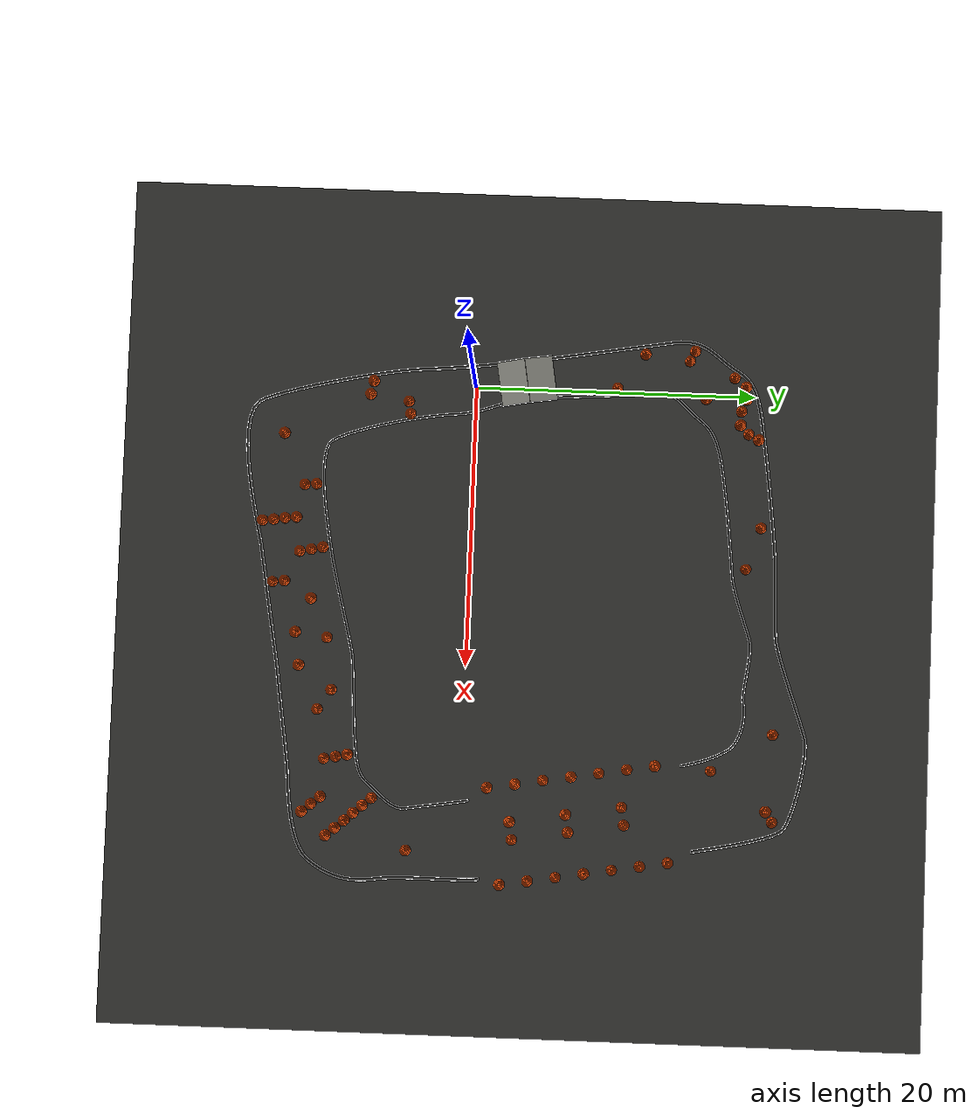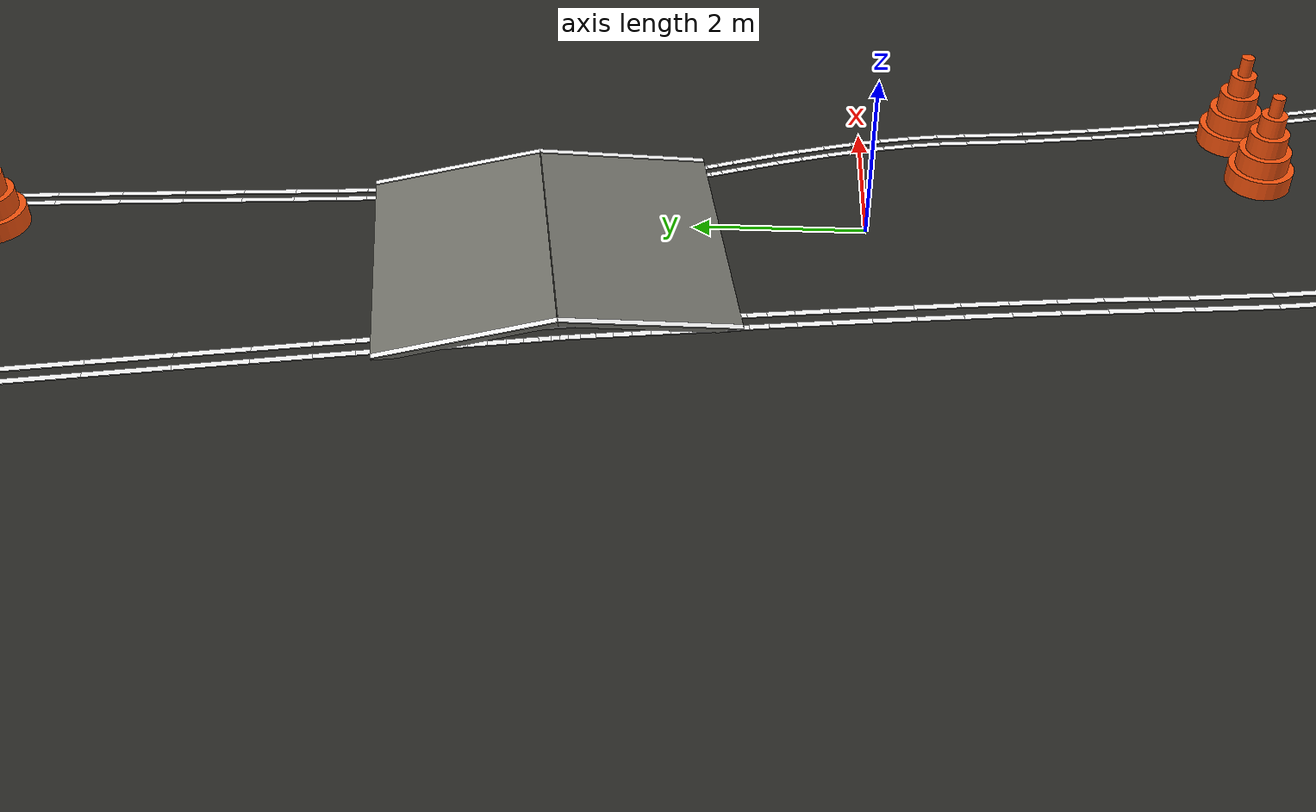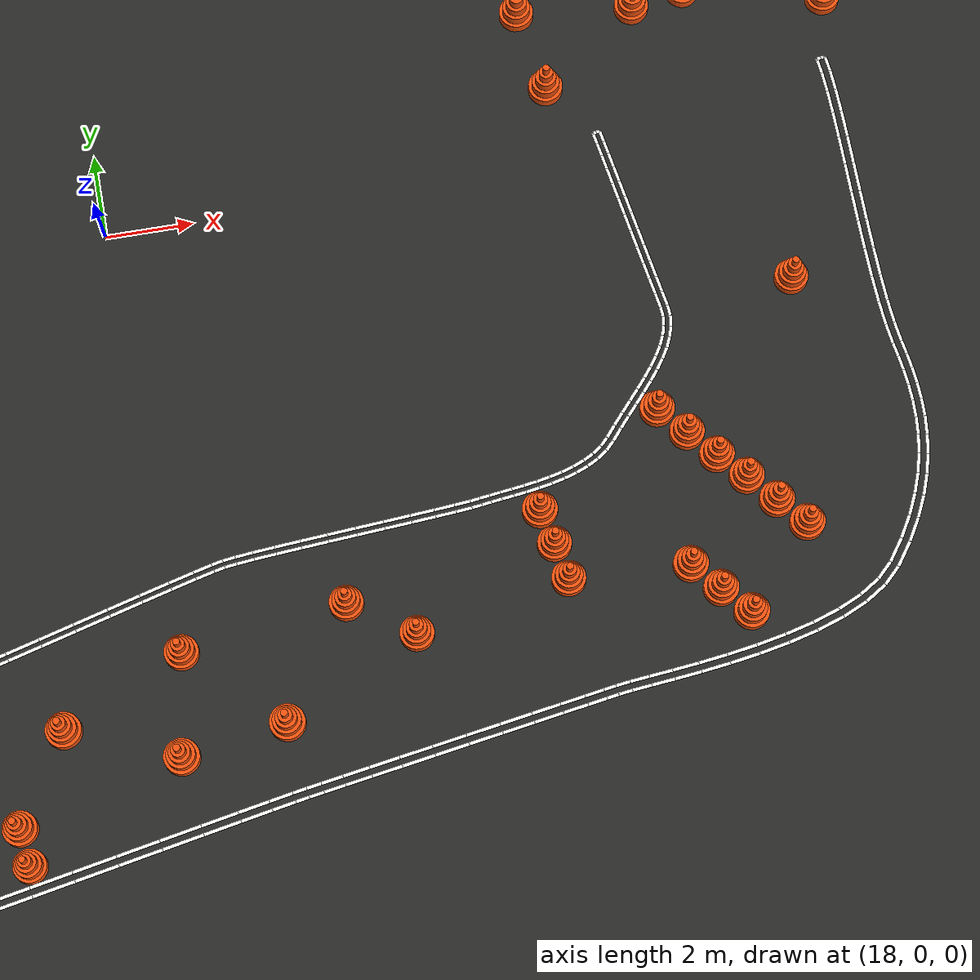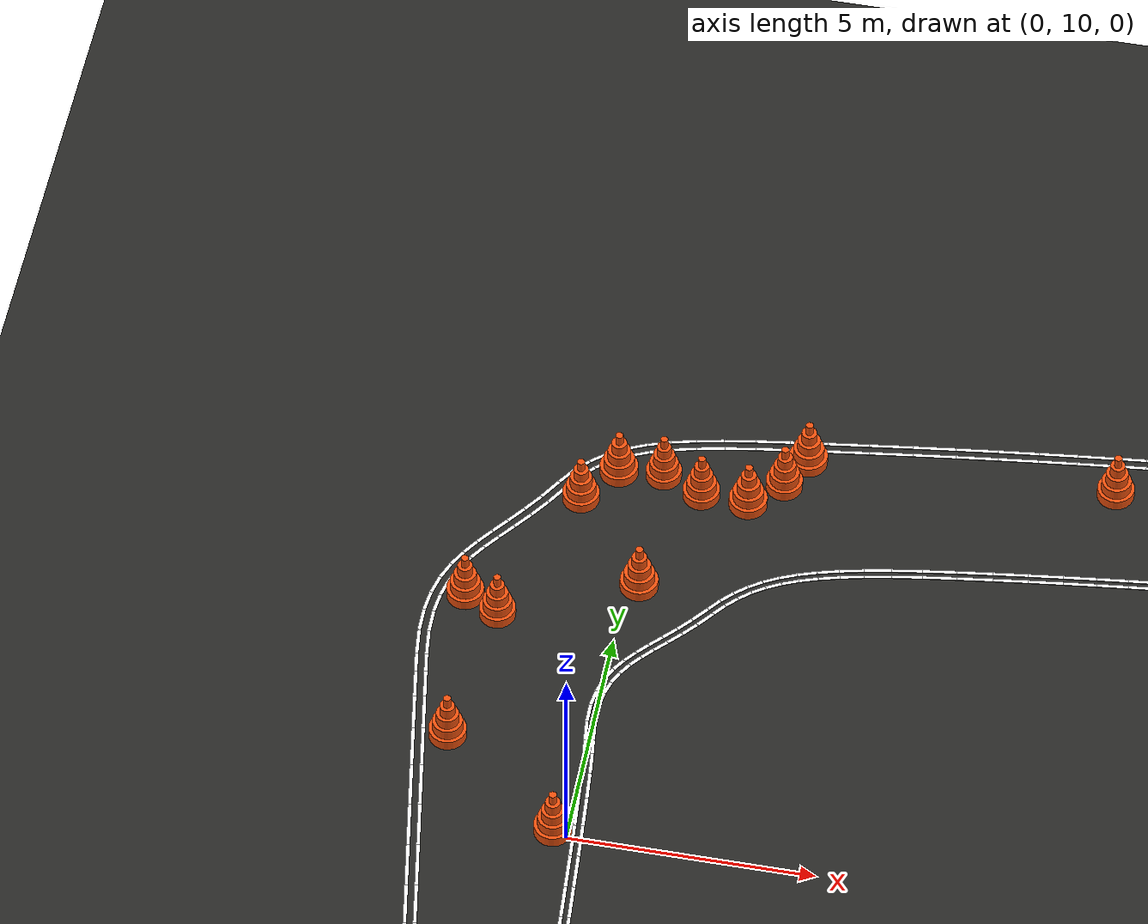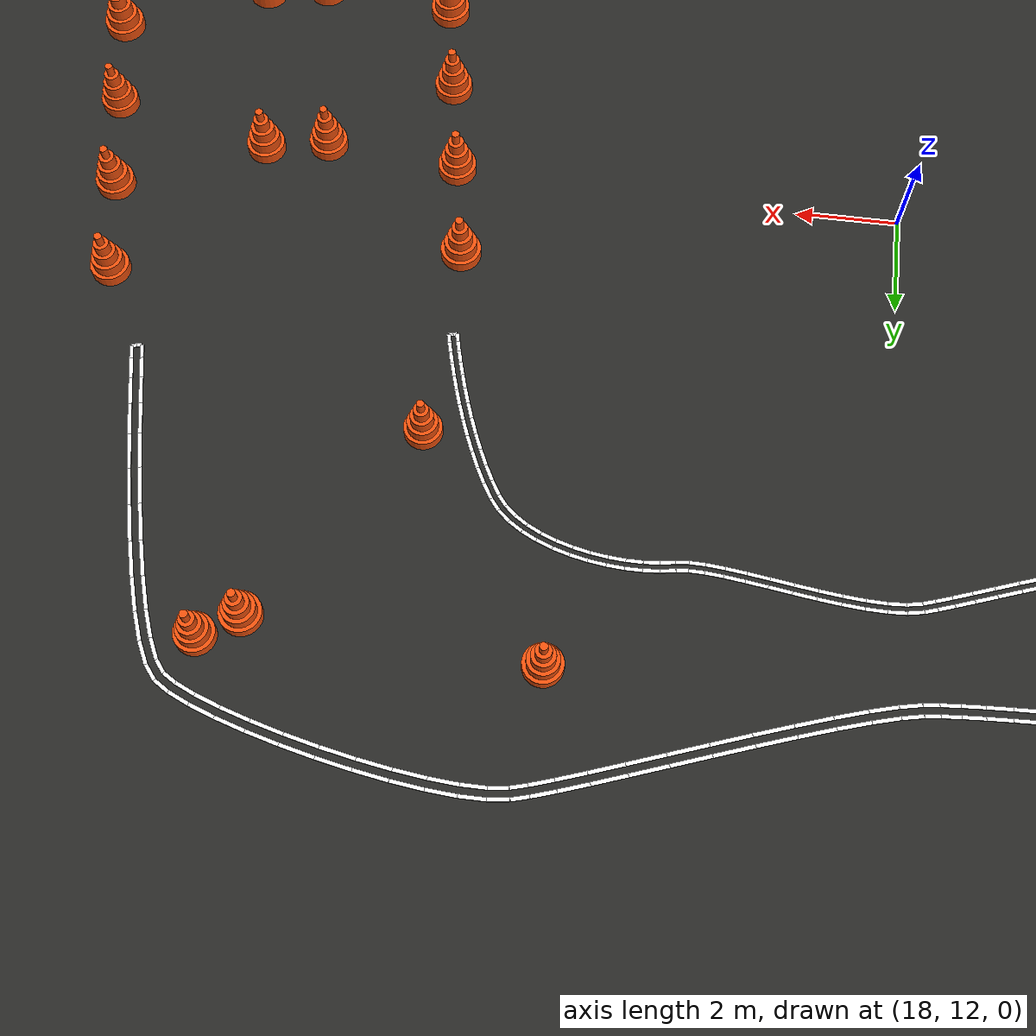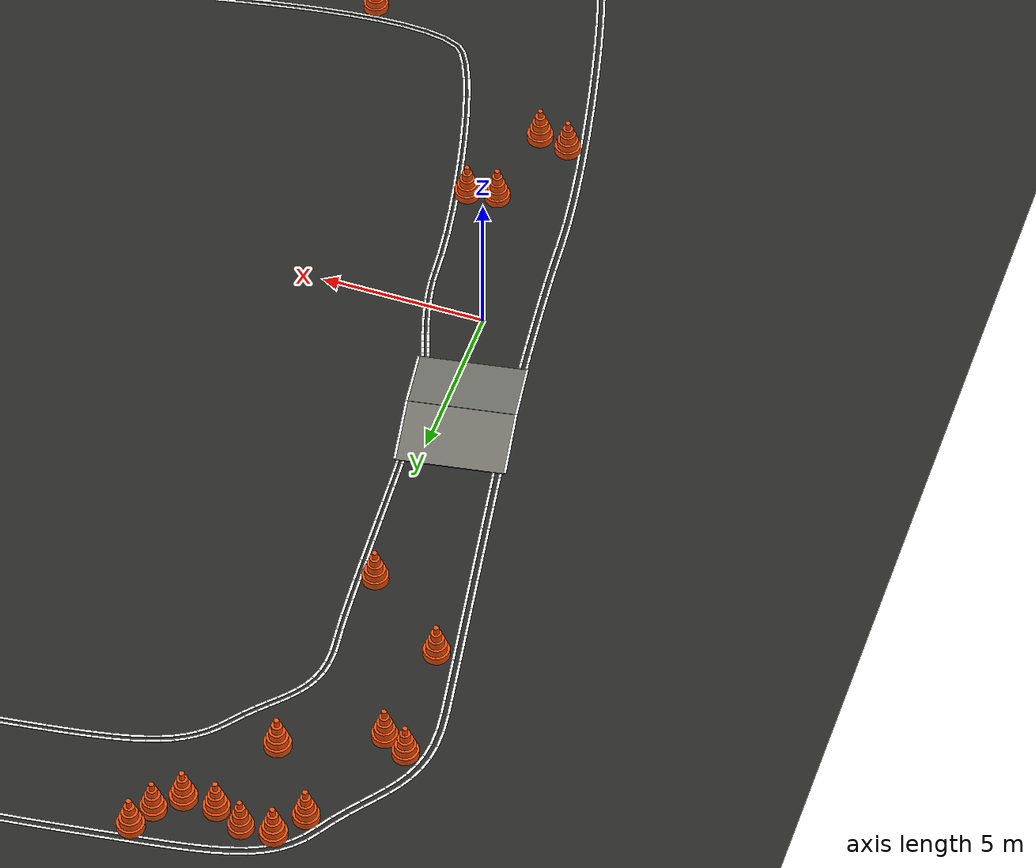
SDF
<sdf version="1.9">
 <world name="igvc_competition">
  <plugin filename="ignition-gazebo-physics-system" name="ignition::gazebo::systems::Physics"/>
  <plugin filename="ignition-gazebo-user-commands-system" name="ignition::gazebo::systems::UserCommands"/>
  <plugin filename="ignition-gazebo-scene-broadcaster-system" name="ignition::gazebo::systems::SceneBroadcaster"/>
  <plugin filename="ignition-gazebo-sensors-system" name="ignition::gazebo::systems::Sensors">
   <render_engine>ogre2</render_engine>
  </plugin>
  <light name="sun" type="directional">
   <pose>0 0 20 0 0 0</pose>
   <diffuse>0.8 0.8 0.75 1</diffuse>
   <specular>0.2 0.2 0.2 1</specular>
   <direction>-0.35 0.15 -0.92</direction>
  </light>
  <gravity>0 0 -9.80665</gravity>
  <magnetic_field>6e-06 2.3e-05 -4.2e-05</magnetic_field>
  <atmosphere type="adiabatic"/>
  <physics name="default_physics" type="ode">
   <max_step_size>0.010</max_step_size>
   <real_time_factor>1.0</real_time_factor>
   <real_time_update_rate>100</real_time_update_rate>
  </physics>
  <scene>
   <ambient>0.45 0.45 0.45 1</ambient>
   <background>0.70 0.72 0.75 1</background>
   <shadows>true</shadows>
  </scene>
  <spherical_coordinates>
   <surface_model>EARTH_WGS84</surface_model>
   <latitude_deg>37.23030000</latitude_deg>
   <longitude_deg>-80.42500000</longitude_deg>
   <elevation>650.000</elevation>
   <heading_deg>0</heading_deg>
  </spherical_coordinates>
  <model name="asphalt_ground">
   <static>1</static>
   <pose>16.0000 4.0000 -0.0250 0.000000 0.000000 0.000000</pose>
   <link name="link">
    <collision name="collision"><geometry><box><size>60.0000 58.0000 0.0500</size></box></geometry></collision>
    <visual name="visual">
     <geometry><box><size>60.0000 58.0000 0.0500</size></box></geometry>
     <material>
      <ambient>0.16 0.16 0.15 1.0</ambient>
      <diffuse>0.16 0.16 0.15 1.0</diffuse>
      <specular>0.05 0.05 0.05 1</specular>
     </material>
    </visual>
   </link>
  </model>
  <model name="Line_001_0000">
   <static>1</static>
   <pose>32.4409 16.4236 0.011 0 0 0.189157</pose>
   <link name="link">
    <visual name="visual">
     <geometry><box><size>0.1000 0.0762 0.012</size></box></geometry>
     <material>
      <ambient>0.98 0.98 0.98 1</ambient>
      <diffuse>0.98 0.98 0.98 1</diffuse>
      <specular>0.05 0.05 0.05 1</specular>
      <emissive>0.9 0.9 0.9 1</emissive>
     </material>
    </visual>
   </link>
  </model>
  <model name="Line_001_0001">
   <static>1</static>
   <pose>32.3661 16.5486 0.011 0 0 1.759736</pose>
   <link name="link">
    <visual name="visual">
     <geometry><box><size>0.2737 0.0762 0.012</size></box></geometry>
     <material>
      <ambient>0.98 0.98 0.98 1</ambient>
      <diffuse>0.98 0.98 0.98 1</diffuse>
      <specular>0.05 0.05 0.05 1</specular>
      <emissive>0.9 0.9 0.9 1</emissive>
     </material>
    </visual>
   </link>
  </model>
  <model name="Line_001_0002">
   <static>1</static>
   <pose>32.5391 16.4424 0.011 0 0 -2.952435</pose>
   <link name="link">
    <visual name="visual">
     <geometry><box><size>0.1000 0.0762 0.012</size></box></geometry>
     <material>
      <ambient>0.98 0.98 0.98 1</ambient>
      <diffuse>0.98 0.98 0.98 1</diffuse>
      <specular>0.05 0.05 0.05 1</specular>
      <emissive>0.9 0.9 0.9 1</emissive>
     </material>
    </visual>
   </link>
  </model>
  <model name="Line_001_0003">
   <static>1</static>
   <pose>32.5626 16.5859 0.011 0 0 1.759720</pose>
   <link name="link">
    <visual name="visual">
     <geometry><box><size>0.2732 0.0762 0.012</size></box></geometry>
     <material>
      <ambient>0.98 0.98 0.98 1</ambient>
      <diffuse>0.98 0.98 0.98 1</diffuse>
      <specular>0.05 0.05 0.05 1</specular>
      <emissive>0.9 0.9 0.9 1</emissive>
     </material>
    </visual>
   </link>
  </model>
  <model name="Line_001_0004">
   <static>1</static>
   <pose>32.3014 16.8928 0.011 0 0 1.754547</pose>
   <link name="link">
    <visual name="visual">
     <geometry><box><size>0.4269 0.0762 0.012</size></box></geometry>
     <material>
      <ambient>0.98 0.98 0.98 1</ambient>
      <diffuse>0.98 0.98 0.98 1</diffuse>
      <specular>0.05 0.05 0.05 1</specular>
      <emissive>0.9 0.9 0.9 1</emissive>
     </material>
    </visual>
   </link>
  </model>
  <model name="Line_001_0005">
   <static>1</static>
   <pose>32.4980 16.9298 0.011 0 0 1.754445</pose>
   <link name="link">
    <visual name="visual">
     <geometry><box><size>0.4266 0.0762 0.012</size></box></geometry>
     <material>
      <ambient>0.98 0.98 0.98 1</ambient>
      <diffuse>0.98 0.98 0.98 1</diffuse>
      <specular>0.05 0.05 0.05 1</specular>
      <emissive>0.9 0.9 0.9 1</emissive>
     </material>
    </visual>
   </link>
  </model>
  <model name="Line_001_0006">
   <static>1</static>
   <pose>32.2115 17.3725 0.011 0 0 1.757297</pose>
   <link name="link">
    <visual name="visual">
     <geometry><box><size>0.5490 0.0762 0.012</size></box></geometry>
     <material>
      <ambient>0.98 0.98 0.98 1</ambient>
      <diffuse>0.98 0.98 0.98 1</diffuse>
      <specular>0.05 0.05 0.05 1</specular>
      <emissive>0.9 0.9 0.9 1</emissive>
     </material>
    </visual>
   </link>
  </model>
  <model name="Line_001_0007">
   <static>1</static>
   <pose>32.4080 17.4097 0.011 0 0 1.757351</pose>
   <link name="link">
    <visual name="visual">
     <geometry><box><size>0.5499 0.0762 0.012</size></box></geometry>
     <material>
      <ambient>0.98 0.98 0.98 1</ambient>
      <diffuse>0.98 0.98 0.98 1</diffuse>
      <specular>0.05 0.05 0.05 1</specular>
      <emissive>0.9 0.9 0.9 1</emissive>
     </material>
    </visual>
   </link>
  </model>
  <model name="Line_001_0008">
   <static>1</static>
   <pose>32.0992 17.9567 0.011 0 0 1.763602</pose>
   <link name="link">
    <visual name="visual">
     <geometry><box><size>0.6409 0.0762 0.012</size></box></geometry>
     <material>
      <ambient>0.98 0.98 0.98 1</ambient>
      <diffuse>0.98 0.98 0.98 1</diffuse>
      <specular>0.05 0.05 0.05 1</specular>
      <emissive>0.9 0.9 0.9 1</emissive>
     </material>
    </visual>
   </link>
  </model>
  <model name="Line_001_0009">
   <static>1</static>
   <pose>32.2955 17.9952 0.011 0 0 1.763583</pose>
   <link name="link">
    <visual name="visual">
     <geometry><box><size>0.6425 0.0762 0.012</size></box></geometry>
     <material>
      <ambient>0.98 0.98 0.98 1</ambient>
      <diffuse>0.98 0.98 0.98 1</diffuse>
      <specular>0.05 0.05 0.05 1</specular>
      <emissive>0.9 0.9 0.9 1</emissive>
     </material>
    </visual>
   </link>
  </model>
  <model name="Line_001_0010">
   <static>1</static>
   <pose>31.9671 18.6151 0.011 0 0 1.773386</pose>
   <link name="link">
    <visual name="visual">
     <geometry><box><size>0.7023 0.0762 0.012</size></box></geometry>
     <material>
      <ambient>0.98 0.98 0.98 1</ambient>
      <diffuse>0.98 0.98 0.98 1</diffuse>
      <specular>0.05 0.05 0.05 1</specular>
      <emissive>0.9 0.9 0.9 1</emissive>
     </material>
    </visual>
   </link>
  </model>
  <model name="Line_001_0011">
   <static>1</static>
   <pose>32.1630 18.6555 0.011 0 0 1.773314</pose>
   <link name="link">
    <visual name="visual">
     <geometry><box><size>0.7045 0.0762 0.012</size></box></geometry>
     <material>
      <ambient>0.98 0.98 0.98 1</ambient>
      <diffuse>0.98 0.98 0.98 1</diffuse>
      <specular>0.05 0.05 0.05 1</specular>
      <emissive>0.9 0.9 0.9 1</emissive>
     </material>
    </visual>
   </link>
  </model>
  <model name="Line_001_0012">
   <static>1</static>
   <pose>31.8181 19.3171 0.011 0 0 1.786358</pose>
   <link name="link">
    <visual name="visual">
     <geometry><box><size>0.7331 0.0762 0.012</size></box></geometry>
     <material>
      <ambient>0.98 0.98 0.98 1</ambient>
      <diffuse>0.98 0.98 0.98 1</diffuse>
      <specular>0.05 0.05 0.05 1</specular>
      <emissive>0.9 0.9 0.9 1</emissive>
     </material>
    </visual>
   </link>
  </model>
  <model name="Line_001_0013">
   <static>1</static>
   <pose>32.0134 19.3602 0.011 0 0 1.786519</pose>
   <link name="link">
    <visual name="visual">
     <geometry><box><size>0.7363 0.0762 0.012</size></box></geometry>
     <material>
      <ambient>0.98 0.98 0.98 1</ambient>
      <diffuse>0.98 0.98 0.98 1</diffuse>
      <specular>0.05 0.05 0.05 1</specular>
      <emissive>0.9 0.9 0.9 1</emissive>
     </material>
    </visual>
   </link>
  </model>
  <model name="Line_001_0014">
   <static>1</static>
   <pose>31.6548 20.0320 0.011 0 0 1.804432</pose>
   <link name="link">
    <visual name="visual">
     <geometry><box><size>0.7334 0.0762 0.012</size></box></geometry>
     <material>
      <ambient>0.98 0.98 0.98 1</ambient>
      <diffuse>0.98 0.98 0.98 1</diffuse>
      <specular>0.05 0.05 0.05 1</specular>
      <emissive>0.9 0.9 0.9 1</emissive>
     </material>
    </visual>
   </link>
  </model>
  <model name="Line_001_0015">
   <static>1</static>
   <pose>31.8492 20.0786 0.011 0 0 1.804332</pose>
   <link name="link">
    <visual name="visual">
     <geometry><box><size>0.7376 0.0762 0.012</size></box></geometry>
     <material>
      <ambient>0.98 0.98 0.98 1</ambient>
      <diffuse>0.98 0.98 0.98 1</diffuse>
      <specular>0.05 0.05 0.05 1</specular>
      <emissive>0.9 0.9 0.9 1</emissive>
     </material>
    </visual>
   </link>
  </model>
  <model name="Line_001_0016">
   <static>1</static>
   <pose>31.4800 20.7287 0.011 0 0 1.829155</pose>
   <link name="link">
    <visual name="visual">
     <geometry><box><size>0.7033 0.0762 0.012</size></box></geometry>
     <material>
      <ambient>0.98 0.98 0.98 1</ambient>
      <diffuse>0.98 0.98 0.98 1</diffuse>
      <specular>0.05 0.05 0.05 1</specular>
      <emissive>0.9 0.9 0.9 1</emissive>
     </material>
    </visual>
   </link>
  </model>
  <model name="Line_001_0017">
   <static>1</static>
   <pose>31.6732 20.7803 0.011 0 0 1.829211</pose>
   <link name="link">
    <visual name="visual">
     <geometry><box><size>0.7095 0.0762 0.012</size></box></geometry>
     <material>
      <ambient>0.98 0.98 0.98 1</ambient>
      <diffuse>0.98 0.98 0.98 1</diffuse>
      <specular>0.05 0.05 0.05 1</specular>
      <emissive>0.9 0.9 0.9 1</emissive>
     </material>
    </visual>
   </link>
  </model>
  <model name="Line_001_0018">
   <static>1</static>
   <pose>31.2968 21.3763 0.011 0 0 1.865441</pose>
   <link name="link">
    <visual name="visual">
     <geometry><box><size>0.6429 0.0762 0.012</size></box></geometry>
     <material>
      <ambient>0.98 0.98 0.98 1</ambient>
      <diffuse>0.98 0.98 0.98 1</diffuse>
      <specular>0.05 0.05 0.05 1</specular>
      <emissive>0.9 0.9 0.9 1</emissive>
     </material>
    </visual>
   </link>
  </model>
  <model name="Line_001_0019">
   <static>1</static>
   <pose>31.4879 21.4354 0.011 0 0 1.865395</pose>
   <link name="link">
    <visual name="visual">
     <geometry><box><size>0.6523 0.0762 0.012</size></box></geometry>
     <material>
      <ambient>0.98 0.98 0.98 1</ambient>
      <diffuse>0.98 0.98 0.98 1</diffuse>
      <specular>0.05 0.05 0.05 1</specular>
      <emissive>0.9 0.9 0.9 1</emissive>
     </material>
    </visual>
   </link>
  </model>
  <model name="Line_001_0020">
   <static>1</static>
   <pose>31.1084 21.9432 0.011 0 0 1.922213</pose>
   <link name="link">
    <visual name="visual">
     <geometry><box><size>0.5523 0.0762 0.012</size></box></geometry>
     <material>
      <ambient>0.98 0.98 0.98 1</ambient>
      <diffuse>0.98 0.98 0.98 1</diffuse>
      <specular>0.05 0.05 0.05 1</specular>
      <emissive>0.9 0.9 0.9 1</emissive>
     </material>
    </visual>
   </link>
  </model>
  <model name="Line_001_0021">
   <static>1</static>
   <pose>31.2953 22.0141 0.011 0 0 1.922726</pose>
   <link name="link">
    <visual name="visual">
     <geometry><box><size>0.5680 0.0762 0.012</size></box></geometry>
     <material>
      <ambient>0.98 0.98 0.98 1</ambient>
      <diffuse>0.98 0.98 0.98 1</diffuse>
      <specular>0.05 0.05 0.05 1</specular>
      <emissive>0.9 0.9 0.9 1</emissive>
     </material>
    </visual>
   </link>
  </model>
  <model name="Line_001_0022">
   <static>1</static>
   <pose>30.9195 22.3961 0.011 0 0 2.022287</pose>
   <link name="link">
    <visual name="visual">
     <geometry><box><size>0.4304 0.0762 0.012</size></box></geometry>
     <material>
      <ambient>0.98 0.98 0.98 1</ambient>
      <diffuse>0.98 0.98 0.98 1</diffuse>
      <specular>0.05 0.05 0.05 1</specular>
      <emissive>0.9 0.9 0.9 1</emissive>
     </material>
    </visual>
   </link>
  </model>
  <model name="Line_001_0023">
   <static>1</static>
   <pose>31.0962 22.4884 0.011 0 0 2.024280</pose>
   <link name="link">
    <visual name="visual">
     <geometry><box><size>0.4620 0.0762 0.012</size></box></geometry>
     <material>
      <ambient>0.98 0.98 0.98 1</ambient>
      <diffuse>0.98 0.98 0.98 1</diffuse>
      <specular>0.05 0.05 0.05 1</specular>
      <emissive>0.9 0.9 0.9 1</emissive>
     </material>
    </visual>
   </link>
  </model>
  <model name="Line_001_0024">
   <static>1</static>
   <pose>30.7373 22.7022 0.011 0 0 2.236530</pose>
   <link name="link">
    <visual name="visual">
     <geometry><box><size>0.2861 0.0762 0.012</size></box></geometry>
     <material>
      <ambient>0.98 0.98 0.98 1</ambient>
      <diffuse>0.98 0.98 0.98 1</diffuse>
      <specular>0.05 0.05 0.05 1</specular>
      <emissive>0.9 0.9 0.9 1</emissive>
     </material>
    </visual>
   </link>
  </model>
  <model name="Line_001_0025">
   <static>1</static>
   <pose>30.8888 22.8298 0.011 0 0 2.241879</pose>
   <link name="link">
    <visual name="visual">
     <geometry><box><size>0.3416 0.0762 0.012</size></box></geometry>
     <material>
      <ambient>0.98 0.98 0.98 1</ambient>
      <diffuse>0.98 0.98 0.98 1</diffuse>
      <specular>0.05 0.05 0.05 1</specular>
      <emissive>0.9 0.9 0.9 1</emissive>
     </material>
    </visual>
   </link>
  </model>
  <model name="Line_001_0026">
   <static>1</static>
   <pose>30.5274 22.8905 0.011 0 0 2.584104</pose>
   <link name="link">
    <visual name="visual">
     <geometry><box><size>0.2864 0.0762 0.012</size></box></geometry>
     <material>
      <ambient>0.98 0.98 0.98 1</ambient>
      <diffuse>0.98 0.98 0.98 1</diffuse>
      <specular>0.05 0.05 0.05 1</specular>
      <emissive>0.9 0.9 0.9 1</emissive>
     </material>
    </visual>
   </link>
  </model>
  <model name="Line_001_0027">
   <static>1</static>
   <pose>30.6416 23.0529 0.011 0 0 2.576104</pose>
   <link name="link">
    <visual name="visual">
     <geometry><box><size>0.3339 0.0762 0.012</size></box></geometry>
     <material>
      <ambient>0.98 0.98 0.98 1</ambient>
      <diffuse>0.98 0.98 0.98 1</diffuse>
      <specular>0.05 0.05 0.05 1</specular>
      <emissive>0.9 0.9 0.9 1</emissive>
     </material>
    </visual>
   </link>
  </model>
  <model name="Line_001_0028">
   <static>1</static>
   <pose>30.2178 23.0513 0.011 0 0 2.716508</pose>
   <link name="link">
    <visual name="visual">
     <geometry><box><size>0.4130 0.0762 0.012</size></box></geometry>
     <material>
      <ambient>0.98 0.98 0.98 1</ambient>
      <diffuse>0.98 0.98 0.98 1</diffuse>
      <specular>0.05 0.05 0.05 1</specular>
      <emissive>0.9 0.9 0.9 1</emissive>
     </material>
    </visual>
   </link>
  </model>
  <model name="Line_001_0029">
   <static>1</static>
   <pose>30.3031 23.2320 0.011 0 0 2.715881</pose>
   <link name="link">
    <visual name="visual">
     <geometry><box><size>0.4339 0.0762 0.012</size></box></geometry>
     <material>
      <ambient>0.98 0.98 0.98 1</ambient>
      <diffuse>0.98 0.98 0.98 1</diffuse>
      <specular>0.05 0.05 0.05 1</specular>
      <emissive>0.9 0.9 0.9 1</emissive>
     </material>
    </visual>
   </link>
  </model>
  <model name="Line_001_0030">
   <static>1</static>
   <pose>29.7892 23.2248 0.011 0 0 2.789836</pose>
   <link name="link">
    <visual name="visual">
     <geometry><box><size>0.5123 0.0762 0.012</size></box></geometry>
     <material>
      <ambient>0.98 0.98 0.98 1</ambient>
      <diffuse>0.98 0.98 0.98 1</diffuse>
      <specular>0.05 0.05 0.05 1</specular>
      <emissive>0.9 0.9 0.9 1</emissive>
     </material>
    </visual>
   </link>
  </model>
  <model name="Line_001_0031">
   <static>1</static>
   <pose>29.8593 23.4120 0.011 0 0 2.789694</pose>
   <link name="link">
    <visual name="visual">
     <geometry><box><size>0.5245 0.0762 0.012</size></box></geometry>
     <material>
      <ambient>0.98 0.98 0.98 1</ambient>
      <diffuse>0.98 0.98 0.98 1</diffuse>
      <specular>0.05 0.05 0.05 1</specular>
      <emissive>0.9 0.9 0.9 1</emissive>
     </material>
    </visual>
   </link>
  </model>
  <model name="Line_001_0032">
   <static>1</static>
   <pose>29.2683 23.4007 0.011 0 0 2.838454</pose>
   <link name="link">
    <visual name="visual">
     <geometry><box><size>0.5879 0.0762 0.012</size></box></geometry>
     <material>
      <ambient>0.98 0.98 0.98 1</ambient>
      <diffuse>0.98 0.98 0.98 1</diffuse>
      <specular>0.05 0.05 0.05 1</specular>
      <emissive>0.9 0.9 0.9 1</emissive>
     </material>
    </visual>
   </link>
  </model>
  <model name="Line_001_0033">
   <static>1</static>
   <pose>29.3285 23.5914 0.011 0 0 2.838558</pose>
   <link name="link">
    <visual name="visual">
     <geometry><box><size>0.5965 0.0762 0.012</size></box></geometry>
     <material>
      <ambient>0.98 0.98 0.98 1</ambient>
      <diffuse>0.98 0.98 0.98 1</diffuse>
      <specular>0.05 0.05 0.05 1</specular>
      <emissive>0.9 0.9 0.9 1</emissive>
     </material>
    </visual>
   </link>
  </model>
  <model name="Line_001_0034">
   <static>1</static>
   <pose>28.6787 23.5726 0.011 0 0 2.875861</pose>
   <link name="link">
    <visual name="visual">
     <geometry><box><size>0.6405 0.0762 0.012</size></box></geometry>
     <material>
      <ambient>0.98 0.98 0.98 1</ambient>
      <diffuse>0.98 0.98 0.98 1</diffuse>
      <specular>0.05 0.05 0.05 1</specular>
      <emissive>0.9 0.9 0.9 1</emissive>
     </material>
    </visual>
   </link>
  </model>
  <model name="Line_001_0035">
   <static>1</static>
   <pose>28.7315 23.7655 0.011 0 0 2.875747</pose>
   <link name="link">
    <visual name="visual">
     <geometry><box><size>0.6474 0.0762 0.012</size></box></geometry>
     <material>
      <ambient>0.98 0.98 0.98 1</ambient>
      <diffuse>0.98 0.98 0.98 1</diffuse>
      <specular>0.05 0.05 0.05 1</specular>
      <emissive>0.9 0.9 0.9 1</emissive>
     </material>
    </visual>
   </link>
  </model>
  <model name="Line_001_0036">
   <static>1</static>
   <pose>28.0437 23.7343 0.011 0 0 2.907905</pose>
   <link name="link">
    <visual name="visual">
     <geometry><box><size>0.6702 0.0762 0.012</size></box></geometry>
     <material>
      <ambient>0.98 0.98 0.98 1</ambient>
      <diffuse>0.98 0.98 0.98 1</diffuse>
      <specular>0.05 0.05 0.05 1</specular>
      <emissive>0.9 0.9 0.9 1</emissive>
     </material>
    </visual>
   </link>
  </model>
  <model name="Line_001_0037">
   <static>1</static>
   <pose>28.0900 23.9288 0.011 0 0 2.907980</pose>
   <link name="link">
    <visual name="visual">
     <geometry><box><size>0.6765 0.0762 0.012</size></box></geometry>
     <material>
      <ambient>0.98 0.98 0.98 1</ambient>
      <diffuse>0.98 0.98 0.98 1</diffuse>
      <specular>0.05 0.05 0.05 1</specular>
      <emissive>0.9 0.9 0.9 1</emissive>
     </material>
    </visual>
   </link>
  </model>
  <model name="Line_001_0038">
   <static>1</static>
   <pose>27.3861 23.8800 0.011 0 0 2.939071</pose>
   <link name="link">
    <visual name="visual">
     <geometry><box><size>0.6771 0.0762 0.012</size></box></geometry>
     <material>
      <ambient>0.98 0.98 0.98 1</ambient>
      <diffuse>0.98 0.98 0.98 1</diffuse>
      <specular>0.05 0.05 0.05 1</specular>
      <emissive>0.9 0.9 0.9 1</emissive>
     </material>
    </visual>
   </link>
  </model>
  <model name="Line_001_0039">
   <static>1</static>
   <pose>27.4262 24.0759 0.011 0 0 2.938918</pose>
   <link name="link">
    <visual name="visual">
     <geometry><box><size>0.6836 0.0762 0.012</size></box></geometry>
     <material>
      <ambient>0.98 0.98 0.98 1</ambient>
      <diffuse>0.98 0.98 0.98 1</diffuse>
      <specular>0.05 0.05 0.05 1</specular>
      <emissive>0.9 0.9 0.9 1</emissive>
     </material>
    </visual>
   </link>
  </model>
  <model name="Line_001_0040">
   <static>1</static>
   <pose>26.7285 24.0039 0.011 0 0 2.972019</pose>
   <link name="link">
    <visual name="visual">
     <geometry><box><size>0.6613 0.0762 0.012</size></box></geometry>
     <material>
      <ambient>0.98 0.98 0.98 1</ambient>
      <diffuse>0.98 0.98 0.98 1</diffuse>
      <specular>0.05 0.05 0.05 1</specular>
      <emissive>0.9 0.9 0.9 1</emissive>
     </material>
    </visual>
   </link>
  </model>
  <model name="Line_001_0041">
   <static>1</static>
   <pose>26.7619 24.2011 0.011 0 0 2.972189</pose>
   <link name="link">
    <visual name="visual">
     <geometry><box><size>0.6685 0.0762 0.012</size></box></geometry>
     <material>
      <ambient>0.98 0.98 0.98 1</ambient>
      <diffuse>0.98 0.98 0.98 1</diffuse>
      <specular>0.05 0.05 0.05 1</specular>
      <emissive>0.9 0.9 0.9 1</emissive>
     </material>
    </visual>
   </link>
  </model>
  <model name="Line_001_0042">
   <static>1</static>
   <pose>26.0938 24.1002 0.011 0 0 3.011025</pose>
   <link name="link">
    <visual name="visual">
     <geometry><box><size>0.6229 0.0762 0.012</size></box></geometry>
     <material>
      <ambient>0.98 0.98 0.98 1</ambient>
      <diffuse>0.98 0.98 0.98 1</diffuse>
      <specular>0.05 0.05 0.05 1</specular>
      <emissive>0.9 0.9 0.9 1</emissive>
     </material>
    </visual>
   </link>
  </model>
  <model name="Line_001_0043">
   <static>1</static>
   <pose>26.1193 24.2985 0.011 0 0 3.010955</pose>
   <link name="link">
    <visual name="visual">
     <geometry><box><size>0.6318 0.0762 0.012</size></box></geometry>
     <material>
      <ambient>0.98 0.98 0.98 1</ambient>
      <diffuse>0.98 0.98 0.98 1</diffuse>
      <specular>0.05 0.05 0.05 1</specular>
      <emissive>0.9 0.9 0.9 1</emissive>
     </material>
    </visual>
   </link>
  </model>
  <model name="Line_001_0044">
   <static>1</static>
   <pose>25.5050 24.1634 0.011 0 0 3.061230</pose>
   <link name="link">
    <visual name="visual">
     <geometry><box><size>0.5618 0.0762 0.012</size></box></geometry>
     <material>
      <ambient>0.98 0.98 0.98 1</ambient>
      <diffuse>0.98 0.98 0.98 1</diffuse>
      <specular>0.05 0.05 0.05 1</specular>
      <emissive>0.9 0.9 0.9 1</emissive>
     </material>
    </visual>
   </link>
  </model>
  <model name="Line_001_0045">
   <static>1</static>
   <pose>25.5199 24.3627 0.011 0 0 3.061402</pose>
   <link name="link">
    <visual name="visual">
     <geometry><box><size>0.5742 0.0762 0.012</size></box></geometry>
     <material>
      <ambient>0.98 0.98 0.98 1</ambient>
      <diffuse>0.98 0.98 0.98 1</diffuse>
      <specular>0.05 0.05 0.05 1</specular>
      <emissive>0.9 0.9 0.9 1</emissive>
     </material>
    </visual>
   </link>
  </model>
  <model name="Line_001_0046">
   <static>1</static>
   <pose>24.9858 24.1877 0.011 0 0 3.134068</pose>
   <link name="link">
    <visual name="visual">
     <geometry><box><size>0.4784 0.0762 0.012</size></box></geometry>
     <material>
      <ambient>0.98 0.98 0.98 1</ambient>
      <diffuse>0.98 0.98 0.98 1</diffuse>
      <specular>0.05 0.05 0.05 1</specular>
      <emissive>0.9 0.9 0.9 1</emissive>
     </material>
    </visual>
   </link>
  </model>
  <model name="Line_001_0047">
   <static>1</static>
   <pose>24.9849 24.3875 0.011 0 0 3.134358</pose>
   <link name="link">
    <visual name="visual">
     <geometry><box><size>0.4976 0.0762 0.012</size></box></geometry>
     <material>
      <ambient>0.98 0.98 0.98 1</ambient>
      <diffuse>0.98 0.98 0.98 1</diffuse>
      <specular>0.05 0.05 0.05 1</specular>
      <emissive>0.9 0.9 0.9 1</emissive>
     </material>
    </visual>
   </link>
  </model>
  <model name="Line_001_0048">
   <static>1</static>
   <pose>24.5595 24.1684 0.011 0 0 -3.029029</pose>
   <link name="link">
    <visual name="visual">
     <geometry><box><size>0.3766 0.0762 0.012</size></box></geometry>
     <material>
      <ambient>0.98 0.98 0.98 1</ambient>
      <diffuse>0.98 0.98 0.98 1</diffuse>
      <specular>0.05 0.05 0.05 1</specular>
      <emissive>0.9 0.9 0.9 1</emissive>
     </material>
    </visual>
   </link>
  </model>
  <model name="Line_001_0049">
   <static>1</static>
   <pose>24.5358 24.3665 0.011 0 0 -3.028279</pose>
   <link name="link">
    <visual name="visual">
     <geometry><box><size>0.4033 0.0762 0.012</size></box></geometry>
     <material>
      <ambient>0.98 0.98 0.98 1</ambient>
      <diffuse>0.98 0.98 0.98 1</diffuse>
      <specular>0.05 0.05 0.05 1</specular>
      <emissive>0.9 0.9 0.9 1</emissive>
     </material>
    </visual>
   </link>
  </model>
  <model name="Line_001_0050">
   <static>1</static>
   <pose>24.2183 24.1061 0.011 0 0 -2.881253</pose>
   <link name="link">
    <visual name="visual">
     <geometry><box><size>0.3189 0.0762 0.012</size></box></geometry>
     <material>
      <ambient>0.98 0.98 0.98 1</ambient>
      <diffuse>0.98 0.98 0.98 1</diffuse>
      <specular>0.05 0.05 0.05 1</specular>
      <emissive>0.9 0.9 0.9 1</emissive>
     </material>
    </visual>
   </link>
  </model>
  <model name="Line_001_0051">
   <static>1</static>
   <pose>24.1718 24.3004 0.011 0 0 -2.882780</pose>
   <link name="link">
    <visual name="visual">
     <geometry><box><size>0.3384 0.0762 0.012</size></box></geometry>
     <material>
      <ambient>0.98 0.98 0.98 1</ambient>
      <diffuse>0.98 0.98 0.98 1</diffuse>
      <specular>0.05 0.05 0.05 1</specular>
      <emissive>0.9 0.9 0.9 1</emissive>
     </material>
    </visual>
   </link>
  </model>
  <model name="Line_001_0052">
   <static>1</static>
   <pose>23.8422 23.9946 0.011 0 0 -2.833958</pose>
   <link name="link">
    <visual name="visual">
     <geometry><box><size>0.4660 0.0762 0.012</size></box></geometry>
     <material>
      <ambient>0.98 0.98 0.98 1</ambient>
      <diffuse>0.98 0.98 0.98 1</diffuse>
      <specular>0.05 0.05 0.05 1</specular>
      <emissive>0.9 0.9 0.9 1</emissive>
     </material>
    </visual>
   </link>
  </model>
  <model name="Line_001_0053">
   <static>1</static>
   <pose>23.7829 24.1855 0.011 0 0 -2.834154</pose>
   <link name="link">
    <visual name="visual">
     <geometry><box><size>0.4729 0.0762 0.012</size></box></geometry>
     <material>
      <ambient>0.98 0.98 0.98 1</ambient>
      <diffuse>0.98 0.98 0.98 1</diffuse>
      <specular>0.05 0.05 0.05 1</specular>
      <emissive>0.9 0.9 0.9 1</emissive>
     </material>
    </visual>
   </link>
  </model>
  <model name="Line_001_0054">
   <static>1</static>
   <pose>23.3445 23.8302 0.011 0 0 -2.813597</pose>
   <link name="link">
    <visual name="visual">
     <geometry><box><size>0.5823 0.0762 0.012</size></box></geometry>
     <material>
      <ambient>0.98 0.98 0.98 1</ambient>
      <diffuse>0.98 0.98 0.98 1</diffuse>
      <specular>0.05 0.05 0.05 1</specular>
      <emissive>0.9 0.9 0.9 1</emissive>
     </material>
    </visual>
   </link>
  </model>
  <model name="Line_001_0055">
   <static>1</static>
   <pose>23.2805 24.0197 0.011 0 0 -2.813576</pose>
   <link name="link">
    <visual name="visual">
     <geometry><box><size>0.5854 0.0762 0.012</size></box></geometry>
     <material>
      <ambient>0.98 0.98 0.98 1</ambient>
      <diffuse>0.98 0.98 0.98 1</diffuse>
      <specular>0.05 0.05 0.05 1</specular>
      <emissive>0.9 0.9 0.9 1</emissive>
     </material>
    </visual>
   </link>
  </model>
  <model name="Line_001_0056">
   <static>1</static>
   <pose>22.7523 23.6252 0.011 0 0 -2.803673</pose>
   <link name="link">
    <visual name="visual">
     <geometry><box><size>0.6708 0.0762 0.012</size></box></geometry>
     <material>
      <ambient>0.98 0.98 0.98 1</ambient>
      <diffuse>0.98 0.98 0.98 1</diffuse>
      <specular>0.05 0.05 0.05 1</specular>
      <emissive>0.9 0.9 0.9 1</emissive>
     </material>
    </visual>
   </link>
  </model>
  <model name="Line_001_0057">
   <static>1</static>
   <pose>22.6863 23.8140 0.011 0 0 -2.803752</pose>
   <link name="link">
    <visual name="visual">
     <geometry><box><size>0.6722 0.0762 0.012</size></box></geometry>
     <material>
      <ambient>0.98 0.98 0.98 1</ambient>
      <diffuse>0.98 0.98 0.98 1</diffuse>
      <specular>0.05 0.05 0.05 1</specular>
      <emissive>0.9 0.9 0.9 1</emissive>
     </material>
    </visual>
   </link>
  </model>
  <model name="Line_001_0058">
   <static>1</static>
   <pose>22.0911 23.3913 0.011 0 0 -2.799883</pose>
   <link name="link">
    <visual name="visual">
     <geometry><box><size>0.7320 0.0762 0.012</size></box></geometry>
     <material>
      <ambient>0.98 0.98 0.98 1</ambient>
      <diffuse>0.98 0.98 0.98 1</diffuse>
      <specular>0.05 0.05 0.05 1</specular>
      <emissive>0.9 0.9 0.9 1</emissive>
     </material>
    </visual>
   </link>
  </model>
  <model name="Line_001_0059">
   <static>1</static>
   <pose>22.0241 23.5799 0.011 0 0 -2.799809</pose>
   <link name="link">
    <visual name="visual">
     <geometry><box><size>0.7325 0.0762 0.012</size></box></geometry>
     <material>
      <ambient>0.98 0.98 0.98 1</ambient>
      <diffuse>0.98 0.98 0.98 1</diffuse>
      <specular>0.05 0.05 0.05 1</specular>
      <emissive>0.9 0.9 0.9 1</emissive>
     </material>
    </visual>
   </link>
  </model>
  <model name="Line_001_0060">
   <static>1</static>
   <pose>21.3852 23.1403 0.011 0 0 -2.799991</pose>
   <link name="link">
    <visual name="visual">
     <geometry><box><size>0.7663 0.0762 0.012</size></box></geometry>
     <material>
      <ambient>0.98 0.98 0.98 1</ambient>
      <diffuse>0.98 0.98 0.98 1</diffuse>
      <specular>0.05 0.05 0.05 1</specular>
      <emissive>0.9 0.9 0.9 1</emissive>
     </material>
    </visual>
   </link>
  </model>
  <model name="Line_001_0061">
   <static>1</static>
   <pose>21.3183 23.3289 0.011 0 0 -2.800062</pose>
   <link name="link">
    <visual name="visual">
     <geometry><box><size>0.7658 0.0762 0.012</size></box></geometry>
     <material>
      <ambient>0.98 0.98 0.98 1</ambient>
      <diffuse>0.98 0.98 0.98 1</diffuse>
      <specular>0.05 0.05 0.05 1</specular>
      <emissive>0.9 0.9 0.9 1</emissive>
     </material>
    </visual>
   </link>
  </model>
  <model name="Line_001_0062">
   <static>1</static>
   <pose>20.6593 22.8839 0.011 0 0 -2.803856</pose>
   <link name="link">
    <visual name="visual">
     <geometry><box><size>0.7735 0.0762 0.012</size></box></geometry>
     <material>
      <ambient>0.98 0.98 0.98 1</ambient>
      <diffuse>0.98 0.98 0.98 1</diffuse>
      <specular>0.05 0.05 0.05 1</specular>
      <emissive>0.9 0.9 0.9 1</emissive>
     </material>
    </visual>
   </link>
  </model>
  <model name="Line_001_0063">
   <static>1</static>
   <pose>20.5932 23.0726 0.011 0 0 -2.803751</pose>
   <link name="link">
    <visual name="visual">
     <geometry><box><size>0.7724 0.0762 0.012</size></box></geometry>
     <material>
      <ambient>0.98 0.98 0.98 1</ambient>
      <diffuse>0.98 0.98 0.98 1</diffuse>
      <specular>0.05 0.05 0.05 1</specular>
      <emissive>0.9 0.9 0.9 1</emissive>
     </material>
    </visual>
   </link>
  </model>
  <model name="Line_001_0064">
   <static>1</static>
   <pose>19.9378 22.6334 0.011 0 0 -2.811328</pose>
   <link name="link">
    <visual name="visual">
     <geometry><box><size>0.7539 0.0762 0.012</size></box></geometry>
     <material>
      <ambient>0.98 0.98 0.98 1</ambient>
      <diffuse>0.98 0.98 0.98 1</diffuse>
      <specular>0.05 0.05 0.05 1</specular>
      <emissive>0.9 0.9 0.9 1</emissive>
     </material>
    </visual>
   </link>
  </model>
  <model name="Line_001_0065">
   <static>1</static>
   <pose>19.8732 22.8227 0.011 0 0 -2.811346</pose>
   <link name="link">
    <visual name="visual">
     <geometry><box><size>0.7518 0.0762 0.012</size></box></geometry>
     <material>
      <ambient>0.98 0.98 0.98 1</ambient>
      <diffuse>0.98 0.98 0.98 1</diffuse>
      <specular>0.05 0.05 0.05 1</specular>
      <emissive>0.9 0.9 0.9 1</emissive>
     </material>
    </visual>
   </link>
  </model>
  <model name="Line_001_0066">
   <static>1</static>
   <pose>19.2451 22.4007 0.011 0 0 -2.824088</pose>
   <link name="link">
    <visual name="visual">
     <geometry><box><size>0.7076 0.0762 0.012</size></box></geometry>
     <material>
      <ambient>0.98 0.98 0.98 1</ambient>
      <diffuse>0.98 0.98 0.98 1</diffuse>
      <specular>0.05 0.05 0.05 1</specular>
      <emissive>0.9 0.9 0.9 1</emissive>
     </material>
    </visual>
   </link>
  </model>
  <model name="Line_001_0067">
   <static>1</static>
   <pose>19.1830 22.5908 0.011 0 0 -2.824107</pose>
   <link name="link">
    <visual name="visual">
     <geometry><box><size>0.7044 0.0762 0.012</size></box></geometry>
     <material>
      <ambient>0.98 0.98 0.98 1</ambient>
      <diffuse>0.98 0.98 0.98 1</diffuse>
      <specular>0.05 0.05 0.05 1</specular>
      <emissive>0.9 0.9 0.9 1</emissive>
     </material>
    </visual>
   </link>
  </model>
  <model name="Line_001_0068">
   <static>1</static>
   <pose>18.6053 22.1973 0.011 0 0 -2.844436</pose>
   <link name="link">
    <visual name="visual">
     <geometry><box><size>0.6352 0.0762 0.012</size></box></geometry>
     <material>
      <ambient>0.98 0.98 0.98 1</ambient>
      <diffuse>0.98 0.98 0.98 1</diffuse>
      <specular>0.05 0.05 0.05 1</specular>
      <emissive>0.9 0.9 0.9 1</emissive>
     </material>
    </visual>
   </link>
  </model>
  <model name="Line_001_0069">
   <static>1</static>
   <pose>18.5474 22.3887 0.011 0 0 -2.844355</pose>
   <link name="link">
    <visual name="visual">
     <geometry><box><size>0.6296 0.0762 0.012</size></box></geometry>
     <material>
      <ambient>0.98 0.98 0.98 1</ambient>
      <diffuse>0.98 0.98 0.98 1</diffuse>
      <specular>0.05 0.05 0.05 1</specular>
      <emissive>0.9 0.9 0.9 1</emissive>
     </material>
    </visual>
   </link>
  </model>
  <model name="Line_001_0070">
   <static>1</static>
   <pose>18.0420 22.0345 0.011 0 0 -2.879061</pose>
   <link name="link">
    <visual name="visual">
     <geometry><box><size>0.5375 0.0762 0.012</size></box></geometry>
     <material>
      <ambient>0.98 0.98 0.98 1</ambient>
      <diffuse>0.98 0.98 0.98 1</diffuse>
      <specular>0.05 0.05 0.05 1</specular>
      <emissive>0.9 0.9 0.9 1</emissive>
     </material>
    </visual>
   </link>
  </model>
  <model name="Line_001_0071">
   <static>1</static>
   <pose>17.9916 22.2280 0.011 0 0 -2.878915</pose>
   <link name="link">
    <visual name="visual">
     <geometry><box><size>0.5276 0.0762 0.012</size></box></geometry>
     <material>
      <ambient>0.98 0.98 0.98 1</ambient>
      <diffuse>0.98 0.98 0.98 1</diffuse>
      <specular>0.05 0.05 0.05 1</specular>
      <emissive>0.9 0.9 0.9 1</emissive>
     </material>
    </visual>
   </link>
  </model>
  <model name="Line_001_0072">
   <static>1</static>
   <pose>17.5790 21.9242 0.011 0 0 -2.944386</pose>
   <link name="link">
    <visual name="visual">
     <geometry><box><size>0.4149 0.0762 0.012</size></box></geometry>
     <material>
      <ambient>0.98 0.98 0.98 1</ambient>
      <diffuse>0.98 0.98 0.98 1</diffuse>
      <specular>0.05 0.05 0.05 1</specular>
      <emissive>0.9 0.9 0.9 1</emissive>
     </material>
    </visual>
   </link>
  </model>
  <model name="Line_001_0073">
   <static>1</static>
   <pose>17.5410 22.1204 0.011 0 0 -2.944344</pose>
   <link name="link">
    <visual name="visual">
     <geometry><box><size>0.3995 0.0762 0.012</size></box></geometry>
     <material>
      <ambient>0.98 0.98 0.98 1</ambient>
      <diffuse>0.98 0.98 0.98 1</diffuse>
      <specular>0.05 0.05 0.05 1</specular>
      <emissive>0.9 0.9 0.9 1</emissive>
     </material>
    </visual>
   </link>
  </model>
  <model name="Line_001_0074">
   <static>1</static>
   <pose>17.2276 21.8672 0.011 0 0 -3.032233</pose>
   <link name="link">
    <visual name="visual">
     <geometry><box><size>0.2978 0.0762 0.012</size></box></geometry>
     <material>
      <ambient>0.98 0.98 0.98 1</ambient>
      <diffuse>0.98 0.98 0.98 1</diffuse>
      <specular>0.05 0.05 0.05 1</specular>
      <emissive>0.9 0.9 0.9 1</emissive>
     </material>
    </visual>
   </link>
  </model>
  <model name="Line_001_0075">
   <static>1</static>
   <pose>17.2032 22.0656 0.011 0 0 -3.032406</pose>
   <link name="link">
    <visual name="visual">
     <geometry><box><size>0.2854 0.0762 0.012</size></box></geometry>
     <material>
      <ambient>0.98 0.98 0.98 1</ambient>
      <diffuse>0.98 0.98 0.98 1</diffuse>
      <specular>0.05 0.05 0.05 1</specular>
      <emissive>0.9 0.9 0.9 1</emissive>
     </material>
    </visual>
   </link>
  </model>
  <model name="Line_001_0076">
   <static>1</static>
   <pose>16.8955 21.8374 0.011 0 0 -3.068124</pose>
   <link name="link">
    <visual name="visual">
     <geometry><box><size>0.3692 0.0762 0.012</size></box></geometry>
     <material>
      <ambient>0.98 0.98 0.98 1</ambient>
      <diffuse>0.98 0.98 0.98 1</diffuse>
      <specular>0.05 0.05 0.05 1</specular>
      <emissive>0.9 0.9 0.9 1</emissive>
     </material>
    </visual>
   </link>
  </model>
  <model name="Line_001_0077">
   <static>1</static>
   <pose>16.8800 22.0368 0.011 0 0 -3.068385</pose>
   <link name="link">
    <visual name="visual">
     <geometry><box><size>0.3637 0.0762 0.012</size></box></geometry>
     <material>
      <ambient>0.98 0.98 0.98 1</ambient>
      <diffuse>0.98 0.98 0.98 1</diffuse>
      <specular>0.05 0.05 0.05 1</specular>
      <emissive>0.9 0.9 0.9 1</emissive>
     </material>
    </visual>
   </link>
  </model>
  <model name="Line_001_0078">
   <static>1</static>
   <pose>16.4969 21.8126 0.011 0 0 -3.088728</pose>
   <link name="link">
    <visual name="visual">
     <geometry><box><size>0.4296 0.0762 0.012</size></box></geometry>
     <material>
      <ambient>0.98 0.98 0.98 1</ambient>
      <diffuse>0.98 0.98 0.98 1</diffuse>
      <specular>0.05 0.05 0.05 1</specular>
      <emissive>0.9 0.9 0.9 1</emissive>
     </material>
    </visual>
   </link>
  </model>
  <model name="Line_001_0079">
   <static>1</static>
   <pose>16.4859 22.0122 0.011 0 0 -3.088541</pose>
   <link name="link">
    <visual name="visual">
     <geometry><box><size>0.4262 0.0762 0.012</size></box></geometry>
     <material>
      <ambient>0.98 0.98 0.98 1</ambient>
      <diffuse>0.98 0.98 0.98 1</diffuse>
      <specular>0.05 0.05 0.05 1</specular>
      <emissive>0.9 0.9 0.9 1</emissive>
     </material>
    </visual>
   </link>
  </model>
  <model name="Line_001_0080">
   <static>1</static>
   <pose>16.0441 21.7916 0.011 0 0 -3.101329</pose>
   <link name="link">
    <visual name="visual">
     <geometry><box><size>0.4770 0.0762 0.012</size></box></geometry>
     <material>
      <ambient>0.98 0.98 0.98 1</ambient>
      <diffuse>0.98 0.98 0.98 1</diffuse>
      <specular>0.05 0.05 0.05 1</specular>
      <emissive>0.9 0.9 0.9 1</emissive>
     </material>
    </visual>
   </link>
  </model>
  <model name="Line_001_0081">
   <static>1</static>
   <pose>16.0358 21.9914 0.011 0 0 -3.101370</pose>
   <link name="link">
    <visual name="visual">
     <geometry><box><size>0.4750 0.0762 0.012</size></box></geometry>
     <material>
      <ambient>0.98 0.98 0.98 1</ambient>
      <diffuse>0.98 0.98 0.98 1</diffuse>
      <specular>0.05 0.05 0.05 1</specular>
      <emissive>0.9 0.9 0.9 1</emissive>
     </material>
    </visual>
   </link>
  </model>
  <model name="Line_001_0082">
   <static>1</static>
   <pose>15.5503 21.7737 0.011 0 0 -3.109308</pose>
   <link name="link">
    <visual name="visual">
     <geometry><box><size>0.5112 0.0762 0.012</size></box></geometry>
     <material>
      <ambient>0.98 0.98 0.98 1</ambient>
      <diffuse>0.98 0.98 0.98 1</diffuse>
      <specular>0.05 0.05 0.05 1</specular>
      <emissive>0.9 0.9 0.9 1</emissive>
     </material>
    </visual>
   </link>
  </model>
  <model name="Line_001_0083">
   <static>1</static>
   <pose>15.5437 21.9736 0.011 0 0 -3.109422</pose>
   <link name="link">
    <visual name="visual">
     <geometry><box><size>0.5099 0.0762 0.012</size></box></geometry>
     <material>
      <ambient>0.98 0.98 0.98 1</ambient>
      <diffuse>0.98 0.98 0.98 1</diffuse>
      <specular>0.05 0.05 0.05 1</specular>
      <emissive>0.9 0.9 0.9 1</emissive>
     </material>
    </visual>
   </link>
  </model>
  <model name="Line_001_0084">
   <static>1</static>
   <pose>15.0290 21.7582 0.011 0 0 -3.114140</pose>
   <link name="link">
    <visual name="visual">
     <geometry><box><size>0.5319 0.0762 0.012</size></box></geometry>
     <material>
      <ambient>0.98 0.98 0.98 1</ambient>
      <diffuse>0.98 0.98 0.98 1</diffuse>
      <specular>0.05 0.05 0.05 1</specular>
      <emissive>0.9 0.9 0.9 1</emissive>
     </material>
    </visual>
   </link>
  </model>
  <model name="Line_001_0085">
   <static>1</static>
   <pose>15.0235 21.9581 0.011 0 0 -3.114287</pose>
   <link name="link">
    <visual name="visual">
     <geometry><box><size>0.5311 0.0762 0.012</size></box></geometry>
     <material>
      <ambient>0.98 0.98 0.98 1</ambient>
      <diffuse>0.98 0.98 0.98 1</diffuse>
      <specular>0.05 0.05 0.05 1</specular>
      <emissive>0.9 0.9 0.9 1</emissive>
     </material>
    </visual>
   </link>
  </model>
  <model name="Line_001_0086">
   <static>1</static>
   <pose>14.4938 21.7443 0.011 0 0 -3.116913</pose>
   <link name="link">
    <visual name="visual">
     <geometry><box><size>0.5390 0.0762 0.012</size></box></geometry>
     <material>
      <ambient>0.98 0.98 0.98 1</ambient>
      <diffuse>0.98 0.98 0.98 1</diffuse>
      <specular>0.05 0.05 0.05 1</specular>
      <emissive>0.9 0.9 0.9 1</emissive>
     </material>
    </visual>
   </link>
  </model>
  <model name="Line_001_0087">
   <static>1</static>
   <pose>14.4887 21.9442 0.011 0 0 -3.116714</pose>
   <link name="link">
    <visual name="visual">
     <geometry><box><size>0.5387 0.0762 0.012</size></box></geometry>
     <material>
      <ambient>0.98 0.98 0.98 1</ambient>
      <diffuse>0.98 0.98 0.98 1</diffuse>
      <specular>0.05 0.05 0.05 1</specular>
      <emissive>0.9 0.9 0.9 1</emissive>
     </material>
    </visual>
   </link>
  </model>
  <model name="Line_001_0088">
   <static>1</static>
   <pose>13.9582 21.7311 0.011 0 0 -3.117367</pose>
   <link name="link">
    <visual name="visual">
     <geometry><box><size>0.5326 0.0762 0.012</size></box></geometry>
     <material>
      <ambient>0.98 0.98 0.98 1</ambient>
      <diffuse>0.98 0.98 0.98 1</diffuse>
      <specular>0.05 0.05 0.05 1</specular>
      <emissive>0.9 0.9 0.9 1</emissive>
     </material>
    </visual>
   </link>
  </model>
  <model name="Line_001_0089">
   <static>1</static>
   <pose>13.9533 21.9310 0.011 0 0 -3.117372</pose>
   <link name="link">
    <visual name="visual">
     <geometry><box><size>0.5327 0.0762 0.012</size></box></geometry>
     <material>
      <ambient>0.98 0.98 0.98 1</ambient>
      <diffuse>0.98 0.98 0.98 1</diffuse>
      <specular>0.05 0.05 0.05 1</specular>
      <emissive>0.9 0.9 0.9 1</emissive>
     </material>
    </visual>
   </link>
  </model>
  <model name="Line_001_0090">
   <static>1</static>
   <pose>13.4359 21.7180 0.011 0 0 -3.115632</pose>
   <link name="link">
    <visual name="visual">
     <geometry><box><size>0.5124 0.0762 0.012</size></box></geometry>
     <material>
      <ambient>0.98 0.98 0.98 1</ambient>
      <diffuse>0.98 0.98 0.98 1</diffuse>
      <specular>0.05 0.05 0.05 1</specular>
      <emissive>0.9 0.9 0.9 1</emissive>
     </material>
    </visual>
   </link>
  </model>
  <model name="Line_001_0091">
   <static>1</static>
   <pose>13.4306 21.9180 0.011 0 0 -3.115662</pose>
   <link name="link">
    <visual name="visual">
     <geometry><box><size>0.5130 0.0762 0.012</size></box></geometry>
     <material>
      <ambient>0.98 0.98 0.98 1</ambient>
      <diffuse>0.98 0.98 0.98 1</diffuse>
      <specular>0.05 0.05 0.05 1</specular>
      <emissive>0.9 0.9 0.9 1</emissive>
     </material>
    </visual>
   </link>
  </model>
  <model name="Line_001_0092">
   <static>1</static>
   <pose>12.9405 21.7043 0.011 0 0 -3.111723</pose>
   <link name="link">
    <visual name="visual">
     <geometry><box><size>0.4788 0.0762 0.012</size></box></geometry>
     <material>
      <ambient>0.98 0.98 0.98 1</ambient>
      <diffuse>0.98 0.98 0.98 1</diffuse>
      <specular>0.05 0.05 0.05 1</specular>
      <emissive>0.9 0.9 0.9 1</emissive>
     </material>
    </visual>
   </link>
  </model>
  <model name="Line_001_0093">
   <static>1</static>
   <pose>12.9344 21.9042 0.011 0 0 -3.111791</pose>
   <link name="link">
    <visual name="visual">
     <geometry><box><size>0.4799 0.0762 0.012</size></box></geometry>
     <material>
      <ambient>0.98 0.98 0.98 1</ambient>
      <diffuse>0.98 0.98 0.98 1</diffuse>
      <specular>0.05 0.05 0.05 1</specular>
      <emissive>0.9 0.9 0.9 1</emissive>
     </material>
    </visual>
   </link>
  </model>
  <model name="Line_001_0094">
   <static>1</static>
   <pose>12.4857 21.6890 0.011 0 0 -3.104015</pose>
   <link name="link">
    <visual name="visual">
     <geometry><box><size>0.4312 0.0762 0.012</size></box></geometry>
     <material>
      <ambient>0.98 0.98 0.98 1</ambient>
      <diffuse>0.98 0.98 0.98 1</diffuse>
      <specular>0.05 0.05 0.05 1</specular>
      <emissive>0.9 0.9 0.9 1</emissive>
     </material>
    </visual>
   </link>
  </model>
  <model name="Line_001_0095">
   <static>1</static>
   <pose>12.4780 21.8889 0.011 0 0 -3.104197</pose>
   <link name="link">
    <visual name="visual">
     <geometry><box><size>0.4333 0.0762 0.012</size></box></geometry>
     <material>
      <ambient>0.98 0.98 0.98 1</ambient>
      <diffuse>0.98 0.98 0.98 1</diffuse>
      <specular>0.05 0.05 0.05 1</specular>
      <emissive>0.9 0.9 0.9 1</emissive>
     </material>
    </visual>
   </link>
  </model>
  <model name="Line_001_0096">
   <static>1</static>
   <pose>12.0856 21.6715 0.011 0 0 -3.091013</pose>
   <link name="link">
    <visual name="visual">
     <geometry><box><size>0.3699 0.0762 0.012</size></box></geometry>
     <material>
      <ambient>0.98 0.98 0.98 1</ambient>
      <diffuse>0.98 0.98 0.98 1</diffuse>
      <specular>0.05 0.05 0.05 1</specular>
      <emissive>0.9 0.9 0.9 1</emissive>
     </material>
    </visual>
   </link>
  </model>
  <model name="Line_001_0097">
   <static>1</static>
   <pose>12.0749 21.8713 0.011 0 0 -3.090726</pose>
   <link name="link">
    <visual name="visual">
     <geometry><box><size>0.3737 0.0762 0.012</size></box></geometry>
     <material>
      <ambient>0.98 0.98 0.98 1</ambient>
      <diffuse>0.98 0.98 0.98 1</diffuse>
      <specular>0.05 0.05 0.05 1</specular>
      <emissive>0.9 0.9 0.9 1</emissive>
     </material>
    </visual>
   </link>
  </model>
  <model name="Line_001_0098">
   <static>1</static>
   <pose>11.8079 21.6552 0.011 0 0 -3.066506</pose>
   <link name="link">
    <visual name="visual">
     <geometry><box><size>0.1866 0.0762 0.012</size></box></geometry>
     <material>
      <ambient>0.98 0.98 0.98 1</ambient>
      <diffuse>0.98 0.98 0.98 1</diffuse>
      <specular>0.05 0.05 0.05 1</specular>
      <emissive>0.9 0.9 0.9 1</emissive>
     </material>
    </visual>
   </link>
  </model>
  <model name="Line_001_0099">
   <static>1</static>
   <pose>11.7934 21.8547 0.011 0 0 -3.066877</pose>
   <link name="link">
    <visual name="visual">
     <geometry><box><size>0.1902 0.0762 0.012</size></box></geometry>
     <material>
      <ambient>0.98 0.98 0.98 1</ambient>
      <diffuse>0.98 0.98 0.98 1</diffuse>
      <specular>0.05 0.05 0.05 1</specular>
      <emissive>0.9 0.9 0.9 1</emissive>
     </material>
    </visual>
   </link>
  </model>
  <model name="Line_001_0100">
   <static>1</static>
   <pose>11.5619 21.6348 0.011 0 0 -3.054177</pose>
   <link name="link">
    <visual name="visual">
     <geometry><box><size>0.3070 0.0762 0.012</size></box></geometry>
     <material>
      <ambient>0.98 0.98 0.98 1</ambient>
      <diffuse>0.98 0.98 0.98 1</diffuse>
      <specular>0.05 0.05 0.05 1</specular>
      <emissive>0.9 0.9 0.9 1</emissive>
     </material>
    </visual>
   </link>
  </model>
  <model name="Line_001_0101">
   <static>1</static>
   <pose>11.5447 21.8341 0.011 0 0 -3.054097</pose>
   <link name="link">
    <visual name="visual">
     <geometry><box><size>0.3090 0.0762 0.012</size></box></geometry>
     <material>
      <ambient>0.98 0.98 0.98 1</ambient>
      <diffuse>0.98 0.98 0.98 1</diffuse>
      <specular>0.05 0.05 0.05 1</specular>
      <emissive>0.9 0.9 0.9 1</emissive>
     </material>
    </visual>
   </link>
  </model>
  <model name="Line_001_0102">
   <static>1</static>
   <pose>11.2020 21.6018 0.011 0 0 -3.047450</pose>
   <link name="link">
    <visual name="visual">
     <geometry><box><size>0.4159 0.0762 0.012</size></box></geometry>
     <material>
      <ambient>0.98 0.98 0.98 1</ambient>
      <diffuse>0.98 0.98 0.98 1</diffuse>
      <specular>0.05 0.05 0.05 1</specular>
      <emissive>0.9 0.9 0.9 1</emissive>
     </material>
    </visual>
   </link>
  </model>
  <model name="Line_001_0103">
   <static>1</static>
   <pose>11.1832 21.8010 0.011 0 0 -3.047459</pose>
   <link name="link">
    <visual name="visual">
     <geometry><box><size>0.4170 0.0762 0.012</size></box></geometry>
     <material>
      <ambient>0.98 0.98 0.98 1</ambient>
      <diffuse>0.98 0.98 0.98 1</diffuse>
      <specular>0.05 0.05 0.05 1</specular>
      <emissive>0.9 0.9 0.9 1</emissive>
     </material>
    </visual>
   </link>
  </model>
  <model name="Line_001_0104">
   <static>1</static>
   <pose>10.7394 21.5570 0.011 0 0 -3.042680</pose>
   <link name="link">
    <visual name="visual">
     <geometry><box><size>0.5134 0.0762 0.012</size></box></geometry>
     <material>
      <ambient>0.98 0.98 0.98 1</ambient>
      <diffuse>0.98 0.98 0.98 1</diffuse>
      <specular>0.05 0.05 0.05 1</specular>
      <emissive>0.9 0.9 0.9 1</emissive>
     </material>
    </visual>
   </link>
  </model>
  <model name="Line_001_0105">
   <static>1</static>
   <pose>10.7198 21.7560 0.011 0 0 -3.042640</pose>
   <link name="link">
    <visual name="visual">
     <geometry><box><size>0.5142 0.0762 0.012</size></box></geometry>
     <material>
      <ambient>0.98 0.98 0.98 1</ambient>
      <diffuse>0.98 0.98 0.98 1</diffuse>
      <specular>0.05 0.05 0.05 1</specular>
      <emissive>0.9 0.9 0.9 1</emissive>
     </material>
    </visual>
   </link>
  </model>
  <model name="Line_001_0106">
   <static>1</static>
   <pose>10.1857 21.5007 0.011 0 0 -3.038357</pose>
   <link name="link">
    <visual name="visual">
     <geometry><box><size>0.5997 0.0762 0.012</size></box></geometry>
     <material>
      <ambient>0.98 0.98 0.98 1</ambient>
      <diffuse>0.98 0.98 0.98 1</diffuse>
      <specular>0.05 0.05 0.05 1</specular>
      <emissive>0.9 0.9 0.9 1</emissive>
     </material>
    </visual>
   </link>
  </model>
  <model name="Line_001_0107">
   <static>1</static>
   <pose>10.1652 21.6996 0.011 0 0 -3.038345</pose>
   <link name="link">
    <visual name="visual">
     <geometry><box><size>0.6006 0.0762 0.012</size></box></geometry>
     <material>
      <ambient>0.98 0.98 0.98 1</ambient>
      <diffuse>0.98 0.98 0.98 1</diffuse>
      <specular>0.05 0.05 0.05 1</specular>
      <emissive>0.9 0.9 0.9 1</emissive>
     </material>
    </visual>
   </link>
  </model>
  <model name="Line_001_0108">
   <static>1</static>
   <pose>9.5519 21.4337 0.011 0 0 -3.034420</pose>
   <link name="link">
    <visual name="visual">
     <geometry><box><size>0.6750 0.0762 0.012</size></box></geometry>
     <material>
      <ambient>0.98 0.98 0.98 1</ambient>
      <diffuse>0.98 0.98 0.98 1</diffuse>
      <specular>0.05 0.05 0.05 1</specular>
      <emissive>0.9 0.9 0.9 1</emissive>
     </material>
    </visual>
   </link>
  </model>
  <model name="Line_001_0109">
   <static>1</static>
   <pose>9.5305 21.6326 0.011 0 0 -3.034400</pose>
   <link name="link">
    <visual name="visual">
     <geometry><box><size>0.6758 0.0762 0.012</size></box></geometry>
     <material>
      <ambient>0.98 0.98 0.98 1</ambient>
      <diffuse>0.98 0.98 0.98 1</diffuse>
      <specular>0.05 0.05 0.05 1</specular>
      <emissive>0.9 0.9 0.9 1</emissive>
     </material>
    </visual>
   </link>
  </model>
  <model name="Line_001_0110">
   <static>1</static>
   <pose>8.8491 21.3565 0.011 0 0 -3.030278</pose>
   <link name="link">
    <visual name="visual">
     <geometry><box><size>0.7391 0.0762 0.012</size></box></geometry>
     <material>
      <ambient>0.98 0.98 0.98 1</ambient>
      <diffuse>0.98 0.98 0.98 1</diffuse>
      <specular>0.05 0.05 0.05 1</specular>
      <emissive>0.9 0.9 0.9 1</emissive>
     </material>
    </visual>
   </link>
  </model>
  <model name="Line_001_0111">
   <static>1</static>
   <pose>8.8270 21.5553 0.011 0 0 -3.030398</pose>
   <link name="link">
    <visual name="visual">
     <geometry><box><size>0.7399 0.0762 0.012</size></box></geometry>
     <material>
      <ambient>0.98 0.98 0.98 1</ambient>
      <diffuse>0.98 0.98 0.98 1</diffuse>
      <specular>0.05 0.05 0.05 1</specular>
      <emissive>0.9 0.9 0.9 1</emissive>
     </material>
    </visual>
   </link>
  </model>
  <model name="Line_001_0112">
   <static>1</static>
   <pose>8.0885 21.2698 0.011 0 0 -3.026070</pose>
   <link name="link">
    <visual name="visual">
     <geometry><box><size>0.7921 0.0762 0.012</size></box></geometry>
     <material>
      <ambient>0.98 0.98 0.98 1</ambient>
      <diffuse>0.98 0.98 0.98 1</diffuse>
      <specular>0.05 0.05 0.05 1</specular>
      <emissive>0.9 0.9 0.9 1</emissive>
     </material>
    </visual>
   </link>
  </model>
  <model name="Line_001_0113">
   <static>1</static>
   <pose>8.0655 21.4686 0.011 0 0 -3.025950</pose>
   <link name="link">
    <visual name="visual">
     <geometry><box><size>0.7930 0.0762 0.012</size></box></geometry>
     <material>
      <ambient>0.98 0.98 0.98 1</ambient>
      <diffuse>0.98 0.98 0.98 1</diffuse>
      <specular>0.05 0.05 0.05 1</specular>
      <emissive>0.9 0.9 0.9 1</emissive>
     </material>
    </visual>
   </link>
  </model>
  <model name="Line_001_0114">
   <static>1</static>
   <pose>7.2811 21.1741 0.011 0 0 -3.021283</pose>
   <link name="link">
    <visual name="visual">
     <geometry><box><size>0.8340 0.0762 0.012</size></box></geometry>
     <material>
      <ambient>0.98 0.98 0.98 1</ambient>
      <diffuse>0.98 0.98 0.98 1</diffuse>
      <specular>0.05 0.05 0.05 1</specular>
      <emissive>0.9 0.9 0.9 1</emissive>
     </material>
    </visual>
   </link>
  </model>
  <model name="Line_001_0115">
   <static>1</static>
   <pose>7.2571 21.3727 0.011 0 0 -3.021308</pose>
   <link name="link">
    <visual name="visual">
     <geometry><box><size>0.8350 0.0762 0.012</size></box></geometry>
     <material>
      <ambient>0.98 0.98 0.98 1</ambient>
      <diffuse>0.98 0.98 0.98 1</diffuse>
      <specular>0.05 0.05 0.05 1</specular>
      <emissive>0.9 0.9 0.9 1</emissive>
     </material>
    </visual>
   </link>
  </model>
  <model name="Line_001_0116">
   <static>1</static>
   <pose>6.4381 21.0699 0.011 0 0 -3.016047</pose>
   <link name="link">
    <visual name="visual">
     <geometry><box><size>0.8649 0.0762 0.012</size></box></geometry>
     <material>
      <ambient>0.98 0.98 0.98 1</ambient>
      <diffuse>0.98 0.98 0.98 1</diffuse>
      <specular>0.05 0.05 0.05 1</specular>
      <emissive>0.9 0.9 0.9 1</emissive>
     </material>
    </visual>
   </link>
  </model>
  <model name="Line_001_0117">
   <static>1</static>
   <pose>6.4130 21.2684 0.011 0 0 -3.016092</pose>
   <link name="link">
    <visual name="visual">
     <geometry><box><size>0.8660 0.0762 0.012</size></box></geometry>
     <material>
      <ambient>0.98 0.98 0.98 1</ambient>
      <diffuse>0.98 0.98 0.98 1</diffuse>
      <specular>0.05 0.05 0.05 1</specular>
      <emissive>0.9 0.9 0.9 1</emissive>
     </material>
    </visual>
   </link>
  </model>
  <model name="Line_001_0118">
   <static>1</static>
   <pose>5.5705 20.9579 0.011 0 0 -3.010438</pose>
   <link name="link">
    <visual name="visual">
     <geometry><box><size>0.8847 0.0762 0.012</size></box></geometry>
     <material>
      <ambient>0.98 0.98 0.98 1</ambient>
      <diffuse>0.98 0.98 0.98 1</diffuse>
      <specular>0.05 0.05 0.05 1</specular>
      <emissive>0.9 0.9 0.9 1</emissive>
     </material>
    </visual>
   </link>
  </model>
  <model name="Line_001_0119">
   <static>1</static>
   <pose>5.5442 21.1562 0.011 0 0 -3.010391</pose>
   <link name="link">
    <visual name="visual">
     <geometry><box><size>0.8859 0.0762 0.012</size></box></geometry>
     <material>
      <ambient>0.98 0.98 0.98 1</ambient>
      <diffuse>0.98 0.98 0.98 1</diffuse>
      <specular>0.05 0.05 0.05 1</specular>
      <emissive>0.9 0.9 0.9 1</emissive>
     </material>
    </visual>
   </link>
  </model>
  <model name="Line_001_0120">
   <static>1</static>
   <pose>4.6892 20.8387 0.011 0 0 -3.003762</pose>
   <link name="link">
    <visual name="visual">
     <geometry><box><size>0.8938 0.0762 0.012</size></box></geometry>
     <material>
      <ambient>0.98 0.98 0.98 1</ambient>
      <diffuse>0.98 0.98 0.98 1</diffuse>
      <specular>0.05 0.05 0.05 1</specular>
      <emissive>0.9 0.9 0.9 1</emissive>
     </material>
    </visual>
   </link>
  </model>
  <model name="Line_001_0121">
   <static>1</static>
   <pose>4.6620 21.0369 0.011 0 0 -3.003790</pose>
   <link name="link">
    <visual name="visual">
     <geometry><box><size>0.8947 0.0762 0.012</size></box></geometry>
     <material>
      <ambient>0.98 0.98 0.98 1</ambient>
      <diffuse>0.98 0.98 0.98 1</diffuse>
      <specular>0.05 0.05 0.05 1</specular>
      <emissive>0.9 0.9 0.9 1</emissive>
     </material>
    </visual>
   </link>
  </model>
  <model name="Line_001_0122">
   <static>1</static>
   <pose>3.8236 20.7176 0.011 0 0 -3.001500</pose>
   <link name="link">
    <visual name="visual">
     <geometry><box><size>0.8544 0.0762 0.012</size></box></geometry>
     <material>
      <ambient>0.98 0.98 0.98 1</ambient>
      <diffuse>0.98 0.98 0.98 1</diffuse>
      <specular>0.05 0.05 0.05 1</specular>
      <emissive>0.9 0.9 0.9 1</emissive>
     </material>
    </visual>
   </link>
  </model>
  <model name="Line_001_0123">
   <static>1</static>
   <pose>3.7957 20.9158 0.011 0 0 -3.001565</pose>
   <link name="link">
    <visual name="visual">
     <geometry><box><size>0.8548 0.0762 0.012</size></box></geometry>
     <material>
      <ambient>0.98 0.98 0.98 1</ambient>
      <diffuse>0.98 0.98 0.98 1</diffuse>
      <specular>0.05 0.05 0.05 1</specular>
      <emissive>0.9 0.9 0.9 1</emissive>
     </material>
    </visual>
   </link>
  </model>
  <model name="Line_001_0124">
   <static>1</static>
   <pose>3.0162 20.6031 0.011 0 0 -2.999859</pose>
   <link name="link">
    <visual name="visual">
     <geometry><box><size>0.7766 0.0762 0.012</size></box></geometry>
     <material>
      <ambient>0.98 0.98 0.98 1</ambient>
      <diffuse>0.98 0.98 0.98 1</diffuse>
      <specular>0.05 0.05 0.05 1</specular>
      <emissive>0.9 0.9 0.9 1</emissive>
     </material>
    </visual>
   </link>
  </model>
  <model name="Line_001_0125">
   <static>1</static>
   <pose>2.9875 20.8011 0.011 0 0 -2.999805</pose>
   <link name="link">
    <visual name="visual">
     <geometry><box><size>0.7777 0.0762 0.012</size></box></geometry>
     <material>
      <ambient>0.98 0.98 0.98 1</ambient>
      <diffuse>0.98 0.98 0.98 1</diffuse>
      <specular>0.05 0.05 0.05 1</specular>
      <emissive>0.9 0.9 0.9 1</emissive>
     </material>
    </visual>
   </link>
  </model>
  <model name="Line_001_0126">
   <static>1</static>
   <pose>2.2842 20.4954 0.011 0 0 -2.990446</pose>
   <link name="link">
    <visual name="visual">
     <geometry><box><size>0.7033 0.0762 0.012</size></box></geometry>
     <material>
      <ambient>0.98 0.98 0.98 1</ambient>
      <diffuse>0.98 0.98 0.98 1</diffuse>
      <specular>0.05 0.05 0.05 1</specular>
      <emissive>0.9 0.9 0.9 1</emissive>
     </material>
    </visual>
   </link>
  </model>
  <model name="Line_001_0127">
   <static>1</static>
   <pose>2.2535 20.6930 0.011 0 0 -2.990343</pose>
   <link name="link">
    <visual name="visual">
     <geometry><box><size>0.7062 0.0762 0.012</size></box></geometry>
     <material>
      <ambient>0.98 0.98 0.98 1</ambient>
      <diffuse>0.98 0.98 0.98 1</diffuse>
      <specular>0.05 0.05 0.05 1</specular>
      <emissive>0.9 0.9 0.9 1</emissive>
     </material>
    </visual>
   </link>
  </model>
  <model name="Line_001_0128">
   <static>1</static>
   <pose>1.6237 20.3884 0.011 0 0 -2.970643</pose>
   <link name="link">
    <visual name="visual">
     <geometry><box><size>0.6349 0.0762 0.012</size></box></geometry>
     <material>
      <ambient>0.98 0.98 0.98 1</ambient>
      <diffuse>0.98 0.98 0.98 1</diffuse>
      <specular>0.05 0.05 0.05 1</specular>
      <emissive>0.9 0.9 0.9 1</emissive>
     </material>
    </visual>
   </link>
  </model>
  <model name="Line_001_0129">
   <static>1</static>
   <pose>1.5891 20.5853 0.011 0 0 -2.970666</pose>
   <link name="link">
    <visual name="visual">
     <geometry><box><size>0.6402 0.0762 0.012</size></box></geometry>
     <material>
      <ambient>0.98 0.98 0.98 1</ambient>
      <diffuse>0.98 0.98 0.98 1</diffuse>
      <specular>0.05 0.05 0.05 1</specular>
      <emissive>0.9 0.9 0.9 1</emissive>
     </material>
    </visual>
   </link>
  </model>
  <model name="Line_001_0130">
   <static>1</static>
   <pose>1.0309 20.2764 0.011 0 0 -2.937510</pose>
   <link name="link">
    <visual name="visual">
     <geometry><box><size>0.5719 0.0762 0.012</size></box></geometry>
     <material>
      <ambient>0.98 0.98 0.98 1</ambient>
      <diffuse>0.98 0.98 0.98 1</diffuse>
      <specular>0.05 0.05 0.05 1</specular>
      <emissive>0.9 0.9 0.9 1</emissive>
     </material>
    </visual>
   </link>
  </model>
  <model name="Line_001_0131">
   <static>1</static>
   <pose>0.9896 20.4721 0.011 0 0 -2.937470</pose>
   <link name="link">
    <visual name="visual">
     <geometry><box><size>0.5801 0.0762 0.012</size></box></geometry>
     <material>
      <ambient>0.98 0.98 0.98 1</ambient>
      <diffuse>0.98 0.98 0.98 1</diffuse>
      <specular>0.05 0.05 0.05 1</specular>
      <emissive>0.9 0.9 0.9 1</emissive>
     </material>
    </visual>
   </link>
  </model>
  <model name="Line_001_0132">
   <static>1</static>
   <pose>0.5019 20.1538 0.011 0 0 -2.887424</pose>
   <link name="link">
    <visual name="visual">
     <geometry><box><size>0.5146 0.0762 0.012</size></box></geometry>
     <material>
      <ambient>0.98 0.98 0.98 1</ambient>
      <diffuse>0.98 0.98 0.98 1</diffuse>
      <specular>0.05 0.05 0.05 1</specular>
      <emissive>0.9 0.9 0.9 1</emissive>
     </material>
    </visual>
   </link>
  </model>
  <model name="Line_001_0133">
   <static>1</static>
   <pose>0.4506 20.3470 0.011 0 0 -2.887361</pose>
   <link name="link">
    <visual name="visual">
     <geometry><box><size>0.5268 0.0762 0.012</size></box></geometry>
     <material>
      <ambient>0.98 0.98 0.98 1</ambient>
      <diffuse>0.98 0.98 0.98 1</diffuse>
      <specular>0.05 0.05 0.05 1</specular>
      <emissive>0.9 0.9 0.9 1</emissive>
     </material>
    </visual>
   </link>
  </model>
  <model name="Line_001_0134">
   <static>1</static>
   <pose>0.0327 20.0149 0.011 0 0 -2.816711</pose>
   <link name="link">
    <visual name="visual">
     <geometry><box><size>0.4646 0.0762 0.012</size></box></geometry>
     <material>
      <ambient>0.98 0.98 0.98 1</ambient>
      <diffuse>0.98 0.98 0.98 1</diffuse>
      <specular>0.05 0.05 0.05 1</specular>
      <emissive>0.9 0.9 0.9 1</emissive>
     </material>
    </visual>
   </link>
  </model>
  <model name="Line_001_0135">
   <static>1</static>
   <pose>-0.0323 20.2039 0.011 0 0 -2.816227</pose>
   <link name="link">
    <visual name="visual">
     <geometry><box><size>0.4811 0.0762 0.012</size></box></geometry>
     <material>
      <ambient>0.98 0.98 0.98 1</ambient>
      <diffuse>0.98 0.98 0.98 1</diffuse>
      <specular>0.05 0.05 0.05 1</specular>
      <emissive>0.9 0.9 0.9 1</emissive>
     </material>
    </visual>
   </link>
  </model>
  <model name="Line_001_0136">
   <static>1</static>
   <pose>-0.3809 19.8544 0.011 0 0 -2.721355</pose>
   <link name="link">
    <visual name="visual">
     <geometry><box><size>0.4236 0.0762 0.012</size></box></geometry>
     <material>
      <ambient>0.98 0.98 0.98 1</ambient>
      <diffuse>0.98 0.98 0.98 1</diffuse>
      <specular>0.05 0.05 0.05 1</specular>
      <emissive>0.9 0.9 0.9 1</emissive>
     </material>
    </visual>
   </link>
  </model>
  <model name="Line_001_0137">
   <static>1</static>
   <pose>-0.4634 20.0362 0.011 0 0 -2.721178</pose>
   <link name="link">
    <visual name="visual">
     <geometry><box><size>0.4449 0.0762 0.012</size></box></geometry>
     <material>
      <ambient>0.98 0.98 0.98 1</ambient>
      <diffuse>0.98 0.98 0.98 1</diffuse>
      <specular>0.05 0.05 0.05 1</specular>
      <emissive>0.9 0.9 0.9 1</emissive>
     </material>
    </visual>
   </link>
  </model>
  <model name="Line_001_0138">
   <static>1</static>
   <pose>-0.7431 19.6668 0.011 0 0 -2.601783</pose>
   <link name="link">
    <visual name="visual">
     <geometry><box><size>0.3938 0.0762 0.012</size></box></geometry>
     <material>
      <ambient>0.98 0.98 0.98 1</ambient>
      <diffuse>0.98 0.98 0.98 1</diffuse>
      <specular>0.05 0.05 0.05 1</specular>
      <emissive>0.9 0.9 0.9 1</emissive>
     </material>
    </visual>
   </link>
  </model>
  <model name="Line_001_0139">
   <static>1</static>
   <pose>-0.8465 19.8375 0.011 0 0 -2.601500</pose>
   <link name="link">
    <visual name="visual">
     <geometry><box><size>0.4199 0.0762 0.012</size></box></geometry>
     <material>
      <ambient>0.98 0.98 0.98 1</ambient>
      <diffuse>0.98 0.98 0.98 1</diffuse>
      <specular>0.05 0.05 0.05 1</specular>
      <emissive>0.9 0.9 0.9 1</emissive>
     </material>
    </visual>
   </link>
  </model>
  <model name="Line_001_0140">
   <static>1</static>
   <pose>-1.0593 19.4466 0.011 0 0 -2.461902</pose>
   <link name="link">
    <visual name="visual">
     <geometry><box><size>0.3786 0.0762 0.012</size></box></geometry>
     <material>
      <ambient>0.98 0.98 0.98 1</ambient>
      <diffuse>0.98 0.98 0.98 1</diffuse>
      <specular>0.05 0.05 0.05 1</specular>
      <emissive>0.9 0.9 0.9 1</emissive>
     </material>
    </visual>
   </link>
  </model>
  <model name="Line_001_0141">
   <static>1</static>
   <pose>-1.1850 19.6014 0.011 0 0 -2.461716</pose>
   <link name="link">
    <visual name="visual">
     <geometry><box><size>0.4075 0.0762 0.012</size></box></geometry>
     <material>
      <ambient>0.98 0.98 0.98 1</ambient>
      <diffuse>0.98 0.98 0.98 1</diffuse>
      <specular>0.05 0.05 0.05 1</specular>
      <emissive>0.9 0.9 0.9 1</emissive>
     </material>
    </visual>
   </link>
  </model>
  <model name="Line_001_0142">
   <static>1</static>
   <pose>-1.3348 19.1875 0.011 0 0 -2.312259</pose>
   <link name="link">
    <visual name="visual">
     <geometry><box><size>0.3799 0.0762 0.012</size></box></geometry>
     <material>
      <ambient>0.98 0.98 0.98 1</ambient>
      <diffuse>0.98 0.98 0.98 1</diffuse>
      <specular>0.05 0.05 0.05 1</specular>
      <emissive>0.9 0.9 0.9 1</emissive>
     </material>
    </visual>
   </link>
  </model>
  <model name="Line_001_0143">
   <static>1</static>
   <pose>-1.4817 19.3224 0.011 0 0 -2.312473</pose>
   <link name="link">
    <visual name="visual">
     <geometry><box><size>0.4093 0.0762 0.012</size></box></geometry>
     <material>
      <ambient>0.98 0.98 0.98 1</ambient>
      <diffuse>0.98 0.98 0.98 1</diffuse>
      <specular>0.05 0.05 0.05 1</specular>
      <emissive>0.9 0.9 0.9 1</emissive>
     </material>
    </visual>
   </link>
  </model>
  <model name="Line_001_0144">
   <static>1</static>
   <pose>-1.5763 18.8806 0.011 0 0 -2.167054</pose>
   <link name="link">
    <visual name="visual">
     <geometry><box><size>0.4032 0.0762 0.012</size></box></geometry>
     <material>
      <ambient>0.98 0.98 0.98 1</ambient>
      <diffuse>0.98 0.98 0.98 1</diffuse>
      <specular>0.05 0.05 0.05 1</specular>
      <emissive>0.9 0.9 0.9 1</emissive>
     </material>
    </visual>
   </link>
  </model>
  <model name="Line_001_0145">
   <static>1</static>
   <pose>-1.7385 18.9975 0.011 0 0 -2.168350</pose>
   <link name="link">
    <visual name="visual">
     <geometry><box><size>0.4211 0.0762 0.012</size></box></geometry>
     <material>
      <ambient>0.98 0.98 0.98 1</ambient>
      <diffuse>0.98 0.98 0.98 1</diffuse>
      <specular>0.05 0.05 0.05 1</specular>
      <emissive>0.9 0.9 0.9 1</emissive>
     </material>
    </visual>
   </link>
  </model>
  <model name="Line_001_0146">
   <static>1</static>
   <pose>-1.8302 18.4903 0.011 0 0 -2.132908</pose>
   <link name="link">
    <visual name="visual">
     <geometry><box><size>0.5282 0.0762 0.012</size></box></geometry>
     <material>
      <ambient>0.98 0.98 0.98 1</ambient>
      <diffuse>0.98 0.98 0.98 1</diffuse>
      <specular>0.05 0.05 0.05 1</specular>
      <emissive>0.9 0.9 0.9 1</emissive>
     </material>
    </visual>
   </link>
  </model>
  <model name="Line_001_0147">
   <static>1</static>
   <pose>-1.9970 18.6007 0.011 0 0 -2.132599</pose>
   <link name="link">
    <visual name="visual">
     <geometry><box><size>0.5262 0.0762 0.012</size></box></geometry>
     <material>
      <ambient>0.98 0.98 0.98 1</ambient>
      <diffuse>0.98 0.98 0.98 1</diffuse>
      <specular>0.05 0.05 0.05 1</specular>
      <emissive>0.9 0.9 0.9 1</emissive>
     </material>
    </visual>
   </link>
  </model>
  <model name="Line_001_0148">
   <static>1</static>
   <pose>-2.1126 18.0675 0.011 0 0 -2.188171</pose>
   <link name="link">
    <visual name="visual">
     <geometry><box><size>0.4892 0.0762 0.012</size></box></geometry>
     <material>
      <ambient>0.98 0.98 0.98 1</ambient>
      <diffuse>0.98 0.98 0.98 1</diffuse>
      <specular>0.05 0.05 0.05 1</specular>
      <emissive>0.9 0.9 0.9 1</emissive>
     </material>
    </visual>
   </link>
  </model>
  <model name="Line_001_0149">
   <static>1</static>
   <pose>-2.2761 18.1824 0.011 0 0 -2.188333</pose>
   <link name="link">
    <visual name="visual">
     <geometry><box><size>0.4799 0.0762 0.012</size></box></geometry>
     <material>
      <ambient>0.98 0.98 0.98 1</ambient>
      <diffuse>0.98 0.98 0.98 1</diffuse>
      <specular>0.05 0.05 0.05 1</specular>
      <emissive>0.9 0.9 0.9 1</emissive>
     </material>
    </visual>
   </link>
  </model>
  <model name="Line_001_0150">
   <static>1</static>
   <pose>-2.3918 17.6885 0.011 0 0 -2.224955</pose>
   <link name="link">
    <visual name="visual">
     <geometry><box><size>0.4523 0.0762 0.012</size></box></geometry>
     <material>
      <ambient>0.98 0.98 0.98 1</ambient>
      <diffuse>0.98 0.98 0.98 1</diffuse>
      <specular>0.05 0.05 0.05 1</specular>
      <emissive>0.9 0.9 0.9 1</emissive>
     </material>
    </visual>
   </link>
  </model>
  <model name="Line_001_0151">
   <static>1</static>
   <pose>-2.5512 17.8093 0.011 0 0 -2.225116</pose>
   <link name="link">
    <visual name="visual">
     <geometry><box><size>0.4474 0.0762 0.012</size></box></geometry>
     <material>
      <ambient>0.98 0.98 0.98 1</ambient>
      <diffuse>0.98 0.98 0.98 1</diffuse>
      <specular>0.05 0.05 0.05 1</specular>
      <emissive>0.9 0.9 0.9 1</emissive>
     </material>
    </visual>
   </link>
  </model>
  <model name="Line_001_0152">
   <static>1</static>
   <pose>-2.6597 17.3434 0.011 0 0 -2.237019</pose>
   <link name="link">
    <visual name="visual">
     <geometry><box><size>0.4217 0.0762 0.012</size></box></geometry>
     <material>
      <ambient>0.98 0.98 0.98 1</ambient>
      <diffuse>0.98 0.98 0.98 1</diffuse>
      <specular>0.05 0.05 0.05 1</specular>
      <emissive>0.9 0.9 0.9 1</emissive>
     </material>
    </visual>
   </link>
  </model>
  <model name="Line_001_0153">
   <static>1</static>
   <pose>-2.8179 17.4657 0.011 0 0 -2.236885</pose>
   <link name="link">
    <visual name="visual">
     <geometry><box><size>0.4224 0.0762 0.012</size></box></geometry>
     <material>
      <ambient>0.98 0.98 0.98 1</ambient>
      <diffuse>0.98 0.98 0.98 1</diffuse>
      <specular>0.05 0.05 0.05 1</specular>
      <emissive>0.9 0.9 0.9 1</emissive>
     </material>
    </visual>
   </link>
  </model>
  <model name="Line_001_0154">
   <static>1</static>
   <pose>-2.9097 17.0194 0.011 0 0 -2.218179</pose>
   <link name="link">
    <visual name="visual">
     <geometry><box><size>0.3968 0.0762 0.012</size></box></geometry>
     <material>
      <ambient>0.98 0.98 0.98 1</ambient>
      <diffuse>0.98 0.98 0.98 1</diffuse>
      <specular>0.05 0.05 0.05 1</specular>
      <emissive>0.9 0.9 0.9 1</emissive>
     </material>
    </visual>
   </link>
  </model>
  <model name="Line_001_0155">
   <static>1</static>
   <pose>-3.0702 17.1385 0.011 0 0 -2.217861</pose>
   <link name="link">
    <visual name="visual">
     <geometry><box><size>0.4041 0.0762 0.012</size></box></geometry>
     <material>
      <ambient>0.98 0.98 0.98 1</ambient>
      <diffuse>0.98 0.98 0.98 1</diffuse>
      <specular>0.05 0.05 0.05 1</specular>
      <emissive>0.9 0.9 0.9 1</emissive>
     </material>
    </visual>
   </link>
  </model>
  <model name="Line_001_0156">
   <static>1</static>
   <pose>-3.1353 16.7040 0.011 0 0 -2.164141</pose>
   <link name="link">
    <visual name="visual">
     <geometry><box><size>0.3790 0.0762 0.012</size></box></geometry>
     <material>
      <ambient>0.98 0.98 0.98 1</ambient>
      <diffuse>0.98 0.98 0.98 1</diffuse>
      <specular>0.05 0.05 0.05 1</specular>
      <emissive>0.9 0.9 0.9 1</emissive>
     </material>
    </visual>
   </link>
  </model>
  <model name="Line_001_0157">
   <static>1</static>
   <pose>-3.3019 16.8143 0.011 0 0 -2.163877</pose>
   <link name="link">
    <visual name="visual">
     <geometry><box><size>0.3933 0.0762 0.012</size></box></geometry>
     <material>
      <ambient>0.98 0.98 0.98 1</ambient>
      <diffuse>0.98 0.98 0.98 1</diffuse>
      <specular>0.05 0.05 0.05 1</specular>
      <emissive>0.9 0.9 0.9 1</emissive>
     </material>
    </visual>
   </link>
  </model>
  <model name="Line_001_0158">
   <static>1</static>
   <pose>-3.3307 16.3846 0.011 0 0 -2.074514</pose>
   <link name="link">
    <visual name="visual">
     <geometry><box><size>0.3706 0.0762 0.012</size></box></geometry>
     <material>
      <ambient>0.98 0.98 0.98 1</ambient>
      <diffuse>0.98 0.98 0.98 1</diffuse>
      <specular>0.05 0.05 0.05 1</specular>
      <emissive>0.9 0.9 0.9 1</emissive>
     </material>
    </visual>
   </link>
  </model>
  <model name="Line_001_0159">
   <static>1</static>
   <pose>-3.5063 16.4797 0.011 0 0 -2.074423</pose>
   <link name="link">
    <visual name="visual">
     <geometry><box><size>0.3916 0.0762 0.012</size></box></geometry>
     <material>
      <ambient>0.98 0.98 0.98 1</ambient>
      <diffuse>0.98 0.98 0.98 1</diffuse>
      <specular>0.05 0.05 0.05 1</specular>
      <emissive>0.9 0.9 0.9 1</emissive>
     </material>
    </visual>
   </link>
  </model>
  <model name="Line_001_0160">
   <static>1</static>
   <pose>-3.4906 16.0481 0.011 0 0 -1.955354</pose>
   <link name="link">
    <visual name="visual">
     <geometry><box><size>0.3759 0.0762 0.012</size></box></geometry>
     <material>
      <ambient>0.98 0.98 0.98 1</ambient>
      <diffuse>0.98 0.98 0.98 1</diffuse>
      <specular>0.05 0.05 0.05 1</specular>
      <emissive>0.9 0.9 0.9 1</emissive>
     </material>
    </visual>
   </link>
  </model>
  <model name="Line_001_0161">
   <static>1</static>
   <pose>-3.6760 16.1221 0.011 0 0 -1.954912</pose>
   <link name="link">
    <visual name="visual">
     <geometry><box><size>0.4013 0.0762 0.012</size></box></geometry>
     <material>
      <ambient>0.98 0.98 0.98 1</ambient>
      <diffuse>0.98 0.98 0.98 1</diffuse>
      <specular>0.05 0.05 0.05 1</specular>
      <emissive>0.9 0.9 0.9 1</emissive>
     </material>
    </visual>
   </link>
  </model>
  <model name="Line_001_0162">
   <static>1</static>
   <pose>-3.6101 15.6806 0.011 0 0 -1.818877</pose>
   <link name="link">
    <visual name="visual">
     <geometry><box><size>0.3987 0.0762 0.012</size></box></geometry>
     <material>
      <ambient>0.98 0.98 0.98 1</ambient>
      <diffuse>0.98 0.98 0.98 1</diffuse>
      <specular>0.05 0.05 0.05 1</specular>
      <emissive>0.9 0.9 0.9 1</emissive>
     </material>
    </visual>
   </link>
  </model>
  <model name="Line_001_0163">
   <static>1</static>
   <pose>-3.8035 15.7296 0.011 0 0 -1.818849</pose>
   <link name="link">
    <visual name="visual">
     <geometry><box><size>0.4260 0.0762 0.012</size></box></geometry>
     <material>
      <ambient>0.98 0.98 0.98 1</ambient>
      <diffuse>0.98 0.98 0.98 1</diffuse>
      <specular>0.05 0.05 0.05 1</specular>
      <emissive>0.9 0.9 0.9 1</emissive>
     </material>
    </visual>
   </link>
  </model>
  <model name="Line_001_0164">
   <static>1</static>
   <pose>-3.6835 15.2678 0.011 0 0 -1.681928</pose>
   <link name="link">
    <visual name="visual">
     <geometry><box><size>0.4418 0.0762 0.012</size></box></geometry>
     <material>
      <ambient>0.98 0.98 0.98 1</ambient>
      <diffuse>0.98 0.98 0.98 1</diffuse>
      <specular>0.05 0.05 0.05 1</specular>
      <emissive>0.9 0.9 0.9 1</emissive>
     </material>
    </visual>
   </link>
  </model>
  <model name="Line_001_0165">
   <static>1</static>
   <pose>-3.8818 15.2906 0.011 0 0 -1.681949</pose>
   <link name="link">
    <visual name="visual">
     <geometry><box><size>0.4679 0.0762 0.012</size></box></geometry>
     <material>
      <ambient>0.98 0.98 0.98 1</ambient>
      <diffuse>0.98 0.98 0.98 1</diffuse>
      <specular>0.05 0.05 0.05 1</specular>
      <emissive>0.9 0.9 0.9 1</emissive>
     </material>
    </visual>
   </link>
  </model>
  <model name="Line_001_0166">
   <static>1</static>
   <pose>-3.7047 14.7953 0.011 0 0 -1.557754</pose>
   <link name="link">
    <visual name="visual">
     <geometry><box><size>0.5060 0.0762 0.012</size></box></geometry>
     <material>
      <ambient>0.98 0.98 0.98 1</ambient>
      <diffuse>0.98 0.98 0.98 1</diffuse>
      <specular>0.05 0.05 0.05 1</specular>
      <emissive>0.9 0.9 0.9 1</emissive>
     </material>
    </visual>
   </link>
  </model>
  <model name="Line_001_0167">
   <static>1</static>
   <pose>-3.9043 14.7937 0.011 0 0 -1.557938</pose>
   <link name="link">
    <visual name="visual">
     <geometry><box><size>0.5288 0.0762 0.012</size></box></geometry>
     <material>
      <ambient>0.98 0.98 0.98 1</ambient>
      <diffuse>0.98 0.98 0.98 1</diffuse>
      <specular>0.05 0.05 0.05 1</specular>
      <emissive>0.9 0.9 0.9 1</emissive>
     </material>
    </visual>
   </link>
  </model>
  <model name="Line_001_0168">
   <static>1</static>
   <pose>-3.6667 14.2482 0.011 0 0 -1.453332</pose>
   <link name="link">
    <visual name="visual">
     <geometry><box><size>0.5922 0.0762 0.012</size></box></geometry>
     <material>
      <ambient>0.98 0.98 0.98 1</ambient>
      <diffuse>0.98 0.98 0.98 1</diffuse>
      <specular>0.05 0.05 0.05 1</specular>
      <emissive>0.9 0.9 0.9 1</emissive>
     </material>
    </visual>
   </link>
  </model>
  <model name="Line_001_0169">
   <static>1</static>
   <pose>-3.8655 14.2278 0.011 0 0 -1.453938</pose>
   <link name="link">
    <visual name="visual">
     <geometry><box><size>0.6072 0.0762 0.012</size></box></geometry>
     <material>
      <ambient>0.98 0.98 0.98 1</ambient>
      <diffuse>0.98 0.98 0.98 1</diffuse>
      <specular>0.05 0.05 0.05 1</specular>
      <emissive>0.9 0.9 0.9 1</emissive>
     </material>
    </visual>
   </link>
  </model>
  <model name="Line_001_0170">
   <static>1</static>
   <pose>-3.5964 13.7387 0.011 0 0 -1.407040</pose>
   <link name="link">
    <visual name="visual">
     <geometry><box><size>0.4367 0.0762 0.012</size></box></geometry>
     <material>
      <ambient>0.98 0.98 0.98 1</ambient>
      <diffuse>0.98 0.98 0.98 1</diffuse>
      <specular>0.05 0.05 0.05 1</specular>
      <emissive>0.9 0.9 0.9 1</emissive>
     </material>
    </visual>
   </link>
  </model>
  <model name="Line_001_0171">
   <static>1</static>
   <pose>-3.7941 13.7083 0.011 0 0 -1.407025</pose>
   <link name="link">
    <visual name="visual">
     <geometry><box><size>0.4416 0.0762 0.012</size></box></geometry>
     <material>
      <ambient>0.98 0.98 0.98 1</ambient>
      <diffuse>0.98 0.98 0.98 1</diffuse>
      <specular>0.05 0.05 0.05 1</specular>
      <emissive>0.9 0.9 0.9 1</emissive>
     </material>
    </visual>
   </link>
  </model>
  <model name="Line_001_0172">
   <static>1</static>
   <pose>-3.5080 13.2076 0.011 0 0 -1.404954</pose>
   <link name="link">
    <visual name="visual">
     <geometry><box><size>0.6403 0.0762 0.012</size></box></geometry>
     <material>
      <ambient>0.98 0.98 0.98 1</ambient>
      <diffuse>0.98 0.98 0.98 1</diffuse>
      <specular>0.05 0.05 0.05 1</specular>
      <emissive>0.9 0.9 0.9 1</emissive>
     </material>
    </visual>
   </link>
  </model>
  <model name="Line_001_0173">
   <static>1</static>
   <pose>-3.7052 13.1746 0.011 0 0 -1.404878</pose>
   <link name="link">
    <visual name="visual">
     <geometry><box><size>0.6406 0.0762 0.012</size></box></geometry>
     <material>
      <ambient>0.98 0.98 0.98 1</ambient>
      <diffuse>0.98 0.98 0.98 1</diffuse>
      <specular>0.05 0.05 0.05 1</specular>
      <emissive>0.9 0.9 0.9 1</emissive>
     </material>
    </visual>
   </link>
  </model>
  <model name="Line_001_0174">
   <static>1</static>
   <pose>-3.3888 12.4988 0.011 0 0 -1.403812</pose>
   <link name="link">
    <visual name="visual">
     <geometry><box><size>0.7972 0.0762 0.012</size></box></geometry>
     <material>
      <ambient>0.98 0.98 0.98 1</ambient>
      <diffuse>0.98 0.98 0.98 1</diffuse>
      <specular>0.05 0.05 0.05 1</specular>
      <emissive>0.9 0.9 0.9 1</emissive>
     </material>
    </visual>
   </link>
  </model>
  <model name="Line_001_0175">
   <static>1</static>
   <pose>-3.5861 12.4656 0.011 0 0 -1.403978</pose>
   <link name="link">
    <visual name="visual">
     <geometry><box><size>0.7974 0.0762 0.012</size></box></geometry>
     <material>
      <ambient>0.98 0.98 0.98 1</ambient>
      <diffuse>0.98 0.98 0.98 1</diffuse>
      <specular>0.05 0.05 0.05 1</specular>
      <emissive>0.9 0.9 0.9 1</emissive>
     </material>
    </visual>
   </link>
  </model>
  <model name="Line_001_0176">
   <static>1</static>
   <pose>-3.2469 11.6573 0.011 0 0 -1.403442</pose>
   <link name="link">
    <visual name="visual">
     <geometry><box><size>0.9095 0.0762 0.012</size></box></geometry>
     <material>
      <ambient>0.98 0.98 0.98 1</ambient>
      <diffuse>0.98 0.98 0.98 1</diffuse>
      <specular>0.05 0.05 0.05 1</specular>
      <emissive>0.9 0.9 0.9 1</emissive>
     </material>
    </visual>
   </link>
  </model>
  <model name="Line_001_0177">
   <static>1</static>
   <pose>-3.4441 11.6240 0.011 0 0 -1.403334</pose>
   <link name="link">
    <visual name="visual">
     <geometry><box><size>0.9095 0.0762 0.012</size></box></geometry>
     <material>
      <ambient>0.98 0.98 0.98 1</ambient>
      <diffuse>0.98 0.98 0.98 1</diffuse>
      <specular>0.05 0.05 0.05 1</specular>
      <emissive>0.9 0.9 0.9 1</emissive>
     </material>
    </visual>
   </link>
  </model>
  <model name="Line_001_0178">
   <static>1</static>
   <pose>-3.0896 10.7271 0.011 0 0 -1.403107</pose>
   <link name="link">
    <visual name="visual">
     <geometry><box><size>0.9772 0.0762 0.012</size></box></geometry>
     <material>
      <ambient>0.98 0.98 0.98 1</ambient>
      <diffuse>0.98 0.98 0.98 1</diffuse>
      <specular>0.05 0.05 0.05 1</specular>
      <emissive>0.9 0.9 0.9 1</emissive>
     </material>
    </visual>
   </link>
  </model>
  <model name="Line_001_0179">
   <static>1</static>
   <pose>-3.2868 10.6938 0.011 0 0 -1.403124</pose>
   <link name="link">
    <visual name="visual">
     <geometry><box><size>0.9773 0.0762 0.012</size></box></geometry>
     <material>
      <ambient>0.98 0.98 0.98 1</ambient>
      <diffuse>0.98 0.98 0.98 1</diffuse>
      <specular>0.05 0.05 0.05 1</specular>
      <emissive>0.9 0.9 0.9 1</emissive>
     </material>
    </visual>
   </link>
  </model>
  <model name="Line_001_0180">
   <static>1</static>
   <pose>-2.9245 9.7522 0.011 0 0 -1.403002</pose>
   <link name="link">
    <visual name="visual">
     <geometry><box><size>1.0006 0.0762 0.012</size></box></geometry>
     <material>
      <ambient>0.98 0.98 0.98 1</ambient>
      <diffuse>0.98 0.98 0.98 1</diffuse>
      <specular>0.05 0.05 0.05 1</specular>
      <emissive>0.9 0.9 0.9 1</emissive>
     </material>
    </visual>
   </link>
  </model>
  <model name="Line_001_0181">
   <static>1</static>
   <pose>-3.1216 9.7188 0.011 0 0 -1.403002</pose>
   <link name="link">
    <visual name="visual">
     <geometry><box><size>1.0006 0.0762 0.012</size></box></geometry>
     <material>
      <ambient>0.98 0.98 0.98 1</ambient>
      <diffuse>0.98 0.98 0.98 1</diffuse>
      <specular>0.05 0.05 0.05 1</specular>
      <emissive>0.9 0.9 0.9 1</emissive>
     </material>
    </visual>
   </link>
  </model>
  <model name="Line_001_0182">
   <static>1</static>
   <pose>-2.7591 8.7761 0.011 0 0 -1.403063</pose>
   <link name="link">
    <visual name="visual">
     <geometry><box><size>0.9793 0.0762 0.012</size></box></geometry>
     <material>
      <ambient>0.98 0.98 0.98 1</ambient>
      <diffuse>0.98 0.98 0.98 1</diffuse>
      <specular>0.05 0.05 0.05 1</specular>
      <emissive>0.9 0.9 0.9 1</emissive>
     </material>
    </visual>
   </link>
  </model>
  <model name="Line_001_0183">
   <static>1</static>
   <pose>-2.9563 8.7427 0.011 0 0 -1.402962</pose>
   <link name="link">
    <visual name="visual">
     <geometry><box><size>0.9794 0.0762 0.012</size></box></geometry>
     <material>
      <ambient>0.98 0.98 0.98 1</ambient>
      <diffuse>0.98 0.98 0.98 1</diffuse>
      <specular>0.05 0.05 0.05 1</specular>
      <emissive>0.9 0.9 0.9 1</emissive>
     </material>
    </visual>
   </link>
  </model>
  <model name="Line_001_0184">
   <static>1</static>
   <pose>-2.6012 7.8430 0.011 0 0 -1.403074</pose>
   <link name="link">
    <visual name="visual">
     <geometry><box><size>0.9135 0.0762 0.012</size></box></geometry>
     <material>
      <ambient>0.98 0.98 0.98 1</ambient>
      <diffuse>0.98 0.98 0.98 1</diffuse>
      <specular>0.05 0.05 0.05 1</specular>
      <emissive>0.9 0.9 0.9 1</emissive>
     </material>
    </visual>
   </link>
  </model>
  <model name="Line_001_0185">
   <static>1</static>
   <pose>-2.7983 7.8095 0.011 0 0 -1.403182</pose>
   <link name="link">
    <visual name="visual">
     <geometry><box><size>0.9135 0.0762 0.012</size></box></geometry>
     <material>
      <ambient>0.98 0.98 0.98 1</ambient>
      <diffuse>0.98 0.98 0.98 1</diffuse>
      <specular>0.05 0.05 0.05 1</specular>
      <emissive>0.9 0.9 0.9 1</emissive>
     </material>
    </visual>
   </link>
  </model>
  <model name="Line_001_0186">
   <static>1</static>
   <pose>-2.4580 6.9966 0.011 0 0 -1.403458</pose>
   <link name="link">
    <visual name="visual">
     <geometry><box><size>0.8033 0.0762 0.012</size></box></geometry>
     <material>
      <ambient>0.98 0.98 0.98 1</ambient>
      <diffuse>0.98 0.98 0.98 1</diffuse>
      <specular>0.05 0.05 0.05 1</specular>
      <emissive>0.9 0.9 0.9 1</emissive>
     </material>
    </visual>
   </link>
  </model>
  <model name="Line_001_0187">
   <static>1</static>
   <pose>-2.6553 6.9632 0.011 0 0 -1.403560</pose>
   <link name="link">
    <visual name="visual">
     <geometry><box><size>0.8032 0.0762 0.012</size></box></geometry>
     <material>
      <ambient>0.98 0.98 0.98 1</ambient>
      <diffuse>0.98 0.98 0.98 1</diffuse>
      <specular>0.05 0.05 0.05 1</specular>
      <emissive>0.9 0.9 0.9 1</emissive>
     </material>
    </visual>
   </link>
  </model>
  <model name="Line_001_0188">
   <static>1</static>
   <pose>-2.3373 6.2806 0.011 0 0 -1.404304</pose>
   <link name="link">
    <visual name="visual">
     <geometry><box><size>0.6487 0.0762 0.012</size></box></geometry>
     <material>
      <ambient>0.98 0.98 0.98 1</ambient>
      <diffuse>0.98 0.98 0.98 1</diffuse>
      <specular>0.05 0.05 0.05 1</specular>
      <emissive>0.9 0.9 0.9 1</emissive>
     </material>
    </visual>
   </link>
  </model>
  <model name="Line_001_0189">
   <static>1</static>
   <pose>-2.5346 6.2475 0.011 0 0 -1.404076</pose>
   <link name="link">
    <visual name="visual">
     <geometry><box><size>0.6484 0.0762 0.012</size></box></geometry>
     <material>
      <ambient>0.98 0.98 0.98 1</ambient>
      <diffuse>0.98 0.98 0.98 1</diffuse>
      <specular>0.05 0.05 0.05 1</specular>
      <emissive>0.9 0.9 0.9 1</emissive>
     </material>
    </visual>
   </link>
  </model>
  <model name="Line_001_0190">
   <static>1</static>
   <pose>-2.2466 5.7390 0.011 0 0 -1.405684</pose>
   <link name="link">
    <visual name="visual">
     <geometry><box><size>0.4496 0.0762 0.012</size></box></geometry>
     <material>
      <ambient>0.98 0.98 0.98 1</ambient>
      <diffuse>0.98 0.98 0.98 1</diffuse>
      <specular>0.05 0.05 0.05 1</specular>
      <emissive>0.9 0.9 0.9 1</emissive>
     </material>
    </visual>
   </link>
  </model>
  <model name="Line_001_0191">
   <static>1</static>
   <pose>-2.4440 5.7065 0.011 0 0 -1.405831</pose>
   <link name="link">
    <visual name="visual">
     <geometry><box><size>0.4488 0.0762 0.012</size></box></geometry>
     <material>
      <ambient>0.98 0.98 0.98 1</ambient>
      <diffuse>0.98 0.98 0.98 1</diffuse>
      <specular>0.05 0.05 0.05 1</specular>
      <emissive>0.9 0.9 0.9 1</emissive>
     </material>
    </visual>
   </link>
  </model>
  <model name="Line_001_0192">
   <static>1</static>
   <pose>-2.1934 5.4154 0.011 0 0 -1.412256</pose>
   <link name="link">
    <visual name="visual">
     <geometry><box><size>0.2065 0.0762 0.012</size></box></geometry>
     <material>
      <ambient>0.98 0.98 0.98 1</ambient>
      <diffuse>0.98 0.98 0.98 1</diffuse>
      <specular>0.05 0.05 0.05 1</specular>
      <emissive>0.9 0.9 0.9 1</emissive>
     </material>
    </visual>
   </link>
  </model>
  <model name="Line_001_0193">
   <static>1</static>
   <pose>-2.3910 5.3842 0.011 0 0 -1.412489</pose>
   <link name="link">
    <visual name="visual">
     <geometry><box><size>0.2043 0.0762 0.012</size></box></geometry>
     <material>
      <ambient>0.98 0.98 0.98 1</ambient>
      <diffuse>0.98 0.98 0.98 1</diffuse>
      <specular>0.05 0.05 0.05 1</specular>
      <emissive>0.9 0.9 0.9 1</emissive>
     </material>
    </visual>
   </link>
  </model>
  <model name="Line_001_0194">
   <static>1</static>
   <pose>-2.1706 5.2683 0.011 0 0 -1.427501</pose>
   <link name="link">
    <visual name="visual">
     <geometry><box><size>0.0910 0.0762 0.012</size></box></geometry>
     <material>
      <ambient>0.98 0.98 0.98 1</ambient>
      <diffuse>0.98 0.98 0.98 1</diffuse>
      <specular>0.05 0.05 0.05 1</specular>
      <emissive>0.9 0.9 0.9 1</emissive>
     </material>
    </visual>
   </link>
  </model>
  <model name="Line_001_0195">
   <static>1</static>
   <pose>-2.3685 5.2387 0.011 0 0 -1.427490</pose>
   <link name="link">
    <visual name="visual">
     <geometry><box><size>0.0903 0.0762 0.012</size></box></geometry>
     <material>
      <ambient>0.98 0.98 0.98 1</ambient>
      <diffuse>0.98 0.98 0.98 1</diffuse>
      <specular>0.05 0.05 0.05 1</specular>
      <emissive>0.9 0.9 0.9 1</emissive>
     </material>
    </visual>
   </link>
  </model>
  <model name="Line_001_0196">
   <static>1</static>
   <pose>-2.1544 5.1596 0.011 0 0 -1.419681</pose>
   <link name="link">
    <visual name="visual">
     <geometry><box><size>0.1289 0.0762 0.012</size></box></geometry>
     <material>
      <ambient>0.98 0.98 0.98 1</ambient>
      <diffuse>0.98 0.98 0.98 1</diffuse>
      <specular>0.05 0.05 0.05 1</specular>
      <emissive>0.9 0.9 0.9 1</emissive>
     </material>
    </visual>
   </link>
  </model>
  <model name="Line_001_0197">
   <static>1</static>
   <pose>-2.3522 5.1297 0.011 0 0 -1.419434</pose>
   <link name="link">
    <visual name="visual">
     <geometry><box><size>0.1300 0.0762 0.012</size></box></geometry>
     <material>
      <ambient>0.98 0.98 0.98 1</ambient>
      <diffuse>0.98 0.98 0.98 1</diffuse>
      <specular>0.05 0.05 0.05 1</specular>
      <emissive>0.9 0.9 0.9 1</emissive>
     </material>
    </visual>
   </link>
  </model>
  <model name="Line_001_0198">
   <static>1</static>
   <pose>-2.1323 5.0168 0.011 0 0 -1.416012</pose>
   <link name="link">
    <visual name="visual">
     <geometry><box><size>0.1602 0.0762 0.012</size></box></geometry>
     <material>
      <ambient>0.98 0.98 0.98 1</ambient>
      <diffuse>0.98 0.98 0.98 1</diffuse>
      <specular>0.05 0.05 0.05 1</specular>
      <emissive>0.9 0.9 0.9 1</emissive>
     </material>
    </visual>
   </link>
  </model>
  <model name="Line_001_0199">
   <static>1</static>
   <pose>-2.3300 4.9861 0.011 0 0 -1.415972</pose>
   <link name="link">
    <visual name="visual">
     <geometry><box><size>0.1608 0.0762 0.012</size></box></geometry>
     <material>
      <ambient>0.98 0.98 0.98 1</ambient>
      <diffuse>0.98 0.98 0.98 1</diffuse>
      <specular>0.05 0.05 0.05 1</specular>
      <emissive>0.9 0.9 0.9 1</emissive>
     </material>
    </visual>
   </link>
  </model>
  <model name="Line_001_0200">
   <static>1</static>
   <pose>-2.1056 4.8469 0.011 0 0 -1.413883</pose>
   <link name="link">
    <visual name="visual">
     <geometry><box><size>0.1837 0.0762 0.012</size></box></geometry>
     <material>
      <ambient>0.98 0.98 0.98 1</ambient>
      <diffuse>0.98 0.98 0.98 1</diffuse>
      <specular>0.05 0.05 0.05 1</specular>
      <emissive>0.9 0.9 0.9 1</emissive>
     </material>
    </visual>
   </link>
  </model>
  <model name="Line_001_0201">
   <static>1</static>
   <pose>-2.3032 4.8157 0.011 0 0 -1.413686</pose>
   <link name="link">
    <visual name="visual">
     <geometry><box><size>0.1841 0.0762 0.012</size></box></geometry>
     <material>
      <ambient>0.98 0.98 0.98 1</ambient>
      <diffuse>0.98 0.98 0.98 1</diffuse>
      <specular>0.05 0.05 0.05 1</specular>
      <emissive>0.9 0.9 0.9 1</emissive>
     </material>
    </visual>
   </link>
  </model>
  <model name="Line_001_0202">
   <static>1</static>
   <pose>-2.0755 4.6577 0.011 0 0 -1.412240</pose>
   <link name="link">
    <visual name="visual">
     <geometry><box><size>0.1995 0.0762 0.012</size></box></geometry>
     <material>
      <ambient>0.98 0.98 0.98 1</ambient>
      <diffuse>0.98 0.98 0.98 1</diffuse>
      <specular>0.05 0.05 0.05 1</specular>
      <emissive>0.9 0.9 0.9 1</emissive>
     </material>
    </visual>
   </link>
  </model>
  <model name="Line_001_0203">
   <static>1</static>
   <pose>-2.2731 4.6262 0.011 0 0 -1.412398</pose>
   <link name="link">
    <visual name="visual">
     <geometry><box><size>0.1997 0.0762 0.012</size></box></geometry>
     <material>
      <ambient>0.98 0.98 0.98 1</ambient>
      <diffuse>0.98 0.98 0.98 1</diffuse>
      <specular>0.05 0.05 0.05 1</specular>
      <emissive>0.9 0.9 0.9 1</emissive>
     </material>
    </visual>
   </link>
  </model>
  <model name="Line_001_0204">
   <static>1</static>
   <pose>-2.0434 4.4568 0.011 0 0 -1.411436</pose>
   <link name="link">
    <visual name="visual">
     <geometry><box><size>0.2073 0.0762 0.012</size></box></geometry>
     <material>
      <ambient>0.98 0.98 0.98 1</ambient>
      <diffuse>0.98 0.98 0.98 1</diffuse>
      <specular>0.05 0.05 0.05 1</specular>
      <emissive>0.9 0.9 0.9 1</emissive>
     </material>
    </visual>
   </link>
  </model>
  <model name="Line_001_0205">
   <static>1</static>
   <pose>-2.2409 4.4252 0.011 0 0 -1.411589</pose>
   <link name="link">
    <visual name="visual">
     <geometry><box><size>0.2075 0.0762 0.012</size></box></geometry>
     <material>
      <ambient>0.98 0.98 0.98 1</ambient>
      <diffuse>0.98 0.98 0.98 1</diffuse>
      <specular>0.05 0.05 0.05 1</specular>
      <emissive>0.9 0.9 0.9 1</emissive>
     </material>
    </visual>
   </link>
  </model>
  <model name="Line_001_0206">
   <static>1</static>
   <pose>-2.0103 4.2519 0.011 0 0 -1.410791</pose>
   <link name="link">
    <visual name="visual">
     <geometry><box><size>0.2078 0.0762 0.012</size></box></geometry>
     <material>
      <ambient>0.98 0.98 0.98 1</ambient>
      <diffuse>0.98 0.98 0.98 1</diffuse>
      <specular>0.05 0.05 0.05 1</specular>
      <emissive>0.9 0.9 0.9 1</emissive>
     </material>
    </visual>
   </link>
  </model>
  <model name="Line_001_0207">
   <static>1</static>
   <pose>-2.2079 4.2202 0.011 0 0 -1.410791</pose>
   <link name="link">
    <visual name="visual">
     <geometry><box><size>0.2078 0.0762 0.012</size></box></geometry>
     <material>
      <ambient>0.98 0.98 0.98 1</ambient>
      <diffuse>0.98 0.98 0.98 1</diffuse>
      <specular>0.05 0.05 0.05 1</specular>
      <emissive>0.9 0.9 0.9 1</emissive>
     </material>
    </visual>
   </link>
  </model>
  <model name="Line_001_0208">
   <static>1</static>
   <pose>-1.9779 4.0506 0.011 0 0 -1.410740</pose>
   <link name="link">
    <visual name="visual">
     <geometry><box><size>0.2002 0.0762 0.012</size></box></geometry>
     <material>
      <ambient>0.98 0.98 0.98 1</ambient>
      <diffuse>0.98 0.98 0.98 1</diffuse>
      <specular>0.05 0.05 0.05 1</specular>
      <emissive>0.9 0.9 0.9 1</emissive>
     </material>
    </visual>
   </link>
  </model>
  <model name="Line_001_0209">
   <static>1</static>
   <pose>-2.1753 4.0188 0.011 0 0 -1.410327</pose>
   <link name="link">
    <visual name="visual">
     <geometry><box><size>0.2003 0.0762 0.012</size></box></geometry>
     <material>
      <ambient>0.98 0.98 0.98 1</ambient>
      <diffuse>0.98 0.98 0.98 1</diffuse>
      <specular>0.05 0.05 0.05 1</specular>
      <emissive>0.9 0.9 0.9 1</emissive>
     </material>
    </visual>
   </link>
  </model>
  <model name="Line_001_0210">
   <static>1</static>
   <pose>-1.9471 3.8605 0.011 0 0 -1.410178</pose>
   <link name="link">
    <visual name="visual">
     <geometry><box><size>0.1851 0.0762 0.012</size></box></geometry>
     <material>
      <ambient>0.98 0.98 0.98 1</ambient>
      <diffuse>0.98 0.98 0.98 1</diffuse>
      <specular>0.05 0.05 0.05 1</specular>
      <emissive>0.9 0.9 0.9 1</emissive>
     </material>
    </visual>
   </link>
  </model>
  <model name="Line_001_0211">
   <static>1</static>
   <pose>-2.1445 3.8285 0.011 0 0 -1.410178</pose>
   <link name="link">
    <visual name="visual">
     <geometry><box><size>0.1851 0.0762 0.012</size></box></geometry>
     <material>
      <ambient>0.98 0.98 0.98 1</ambient>
      <diffuse>0.98 0.98 0.98 1</diffuse>
      <specular>0.05 0.05 0.05 1</specular>
      <emissive>0.9 0.9 0.9 1</emissive>
     </material>
    </visual>
   </link>
  </model>
  <model name="Line_001_0212">
   <static>1</static>
   <pose>-1.9193 3.6891 0.011 0 0 -1.409704</pose>
   <link name="link">
    <visual name="visual">
     <geometry><box><size>0.1621 0.0762 0.012</size></box></geometry>
     <material>
      <ambient>0.98 0.98 0.98 1</ambient>
      <diffuse>0.98 0.98 0.98 1</diffuse>
      <specular>0.05 0.05 0.05 1</specular>
      <emissive>0.9 0.9 0.9 1</emissive>
     </material>
    </visual>
   </link>
  </model>
  <model name="Line_001_0213">
   <static>1</static>
   <pose>-2.1168 3.6572 0.011 0 0 -1.410412</pose>
   <link name="link">
    <visual name="visual">
     <geometry><box><size>0.1622 0.0762 0.012</size></box></geometry>
     <material>
      <ambient>0.98 0.98 0.98 1</ambient>
      <diffuse>0.98 0.98 0.98 1</diffuse>
      <specular>0.05 0.05 0.05 1</specular>
      <emissive>0.9 0.9 0.9 1</emissive>
     </material>
    </visual>
   </link>
  </model>
  <model name="Line_001_0214">
   <static>1</static>
   <pose>-1.8958 3.5442 0.011 0 0 -1.410520</pose>
   <link name="link">
    <visual name="visual">
     <geometry><box><size>0.1316 0.0762 0.012</size></box></geometry>
     <material>
      <ambient>0.98 0.98 0.98 1</ambient>
      <diffuse>0.98 0.98 0.98 1</diffuse>
      <specular>0.05 0.05 0.05 1</specular>
      <emissive>0.9 0.9 0.9 1</emissive>
     </material>
    </visual>
   </link>
  </model>
  <model name="Line_001_0215">
   <static>1</static>
   <pose>-2.0933 3.5122 0.011 0 0 -1.410399</pose>
   <link name="link">
    <visual name="visual">
     <geometry><box><size>0.1315 0.0762 0.012</size></box></geometry>
     <material>
      <ambient>0.98 0.98 0.98 1</ambient>
      <diffuse>0.98 0.98 0.98 1</diffuse>
      <specular>0.05 0.05 0.05 1</specular>
      <emissive>0.9 0.9 0.9 1</emissive>
     </material>
    </visual>
   </link>
  </model>
  <model name="Line_001_0216">
   <static>1</static>
   <pose>-1.8779 3.4328 0.011 0 0 -1.411595</pose>
   <link name="link">
    <visual name="visual">
     <geometry><box><size>0.0940 0.0762 0.012</size></box></geometry>
     <material>
      <ambient>0.98 0.98 0.98 1</ambient>
      <diffuse>0.98 0.98 0.98 1</diffuse>
      <specular>0.05 0.05 0.05 1</specular>
      <emissive>0.9 0.9 0.9 1</emissive>
     </material>
    </visual>
   </link>
  </model>
  <model name="Line_001_0217">
   <static>1</static>
   <pose>-2.0755 3.4017 0.011 0 0 -1.410987</pose>
   <link name="link">
    <visual name="visual">
     <geometry><box><size>0.0924 0.0762 0.012</size></box></geometry>
     <material>
      <ambient>0.98 0.98 0.98 1</ambient>
      <diffuse>0.98 0.98 0.98 1</diffuse>
      <specular>0.05 0.05 0.05 1</specular>
      <emissive>0.9 0.9 0.9 1</emissive>
     </material>
    </visual>
   </link>
  </model>
  <model name="Line_001_0218">
   <static>1</static>
   <pose>-1.8637 3.3405 0.011 0 0 -1.426006</pose>
   <link name="link">
    <visual name="visual">
     <geometry><box><size>0.0929 0.0762 0.012</size></box></geometry>
     <material>
      <ambient>0.98 0.98 0.98 1</ambient>
      <diffuse>0.98 0.98 0.98 1</diffuse>
      <specular>0.05 0.05 0.05 1</specular>
      <emissive>0.9 0.9 0.9 1</emissive>
     </material>
    </visual>
   </link>
  </model>
  <model name="Line_001_0219">
   <static>1</static>
   <pose>-2.0616 3.3114 0.011 0 0 -1.426235</pose>
   <link name="link">
    <visual name="visual">
     <geometry><box><size>0.0902 0.0762 0.012</size></box></geometry>
     <material>
      <ambient>0.98 0.98 0.98 1</ambient>
      <diffuse>0.98 0.98 0.98 1</diffuse>
      <specular>0.05 0.05 0.05 1</specular>
      <emissive>0.9 0.9 0.9 1</emissive>
     </material>
    </visual>
   </link>
  </model>
  <model name="Line_001_0220">
   <static>1</static>
   <pose>-1.8483 3.2290 0.011 0 0 -1.438745</pose>
   <link name="link">
    <visual name="visual">
     <geometry><box><size>0.1322 0.0762 0.012</size></box></geometry>
     <material>
      <ambient>0.98 0.98 0.98 1</ambient>
      <diffuse>0.98 0.98 0.98 1</diffuse>
      <specular>0.05 0.05 0.05 1</specular>
      <emissive>0.9 0.9 0.9 1</emissive>
     </material>
    </visual>
   </link>
  </model>
  <model name="Line_001_0221">
   <static>1</static>
   <pose>-2.0465 3.2022 0.011 0 0 -1.438448</pose>
   <link name="link">
    <visual name="visual">
     <geometry><box><size>0.1303 0.0762 0.012</size></box></geometry>
     <material>
      <ambient>0.98 0.98 0.98 1</ambient>
      <diffuse>0.98 0.98 0.98 1</diffuse>
      <specular>0.05 0.05 0.05 1</specular>
      <emissive>0.9 0.9 0.9 1</emissive>
     </material>
    </visual>
   </link>
  </model>
  <model name="Line_001_0222">
   <static>1</static>
   <pose>-1.8293 3.0825 0.011 0 0 -1.444237</pose>
   <link name="link">
    <visual name="visual">
     <geometry><box><size>0.1632 0.0762 0.012</size></box></geometry>
     <material>
      <ambient>0.98 0.98 0.98 1</ambient>
      <diffuse>0.98 0.98 0.98 1</diffuse>
      <specular>0.05 0.05 0.05 1</specular>
      <emissive>0.9 0.9 0.9 1</emissive>
     </material>
    </visual>
   </link>
  </model>
  <model name="Line_001_0223">
   <static>1</static>
   <pose>-2.0276 3.0571 0.011 0 0 -1.444226</pose>
   <link name="link">
    <visual name="visual">
     <geometry><box><size>0.1624 0.0762 0.012</size></box></geometry>
     <material>
      <ambient>0.98 0.98 0.98 1</ambient>
      <diffuse>0.98 0.98 0.98 1</diffuse>
      <specular>0.05 0.05 0.05 1</specular>
      <emissive>0.9 0.9 0.9 1</emissive>
     </material>
    </visual>
   </link>
  </model>
  <model name="Line_001_0224">
   <static>1</static>
   <pose>-1.8075 2.9091 0.011 0 0 -1.446574</pose>
   <link name="link">
    <visual name="visual">
     <geometry><box><size>0.1864 0.0762 0.012</size></box></geometry>
     <material>
      <ambient>0.98 0.98 0.98 1</ambient>
      <diffuse>0.98 0.98 0.98 1</diffuse>
      <specular>0.05 0.05 0.05 1</specular>
      <emissive>0.9 0.9 0.9 1</emissive>
     </material>
    </visual>
   </link>
  </model>
  <model name="Line_001_0225">
   <static>1</static>
   <pose>-2.0059 2.8842 0.011 0 0 -1.446775</pose>
   <link name="link">
    <visual name="visual">
     <geometry><box><size>0.1859 0.0762 0.012</size></box></geometry>
     <material>
      <ambient>0.98 0.98 0.98 1</ambient>
      <diffuse>0.98 0.98 0.98 1</diffuse>
      <specular>0.05 0.05 0.05 1</specular>
      <emissive>0.9 0.9 0.9 1</emissive>
     </material>
    </visual>
   </link>
  </model>
  <model name="Line_001_0226">
   <static>1</static>
   <pose>-1.7836 2.7166 0.011 0 0 -1.448411</pose>
   <link name="link">
    <visual name="visual">
     <geometry><box><size>0.2015 0.0762 0.012</size></box></geometry>
     <material>
      <ambient>0.98 0.98 0.98 1</ambient>
      <diffuse>0.98 0.98 0.98 1</diffuse>
      <specular>0.05 0.05 0.05 1</specular>
      <emissive>0.9 0.9 0.9 1</emissive>
     </material>
    </visual>
   </link>
  </model>
  <model name="Line_001_0227">
   <static>1</static>
   <pose>-1.9821 2.6921 0.011 0 0 -1.448350</pose>
   <link name="link">
    <visual name="visual">
     <geometry><box><size>0.2014 0.0762 0.012</size></box></geometry>
     <material>
      <ambient>0.98 0.98 0.98 1</ambient>
      <diffuse>0.98 0.98 0.98 1</diffuse>
      <specular>0.05 0.05 0.05 1</specular>
      <emissive>0.9 0.9 0.9 1</emissive>
     </material>
    </visual>
   </link>
  </model>
  <model name="Line_001_0228">
   <static>1</static>
   <pose>-1.7587 2.5130 0.011 0 0 -1.449235</pose>
   <link name="link">
    <visual name="visual">
     <geometry><box><size>0.2086 0.0762 0.012</size></box></geometry>
     <material>
      <ambient>0.98 0.98 0.98 1</ambient>
      <diffuse>0.98 0.98 0.98 1</diffuse>
      <specular>0.05 0.05 0.05 1</specular>
      <emissive>0.9 0.9 0.9 1</emissive>
     </material>
    </visual>
   </link>
  </model>
  <model name="Line_001_0229">
   <static>1</static>
   <pose>-1.9571 2.4886 0.011 0 0 -1.449177</pose>
   <link name="link">
    <visual name="visual">
     <geometry><box><size>0.2085 0.0762 0.012</size></box></geometry>
     <material>
      <ambient>0.98 0.98 0.98 1</ambient>
      <diffuse>0.98 0.98 0.98 1</diffuse>
      <specular>0.05 0.05 0.05 1</specular>
      <emissive>0.9 0.9 0.9 1</emissive>
     </material>
    </visual>
   </link>
  </model>
  <model name="Line_001_0230">
   <static>1</static>
   <pose>-1.7334 2.3066 0.011 0 0 -1.448954</pose>
   <link name="link">
    <visual name="visual">
     <geometry><box><size>0.2073 0.0762 0.012</size></box></geometry>
     <material>
      <ambient>0.98 0.98 0.98 1</ambient>
      <diffuse>0.98 0.98 0.98 1</diffuse>
      <specular>0.05 0.05 0.05 1</specular>
      <emissive>0.9 0.9 0.9 1</emissive>
     </material>
    </visual>
   </link>
  </model>
  <model name="Line_001_0231">
   <static>1</static>
   <pose>-1.9319 2.2821 0.011 0 0 -1.449012</pose>
   <link name="link">
    <visual name="visual">
     <geometry><box><size>0.2074 0.0762 0.012</size></box></geometry>
     <material>
      <ambient>0.98 0.98 0.98 1</ambient>
      <diffuse>0.98 0.98 0.98 1</diffuse>
      <specular>0.05 0.05 0.05 1</specular>
      <emissive>0.9 0.9 0.9 1</emissive>
     </material>
    </visual>
   </link>
  </model>
  <model name="Line_001_0232">
   <static>1</static>
   <pose>-1.7087 2.1054 0.011 0 0 -1.447819</pose>
   <link name="link">
    <visual name="visual">
     <geometry><box><size>0.1981 0.0762 0.012</size></box></geometry>
     <material>
      <ambient>0.98 0.98 0.98 1</ambient>
      <diffuse>0.98 0.98 0.98 1</diffuse>
      <specular>0.05 0.05 0.05 1</specular>
      <emissive>0.9 0.9 0.9 1</emissive>
     </material>
    </visual>
   </link>
  </model>
  <model name="Line_001_0233">
   <static>1</static>
   <pose>-1.9072 2.0808 0.011 0 0 -1.448004</pose>
   <link name="link">
    <visual name="visual">
     <geometry><box><size>0.1984 0.0762 0.012</size></box></geometry>
     <material>
      <ambient>0.98 0.98 0.98 1</ambient>
      <diffuse>0.98 0.98 0.98 1</diffuse>
      <specular>0.05 0.05 0.05 1</specular>
      <emissive>0.9 0.9 0.9 1</emissive>
     </material>
    </visual>
   </link>
  </model>
  <model name="Line_001_0234">
   <static>1</static>
   <pose>-1.6853 1.9175 0.011 0 0 -1.446441</pose>
   <link name="link">
    <visual name="visual">
     <geometry><box><size>0.1806 0.0762 0.012</size></box></geometry>
     <material>
      <ambient>0.98 0.98 0.98 1</ambient>
      <diffuse>0.98 0.98 0.98 1</diffuse>
      <specular>0.05 0.05 0.05 1</specular>
      <emissive>0.9 0.9 0.9 1</emissive>
     </material>
    </visual>
   </link>
  </model>
  <model name="Line_001_0235">
   <static>1</static>
   <pose>-1.8838 1.8924 0.011 0 0 -1.446236</pose>
   <link name="link">
    <visual name="visual">
     <geometry><box><size>0.1811 0.0762 0.012</size></box></geometry>
     <material>
      <ambient>0.98 0.98 0.98 1</ambient>
      <diffuse>0.98 0.98 0.98 1</diffuse>
      <specular>0.05 0.05 0.05 1</specular>
      <emissive>0.9 0.9 0.9 1</emissive>
     </material>
    </visual>
   </link>
  </model>
  <model name="Line_001_0236">
   <static>1</static>
   <pose>-1.6642 1.7511 0.011 0 0 -1.442514</pose>
   <link name="link">
    <visual name="visual">
     <geometry><box><size>0.1548 0.0762 0.012</size></box></geometry>
     <material>
      <ambient>0.98 0.98 0.98 1</ambient>
      <diffuse>0.98 0.98 0.98 1</diffuse>
      <specular>0.05 0.05 0.05 1</specular>
      <emissive>0.9 0.9 0.9 1</emissive>
     </material>
    </visual>
   </link>
  </model>
  <model name="Line_001_0237">
   <static>1</static>
   <pose>-1.8625 1.7253 0.011 0 0 -1.442145</pose>
   <link name="link">
    <visual name="visual">
     <geometry><box><size>0.1559 0.0762 0.012</size></box></geometry>
     <material>
      <ambient>0.98 0.98 0.98 1</ambient>
      <diffuse>0.98 0.98 0.98 1</diffuse>
      <specular>0.05 0.05 0.05 1</specular>
      <emissive>0.9 0.9 0.9 1</emissive>
     </material>
    </visual>
   </link>
  </model>
  <model name="Line_001_0238">
   <static>1</static>
   <pose>-1.6462 1.6147 0.011 0 0 -1.435007</pose>
   <link name="link">
    <visual name="visual">
     <geometry><box><size>0.1204 0.0762 0.012</size></box></geometry>
     <material>
      <ambient>0.98 0.98 0.98 1</ambient>
      <diffuse>0.98 0.98 0.98 1</diffuse>
      <specular>0.05 0.05 0.05 1</specular>
      <emissive>0.9 0.9 0.9 1</emissive>
     </material>
    </visual>
   </link>
  </model>
  <model name="Line_001_0239">
   <static>1</static>
   <pose>-1.8443 1.5872 0.011 0 0 -1.435929</pose>
   <link name="link">
    <visual name="visual">
     <geometry><box><size>0.1227 0.0762 0.012</size></box></geometry>
     <material>
      <ambient>0.98 0.98 0.98 1</ambient>
      <diffuse>0.98 0.98 0.98 1</diffuse>
      <specular>0.05 0.05 0.05 1</specular>
      <emissive>0.9 0.9 0.9 1</emissive>
     </material>
    </visual>
   </link>
  </model>
  <model name="Line_001_0240">
   <static>1</static>
   <pose>-1.6320 1.5159 0.011 0 0 -1.418914</pose>
   <link name="link">
    <visual name="visual">
     <geometry><box><size>0.0793 0.0762 0.012</size></box></geometry>
     <material>
      <ambient>0.98 0.98 0.98 1</ambient>
      <diffuse>0.98 0.98 0.98 1</diffuse>
      <specular>0.05 0.05 0.05 1</specular>
      <emissive>0.9 0.9 0.9 1</emissive>
     </material>
    </visual>
   </link>
  </model>
  <model name="Line_001_0241">
   <static>1</static>
   <pose>-1.8299 1.4868 0.011 0 0 -1.418147</pose>
   <link name="link">
    <visual name="visual">
     <geometry><box><size>0.0802 0.0762 0.012</size></box></geometry>
     <material>
      <ambient>0.98 0.98 0.98 1</ambient>
      <diffuse>0.98 0.98 0.98 1</diffuse>
      <specular>0.05 0.05 0.05 1</specular>
      <emissive>0.9 0.9 0.9 1</emissive>
     </material>
    </visual>
   </link>
  </model>
  <model name="Line_001_0242">
   <static>1</static>
   <pose>-1.6178 1.4203 0.011 0 0 -1.426418</pose>
   <link name="link">
    <visual name="visual">
     <geometry><box><size>0.1140 0.0762 0.012</size></box></geometry>
     <material>
      <ambient>0.98 0.98 0.98 1</ambient>
      <diffuse>0.98 0.98 0.98 1</diffuse>
      <specular>0.05 0.05 0.05 1</specular>
      <emissive>0.9 0.9 0.9 1</emissive>
     </material>
    </visual>
   </link>
  </model>
  <model name="Line_001_0243">
   <static>1</static>
   <pose>-1.8157 1.3919 0.011 0 0 -1.426113</pose>
   <link name="link">
    <visual name="visual">
     <geometry><box><size>0.1117 0.0762 0.012</size></box></geometry>
     <material>
      <ambient>0.98 0.98 0.98 1</ambient>
      <diffuse>0.98 0.98 0.98 1</diffuse>
      <specular>0.05 0.05 0.05 1</specular>
      <emissive>0.9 0.9 0.9 1</emissive>
     </material>
    </visual>
   </link>
  </model>
  <model name="Line_001_0244">
   <static>1</static>
   <pose>-1.5955 1.2561 0.011 0 0 -1.441193</pose>
   <link name="link">
    <visual name="visual">
     <geometry><box><size>0.2174 0.0762 0.012</size></box></geometry>
     <material>
      <ambient>0.98 0.98 0.98 1</ambient>
      <diffuse>0.98 0.98 0.98 1</diffuse>
      <specular>0.05 0.05 0.05 1</specular>
      <emissive>0.9 0.9 0.9 1</emissive>
     </material>
    </visual>
   </link>
  </model>
  <model name="Line_001_0245">
   <static>1</static>
   <pose>-1.7938 1.2298 0.011 0 0 -1.441374</pose>
   <link name="link">
    <visual name="visual">
     <geometry><box><size>0.2154 0.0762 0.012</size></box></geometry>
     <material>
      <ambient>0.98 0.98 0.98 1</ambient>
      <diffuse>0.98 0.98 0.98 1</diffuse>
      <specular>0.05 0.05 0.05 1</specular>
      <emissive>0.9 0.9 0.9 1</emissive>
     </material>
    </visual>
   </link>
  </model>
  <model name="Line_001_0246">
   <static>1</static>
   <pose>-1.5626 0.9964 0.011 0 0 -1.447009</pose>
   <link name="link">
    <visual name="visual">
     <geometry><box><size>0.3061 0.0762 0.012</size></box></geometry>
     <material>
      <ambient>0.98 0.98 0.98 1</ambient>
      <diffuse>0.98 0.98 0.98 1</diffuse>
      <specular>0.05 0.05 0.05 1</specular>
      <emissive>0.9 0.9 0.9 1</emissive>
     </material>
    </visual>
   </link>
  </model>
  <model name="Line_001_0247">
   <static>1</static>
   <pose>-1.7611 0.9716 0.011 0 0 -1.446929</pose>
   <link name="link">
    <visual name="visual">
     <geometry><box><size>0.3051 0.0762 0.012</size></box></geometry>
     <material>
      <ambient>0.98 0.98 0.98 1</ambient>
      <diffuse>0.98 0.98 0.98 1</diffuse>
      <specular>0.05 0.05 0.05 1</specular>
      <emissive>0.9 0.9 0.9 1</emissive>
     </material>
    </visual>
   </link>
  </model>
  <model name="Line_001_0248">
   <static>1</static>
   <pose>-1.5209 0.6556 0.011 0 0 -1.450679</pose>
   <link name="link">
    <visual name="visual">
     <geometry><box><size>0.3805 0.0762 0.012</size></box></geometry>
     <material>
      <ambient>0.98 0.98 0.98 1</ambient>
      <diffuse>0.98 0.98 0.98 1</diffuse>
      <specular>0.05 0.05 0.05 1</specular>
      <emissive>0.9 0.9 0.9 1</emissive>
     </material>
    </visual>
   </link>
  </model>
  <model name="Line_001_0249">
   <static>1</static>
   <pose>-1.7195 0.6317 0.011 0 0 -1.450719</pose>
   <link name="link">
    <visual name="visual">
     <geometry><box><size>0.3798 0.0762 0.012</size></box></geometry>
     <material>
      <ambient>0.98 0.98 0.98 1</ambient>
      <diffuse>0.98 0.98 0.98 1</diffuse>
      <specular>0.05 0.05 0.05 1</specular>
      <emissive>0.9 0.9 0.9 1</emissive>
     </material>
    </visual>
   </link>
  </model>
  <model name="Line_001_0250">
   <static>1</static>
   <pose>-1.4726 0.2480 0.011 0 0 -1.454523</pose>
   <link name="link">
    <visual name="visual">
     <geometry><box><size>0.4405 0.0762 0.012</size></box></geometry>
     <material>
      <ambient>0.98 0.98 0.98 1</ambient>
      <diffuse>0.98 0.98 0.98 1</diffuse>
      <specular>0.05 0.05 0.05 1</specular>
      <emissive>0.9 0.9 0.9 1</emissive>
     </material>
    </visual>
   </link>
  </model>
  <model name="Line_001_0251">
   <static>1</static>
   <pose>-1.6712 0.2247 0.011 0 0 -1.454564</pose>
   <link name="link">
    <visual name="visual">
     <geometry><box><size>0.4398 0.0762 0.012</size></box></geometry>
     <material>
      <ambient>0.98 0.98 0.98 1</ambient>
      <diffuse>0.98 0.98 0.98 1</diffuse>
      <specular>0.05 0.05 0.05 1</specular>
      <emissive>0.9 0.9 0.9 1</emissive>
     </material>
    </visual>
   </link>
  </model>
  <model name="Line_001_0252">
   <static>1</static>
   <pose>-1.4196 -0.2122 0.011 0 0 -1.457775</pose>
   <link name="link">
    <visual name="visual">
     <geometry><box><size>0.4859 0.0762 0.012</size></box></geometry>
     <material>
      <ambient>0.98 0.98 0.98 1</ambient>
      <diffuse>0.98 0.98 0.98 1</diffuse>
      <specular>0.05 0.05 0.05 1</specular>
      <emissive>0.9 0.9 0.9 1</emissive>
     </material>
    </visual>
   </link>
  </model>
  <model name="Line_001_0253">
   <static>1</static>
   <pose>-1.6183 -0.2348 0.011 0 0 -1.457613</pose>
   <link name="link">
    <visual name="visual">
     <geometry><box><size>0.4852 0.0762 0.012</size></box></geometry>
     <material>
      <ambient>0.98 0.98 0.98 1</ambient>
      <diffuse>0.98 0.98 0.98 1</diffuse>
      <specular>0.05 0.05 0.05 1</specular>
      <emissive>0.9 0.9 0.9 1</emissive>
     </material>
    </visual>
   </link>
  </model>
  <model name="Line_001_0254">
   <static>1</static>
   <pose>-1.3640 -0.7105 0.011 0 0 -1.461443</pose>
   <link name="link">
    <visual name="visual">
     <geometry><box><size>0.5168 0.0762 0.012</size></box></geometry>
     <material>
      <ambient>0.98 0.98 0.98 1</ambient>
      <diffuse>0.98 0.98 0.98 1</diffuse>
      <specular>0.05 0.05 0.05 1</specular>
      <emissive>0.9 0.9 0.9 1</emissive>
     </material>
    </visual>
   </link>
  </model>
  <model name="Line_001_0255">
   <static>1</static>
   <pose>-1.5627 -0.7323 0.011 0 0 -1.461466</pose>
   <link name="link">
    <visual name="visual">
     <geometry><box><size>0.5160 0.0762 0.012</size></box></geometry>
     <material>
      <ambient>0.98 0.98 0.98 1</ambient>
      <diffuse>0.98 0.98 0.98 1</diffuse>
      <specular>0.05 0.05 0.05 1</specular>
      <emissive>0.9 0.9 0.9 1</emissive>
     </material>
    </visual>
   </link>
  </model>
  <model name="Line_001_0256">
   <static>1</static>
   <pose>-1.3078 -1.2325 0.011 0 0 -1.465586</pose>
   <link name="link">
    <visual name="visual">
     <geometry><box><size>0.5332 0.0762 0.012</size></box></geometry>
     <material>
      <ambient>0.98 0.98 0.98 1</ambient>
      <diffuse>0.98 0.98 0.98 1</diffuse>
      <specular>0.05 0.05 0.05 1</specular>
      <emissive>0.9 0.9 0.9 1</emissive>
     </material>
    </visual>
   </link>
  </model>
  <model name="Line_001_0257">
   <static>1</static>
   <pose>-1.5067 -1.2534 0.011 0 0 -1.465782</pose>
   <link name="link">
    <visual name="visual">
     <geometry><box><size>0.5323 0.0762 0.012</size></box></geometry>
     <material>
      <ambient>0.98 0.98 0.98 1</ambient>
      <diffuse>0.98 0.98 0.98 1</diffuse>
      <specular>0.05 0.05 0.05 1</specular>
      <emissive>0.9 0.9 0.9 1</emissive>
     </material>
    </visual>
   </link>
  </model>
  <model name="Line_001_0258">
   <static>1</static>
   <pose>-1.2530 -1.7637 0.011 0 0 -1.470625</pose>
   <link name="link">
    <visual name="visual">
     <geometry><box><size>0.5350 0.0762 0.012</size></box></geometry>
     <material>
      <ambient>0.98 0.98 0.98 1</ambient>
      <diffuse>0.98 0.98 0.98 1</diffuse>
      <specular>0.05 0.05 0.05 1</specular>
      <emissive>0.9 0.9 0.9 1</emissive>
     </material>
    </visual>
   </link>
  </model>
  <model name="Line_001_0259">
   <static>1</static>
   <pose>-1.4521 -1.7837 0.011 0 0 -1.470606</pose>
   <link name="link">
    <visual name="visual">
     <geometry><box><size>0.5339 0.0762 0.012</size></box></geometry>
     <material>
      <ambient>0.98 0.98 0.98 1</ambient>
      <diffuse>0.98 0.98 0.98 1</diffuse>
      <specular>0.05 0.05 0.05 1</specular>
      <emissive>0.9 0.9 0.9 1</emissive>
     </material>
    </visual>
   </link>
  </model>
  <model name="Line_001_0260">
   <static>1</static>
   <pose>-1.2018 -2.2899 0.011 0 0 -1.477034</pose>
   <link name="link">
    <visual name="visual">
     <geometry><box><size>0.5223 0.0762 0.012</size></box></geometry>
     <material>
      <ambient>0.98 0.98 0.98 1</ambient>
      <diffuse>0.98 0.98 0.98 1</diffuse>
      <specular>0.05 0.05 0.05 1</specular>
      <emissive>0.9 0.9 0.9 1</emissive>
     </material>
    </visual>
   </link>
  </model>
  <model name="Line_001_0261">
   <static>1</static>
   <pose>-1.4010 -2.3086 0.011 0 0 -1.476973</pose>
   <link name="link">
    <visual name="visual">
     <geometry><box><size>0.5209 0.0762 0.012</size></box></geometry>
     <material>
      <ambient>0.98 0.98 0.98 1</ambient>
      <diffuse>0.98 0.98 0.98 1</diffuse>
      <specular>0.05 0.05 0.05 1</specular>
      <emissive>0.9 0.9 0.9 1</emissive>
     </material>
    </visual>
   </link>
  </model>
  <model name="Line_001_0262">
   <static>1</static>
   <pose>-1.1562 -2.7967 0.011 0 0 -1.484889</pose>
   <link name="link">
    <visual name="visual">
     <geometry><box><size>0.4953 0.0762 0.012</size></box></geometry>
     <material>
      <ambient>0.98 0.98 0.98 1</ambient>
      <diffuse>0.98 0.98 0.98 1</diffuse>
      <specular>0.05 0.05 0.05 1</specular>
      <emissive>0.9 0.9 0.9 1</emissive>
     </material>
    </visual>
   </link>
  </model>
  <model name="Line_001_0263">
   <static>1</static>
   <pose>-1.3555 -2.8136 0.011 0 0 -1.484945</pose>
   <link name="link">
    <visual name="visual">
     <geometry><box><size>0.4933 0.0762 0.012</size></box></geometry>
     <material>
      <ambient>0.98 0.98 0.98 1</ambient>
      <diffuse>0.98 0.98 0.98 1</diffuse>
      <specular>0.05 0.05 0.05 1</specular>
      <emissive>0.9 0.9 0.9 1</emissive>
     </material>
    </visual>
   </link>
  </model>
  <model name="Line_001_0264">
   <static>1</static>
   <pose>-1.1180 -3.2687 0.011 0 0 -1.496163</pose>
   <link name="link">
    <visual name="visual">
     <geometry><box><size>0.4520 0.0762 0.012</size></box></geometry>
     <material>
      <ambient>0.98 0.98 0.98 1</ambient>
      <diffuse>0.98 0.98 0.98 1</diffuse>
      <specular>0.05 0.05 0.05 1</specular>
      <emissive>0.9 0.9 0.9 1</emissive>
     </material>
    </visual>
   </link>
  </model>
  <model name="Line_001_0265">
   <static>1</static>
   <pose>-1.3174 -3.2852 0.011 0 0 -1.496091</pose>
   <link name="link">
    <visual name="visual">
     <geometry><box><size>0.4529 0.0762 0.012</size></box></geometry>
     <material>
      <ambient>0.98 0.98 0.98 1</ambient>
      <diffuse>0.98 0.98 0.98 1</diffuse>
      <specular>0.05 0.05 0.05 1</specular>
      <emissive>0.9 0.9 0.9 1</emissive>
     </material>
    </visual>
   </link>
  </model>
  <model name="Line_001_0266">
   <static>1</static>
   <pose>-1.0568 -3.9585 0.011 0 0 -1.475489</pose>
   <link name="link">
    <visual name="visual">
     <geometry><box><size>0.9331 0.0762 0.012</size></box></geometry>
     <material>
      <ambient>0.98 0.98 0.98 1</ambient>
      <diffuse>0.98 0.98 0.98 1</diffuse>
      <specular>0.05 0.05 0.05 1</specular>
      <emissive>0.9 0.9 0.9 1</emissive>
     </material>
    </visual>
   </link>
  </model>
  <model name="Line_001_0267">
   <static>1</static>
   <pose>-1.2558 -3.9785 0.011 0 0 -1.475471</pose>
   <link name="link">
    <visual name="visual">
     <geometry><box><size>0.9393 0.0762 0.012</size></box></geometry>
     <material>
      <ambient>0.98 0.98 0.98 1</ambient>
      <diffuse>0.98 0.98 0.98 1</diffuse>
      <specular>0.05 0.05 0.05 1</specular>
      <emissive>0.9 0.9 0.9 1</emissive>
     </material>
    </visual>
   </link>
  </model>
  <model name="Line_001_0268">
   <static>1</static>
   <pose>-0.9396 -4.9554 0.011 0 0 -1.434979</pose>
   <link name="link">
    <visual name="visual">
     <geometry><box><size>1.0746 0.0762 0.012</size></box></geometry>
     <material>
      <ambient>0.98 0.98 0.98 1</ambient>
      <diffuse>0.98 0.98 0.98 1</diffuse>
      <specular>0.05 0.05 0.05 1</specular>
      <emissive>0.9 0.9 0.9 1</emissive>
     </material>
    </visual>
   </link>
  </model>
  <model name="Line_001_0269">
   <static>1</static>
   <pose>-1.1379 -4.9818 0.011 0 0 -1.434927</pose>
   <link name="link">
    <visual name="visual">
     <geometry><box><size>1.0816 0.0762 0.012</size></box></geometry>
     <material>
      <ambient>0.98 0.98 0.98 1</ambient>
      <diffuse>0.98 0.98 0.98 1</diffuse>
      <specular>0.05 0.05 0.05 1</specular>
      <emissive>0.9 0.9 0.9 1</emissive>
     </material>
    </visual>
   </link>
  </model>
  <model name="Line_001_0270">
   <static>1</static>
   <pose>-0.7703 -6.0699 0.011 0 0 -1.406358</pose>
   <link name="link">
    <visual name="visual">
     <geometry><box><size>1.1802 0.0762 0.012</size></box></geometry>
     <material>
      <ambient>0.98 0.98 0.98 1</ambient>
      <diffuse>0.98 0.98 0.98 1</diffuse>
      <specular>0.05 0.05 0.05 1</specular>
      <emissive>0.9 0.9 0.9 1</emissive>
     </material>
    </visual>
   </link>
  </model>
  <model name="Line_001_0271">
   <static>1</static>
   <pose>-0.9676 -6.1022 0.011 0 0 -1.406383</pose>
   <link name="link">
    <visual name="visual">
     <geometry><box><size>1.1853 0.0762 0.012</size></box></geometry>
     <material>
      <ambient>0.98 0.98 0.98 1</ambient>
      <diffuse>0.98 0.98 0.98 1</diffuse>
      <specular>0.05 0.05 0.05 1</specular>
      <emissive>0.9 0.9 0.9 1</emissive>
     </material>
    </visual>
   </link>
  </model>
  <model name="Line_001_0272">
   <static>1</static>
   <pose>-0.5579 -7.2651 0.011 0 0 -1.384198</pose>
   <link name="link">
    <visual name="visual">
     <geometry><box><size>1.2479 0.0762 0.012</size></box></geometry>
     <material>
      <ambient>0.98 0.98 0.98 1</ambient>
      <diffuse>0.98 0.98 0.98 1</diffuse>
      <specular>0.05 0.05 0.05 1</specular>
      <emissive>0.9 0.9 0.9 1</emissive>
     </material>
    </visual>
   </link>
  </model>
  <model name="Line_001_0273">
   <static>1</static>
   <pose>-0.7545 -7.3020 0.011 0 0 -1.384178</pose>
   <link name="link">
    <visual name="visual">
     <geometry><box><size>1.2520 0.0762 0.012</size></box></geometry>
     <material>
      <ambient>0.98 0.98 0.98 1</ambient>
      <diffuse>0.98 0.98 0.98 1</diffuse>
      <specular>0.05 0.05 0.05 1</specular>
      <emissive>0.9 0.9 0.9 1</emissive>
     </material>
    </visual>
   </link>
  </model>
  <model name="Line_001_0274">
   <static>1</static>
   <pose>-0.3120 -8.5034 0.011 0 0 -1.365401</pose>
   <link name="link">
    <visual name="visual">
     <geometry><box><size>1.2772 0.0762 0.012</size></box></geometry>
     <material>
      <ambient>0.98 0.98 0.98 1</ambient>
      <diffuse>0.98 0.98 0.98 1</diffuse>
      <specular>0.05 0.05 0.05 1</specular>
      <emissive>0.9 0.9 0.9 1</emissive>
     </material>
    </visual>
   </link>
  </model>
  <model name="Line_001_0275">
   <static>1</static>
   <pose>-0.5077 -8.5442 0.011 0 0 -1.365423</pose>
   <link name="link">
    <visual name="visual">
     <geometry><box><size>1.2808 0.0762 0.012</size></box></geometry>
     <material>
      <ambient>0.98 0.98 0.98 1</ambient>
      <diffuse>0.98 0.98 0.98 1</diffuse>
      <specular>0.05 0.05 0.05 1</specular>
      <emissive>0.9 0.9 0.9 1</emissive>
     </material>
    </visual>
   </link>
  </model>
  <model name="Line_001_0276">
   <static>1</static>
   <pose>-0.0416 -9.7471 0.011 0 0 -1.348117</pose>
   <link name="link">
    <visual name="visual">
     <geometry><box><size>1.2683 0.0762 0.012</size></box></geometry>
     <material>
      <ambient>0.98 0.98 0.98 1</ambient>
      <diffuse>0.98 0.98 0.98 1</diffuse>
      <specular>0.05 0.05 0.05 1</specular>
      <emissive>0.9 0.9 0.9 1</emissive>
     </material>
    </visual>
   </link>
  </model>
  <model name="Line_001_0277">
   <static>1</static>
   <pose>-0.2366 -9.7913 0.011 0 0 -1.348093</pose>
   <link name="link">
    <visual name="visual">
     <geometry><box><size>1.2718 0.0762 0.012</size></box></geometry>
     <material>
      <ambient>0.98 0.98 0.98 1</ambient>
      <diffuse>0.98 0.98 0.98 1</diffuse>
      <specular>0.05 0.05 0.05 1</specular>
      <emissive>0.9 0.9 0.9 1</emissive>
     </material>
    </visual>
   </link>
  </model>
  <model name="Line_001_0278">
   <static>1</static>
   <pose>0.2436 -10.9586 0.011 0 0 -1.330664</pose>
   <link name="link">
    <visual name="visual">
     <geometry><box><size>1.2210 0.0762 0.012</size></box></geometry>
     <material>
      <ambient>0.98 0.98 0.98 1</ambient>
      <diffuse>0.98 0.98 0.98 1</diffuse>
      <specular>0.05 0.05 0.05 1</specular>
      <emissive>0.9 0.9 0.9 1</emissive>
     </material>
    </visual>
   </link>
  </model>
  <model name="Line_001_0279">
   <static>1</static>
   <pose>0.0494 -11.0063 0.011 0 0 -1.330729</pose>
   <link name="link">
    <visual name="visual">
     <geometry><box><size>1.2247 0.0762 0.012</size></box></geometry>
     <material>
      <ambient>0.98 0.98 0.98 1</ambient>
      <diffuse>0.98 0.98 0.98 1</diffuse>
      <specular>0.05 0.05 0.05 1</specular>
      <emissive>0.9 0.9 0.9 1</emissive>
     </material>
    </visual>
   </link>
  </model>
  <model name="Line_001_0280">
   <static>1</static>
   <pose>0.5344 -12.1004 0.011 0 0 -1.311357</pose>
   <link name="link">
    <visual name="visual">
     <geometry><box><size>1.1355 0.0762 0.012</size></box></geometry>
     <material>
      <ambient>0.98 0.98 0.98 1</ambient>
      <diffuse>0.98 0.98 0.98 1</diffuse>
      <specular>0.05 0.05 0.05 1</specular>
      <emissive>0.9 0.9 0.9 1</emissive>
     </material>
    </visual>
   </link>
  </model>
  <model name="Line_001_0281">
   <static>1</static>
   <pose>0.3412 -12.1519 0.011 0 0 -1.311347</pose>
   <link name="link">
    <visual name="visual">
     <geometry><box><size>1.1397 0.0762 0.012</size></box></geometry>
     <material>
      <ambient>0.98 0.98 0.98 1</ambient>
      <diffuse>0.98 0.98 0.98 1</diffuse>
      <specular>0.05 0.05 0.05 1</specular>
      <emissive>0.9 0.9 0.9 1</emissive>
     </material>
    </visual>
   </link>
  </model>
  <model name="Line_001_0282">
   <static>1</static>
   <pose>0.8215 -13.1346 0.011 0 0 -1.287390</pose>
   <link name="link">
    <visual name="visual">
     <geometry><box><size>1.0113 0.0762 0.012</size></box></geometry>
     <material>
      <ambient>0.98 0.98 0.98 1</ambient>
      <diffuse>0.98 0.98 0.98 1</diffuse>
      <specular>0.05 0.05 0.05 1</specular>
      <emissive>0.9 0.9 0.9 1</emissive>
     </material>
    </visual>
   </link>
  </model>
  <model name="Line_001_0283">
   <static>1</static>
   <pose>0.6296 -13.1910 0.011 0 0 -1.287392</pose>
   <link name="link">
    <visual name="visual">
     <geometry><box><size>1.0171 0.0762 0.012</size></box></geometry>
     <material>
      <ambient>0.98 0.98 0.98 1</ambient>
      <diffuse>0.98 0.98 0.98 1</diffuse>
      <specular>0.05 0.05 0.05 1</specular>
      <emissive>0.9 0.9 0.9 1</emissive>
     </material>
    </visual>
   </link>
  </model>
  <model name="Line_001_0284">
   <static>1</static>
   <pose>1.0952 -14.0234 0.011 0 0 -1.253889</pose>
   <link name="link">
    <visual name="visual">
     <geometry><box><size>0.8488 0.0762 0.012</size></box></geometry>
     <material>
      <ambient>0.98 0.98 0.98 1</ambient>
      <diffuse>0.98 0.98 0.98 1</diffuse>
      <specular>0.05 0.05 0.05 1</specular>
      <emissive>0.9 0.9 0.9 1</emissive>
     </material>
    </visual>
   </link>
  </model>
  <model name="Line_001_0285">
   <static>1</static>
   <pose>0.9055 -14.0867 0.011 0 0 -1.253765</pose>
   <link name="link">
    <visual name="visual">
     <geometry><box><size>0.8577 0.0762 0.012</size></box></geometry>
     <material>
      <ambient>0.98 0.98 0.98 1</ambient>
      <diffuse>0.98 0.98 0.98 1</diffuse>
      <specular>0.05 0.05 0.05 1</specular>
      <emissive>0.9 0.9 0.9 1</emissive>
     </material>
    </visual>
   </link>
  </model>
  <model name="Line_001_0286">
   <static>1</static>
   <pose>1.3452 -14.7275 0.011 0 0 -1.197790</pose>
   <link name="link">
    <visual name="visual">
     <geometry><box><size>0.6462 0.0762 0.012</size></box></geometry>
     <material>
      <ambient>0.98 0.98 0.98 1</ambient>
      <diffuse>0.98 0.98 0.98 1</diffuse>
      <specular>0.05 0.05 0.05 1</specular>
      <emissive>0.9 0.9 0.9 1</emissive>
     </material>
    </visual>
   </link>
  </model>
  <model name="Line_001_0287">
   <static>1</static>
   <pose>1.1604 -14.8035 0.011 0 0 -1.197193</pose>
   <link name="link">
    <visual name="visual">
     <geometry><box><size>0.6644 0.0762 0.012</size></box></geometry>
     <material>
      <ambient>0.98 0.98 0.98 1</ambient>
      <diffuse>0.98 0.98 0.98 1</diffuse>
      <specular>0.05 0.05 0.05 1</specular>
      <emissive>0.9 0.9 0.9 1</emissive>
     </material>
    </visual>
   </link>
  </model>
  <model name="Line_001_0288">
   <static>1</static>
   <pose>1.5574 -15.2035 0.011 0 0 -1.076242</pose>
   <link name="link">
    <visual name="visual">
     <geometry><box><size>0.3980 0.0762 0.012</size></box></geometry>
     <material>
      <ambient>0.98 0.98 0.98 1</ambient>
      <diffuse>0.98 0.98 0.98 1</diffuse>
      <specular>0.05 0.05 0.05 1</specular>
      <emissive>0.9 0.9 0.9 1</emissive>
     </material>
    </visual>
   </link>
  </model>
  <model name="Line_001_0289">
   <static>1</static>
   <pose>1.3901 -15.3100 0.011 0 0 -1.068274</pose>
   <link name="link">
    <visual name="visual">
     <geometry><box><size>0.4499 0.0762 0.012</size></box></geometry>
     <material>
      <ambient>0.98 0.98 0.98 1</ambient>
      <diffuse>0.98 0.98 0.98 1</diffuse>
      <specular>0.05 0.05 0.05 1</specular>
      <emissive>0.9 0.9 0.9 1</emissive>
     </material>
    </visual>
   </link>
  </model>
  <model name="Line_001_0290">
   <static>1</static>
   <pose>1.8845 -15.5650 0.011 0 0 -0.675108</pose>
   <link name="link">
    <visual name="visual">
     <geometry><box><size>0.5962 0.0762 0.012</size></box></geometry>
     <material>
      <ambient>0.98 0.98 0.98 1</ambient>
      <diffuse>0.98 0.98 0.98 1</diffuse>
      <specular>0.05 0.05 0.05 1</specular>
      <emissive>0.9 0.9 0.9 1</emissive>
     </material>
    </visual>
   </link>
  </model>
  <model name="Line_001_0291">
   <static>1</static>
   <pose>1.7600 -15.7171 0.011 0 0 -0.676301</pose>
   <link name="link">
    <visual name="visual">
     <geometry><box><size>0.6709 0.0762 0.012</size></box></geometry>
     <material>
      <ambient>0.98 0.98 0.98 1</ambient>
      <diffuse>0.98 0.98 0.98 1</diffuse>
      <specular>0.05 0.05 0.05 1</specular>
      <emissive>0.9 0.9 0.9 1</emissive>
     </material>
    </visual>
   </link>
  </model>
  <model name="Line_001_0292">
   <static>1</static>
   <pose>2.4663 -15.8667 0.011 0 0 -0.319299</pose>
   <link name="link">
    <visual name="visual">
     <geometry><box><size>0.7353 0.0762 0.012</size></box></geometry>
     <material>
      <ambient>0.98 0.98 0.98 1</ambient>
      <diffuse>0.98 0.98 0.98 1</diffuse>
      <specular>0.05 0.05 0.05 1</specular>
      <emissive>0.9 0.9 0.9 1</emissive>
     </material>
    </visual>
   </link>
  </model>
  <model name="Line_001_0293">
   <static>1</static>
   <pose>2.3967 -16.0521 0.011 0 0 -0.322030</pose>
   <link name="link">
    <visual name="visual">
     <geometry><box><size>0.7909 0.0762 0.012</size></box></geometry>
     <material>
      <ambient>0.98 0.98 0.98 1</ambient>
      <diffuse>0.98 0.98 0.98 1</diffuse>
      <specular>0.05 0.05 0.05 1</specular>
      <emissive>0.9 0.9 0.9 1</emissive>
     </material>
    </visual>
   </link>
  </model>
  <model name="Line_001_0294">
   <static>1</static>
   <pose>3.2598 -16.0346 0.011 0 0 -0.117690</pose>
   <link name="link">
    <visual name="visual">
     <geometry><box><size>0.8951 0.0762 0.012</size></box></geometry>
     <material>
      <ambient>0.98 0.98 0.98 1</ambient>
      <diffuse>0.98 0.98 0.98 1</diffuse>
      <specular>0.05 0.05 0.05 1</specular>
      <emissive>0.9 0.9 0.9 1</emissive>
     </material>
    </visual>
   </link>
  </model>
  <model name="Line_001_0295">
   <static>1</static>
   <pose>3.2322 -16.2321 0.011 0 0 -0.118457</pose>
   <link name="link">
    <visual name="visual">
     <geometry><box><size>0.9274 0.0762 0.012</size></box></geometry>
     <material>
      <ambient>0.98 0.98 0.98 1</ambient>
      <diffuse>0.98 0.98 0.98 1</diffuse>
      <specular>0.05 0.05 0.05 1</specular>
      <emissive>0.9 0.9 0.9 1</emissive>
     </material>
    </visual>
   </link>
  </model>
  <model name="Line_001_0296">
   <static>1</static>
   <pose>4.2176 -16.0856 0.011 0 0 0.003116</pose>
   <link name="link">
    <visual name="visual">
     <geometry><box><size>1.0269 0.0762 0.012</size></box></geometry>
     <material>
      <ambient>0.98 0.98 0.98 1</ambient>
      <diffuse>0.98 0.98 0.98 1</diffuse>
      <specular>0.05 0.05 0.05 1</specular>
      <emissive>0.9 0.9 0.9 1</emissive>
     </material>
    </visual>
   </link>
  </model>
  <model name="Line_001_0297">
   <static>1</static>
   <pose>4.2161 -16.2854 0.011 0 0 0.002866</pose>
   <link name="link">
    <visual name="visual">
     <geometry><box><size>1.0468 0.0762 0.012</size></box></geometry>
     <material>
      <ambient>0.98 0.98 0.98 1</ambient>
      <diffuse>0.98 0.98 0.98 1</diffuse>
      <specular>0.05 0.05 0.05 1</specular>
      <emissive>0.9 0.9 0.9 1</emissive>
     </material>
    </visual>
   </link>
  </model>
  <model name="Line_001_0298">
   <static>1</static>
   <pose>5.2877 -16.0389 0.011 0 0 0.080940</pose>
   <link name="link">
    <visual name="visual">
     <geometry><box><size>1.1169 0.0762 0.012</size></box></geometry>
     <material>
      <ambient>0.98 0.98 0.98 1</ambient>
      <diffuse>0.98 0.98 0.98 1</diffuse>
      <specular>0.05 0.05 0.05 1</specular>
      <emissive>0.9 0.9 0.9 1</emissive>
     </material>
    </visual>
   </link>
  </model>
  <model name="Line_001_0299">
   <static>1</static>
   <pose>5.3026 -16.2382 0.011 0 0 0.080973</pose>
   <link name="link">
    <visual name="visual">
     <geometry><box><size>1.1300 0.0762 0.012</size></box></geometry>
     <material>
      <ambient>0.98 0.98 0.98 1</ambient>
      <diffuse>0.98 0.98 0.98 1</diffuse>
      <specular>0.05 0.05 0.05 1</specular>
      <emissive>0.9 0.9 0.9 1</emissive>
     </material>
    </visual>
   </link>
  </model>
  <model name="Line_001_0300">
   <static>1</static>
   <pose>6.4188 -15.9161 0.011 0 0 0.134335</pose>
   <link name="link">
    <visual name="visual">
     <geometry><box><size>1.1595 0.0762 0.012</size></box></geometry>
     <material>
      <ambient>0.98 0.98 0.98 1</ambient>
      <diffuse>0.98 0.98 0.98 1</diffuse>
      <specular>0.05 0.05 0.05 1</specular>
      <emissive>0.9 0.9 0.9 1</emissive>
     </material>
    </visual>
   </link>
  </model>
  <model name="Line_001_0301">
   <static>1</static>
   <pose>6.4449 -16.1142 0.011 0 0 0.134321</pose>
   <link name="link">
    <visual name="visual">
     <geometry><box><size>1.1686 0.0762 0.012</size></box></geometry>
     <material>
      <ambient>0.98 0.98 0.98 1</ambient>
      <diffuse>0.98 0.98 0.98 1</diffuse>
      <specular>0.05 0.05 0.05 1</specular>
      <emissive>0.9 0.9 0.9 1</emissive>
     </material>
    </visual>
   </link>
  </model>
  <model name="Line_001_0302">
   <static>1</static>
   <pose>7.5610 -15.7394 0.011 0 0 0.172581</pose>
   <link name="link">
    <visual name="visual">
     <geometry><box><size>1.1524 0.0762 0.012</size></box></geometry>
     <material>
      <ambient>0.98 0.98 0.98 1</ambient>
      <diffuse>0.98 0.98 0.98 1</diffuse>
      <specular>0.05 0.05 0.05 1</specular>
      <emissive>0.9 0.9 0.9 1</emissive>
     </material>
    </visual>
   </link>
  </model>
  <model name="Line_001_0303">
   <static>1</static>
   <pose>7.5948 -15.9366 0.011 0 0 0.172468</pose>
   <link name="link">
    <visual name="visual">
     <geometry><box><size>1.1590 0.0762 0.012</size></box></geometry>
     <material>
      <ambient>0.98 0.98 0.98 1</ambient>
      <diffuse>0.98 0.98 0.98 1</diffuse>
      <specular>0.05 0.05 0.05 1</specular>
      <emissive>0.9 0.9 0.9 1</emissive>
     </material>
    </visual>
   </link>
  </model>
  <model name="Line_001_0304">
   <static>1</static>
   <pose>8.6648 -15.5317 0.011 0 0 0.200228</pose>
   <link name="link">
    <visual name="visual">
     <geometry><box><size>1.0941 0.0762 0.012</size></box></geometry>
     <material>
      <ambient>0.98 0.98 0.98 1</ambient>
      <diffuse>0.98 0.98 0.98 1</diffuse>
      <specular>0.05 0.05 0.05 1</specular>
      <emissive>0.9 0.9 0.9 1</emissive>
     </material>
    </visual>
   </link>
  </model>
  <model name="Line_001_0305">
   <static>1</static>
   <pose>8.7041 -15.7278 0.011 0 0 0.200269</pose>
   <link name="link">
    <visual name="visual">
     <geometry><box><size>1.0989 0.0762 0.012</size></box></geometry>
     <material>
      <ambient>0.98 0.98 0.98 1</ambient>
      <diffuse>0.98 0.98 0.98 1</diffuse>
      <specular>0.05 0.05 0.05 1</specular>
      <emissive>0.9 0.9 0.9 1</emissive>
     </material>
    </visual>
   </link>
  </model>
  <model name="Line_001_0306">
   <static>1</static>
   <pose>9.6809 -15.3155 0.011 0 0 0.220224</pose>
   <link name="link">
    <visual name="visual">
     <geometry><box><size>0.9838 0.0762 0.012</size></box></geometry>
     <material>
      <ambient>0.98 0.98 0.98 1</ambient>
      <diffuse>0.98 0.98 0.98 1</diffuse>
      <specular>0.05 0.05 0.05 1</specular>
      <emissive>0.9 0.9 0.9 1</emissive>
     </material>
    </visual>
   </link>
  </model>
  <model name="Line_001_0307">
   <static>1</static>
   <pose>9.7242 -15.5107 0.011 0 0 0.220207</pose>
   <link name="link">
    <visual name="visual">
     <geometry><box><size>0.9870 0.0762 0.012</size></box></geometry>
     <material>
      <ambient>0.98 0.98 0.98 1</ambient>
      <diffuse>0.98 0.98 0.98 1</diffuse>
      <specular>0.05 0.05 0.05 1</specular>
      <emissive>0.9 0.9 0.9 1</emissive>
     </material>
    </visual>
   </link>
  </model>
  <model name="Line_001_0308">
   <static>1</static>
   <pose>10.5603 -15.1133 0.011 0 0 0.232806</pose>
   <link name="link">
    <visual name="visual">
     <geometry><box><size>0.8209 0.0762 0.012</size></box></geometry>
     <material>
      <ambient>0.98 0.98 0.98 1</ambient>
      <diffuse>0.98 0.98 0.98 1</diffuse>
      <specular>0.05 0.05 0.05 1</specular>
      <emissive>0.9 0.9 0.9 1</emissive>
     </material>
    </visual>
   </link>
  </model>
  <model name="Line_001_0309">
   <static>1</static>
   <pose>10.6059 -15.3080 0.011 0 0 0.232859</pose>
   <link name="link">
    <visual name="visual">
     <geometry><box><size>0.8225 0.0762 0.012</size></box></geometry>
     <material>
      <ambient>0.98 0.98 0.98 1</ambient>
      <diffuse>0.98 0.98 0.98 1</diffuse>
      <specular>0.05 0.05 0.05 1</specular>
      <emissive>0.9 0.9 0.9 1</emissive>
     </material>
    </visual>
   </link>
  </model>
  <model name="Line_001_0310">
   <static>1</static>
   <pose>11.2546 -14.9478 0.011 0 0 0.235622</pose>
   <link name="link">
    <visual name="visual">
     <geometry><box><size>0.6066 0.0762 0.012</size></box></geometry>
     <material>
      <ambient>0.98 0.98 0.98 1</ambient>
      <diffuse>0.98 0.98 0.98 1</diffuse>
      <specular>0.05 0.05 0.05 1</specular>
      <emissive>0.9 0.9 0.9 1</emissive>
     </material>
    </visual>
   </link>
  </model>
  <model name="Line_001_0311">
   <static>1</static>
   <pose>11.2999 -15.1425 0.011 0 0 0.235667</pose>
   <link name="link">
    <visual name="visual">
     <geometry><box><size>0.6043 0.0762 0.012</size></box></geometry>
     <material>
      <ambient>0.98 0.98 0.98 1</ambient>
      <diffuse>0.98 0.98 0.98 1</diffuse>
      <specular>0.05 0.05 0.05 1</specular>
      <emissive>0.9 0.9 0.9 1</emissive>
     </material>
    </visual>
   </link>
  </model>
  <model name="Line_001_0312">
   <static>1</static>
   <pose>11.7157 -14.8414 0.011 0 0 0.211011</pose>
   <link name="link">
    <visual name="visual">
     <geometry><box><size>0.3399 0.0762 0.012</size></box></geometry>
     <material>
      <ambient>0.98 0.98 0.98 1</ambient>
      <diffuse>0.98 0.98 0.98 1</diffuse>
      <specular>0.05 0.05 0.05 1</specular>
      <emissive>0.9 0.9 0.9 1</emissive>
     </material>
    </visual>
   </link>
  </model>
  <model name="Line_001_0313">
   <static>1</static>
   <pose>11.7562 -15.0372 0.011 0 0 0.210904</pose>
   <link name="link">
    <visual name="visual">
     <geometry><box><size>0.3325 0.0762 0.012</size></box></geometry>
     <material>
      <ambient>0.98 0.98 0.98 1</ambient>
      <diffuse>0.98 0.98 0.98 1</diffuse>
      <specular>0.05 0.05 0.05 1</specular>
      <emissive>0.9 0.9 0.9 1</emissive>
     </material>
    </visual>
   </link>
  </model>
  <model name="Line_001_0314">
   <static>1</static>
   <pose>12.0647 -14.7764 0.011 0 0 0.159509</pose>
   <link name="link">
    <visual name="visual">
     <geometry><box><size>0.3702 0.0762 0.012</size></box></geometry>
     <material>
      <ambient>0.98 0.98 0.98 1</ambient>
      <diffuse>0.98 0.98 0.98 1</diffuse>
      <specular>0.05 0.05 0.05 1</specular>
      <emissive>0.9 0.9 0.9 1</emissive>
     </material>
    </visual>
   </link>
  </model>
  <model name="Line_001_0315">
   <static>1</static>
   <pose>12.0994 -14.9733 0.011 0 0 0.159487</pose>
   <link name="link">
    <visual name="visual">
     <geometry><box><size>0.3658 0.0762 0.012</size></box></geometry>
     <material>
      <ambient>0.98 0.98 0.98 1</ambient>
      <diffuse>0.98 0.98 0.98 1</diffuse>
      <specular>0.05 0.05 0.05 1</specular>
      <emissive>0.9 0.9 0.9 1</emissive>
     </material>
    </visual>
   </link>
  </model>
  <model name="Line_001_0316">
   <static>1</static>
   <pose>12.5310 -14.6990 0.011 0 0 0.167693</pose>
   <link name="link">
    <visual name="visual">
     <geometry><box><size>0.5752 0.0762 0.012</size></box></geometry>
     <material>
      <ambient>0.98 0.98 0.98 1</ambient>
      <diffuse>0.98 0.98 0.98 1</diffuse>
      <specular>0.05 0.05 0.05 1</specular>
      <emissive>0.9 0.9 0.9 1</emissive>
     </material>
    </visual>
   </link>
  </model>
  <model name="Line_001_0317">
   <static>1</static>
   <pose>12.5640 -14.8963 0.011 0 0 0.167574</pose>
   <link name="link">
    <visual name="visual">
     <geometry><box><size>0.5762 0.0762 0.012</size></box></geometry>
     <material>
      <ambient>0.98 0.98 0.98 1</ambient>
      <diffuse>0.98 0.98 0.98 1</diffuse>
      <specular>0.05 0.05 0.05 1</specular>
      <emissive>0.9 0.9 0.9 1</emissive>
     </material>
    </visual>
   </link>
  </model>
  <model name="Line_001_0318">
   <static>1</static>
   <pose>13.1793 -14.5880 0.011 0 0 0.170877</pose>
   <link name="link">
    <visual name="visual">
     <geometry><box><size>0.7404 0.0762 0.012</size></box></geometry>
     <material>
      <ambient>0.98 0.98 0.98 1</ambient>
      <diffuse>0.98 0.98 0.98 1</diffuse>
      <specular>0.05 0.05 0.05 1</specular>
      <emissive>0.9 0.9 0.9 1</emissive>
     </material>
    </visual>
   </link>
  </model>
  <model name="Line_001_0319">
   <static>1</static>
   <pose>13.2132 -14.7852 0.011 0 0 0.170873</pose>
   <link name="link">
    <visual name="visual">
     <geometry><box><size>0.7410 0.0762 0.012</size></box></geometry>
     <material>
      <ambient>0.98 0.98 0.98 1</ambient>
      <diffuse>0.98 0.98 0.98 1</diffuse>
      <specular>0.05 0.05 0.05 1</specular>
      <emissive>0.9 0.9 0.9 1</emissive>
     </material>
    </visual>
   </link>
  </model>
  <model name="Line_001_0320">
   <static>1</static>
   <pose>13.9692 -14.4511 0.011 0 0 0.172464</pose>
   <link name="link">
    <visual name="visual">
     <geometry><box><size>0.8630 0.0762 0.012</size></box></geometry>
     <material>
      <ambient>0.98 0.98 0.98 1</ambient>
      <diffuse>0.98 0.98 0.98 1</diffuse>
      <specular>0.05 0.05 0.05 1</specular>
      <emissive>0.9 0.9 0.9 1</emissive>
     </material>
    </visual>
   </link>
  </model>
  <model name="Line_001_0321">
   <static>1</static>
   <pose>14.0035 -14.6481 0.011 0 0 0.172538</pose>
   <link name="link">
    <visual name="visual">
     <geometry><box><size>0.8632 0.0762 0.012</size></box></geometry>
     <material>
      <ambient>0.98 0.98 0.98 1</ambient>
      <diffuse>0.98 0.98 0.98 1</diffuse>
      <specular>0.05 0.05 0.05 1</specular>
      <emissive>0.9 0.9 0.9 1</emissive>
     </material>
    </visual>
   </link>
  </model>
  <model name="Line_001_0322">
   <static>1</static>
   <pose>14.8587 -14.2957 0.011 0 0 0.173431</pose>
   <link name="link">
    <visual name="visual">
     <geometry><box><size>0.9428 0.0762 0.012</size></box></geometry>
     <material>
      <ambient>0.98 0.98 0.98 1</ambient>
      <diffuse>0.98 0.98 0.98 1</diffuse>
      <specular>0.05 0.05 0.05 1</specular>
      <emissive>0.9 0.9 0.9 1</emissive>
     </material>
    </visual>
   </link>
  </model>
  <model name="Line_001_0323">
   <static>1</static>
   <pose>14.8931 -14.4927 0.011 0 0 0.173395</pose>
   <link name="link">
    <visual name="visual">
     <geometry><box><size>0.9430 0.0762 0.012</size></box></geometry>
     <material>
      <ambient>0.98 0.98 0.98 1</ambient>
      <diffuse>0.98 0.98 0.98 1</diffuse>
      <specular>0.05 0.05 0.05 1</specular>
      <emissive>0.9 0.9 0.9 1</emissive>
     </material>
    </visual>
   </link>
  </model>
  <model name="Line_001_0324">
   <static>1</static>
   <pose>15.8056 -14.1296 0.011 0 0 0.173821</pose>
   <link name="link">
    <visual name="visual">
     <geometry><box><size>0.9801 0.0762 0.012</size></box></geometry>
     <material>
      <ambient>0.98 0.98 0.98 1</ambient>
      <diffuse>0.98 0.98 0.98 1</diffuse>
      <specular>0.05 0.05 0.05 1</specular>
      <emissive>0.9 0.9 0.9 1</emissive>
     </material>
    </visual>
   </link>
  </model>
  <model name="Line_001_0325">
   <static>1</static>
   <pose>15.8403 -14.3266 0.011 0 0 0.173821</pose>
   <link name="link">
    <visual name="visual">
     <geometry><box><size>0.9801 0.0762 0.012</size></box></geometry>
     <material>
      <ambient>0.98 0.98 0.98 1</ambient>
      <diffuse>0.98 0.98 0.98 1</diffuse>
      <specular>0.05 0.05 0.05 1</specular>
      <emissive>0.9 0.9 0.9 1</emissive>
     </material>
    </visual>
   </link>
  </model>
  <model name="Line_001_0326">
   <static>1</static>
   <pose>16.7683 -13.9604 0.011 0 0 0.174054</pose>
   <link name="link">
    <visual name="visual">
     <geometry><box><size>0.9747 0.0762 0.012</size></box></geometry>
     <material>
      <ambient>0.98 0.98 0.98 1</ambient>
      <diffuse>0.98 0.98 0.98 1</diffuse>
      <specular>0.05 0.05 0.05 1</specular>
      <emissive>0.9 0.9 0.9 1</emissive>
     </material>
    </visual>
   </link>
  </model>
  <model name="Line_001_0327">
   <static>1</static>
   <pose>16.8029 -14.1574 0.011 0 0 0.174054</pose>
   <link name="link">
    <visual name="visual">
     <geometry><box><size>0.9747 0.0762 0.012</size></box></geometry>
     <material>
      <ambient>0.98 0.98 0.98 1</ambient>
      <diffuse>0.98 0.98 0.98 1</diffuse>
      <specular>0.05 0.05 0.05 1</specular>
      <emissive>0.9 0.9 0.9 1</emissive>
     </material>
    </visual>
   </link>
  </model>
  <model name="Line_001_0328">
   <static>1</static>
   <pose>17.7046 -13.7959 0.011 0 0 0.173772</pose>
   <link name="link">
    <visual name="visual">
     <geometry><box><size>0.9266 0.0762 0.012</size></box></geometry>
     <material>
      <ambient>0.98 0.98 0.98 1</ambient>
      <diffuse>0.98 0.98 0.98 1</diffuse>
      <specular>0.05 0.05 0.05 1</specular>
      <emissive>0.9 0.9 0.9 1</emissive>
     </material>
    </visual>
   </link>
  </model>
  <model name="Line_001_0329">
   <static>1</static>
   <pose>17.7392 -13.9929 0.011 0 0 0.173791</pose>
   <link name="link">
    <visual name="visual">
     <geometry><box><size>0.9265 0.0762 0.012</size></box></geometry>
     <material>
      <ambient>0.98 0.98 0.98 1</ambient>
      <diffuse>0.98 0.98 0.98 1</diffuse>
      <specular>0.05 0.05 0.05 1</specular>
      <emissive>0.9 0.9 0.9 1</emissive>
     </material>
    </visual>
   </link>
  </model>
  <model name="Line_001_0330">
   <static>1</static>
   <pose>18.5726 -13.6438 0.011 0 0 0.173252</pose>
   <link name="link">
    <visual name="visual">
     <geometry><box><size>0.8359 0.0762 0.012</size></box></geometry>
     <material>
      <ambient>0.98 0.98 0.98 1</ambient>
      <diffuse>0.98 0.98 0.98 1</diffuse>
      <specular>0.05 0.05 0.05 1</specular>
      <emissive>0.9 0.9 0.9 1</emissive>
     </material>
    </visual>
   </link>
  </model>
  <model name="Line_001_0331">
   <static>1</static>
   <pose>18.6071 -13.8407 0.011 0 0 0.173272</pose>
   <link name="link">
    <visual name="visual">
     <geometry><box><size>0.8358 0.0762 0.012</size></box></geometry>
     <material>
      <ambient>0.98 0.98 0.98 1</ambient>
      <diffuse>0.98 0.98 0.98 1</diffuse>
      <specular>0.05 0.05 0.05 1</specular>
      <emissive>0.9 0.9 0.9 1</emissive>
     </material>
    </visual>
   </link>
  </model>
  <model name="Line_001_0332">
   <static>1</static>
   <pose>19.3305 -13.5115 0.011 0 0 0.172026</pose>
   <link name="link">
    <visual name="visual">
     <geometry><box><size>0.7028 0.0762 0.012</size></box></geometry>
     <material>
      <ambient>0.98 0.98 0.98 1</ambient>
      <diffuse>0.98 0.98 0.98 1</diffuse>
      <specular>0.05 0.05 0.05 1</specular>
      <emissive>0.9 0.9 0.9 1</emissive>
     </material>
    </visual>
   </link>
  </model>
  <model name="Line_001_0333">
   <static>1</static>
   <pose>19.3647 -13.7086 0.011 0 0 0.171983</pose>
   <link name="link">
    <visual name="visual">
     <geometry><box><size>0.7024 0.0762 0.012</size></box></geometry>
     <material>
      <ambient>0.98 0.98 0.98 1</ambient>
      <diffuse>0.98 0.98 0.98 1</diffuse>
      <specular>0.05 0.05 0.05 1</specular>
      <emissive>0.9 0.9 0.9 1</emissive>
     </material>
    </visual>
   </link>
  </model>
  <model name="Line_001_0334">
   <static>1</static>
   <pose>19.9365 -13.4070 0.011 0 0 0.169452</pose>
   <link name="link">
    <visual name="visual">
     <geometry><box><size>0.5272 0.0762 0.012</size></box></geometry>
     <material>
      <ambient>0.98 0.98 0.98 1</ambient>
      <diffuse>0.98 0.98 0.98 1</diffuse>
      <specular>0.05 0.05 0.05 1</specular>
      <emissive>0.9 0.9 0.9 1</emissive>
     </material>
    </visual>
   </link>
  </model>
  <model name="Line_001_0335">
   <static>1</static>
   <pose>19.9699 -13.6042 0.011 0 0 0.169430</pose>
   <link name="link">
    <visual name="visual">
     <geometry><box><size>0.5260 0.0762 0.012</size></box></geometry>
     <material>
      <ambient>0.98 0.98 0.98 1</ambient>
      <diffuse>0.98 0.98 0.98 1</diffuse>
      <specular>0.05 0.05 0.05 1</specular>
      <emissive>0.9 0.9 0.9 1</emissive>
     </material>
    </visual>
   </link>
  </model>
  <model name="Line_001_0336">
   <static>1</static>
   <pose>20.3488 -13.3377 0.011 0 0 0.161531</pose>
   <link name="link">
    <visual name="visual">
     <geometry><box><size>0.3090 0.0762 0.012</size></box></geometry>
     <material>
      <ambient>0.98 0.98 0.98 1</ambient>
      <diffuse>0.98 0.98 0.98 1</diffuse>
      <specular>0.05 0.05 0.05 1</specular>
      <emissive>0.9 0.9 0.9 1</emissive>
     </material>
    </visual>
   </link>
  </model>
  <model name="Line_001_0337">
   <static>1</static>
   <pose>20.3806 -13.5351 0.011 0 0 0.161667</pose>
   <link name="link">
    <visual name="visual">
     <geometry><box><size>0.3069 0.0762 0.012</size></box></geometry>
     <material>
      <ambient>0.98 0.98 0.98 1</ambient>
      <diffuse>0.98 0.98 0.98 1</diffuse>
      <specular>0.05 0.05 0.05 1</specular>
      <emissive>0.9 0.9 0.9 1</emissive>
     </material>
    </visual>
   </link>
  </model>
  <model name="Line_001_0338">
   <static>1</static>
   <pose>20.6669 -13.2881 0.011 0 0 0.148063</pose>
   <link name="link">
    <visual name="visual">
     <geometry><box><size>0.3349 0.0762 0.012</size></box></geometry>
     <material>
      <ambient>0.98 0.98 0.98 1</ambient>
      <diffuse>0.98 0.98 0.98 1</diffuse>
      <specular>0.05 0.05 0.05 1</specular>
      <emissive>0.9 0.9 0.9 1</emissive>
     </material>
    </visual>
   </link>
  </model>
  <model name="Line_001_0339">
   <static>1</static>
   <pose>20.6970 -13.4858 0.011 0 0 0.148045</pose>
   <link name="link">
    <visual name="visual">
     <geometry><box><size>0.3335 0.0762 0.012</size></box></geometry>
     <material>
      <ambient>0.98 0.98 0.98 1</ambient>
      <diffuse>0.98 0.98 0.98 1</diffuse>
      <specular>0.05 0.05 0.05 1</specular>
      <emissive>0.9 0.9 0.9 1</emissive>
     </material>
    </visual>
   </link>
  </model>
  <model name="Line_001_0340">
   <static>1</static>
   <pose>21.0710 -13.2280 0.011 0 0 0.147147</pose>
   <link name="link">
    <visual name="visual">
     <geometry><box><size>0.4822 0.0762 0.012</size></box></geometry>
     <material>
      <ambient>0.98 0.98 0.98 1</ambient>
      <diffuse>0.98 0.98 0.98 1</diffuse>
      <specular>0.05 0.05 0.05 1</specular>
      <emissive>0.9 0.9 0.9 1</emissive>
     </material>
    </visual>
   </link>
  </model>
  <model name="Line_001_0341">
   <static>1</static>
   <pose>21.1004 -13.4259 0.011 0 0 0.147208</pose>
   <link name="link">
    <visual name="visual">
     <geometry><box><size>0.4820 0.0762 0.012</size></box></geometry>
     <material>
      <ambient>0.98 0.98 0.98 1</ambient>
      <diffuse>0.98 0.98 0.98 1</diffuse>
      <specular>0.05 0.05 0.05 1</specular>
      <emissive>0.9 0.9 0.9 1</emissive>
     </material>
    </visual>
   </link>
  </model>
  <model name="Line_001_0342">
   <static>1</static>
   <pose>21.6059 -13.1488 0.011 0 0 0.146877</pose>
   <link name="link">
    <visual name="visual">
     <geometry><box><size>0.5993 0.0762 0.012</size></box></geometry>
     <material>
      <ambient>0.98 0.98 0.98 1</ambient>
      <diffuse>0.98 0.98 0.98 1</diffuse>
      <specular>0.05 0.05 0.05 1</specular>
      <emissive>0.9 0.9 0.9 1</emissive>
     </material>
    </visual>
   </link>
  </model>
  <model name="Line_001_0343">
   <static>1</static>
   <pose>21.6352 -13.3467 0.011 0 0 0.146712</pose>
   <link name="link">
    <visual name="visual">
     <geometry><box><size>0.5992 0.0762 0.012</size></box></geometry>
     <material>
      <ambient>0.98 0.98 0.98 1</ambient>
      <diffuse>0.98 0.98 0.98 1</diffuse>
      <specular>0.05 0.05 0.05 1</specular>
      <emissive>0.9 0.9 0.9 1</emissive>
     </material>
    </visual>
   </link>
  </model>
  <model name="Line_001_0344">
   <static>1</static>
   <pose>22.2416 -13.0549 0.011 0 0 0.146598</pose>
   <link name="link">
    <visual name="visual">
     <geometry><box><size>0.6860 0.0762 0.012</size></box></geometry>
     <material>
      <ambient>0.98 0.98 0.98 1</ambient>
      <diffuse>0.98 0.98 0.98 1</diffuse>
      <specular>0.05 0.05 0.05 1</specular>
      <emissive>0.9 0.9 0.9 1</emissive>
     </material>
    </visual>
   </link>
  </model>
  <model name="Line_001_0345">
   <static>1</static>
   <pose>22.2708 -13.2528 0.011 0 0 0.146619</pose>
   <link name="link">
    <visual name="visual">
     <geometry><box><size>0.6859 0.0762 0.012</size></box></geometry>
     <material>
      <ambient>0.98 0.98 0.98 1</ambient>
      <diffuse>0.98 0.98 0.98 1</diffuse>
      <specular>0.05 0.05 0.05 1</specular>
      <emissive>0.9 0.9 0.9 1</emissive>
     </material>
    </visual>
   </link>
  </model>
  <model name="Line_001_0346">
   <static>1</static>
   <pose>22.9478 -12.9506 0.011 0 0 0.146530</pose>
   <link name="link">
    <visual name="visual">
     <geometry><box><size>0.7417 0.0762 0.012</size></box></geometry>
     <material>
      <ambient>0.98 0.98 0.98 1</ambient>
      <diffuse>0.98 0.98 0.98 1</diffuse>
      <specular>0.05 0.05 0.05 1</specular>
      <emissive>0.9 0.9 0.9 1</emissive>
     </material>
    </visual>
   </link>
  </model>
  <model name="Line_001_0347">
   <static>1</static>
   <pose>22.9770 -13.1486 0.011 0 0 0.146530</pose>
   <link name="link">
    <visual name="visual">
     <geometry><box><size>0.7417 0.0762 0.012</size></box></geometry>
     <material>
      <ambient>0.98 0.98 0.98 1</ambient>
      <diffuse>0.98 0.98 0.98 1</diffuse>
      <specular>0.05 0.05 0.05 1</specular>
      <emissive>0.9 0.9 0.9 1</emissive>
     </material>
    </visual>
   </link>
  </model>
  <model name="Line_001_0348">
   <static>1</static>
   <pose>23.6940 -12.8406 0.011 0 0 0.146433</pose>
   <link name="link">
    <visual name="visual">
     <geometry><box><size>0.7669 0.0762 0.012</size></box></geometry>
     <material>
      <ambient>0.98 0.98 0.98 1</ambient>
      <diffuse>0.98 0.98 0.98 1</diffuse>
      <specular>0.05 0.05 0.05 1</specular>
      <emissive>0.9 0.9 0.9 1</emissive>
     </material>
    </visual>
   </link>
  </model>
  <model name="Line_001_0349">
   <static>1</static>
   <pose>23.7233 -13.0385 0.011 0 0 0.146433</pose>
   <link name="link">
    <visual name="visual">
     <geometry><box><size>0.7669 0.0762 0.012</size></box></geometry>
     <material>
      <ambient>0.98 0.98 0.98 1</ambient>
      <diffuse>0.98 0.98 0.98 1</diffuse>
      <specular>0.05 0.05 0.05 1</specular>
      <emissive>0.9 0.9 0.9 1</emissive>
     </material>
    </visual>
   </link>
  </model>
  <model name="Line_001_0350">
   <static>1</static>
   <pose>24.4501 -12.7291 0.011 0 0 0.146410</pose>
   <link name="link">
    <visual name="visual">
     <geometry><box><size>0.7615 0.0762 0.012</size></box></geometry>
     <material>
      <ambient>0.98 0.98 0.98 1</ambient>
      <diffuse>0.98 0.98 0.98 1</diffuse>
      <specular>0.05 0.05 0.05 1</specular>
      <emissive>0.9 0.9 0.9 1</emissive>
     </material>
    </visual>
   </link>
  </model>
  <model name="Line_001_0351">
   <static>1</static>
   <pose>24.4793 -12.9269 0.011 0 0 0.146410</pose>
   <link name="link">
    <visual name="visual">
     <geometry><box><size>0.7615 0.0762 0.012</size></box></geometry>
     <material>
      <ambient>0.98 0.98 0.98 1</ambient>
      <diffuse>0.98 0.98 0.98 1</diffuse>
      <specular>0.05 0.05 0.05 1</specular>
      <emissive>0.9 0.9 0.9 1</emissive>
     </material>
    </visual>
   </link>
  </model>
  <model name="Line_001_0352">
   <static>1</static>
   <pose>25.1856 -12.6206 0.011 0 0 0.146381</pose>
   <link name="link">
    <visual name="visual">
     <geometry><box><size>0.7254 0.0762 0.012</size></box></geometry>
     <material>
      <ambient>0.98 0.98 0.98 1</ambient>
      <diffuse>0.98 0.98 0.98 1</diffuse>
      <specular>0.05 0.05 0.05 1</specular>
      <emissive>0.9 0.9 0.9 1</emissive>
     </material>
    </visual>
   </link>
  </model>
  <model name="Line_001_0353">
   <static>1</static>
   <pose>25.2148 -12.8184 0.011 0 0 0.146518</pose>
   <link name="link">
    <visual name="visual">
     <geometry><box><size>0.7254 0.0762 0.012</size></box></geometry>
     <material>
      <ambient>0.98 0.98 0.98 1</ambient>
      <diffuse>0.98 0.98 0.98 1</diffuse>
      <specular>0.05 0.05 0.05 1</specular>
      <emissive>0.9 0.9 0.9 1</emissive>
     </material>
    </visual>
   </link>
  </model>
  <model name="Line_001_0354">
   <static>1</static>
   <pose>25.8702 -12.5196 0.011 0 0 0.146600</pose>
   <link name="link">
    <visual name="visual">
     <geometry><box><size>0.6586 0.0762 0.012</size></box></geometry>
     <material>
      <ambient>0.98 0.98 0.98 1</ambient>
      <diffuse>0.98 0.98 0.98 1</diffuse>
      <specular>0.05 0.05 0.05 1</specular>
      <emissive>0.9 0.9 0.9 1</emissive>
     </material>
    </visual>
   </link>
  </model>
  <model name="Line_001_0355">
   <static>1</static>
   <pose>25.8993 -12.7174 0.011 0 0 0.146450</pose>
   <link name="link">
    <visual name="visual">
     <geometry><box><size>0.6585 0.0762 0.012</size></box></geometry>
     <material>
      <ambient>0.98 0.98 0.98 1</ambient>
      <diffuse>0.98 0.98 0.98 1</diffuse>
      <specular>0.05 0.05 0.05 1</specular>
      <emissive>0.9 0.9 0.9 1</emissive>
     </material>
    </visual>
   </link>
  </model>
  <model name="Line_001_0356">
   <static>1</static>
   <pose>26.4734 -12.4305 0.011 0 0 0.146660</pose>
   <link name="link">
    <visual name="visual">
     <geometry><box><size>0.5611 0.0762 0.012</size></box></geometry>
     <material>
      <ambient>0.98 0.98 0.98 1</ambient>
      <diffuse>0.98 0.98 0.98 1</diffuse>
      <specular>0.05 0.05 0.05 1</specular>
      <emissive>0.9 0.9 0.9 1</emissive>
     </material>
    </visual>
   </link>
  </model>
  <model name="Line_001_0357">
   <static>1</static>
   <pose>26.5027 -12.6284 0.011 0 0 0.146634</pose>
   <link name="link">
    <visual name="visual">
     <geometry><box><size>0.5612 0.0762 0.012</size></box></geometry>
     <material>
      <ambient>0.98 0.98 0.98 1</ambient>
      <diffuse>0.98 0.98 0.98 1</diffuse>
      <specular>0.05 0.05 0.05 1</specular>
      <emissive>0.9 0.9 0.9 1</emissive>
     </material>
    </visual>
   </link>
  </model>
  <model name="Line_001_0358">
   <static>1</static>
   <pose>26.9651 -12.3578 0.011 0 0 0.146994</pose>
   <link name="link">
    <visual name="visual">
     <geometry><box><size>0.4329 0.0762 0.012</size></box></geometry>
     <material>
      <ambient>0.98 0.98 0.98 1</ambient>
      <diffuse>0.98 0.98 0.98 1</diffuse>
      <specular>0.05 0.05 0.05 1</specular>
      <emissive>0.9 0.9 0.9 1</emissive>
     </material>
    </visual>
   </link>
  </model>
  <model name="Line_001_0359">
   <static>1</static>
   <pose>26.9945 -12.5556 0.011 0 0 0.147188</pose>
   <link name="link">
    <visual name="visual">
     <geometry><box><size>0.4330 0.0762 0.012</size></box></geometry>
     <material>
      <ambient>0.98 0.98 0.98 1</ambient>
      <diffuse>0.98 0.98 0.98 1</diffuse>
      <specular>0.05 0.05 0.05 1</specular>
      <emissive>0.9 0.9 0.9 1</emissive>
     </material>
    </visual>
   </link>
  </model>
  <model name="Line_001_0360">
   <static>1</static>
   <pose>27.3156 -12.3058 0.011 0 0 0.147743</pose>
   <link name="link">
    <visual name="visual">
     <geometry><box><size>0.2758 0.0762 0.012</size></box></geometry>
     <material>
      <ambient>0.98 0.98 0.98 1</ambient>
      <diffuse>0.98 0.98 0.98 1</diffuse>
      <specular>0.05 0.05 0.05 1</specular>
      <emissive>0.9 0.9 0.9 1</emissive>
     </material>
    </visual>
   </link>
  </model>
  <model name="Line_001_0361">
   <static>1</static>
   <pose>27.3434 -12.5038 0.011 0 0 0.147656</pose>
   <link name="link">
    <visual name="visual">
     <geometry><box><size>0.2726 0.0762 0.012</size></box></geometry>
     <material>
      <ambient>0.98 0.98 0.98 1</ambient>
      <diffuse>0.98 0.98 0.98 1</diffuse>
      <specular>0.05 0.05 0.05 1</specular>
      <emissive>0.9 0.9 0.9 1</emissive>
     </material>
    </visual>
   </link>
  </model>
  <model name="Line_001_0362">
   <static>1</static>
   <pose>27.6103 -12.2673 0.011 0 0 0.114781</pose>
   <link name="link">
    <visual name="visual">
     <geometry><box><size>0.3187 0.0762 0.012</size></box></geometry>
     <material>
      <ambient>0.98 0.98 0.98 1</ambient>
      <diffuse>0.98 0.98 0.98 1</diffuse>
      <specular>0.05 0.05 0.05 1</specular>
      <emissive>0.9 0.9 0.9 1</emissive>
     </material>
    </visual>
   </link>
  </model>
  <model name="Line_001_0363">
   <static>1</static>
   <pose>27.6335 -12.4658 0.011 0 0 0.115072</pose>
   <link name="link">
    <visual name="visual">
     <geometry><box><size>0.3127 0.0762 0.012</size></box></geometry>
     <material>
      <ambient>0.98 0.98 0.98 1</ambient>
      <diffuse>0.98 0.98 0.98 1</diffuse>
      <specular>0.05 0.05 0.05 1</specular>
      <emissive>0.9 0.9 0.9 1</emissive>
     </material>
    </visual>
   </link>
  </model>
  <model name="Line_001_0364">
   <static>1</static>
   <pose>27.9849 -12.2300 0.011 0 0 0.087616</pose>
   <link name="link">
    <visual name="visual">
     <geometry><box><size>0.4343 0.0762 0.012</size></box></geometry>
     <material>
      <ambient>0.98 0.98 0.98 1</ambient>
      <diffuse>0.98 0.98 0.98 1</diffuse>
      <specular>0.05 0.05 0.05 1</specular>
      <emissive>0.9 0.9 0.9 1</emissive>
     </material>
    </visual>
   </link>
  </model>
  <model name="Line_001_0365">
   <static>1</static>
   <pose>28.0036 -12.4291 0.011 0 0 0.087301</pose>
   <link name="link">
    <visual name="visual">
     <geometry><box><size>0.4312 0.0762 0.012</size></box></geometry>
     <material>
      <ambient>0.98 0.98 0.98 1</ambient>
      <diffuse>0.98 0.98 0.98 1</diffuse>
      <specular>0.05 0.05 0.05 1</specular>
      <emissive>0.9 0.9 0.9 1</emissive>
     </material>
    </visual>
   </link>
  </model>
  <model name="Line_001_0366">
   <static>1</static>
   <pose>28.4640 -12.1886 0.011 0 0 0.084858</pose>
   <link name="link">
    <visual name="visual">
     <geometry><box><size>0.5274 0.0762 0.012</size></box></geometry>
     <material>
      <ambient>0.98 0.98 0.98 1</ambient>
      <diffuse>0.98 0.98 0.98 1</diffuse>
      <specular>0.05 0.05 0.05 1</specular>
      <emissive>0.9 0.9 0.9 1</emissive>
     </material>
    </visual>
   </link>
  </model>
  <model name="Line_001_0367">
   <static>1</static>
   <pose>28.4815 -12.3879 0.011 0 0 0.084918</pose>
   <link name="link">
    <visual name="visual">
     <geometry><box><size>0.5282 0.0762 0.012</size></box></geometry>
     <material>
      <ambient>0.98 0.98 0.98 1</ambient>
      <diffuse>0.98 0.98 0.98 1</diffuse>
      <specular>0.05 0.05 0.05 1</specular>
      <emissive>0.9 0.9 0.9 1</emissive>
     </material>
    </visual>
   </link>
  </model>
  <model name="Line_001_0368">
   <static>1</static>
   <pose>29.0251 -12.1380 0.011 0 0 0.094572</pose>
   <link name="link">
    <visual name="visual">
     <geometry><box><size>0.5994 0.0762 0.012</size></box></geometry>
     <material>
      <ambient>0.98 0.98 0.98 1</ambient>
      <diffuse>0.98 0.98 0.98 1</diffuse>
      <specular>0.05 0.05 0.05 1</specular>
      <emissive>0.9 0.9 0.9 1</emissive>
     </material>
    </visual>
   </link>
  </model>
  <model name="Line_001_0369">
   <static>1</static>
   <pose>29.0445 -12.3371 0.011 0 0 0.094629</pose>
   <link name="link">
    <visual name="visual">
     <geometry><box><size>0.6022 0.0762 0.012</size></box></geometry>
     <material>
      <ambient>0.98 0.98 0.98 1</ambient>
      <diffuse>0.98 0.98 0.98 1</diffuse>
      <specular>0.05 0.05 0.05 1</specular>
      <emissive>0.9 0.9 0.9 1</emissive>
     </material>
    </visual>
   </link>
  </model>
  <model name="Line_001_0370">
   <static>1</static>
   <pose>29.6459 -12.0727 0.011 0 0 0.114059</pose>
   <link name="link">
    <visual name="visual">
     <geometry><box><size>0.6493 0.0762 0.012</size></box></geometry>
     <material>
      <ambient>0.98 0.98 0.98 1</ambient>
      <diffuse>0.98 0.98 0.98 1</diffuse>
      <specular>0.05 0.05 0.05 1</specular>
      <emissive>0.9 0.9 0.9 1</emissive>
     </material>
    </visual>
   </link>
  </model>
  <model name="Line_001_0371">
   <static>1</static>
   <pose>29.6692 -12.2713 0.011 0 0 0.114135</pose>
   <link name="link">
    <visual name="visual">
     <geometry><box><size>0.6542 0.0762 0.012</size></box></geometry>
     <material>
      <ambient>0.98 0.98 0.98 1</ambient>
      <diffuse>0.98 0.98 0.98 1</diffuse>
      <specular>0.05 0.05 0.05 1</specular>
      <emissive>0.9 0.9 0.9 1</emissive>
     </material>
    </visual>
   </link>
  </model>
  <model name="Line_001_0372">
   <static>1</static>
   <pose>30.3040 -11.9877 0.011 0 0 0.142544</pose>
   <link name="link">
    <visual name="visual">
     <geometry><box><size>0.6779 0.0762 0.012</size></box></geometry>
     <material>
      <ambient>0.98 0.98 0.98 1</ambient>
      <diffuse>0.98 0.98 0.98 1</diffuse>
      <specular>0.05 0.05 0.05 1</specular>
      <emissive>0.9 0.9 0.9 1</emissive>
     </material>
    </visual>
   </link>
  </model>
  <model name="Line_001_0373">
   <static>1</static>
   <pose>30.3329 -12.1855 0.011 0 0 0.142476</pose>
   <link name="link">
    <visual name="visual">
     <geometry><box><size>0.6845 0.0762 0.012</size></box></geometry>
     <material>
      <ambient>0.98 0.98 0.98 1</ambient>
      <diffuse>0.98 0.98 0.98 1</diffuse>
      <specular>0.05 0.05 0.05 1</specular>
      <emissive>0.9 0.9 0.9 1</emissive>
     </material>
    </visual>
   </link>
  </model>
  <model name="Line_001_0374">
   <static>1</static>
   <pose>30.9764 -11.8776 0.011 0 0 0.181707</pose>
   <link name="link">
    <visual name="visual">
     <geometry><box><size>0.6851 0.0762 0.012</size></box></geometry>
     <material>
      <ambient>0.98 0.98 0.98 1</ambient>
      <diffuse>0.98 0.98 0.98 1</diffuse>
      <specular>0.05 0.05 0.05 1</specular>
      <emissive>0.9 0.9 0.9 1</emissive>
     </material>
    </visual>
   </link>
  </model>
  <model name="Line_001_0375">
   <static>1</static>
   <pose>31.0132 -12.0741 0.011 0 0 0.181747</pose>
   <link name="link">
    <visual name="visual">
     <geometry><box><size>0.6943 0.0762 0.012</size></box></geometry>
     <material>
      <ambient>0.98 0.98 0.98 1</ambient>
      <diffuse>0.98 0.98 0.98 1</diffuse>
      <specular>0.05 0.05 0.05 1</specular>
      <emissive>0.9 0.9 0.9 1</emissive>
     </material>
    </visual>
   </link>
  </model>
  <model name="Line_001_0376">
   <static>1</static>
   <pose>31.6401 -11.7376 0.011 0 0 0.234550</pose>
   <link name="link">
    <visual name="visual">
     <geometry><box><size>0.6721 0.0762 0.012</size></box></geometry>
     <material>
      <ambient>0.98 0.98 0.98 1</ambient>
      <diffuse>0.98 0.98 0.98 1</diffuse>
      <specular>0.05 0.05 0.05 1</specular>
      <emissive>0.9 0.9 0.9 1</emissive>
     </material>
    </visual>
   </link>
  </model>
  <model name="Line_001_0377">
   <static>1</static>
   <pose>31.6876 -11.9318 0.011 0 0 0.234670</pose>
   <link name="link">
    <visual name="visual">
     <geometry><box><size>0.6847 0.0762 0.012</size></box></geometry>
     <material>
      <ambient>0.98 0.98 0.98 1</ambient>
      <diffuse>0.98 0.98 0.98 1</diffuse>
      <specular>0.05 0.05 0.05 1</specular>
      <emissive>0.9 0.9 0.9 1</emissive>
     </material>
    </visual>
   </link>
  </model>
  <model name="Line_001_0378">
   <static>1</static>
   <pose>32.2721 -11.5628 0.011 0 0 0.306977</pose>
   <link name="link">
    <visual name="visual">
     <geometry><box><size>0.6400 0.0762 0.012</size></box></geometry>
     <material>
      <ambient>0.98 0.98 0.98 1</ambient>
      <diffuse>0.98 0.98 0.98 1</diffuse>
      <specular>0.05 0.05 0.05 1</specular>
      <emissive>0.9 0.9 0.9 1</emissive>
     </material>
    </visual>
   </link>
  </model>
  <model name="Line_001_0379">
   <static>1</static>
   <pose>32.3338 -11.7528 0.011 0 0 0.307078</pose>
   <link name="link">
    <visual name="visual">
     <geometry><box><size>0.6574 0.0762 0.012</size></box></geometry>
     <material>
      <ambient>0.98 0.98 0.98 1</ambient>
      <diffuse>0.98 0.98 0.98 1</diffuse>
      <specular>0.05 0.05 0.05 1</specular>
      <emissive>0.9 0.9 0.9 1</emissive>
     </material>
    </visual>
   </link>
  </model>
  <model name="Line_001_0380">
   <static>1</static>
   <pose>32.8487 -11.3488 0.011 0 0 0.407621</pose>
   <link name="link">
    <visual name="visual">
     <geometry><box><size>0.5918 0.0762 0.012</size></box></geometry>
     <material>
      <ambient>0.98 0.98 0.98 1</ambient>
      <diffuse>0.98 0.98 0.98 1</diffuse>
      <specular>0.05 0.05 0.05 1</specular>
      <emissive>0.9 0.9 0.9 1</emissive>
     </material>
    </visual>
   </link>
  </model>
  <model name="Line_001_0381">
   <static>1</static>
   <pose>32.9300 -11.5312 0.011 0 0 0.408258</pose>
   <link name="link">
    <visual name="visual">
     <geometry><box><size>0.6164 0.0762 0.012</size></box></geometry>
     <material>
      <ambient>0.98 0.98 0.98 1</ambient>
      <diffuse>0.98 0.98 0.98 1</diffuse>
      <specular>0.05 0.05 0.05 1</specular>
      <emissive>0.9 0.9 0.9 1</emissive>
     </material>
    </visual>
   </link>
  </model>
  <model name="Line_001_0382">
   <static>1</static>
   <pose>33.3468 -11.0920 0.011 0 0 0.552222</pose>
   <link name="link">
    <visual name="visual">
     <geometry><box><size>0.5319 0.0762 0.012</size></box></geometry>
     <material>
      <ambient>0.98 0.98 0.98 1</ambient>
      <diffuse>0.98 0.98 0.98 1</diffuse>
      <specular>0.05 0.05 0.05 1</specular>
      <emissive>0.9 0.9 0.9 1</emissive>
     </material>
    </visual>
   </link>
  </model>
  <model name="Line_001_0383">
   <static>1</static>
   <pose>33.4541 -11.2598 0.011 0 0 0.553180</pose>
   <link name="link">
    <visual name="visual">
     <geometry><box><size>0.5672 0.0762 0.012</size></box></geometry>
     <material>
      <ambient>0.98 0.98 0.98 1</ambient>
      <diffuse>0.98 0.98 0.98 1</diffuse>
      <specular>0.05 0.05 0.05 1</specular>
      <emissive>0.9 0.9 0.9 1</emissive>
     </material>
    </visual>
   </link>
  </model>
  <model name="Line_001_0384">
   <static>1</static>
   <pose>33.7453 -10.7879 0.011 0 0 0.763279</pose>
   <link name="link">
    <visual name="visual">
     <geometry><box><size>0.4764 0.0762 0.012</size></box></geometry>
     <material>
      <ambient>0.98 0.98 0.98 1</ambient>
      <diffuse>0.98 0.98 0.98 1</diffuse>
      <specular>0.05 0.05 0.05 1</specular>
      <emissive>0.9 0.9 0.9 1</emissive>
     </material>
    </visual>
   </link>
  </model>
  <model name="Line_001_0385">
   <static>1</static>
   <pose>33.8816 -10.9329 0.011 0 0 0.762466</pose>
   <link name="link">
    <visual name="visual">
     <geometry><box><size>0.5150 0.0762 0.012</size></box></geometry>
     <material>
      <ambient>0.98 0.98 0.98 1</ambient>
      <diffuse>0.98 0.98 0.98 1</diffuse>
      <specular>0.05 0.05 0.05 1</specular>
      <emissive>0.9 0.9 0.9 1</emissive>
     </material>
    </visual>
   </link>
  </model>
  <model name="Line_001_0386">
   <static>1</static>
   <pose>34.0956 -10.3794 0.011 0 0 0.939712</pose>
   <link name="link">
    <visual name="visual">
     <geometry><box><size>0.6040 0.0762 0.012</size></box></geometry>
     <material>
      <ambient>0.98 0.98 0.98 1</ambient>
      <diffuse>0.98 0.98 0.98 1</diffuse>
      <specular>0.05 0.05 0.05 1</specular>
      <emissive>0.9 0.9 0.9 1</emissive>
     </material>
    </visual>
   </link>
  </model>
  <model name="Line_001_0387">
   <static>1</static>
   <pose>34.2540 -10.5008 0.011 0 0 0.938875</pose>
   <link name="link">
    <visual name="visual">
     <geometry><box><size>0.6304 0.0762 0.012</size></box></geometry>
     <material>
      <ambient>0.98 0.98 0.98 1</ambient>
      <diffuse>0.98 0.98 0.98 1</diffuse>
      <specular>0.05 0.05 0.05 1</specular>
      <emissive>0.9 0.9 0.9 1</emissive>
     </material>
    </visual>
   </link>
  </model>
  <model name="Line_001_0388">
   <static>1</static>
   <pose>34.4191 -9.8954 0.011 0 0 1.026588</pose>
   <link name="link">
    <visual name="visual">
     <geometry><box><size>0.5613 0.0762 0.012</size></box></geometry>
     <material>
      <ambient>0.98 0.98 0.98 1</ambient>
      <diffuse>0.98 0.98 0.98 1</diffuse>
      <specular>0.05 0.05 0.05 1</specular>
      <emissive>0.9 0.9 0.9 1</emissive>
     </material>
    </visual>
   </link>
  </model>
  <model name="Line_001_0389">
   <static>1</static>
   <pose>34.5901 -9.9987 0.011 0 0 1.026586</pose>
   <link name="link">
    <visual name="visual">
     <geometry><box><size>0.5791 0.0762 0.012</size></box></geometry>
     <material>
      <ambient>0.98 0.98 0.98 1</ambient>
      <diffuse>0.98 0.98 0.98 1</diffuse>
      <specular>0.05 0.05 0.05 1</specular>
      <emissive>0.9 0.9 0.9 1</emissive>
     </material>
    </visual>
   </link>
  </model>
  <model name="Line_001_0390">
   <static>1</static>
   <pose>34.6786 -9.4213 0.011 0 0 1.117024</pose>
   <link name="link">
    <visual name="visual">
     <geometry><box><size>0.5208 0.0762 0.012</size></box></geometry>
     <material>
      <ambient>0.98 0.98 0.98 1</ambient>
      <diffuse>0.98 0.98 0.98 1</diffuse>
      <specular>0.05 0.05 0.05 1</specular>
      <emissive>0.9 0.9 0.9 1</emissive>
     </material>
    </visual>
   </link>
  </model>
  <model name="Line_001_0391">
   <static>1</static>
   <pose>34.8582 -9.5088 0.011 0 0 1.116940</pose>
   <link name="link">
    <visual name="visual">
     <geometry><box><size>0.5390 0.0762 0.012</size></box></geometry>
     <material>
      <ambient>0.98 0.98 0.98 1</ambient>
      <diffuse>0.98 0.98 0.98 1</diffuse>
      <specular>0.05 0.05 0.05 1</specular>
      <emissive>0.9 0.9 0.9 1</emissive>
     </material>
    </visual>
   </link>
  </model>
  <model name="Line_001_0392">
   <static>1</static>
   <pose>34.8789 -8.9597 0.011 0 0 1.208610</pose>
   <link name="link">
    <visual name="visual">
     <geometry><box><size>0.4866 0.0762 0.012</size></box></geometry>
     <material>
      <ambient>0.98 0.98 0.98 1</ambient>
      <diffuse>0.98 0.98 0.98 1</diffuse>
      <specular>0.05 0.05 0.05 1</specular>
      <emissive>0.9 0.9 0.9 1</emissive>
     </material>
    </visual>
   </link>
  </model>
  <model name="Line_001_0393">
   <static>1</static>
   <pose>35.0658 -9.0305 0.011 0 0 1.208571</pose>
   <link name="link">
    <visual name="visual">
     <geometry><box><size>0.5049 0.0762 0.012</size></box></geometry>
     <material>
      <ambient>0.98 0.98 0.98 1</ambient>
      <diffuse>0.98 0.98 0.98 1</diffuse>
      <specular>0.05 0.05 0.05 1</specular>
      <emissive>0.9 0.9 0.9 1</emissive>
     </material>
    </visual>
   </link>
  </model>
  <model name="Line_001_0394">
   <static>1</static>
   <pose>35.0266 -8.5116 0.011 0 0 1.298915</pose>
   <link name="link">
    <visual name="visual">
     <geometry><box><size>0.4580 0.0762 0.012</size></box></geometry>
     <material>
      <ambient>0.98 0.98 0.98 1</ambient>
      <diffuse>0.98 0.98 0.98 1</diffuse>
      <specular>0.05 0.05 0.05 1</specular>
      <emissive>0.9 0.9 0.9 1</emissive>
     </material>
    </visual>
   </link>
  </model>
  <model name="Line_001_0395">
   <static>1</static>
   <pose>35.2190 -8.5654 0.011 0 0 1.298938</pose>
   <link name="link">
    <visual name="visual">
     <geometry><box><size>0.4756 0.0762 0.012</size></box></geometry>
     <material>
      <ambient>0.98 0.98 0.98 1</ambient>
      <diffuse>0.98 0.98 0.98 1</diffuse>
      <specular>0.05 0.05 0.05 1</specular>
      <emissive>0.9 0.9 0.9 1</emissive>
     </material>
    </visual>
   </link>
  </model>
  <model name="Line_001_0396">
   <static>1</static>
   <pose>35.1281 -8.0778 0.011 0 0 1.385519</pose>
   <link name="link">
    <visual name="visual">
     <geometry><box><size>0.4337 0.0762 0.012</size></box></geometry>
     <material>
      <ambient>0.98 0.98 0.98 1</ambient>
      <diffuse>0.98 0.98 0.98 1</diffuse>
      <specular>0.05 0.05 0.05 1</specular>
      <emissive>0.9 0.9 0.9 1</emissive>
     </material>
    </visual>
   </link>
  </model>
  <model name="Line_001_0397">
   <static>1</static>
   <pose>35.3244 -8.1150 0.011 0 0 1.385544</pose>
   <link name="link">
    <visual name="visual">
     <geometry><box><size>0.4506 0.0762 0.012</size></box></geometry>
     <material>
      <ambient>0.98 0.98 0.98 1</ambient>
      <diffuse>0.98 0.98 0.98 1</diffuse>
      <specular>0.05 0.05 0.05 1</specular>
      <emissive>0.9 0.9 0.9 1</emissive>
     </material>
    </visual>
   </link>
  </model>
  <model name="Line_001_0398">
   <static>1</static>
   <pose>35.1894 -7.6593 0.011 0 0 1.466959</pose>
   <link name="link">
    <visual name="visual">
     <geometry><box><size>0.4129 0.0762 0.012</size></box></geometry>
     <material>
      <ambient>0.98 0.98 0.98 1</ambient>
      <diffuse>0.98 0.98 0.98 1</diffuse>
      <specular>0.05 0.05 0.05 1</specular>
      <emissive>0.9 0.9 0.9 1</emissive>
     </material>
    </visual>
   </link>
  </model>
  <model name="Line_001_0399">
   <static>1</static>
   <pose>35.3882 -7.6805 0.011 0 0 1.466738</pose>
   <link name="link">
    <visual name="visual">
     <geometry><box><size>0.4284 0.0762 0.012</size></box></geometry>
     <material>
      <ambient>0.98 0.98 0.98 1</ambient>
      <diffuse>0.98 0.98 0.98 1</diffuse>
      <specular>0.05 0.05 0.05 1</specular>
      <emissive>0.9 0.9 0.9 1</emissive>
     </material>
    </visual>
   </link>
  </model>
  <model name="Line_001_0400">
   <static>1</static>
   <pose>35.2169 -7.2569 0.011 0 0 1.540111</pose>
   <link name="link">
    <visual name="visual">
     <geometry><box><size>0.3944 0.0762 0.012</size></box></geometry>
     <material>
      <ambient>0.98 0.98 0.98 1</ambient>
      <diffuse>0.98 0.98 0.98 1</diffuse>
      <specular>0.05 0.05 0.05 1</specular>
      <emissive>0.9 0.9 0.9 1</emissive>
     </material>
    </visual>
   </link>
  </model>
  <model name="Line_001_0401">
   <static>1</static>
   <pose>35.4167 -7.2635 0.011 0 0 1.540154</pose>
   <link name="link">
    <visual name="visual">
     <geometry><box><size>0.4080 0.0762 0.012</size></box></geometry>
     <material>
      <ambient>0.98 0.98 0.98 1</ambient>
      <diffuse>0.98 0.98 0.98 1</diffuse>
      <specular>0.05 0.05 0.05 1</specular>
      <emissive>0.9 0.9 0.9 1</emissive>
     </material>
    </visual>
   </link>
  </model>
  <model name="Line_001_0402">
   <static>1</static>
   <pose>35.2166 -6.8716 0.011 0 0 1.604250</pose>
   <link name="link">
    <visual name="visual">
     <geometry><box><size>0.3767 0.0762 0.012</size></box></geometry>
     <material>
      <ambient>0.98 0.98 0.98 1</ambient>
      <diffuse>0.98 0.98 0.98 1</diffuse>
      <specular>0.05 0.05 0.05 1</specular>
      <emissive>0.9 0.9 0.9 1</emissive>
     </material>
    </visual>
   </link>
  </model>
  <model name="Line_001_0403">
   <static>1</static>
   <pose>35.4164 -6.8654 0.011 0 0 1.604006</pose>
   <link name="link">
    <visual name="visual">
     <geometry><box><size>0.3885 0.0762 0.012</size></box></geometry>
     <material>
      <ambient>0.98 0.98 0.98 1</ambient>
      <diffuse>0.98 0.98 0.98 1</diffuse>
      <specular>0.05 0.05 0.05 1</specular>
      <emissive>0.9 0.9 0.9 1</emissive>
     </material>
    </visual>
   </link>
  </model>
  <model name="Line_001_0404">
   <static>1</static>
   <pose>35.1947 -6.5043 0.011 0 0 1.657450</pose>
   <link name="link">
    <visual name="visual">
     <geometry><box><size>0.3593 0.0762 0.012</size></box></geometry>
     <material>
      <ambient>0.98 0.98 0.98 1</ambient>
      <diffuse>0.98 0.98 0.98 1</diffuse>
      <specular>0.05 0.05 0.05 1</specular>
      <emissive>0.9 0.9 0.9 1</emissive>
     </material>
    </visual>
   </link>
  </model>
  <model name="Line_001_0405">
   <static>1</static>
   <pose>35.3940 -6.4875 0.011 0 0 1.657652</pose>
   <link name="link">
    <visual name="visual">
     <geometry><box><size>0.3689 0.0762 0.012</size></box></geometry>
     <material>
      <ambient>0.98 0.98 0.98 1</ambient>
      <diffuse>0.98 0.98 0.98 1</diffuse>
      <specular>0.05 0.05 0.05 1</specular>
      <emissive>0.9 0.9 0.9 1</emissive>
     </material>
    </visual>
   </link>
  </model>
  <model name="Line_001_0406">
   <static>1</static>
   <pose>35.1574 -6.1561 0.011 0 0 1.698932</pose>
   <link name="link">
    <visual name="visual">
     <geometry><box><size>0.3412 0.0762 0.012</size></box></geometry>
     <material>
      <ambient>0.98 0.98 0.98 1</ambient>
      <diffuse>0.98 0.98 0.98 1</diffuse>
      <specular>0.05 0.05 0.05 1</specular>
      <emissive>0.9 0.9 0.9 1</emissive>
     </material>
    </visual>
   </link>
  </model>
  <model name="Line_001_0407">
   <static>1</static>
   <pose>35.3558 -6.1312 0.011 0 0 1.698715</pose>
   <link name="link">
    <visual name="visual">
     <geometry><box><size>0.3480 0.0762 0.012</size></box></geometry>
     <material>
      <ambient>0.98 0.98 0.98 1</ambient>
      <diffuse>0.98 0.98 0.98 1</diffuse>
      <specular>0.05 0.05 0.05 1</specular>
      <emissive>0.9 0.9 0.9 1</emissive>
     </material>
    </visual>
   </link>
  </model>
  <model name="Line_001_0408">
   <static>1</static>
   <pose>35.1105 -5.8269 0.011 0 0 1.726403</pose>
   <link name="link">
    <visual name="visual">
     <geometry><box><size>0.3239 0.0762 0.012</size></box></geometry>
     <material>
      <ambient>0.98 0.98 0.98 1</ambient>
      <diffuse>0.98 0.98 0.98 1</diffuse>
      <specular>0.05 0.05 0.05 1</specular>
      <emissive>0.9 0.9 0.9 1</emissive>
     </material>
    </visual>
   </link>
  </model>
  <model name="Line_001_0409">
   <static>1</static>
   <pose>35.3085 -5.7988 0.011 0 0 1.726595</pose>
   <link name="link">
    <visual name="visual">
     <geometry><box><size>0.3235 0.0762 0.012</size></box></geometry>
     <material>
      <ambient>0.98 0.98 0.98 1</ambient>
      <diffuse>0.98 0.98 0.98 1</diffuse>
      <specular>0.05 0.05 0.05 1</specular>
      <emissive>0.9 0.9 0.9 1</emissive>
     </material>
    </visual>
   </link>
  </model>
  <model name="Line_001_0410">
   <static>1</static>
   <pose>35.0559 -5.4306 0.011 0 0 1.694787</pose>
   <link name="link">
    <visual name="visual">
     <geometry><box><size>0.4763 0.0762 0.012</size></box></geometry>
     <material>
      <ambient>0.98 0.98 0.98 1</ambient>
      <diffuse>0.98 0.98 0.98 1</diffuse>
      <specular>0.05 0.05 0.05 1</specular>
      <emissive>0.9 0.9 0.9 1</emissive>
     </material>
    </visual>
   </link>
  </model>
  <model name="Line_001_0411">
   <static>1</static>
   <pose>35.2545 -5.4070 0.011 0 0 1.694727</pose>
   <link name="link">
    <visual name="visual">
     <geometry><box><size>0.4676 0.0762 0.012</size></box></geometry>
     <material>
      <ambient>0.98 0.98 0.98 1</ambient>
      <diffuse>0.98 0.98 0.98 1</diffuse>
      <specular>0.05 0.05 0.05 1</specular>
      <emissive>0.9 0.9 0.9 1</emissive>
     </material>
    </visual>
   </link>
  </model>
  <model name="Line_001_0412">
   <static>1</static>
   <pose>35.0069 -4.9139 0.011 0 0 1.640595</pose>
   <link name="link">
    <visual name="visual">
     <geometry><box><size>0.5621 0.0762 0.012</size></box></geometry>
     <material>
      <ambient>0.98 0.98 0.98 1</ambient>
      <diffuse>0.98 0.98 0.98 1</diffuse>
      <specular>0.05 0.05 0.05 1</specular>
      <emissive>0.9 0.9 0.9 1</emissive>
     </material>
    </visual>
   </link>
  </model>
  <model name="Line_001_0413">
   <static>1</static>
   <pose>35.2064 -4.8989 0.011 0 0 1.640417</pose>
   <link name="link">
    <visual name="visual">
     <geometry><box><size>0.5534 0.0762 0.012</size></box></geometry>
     <material>
      <ambient>0.98 0.98 0.98 1</ambient>
      <diffuse>0.98 0.98 0.98 1</diffuse>
      <specular>0.05 0.05 0.05 1</specular>
      <emissive>0.9 0.9 0.9 1</emissive>
     </material>
    </visual>
   </link>
  </model>
  <model name="Line_001_0414">
   <static>1</static>
   <pose>34.9758 -4.3197 0.011 0 0 1.607416</pose>
   <link name="link">
    <visual name="visual">
     <geometry><box><size>0.6282 0.0762 0.012</size></box></geometry>
     <material>
      <ambient>0.98 0.98 0.98 1</ambient>
      <diffuse>0.98 0.98 0.98 1</diffuse>
      <specular>0.05 0.05 0.05 1</specular>
      <emissive>0.9 0.9 0.9 1</emissive>
     </material>
    </visual>
   </link>
  </model>
  <model name="Line_001_0415">
   <static>1</static>
   <pose>35.1757 -4.3117 0.011 0 0 1.607579</pose>
   <link name="link">
    <visual name="visual">
     <geometry><box><size>0.6227 0.0762 0.012</size></box></geometry>
     <material>
      <ambient>0.98 0.98 0.98 1</ambient>
      <diffuse>0.98 0.98 0.98 1</diffuse>
      <specular>0.05 0.05 0.05 1</specular>
      <emissive>0.9 0.9 0.9 1</emissive>
     </material>
    </visual>
   </link>
  </model>
  <model name="Line_001_0416">
   <static>1</static>
   <pose>34.9590 -3.6678 0.011 0 0 1.586476</pose>
   <link name="link">
    <visual name="visual">
     <geometry><box><size>0.6761 0.0762 0.012</size></box></geometry>
     <material>
      <ambient>0.98 0.98 0.98 1</ambient>
      <diffuse>0.98 0.98 0.98 1</diffuse>
      <specular>0.05 0.05 0.05 1</specular>
      <emissive>0.9 0.9 0.9 1</emissive>
     </material>
    </visual>
   </link>
  </model>
  <model name="Line_001_0417">
   <static>1</static>
   <pose>35.1590 -3.6643 0.011 0 0 1.586404</pose>
   <link name="link">
    <visual name="visual">
     <geometry><box><size>0.6728 0.0762 0.012</size></box></geometry>
     <material>
      <ambient>0.98 0.98 0.98 1</ambient>
      <diffuse>0.98 0.98 0.98 1</diffuse>
      <specular>0.05 0.05 0.05 1</specular>
      <emissive>0.9 0.9 0.9 1</emissive>
     </material>
    </visual>
   </link>
  </model>
  <model name="Line_001_0418">
   <static>1</static>
   <pose>34.9527 -2.9772 0.011 0 0 1.573491</pose>
   <link name="link">
    <visual name="visual">
     <geometry><box><size>0.7051 0.0762 0.012</size></box></geometry>
     <material>
      <ambient>0.98 0.98 0.98 1</ambient>
      <diffuse>0.98 0.98 0.98 1</diffuse>
      <specular>0.05 0.05 0.05 1</specular>
      <emissive>0.9 0.9 0.9 1</emissive>
     </material>
    </visual>
   </link>
  </model>
  <model name="Line_001_0419">
   <static>1</static>
   <pose>35.1527 -2.9764 0.011 0 0 1.573499</pose>
   <link name="link">
    <visual name="visual">
     <geometry><box><size>0.7030 0.0762 0.012</size></box></geometry>
     <material>
      <ambient>0.98 0.98 0.98 1</ambient>
      <diffuse>0.98 0.98 0.98 1</diffuse>
      <specular>0.05 0.05 0.05 1</specular>
      <emissive>0.9 0.9 0.9 1</emissive>
     </material>
    </visual>
   </link>
  </model>
  <model name="Line_001_0420">
   <static>1</static>
   <pose>34.9534 -2.2672 0.011 0 0 1.566320</pose>
   <link name="link">
    <visual name="visual">
     <geometry><box><size>0.7149 0.0762 0.012</size></box></geometry>
     <material>
      <ambient>0.98 0.98 0.98 1</ambient>
      <diffuse>0.98 0.98 0.98 1</diffuse>
      <specular>0.05 0.05 0.05 1</specular>
      <emissive>0.9 0.9 0.9 1</emissive>
     </material>
    </visual>
   </link>
  </model>
  <model name="Line_001_0421">
   <static>1</static>
   <pose>35.1534 -2.2679 0.011 0 0 1.566315</pose>
   <link name="link">
    <visual name="visual">
     <geometry><box><size>0.7140 0.0762 0.012</size></box></geometry>
     <material>
      <ambient>0.98 0.98 0.98 1</ambient>
      <diffuse>0.98 0.98 0.98 1</diffuse>
      <specular>0.05 0.05 0.05 1</specular>
      <emissive>0.9 0.9 0.9 1</emissive>
     </material>
    </visual>
   </link>
  </model>
  <model name="Line_001_0422">
   <static>1</static>
   <pose>34.9573 -1.5572 0.011 0 0 1.564133</pose>
   <link name="link">
    <visual name="visual">
     <geometry><box><size>0.7053 0.0762 0.012</size></box></geometry>
     <material>
      <ambient>0.98 0.98 0.98 1</ambient>
      <diffuse>0.98 0.98 0.98 1</diffuse>
      <specular>0.05 0.05 0.05 1</specular>
      <emissive>0.9 0.9 0.9 1</emissive>
     </material>
    </visual>
   </link>
  </model>
  <model name="Line_001_0423">
   <static>1</static>
   <pose>35.1574 -1.5583 0.011 0 0 1.564133</pose>
   <link name="link">
    <visual name="visual">
     <geometry><box><size>0.7053 0.0762 0.012</size></box></geometry>
     <material>
      <ambient>0.98 0.98 0.98 1</ambient>
      <diffuse>0.98 0.98 0.98 1</diffuse>
      <specular>0.05 0.05 0.05 1</specular>
      <emissive>0.9 0.9 0.9 1</emissive>
     </material>
    </visual>
   </link>
  </model>
  <model name="Line_001_0424">
   <static>1</static>
   <pose>34.9611 -0.8664 0.011 0 0 1.566803</pose>
   <link name="link">
    <visual name="visual">
     <geometry><box><size>0.6761 0.0762 0.012</size></box></geometry>
     <material>
      <ambient>0.98 0.98 0.98 1</ambient>
      <diffuse>0.98 0.98 0.98 1</diffuse>
      <specular>0.05 0.05 0.05 1</specular>
      <emissive>0.9 0.9 0.9 1</emissive>
     </material>
    </visual>
   </link>
  </model>
  <model name="Line_001_0425">
   <static>1</static>
   <pose>35.1611 -0.8669 0.011 0 0 1.566810</pose>
   <link name="link">
    <visual name="visual">
     <geometry><box><size>0.6773 0.0762 0.012</size></box></geometry>
     <material>
      <ambient>0.98 0.98 0.98 1</ambient>
      <diffuse>0.98 0.98 0.98 1</diffuse>
      <specular>0.05 0.05 0.05 1</specular>
      <emissive>0.9 0.9 0.9 1</emissive>
     </material>
    </visual>
   </link>
  </model>
  <model name="Line_001_0426">
   <static>1</static>
   <pose>34.9609 -0.2147 0.011 0 0 1.575737</pose>
   <link name="link">
    <visual name="visual">
     <geometry><box><size>0.6275 0.0762 0.012</size></box></geometry>
     <material>
      <ambient>0.98 0.98 0.98 1</ambient>
      <diffuse>0.98 0.98 0.98 1</diffuse>
      <specular>0.05 0.05 0.05 1</specular>
      <emissive>0.9 0.9 0.9 1</emissive>
     </material>
    </visual>
   </link>
  </model>
  <model name="Line_001_0427">
   <static>1</static>
   <pose>35.1608 -0.2132 0.011 0 0 1.575716</pose>
   <link name="link">
    <visual name="visual">
     <geometry><box><size>0.6301 0.0762 0.012</size></box></geometry>
     <material>
      <ambient>0.98 0.98 0.98 1</ambient>
      <diffuse>0.98 0.98 0.98 1</diffuse>
      <specular>0.05 0.05 0.05 1</specular>
      <emissive>0.9 0.9 0.9 1</emissive>
     </material>
    </visual>
   </link>
  </model>
  <model name="Line_001_0428">
   <static>1</static>
   <pose>34.9532 0.3785 0.011 0 0 1.592625</pose>
   <link name="link">
    <visual name="visual">
     <geometry><box><size>0.5589 0.0762 0.012</size></box></geometry>
     <material>
      <ambient>0.98 0.98 0.98 1</ambient>
      <diffuse>0.98 0.98 0.98 1</diffuse>
      <specular>0.05 0.05 0.05 1</specular>
      <emissive>0.9 0.9 0.9 1</emissive>
     </material>
    </visual>
   </link>
  </model>
  <model name="Line_001_0429">
   <static>1</static>
   <pose>35.1531 0.3836 0.011 0 0 1.592794</pose>
   <link name="link">
    <visual name="visual">
     <geometry><box><size>0.5637 0.0762 0.012</size></box></geometry>
     <material>
      <ambient>0.98 0.98 0.98 1</ambient>
      <diffuse>0.98 0.98 0.98 1</diffuse>
      <specular>0.05 0.05 0.05 1</specular>
      <emissive>0.9 0.9 0.9 1</emissive>
     </material>
    </visual>
   </link>
  </model>
  <model name="Line_001_0430">
   <static>1</static>
   <pose>34.9346 0.8928 0.011 0 0 1.623949</pose>
   <link name="link">
    <visual name="visual">
     <geometry><box><size>0.4706 0.0762 0.012</size></box></geometry>
     <material>
      <ambient>0.98 0.98 0.98 1</ambient>
      <diffuse>0.98 0.98 0.98 1</diffuse>
      <specular>0.05 0.05 0.05 1</specular>
      <emissive>0.9 0.9 0.9 1</emissive>
     </material>
    </visual>
   </link>
  </model>
  <model name="Line_001_0431">
   <static>1</static>
   <pose>35.1342 0.9049 0.011 0 0 1.623982</pose>
   <link name="link">
    <visual name="visual">
     <geometry><box><size>0.4797 0.0762 0.012</size></box></geometry>
     <material>
      <ambient>0.98 0.98 0.98 1</ambient>
      <diffuse>0.98 0.98 0.98 1</diffuse>
      <specular>0.05 0.05 0.05 1</specular>
      <emissive>0.9 0.9 0.9 1</emissive>
     </material>
    </visual>
   </link>
  </model>
  <model name="Line_001_0432">
   <static>1</static>
   <pose>34.9303 1.4985 0.011 0 0 0.113309</pose>
   <link name="link">
    <visual name="visual">
     <geometry><box><size>0.0999 0.0762 0.012</size></box></geometry>
     <material>
      <ambient>0.98 0.98 0.98 1</ambient>
      <diffuse>0.98 0.98 0.98 1</diffuse>
      <specular>0.05 0.05 0.05 1</specular>
      <emissive>0.9 0.9 0.9 1</emissive>
     </material>
    </visual>
   </link>
  </model>
  <model name="Line_001_0433">
   <static>1</static>
   <pose>34.9014 1.3103 0.011 0 0 1.683738</pose>
   <link name="link">
    <visual name="visual">
     <geometry><box><size>0.3673 0.0762 0.012</size></box></geometry>
     <material>
      <ambient>0.98 0.98 0.98 1</ambient>
      <diffuse>0.98 0.98 0.98 1</diffuse>
      <specular>0.05 0.05 0.05 1</specular>
      <emissive>0.9 0.9 0.9 1</emissive>
     </material>
    </visual>
   </link>
  </model>
  <model name="Line_001_0434">
   <static>1</static>
   <pose>35.1004 1.3299 0.011 0 0 1.683524</pose>
   <link name="link">
    <visual name="visual">
     <geometry><box><size>0.3734 0.0762 0.012</size></box></geometry>
     <material>
      <ambient>0.98 0.98 0.98 1</ambient>
      <diffuse>0.98 0.98 0.98 1</diffuse>
      <specular>0.05 0.05 0.05 1</specular>
      <emissive>0.9 0.9 0.9 1</emissive>
     </material>
    </visual>
   </link>
  </model>
  <model name="Line_001_0435">
   <static>1</static>
   <pose>35.0297 1.5097 0.011 0 0 -3.028397</pose>
   <link name="link">
    <visual name="visual">
     <geometry><box><size>0.1000 0.0762 0.012</size></box></geometry>
     <material>
      <ambient>0.98 0.98 0.98 1</ambient>
      <diffuse>0.98 0.98 0.98 1</diffuse>
      <specular>0.05 0.05 0.05 1</specular>
      <emissive>0.9 0.9 0.9 1</emissive>
     </material>
    </visual>
   </link>
  </model>
  <model name="Line_002_0000">
   <static>1</static>
   <pose>26.4316 15.4933 0.011 0 0 0.208442</pose>
   <link name="link">
    <visual name="visual">
     <geometry><box><size>0.0817 0.0762 0.012</size></box></geometry>
     <material>
      <ambient>0.98 0.98 0.98 1</ambient>
      <diffuse>0.98 0.98 0.98 1</diffuse>
      <specular>0.05 0.05 0.05 1</specular>
      <emissive>0.9 0.9 0.9 1</emissive>
     </material>
    </visual>
   </link>
  </model>
  <model name="Line_002_0001">
   <static>1</static>
   <pose>26.3739 15.5672 0.011 0 0 1.783092</pose>
   <link name="link">
    <visual name="visual">
     <geometry><box><size>0.1685 0.0762 0.012</size></box></geometry>
     <material>
      <ambient>0.98 0.98 0.98 1</ambient>
      <diffuse>0.98 0.98 0.98 1</diffuse>
      <specular>0.05 0.05 0.05 1</specular>
      <emissive>0.9 0.9 0.9 1</emissive>
     </material>
    </visual>
   </link>
  </model>
  <model name="Line_002_0002">
   <static>1</static>
   <pose>26.5114 15.5103 0.011 0 0 -2.931953</pose>
   <link name="link">
    <visual name="visual">
     <geometry><box><size>0.0817 0.0762 0.012</size></box></geometry>
     <material>
      <ambient>0.98 0.98 0.98 1</ambient>
      <diffuse>0.98 0.98 0.98 1</diffuse>
      <specular>0.05 0.05 0.05 1</specular>
      <emissive>0.9 0.9 0.9 1</emissive>
     </material>
    </visual>
   </link>
  </model>
  <model name="Line_002_0003">
   <static>1</static>
   <pose>26.5335 15.6019 0.011 0 0 1.783082</pose>
   <link name="link">
    <visual name="visual">
     <geometry><box><size>0.1699 0.0762 0.012</size></box></geometry>
     <material>
      <ambient>0.98 0.98 0.98 1</ambient>
      <diffuse>0.98 0.98 0.98 1</diffuse>
      <specular>0.05 0.05 0.05 1</specular>
      <emissive>0.9 0.9 0.9 1</emissive>
     </material>
    </visual>
   </link>
  </model>
  <model name="Line_002_0004">
   <static>1</static>
   <pose>26.3323 15.7508 0.011 0 0 1.801667</pose>
   <link name="link">
    <visual name="visual">
     <geometry><box><size>0.2080 0.0762 0.012</size></box></geometry>
     <material>
      <ambient>0.98 0.98 0.98 1</ambient>
      <diffuse>0.98 0.98 0.98 1</diffuse>
      <specular>0.05 0.05 0.05 1</specular>
      <emissive>0.9 0.9 0.9 1</emissive>
     </material>
    </visual>
   </link>
  </model>
  <model name="Line_002_0005">
   <static>1</static>
   <pose>26.4915 15.7874 0.011 0 0 1.801615</pose>
   <link name="link">
    <visual name="visual">
     <geometry><box><size>0.2107 0.0762 0.012</size></box></geometry>
     <material>
      <ambient>0.98 0.98 0.98 1</ambient>
      <diffuse>0.98 0.98 0.98 1</diffuse>
      <specular>0.05 0.05 0.05 1</specular>
      <emissive>0.9 0.9 0.9 1</emissive>
     </material>
    </visual>
   </link>
  </model>
  <model name="Line_002_0006">
   <static>1</static>
   <pose>26.2787 15.9697 0.011 0 0 1.818473</pose>
   <link name="link">
    <visual name="visual">
     <geometry><box><size>0.2427 0.0762 0.012</size></box></geometry>
     <material>
      <ambient>0.98 0.98 0.98 1</ambient>
      <diffuse>0.98 0.98 0.98 1</diffuse>
      <specular>0.05 0.05 0.05 1</specular>
      <emissive>0.9 0.9 0.9 1</emissive>
     </material>
    </visual>
   </link>
  </model>
  <model name="Line_002_0007">
   <static>1</static>
   <pose>26.4373 16.0090 0.011 0 0 1.818541</pose>
   <link name="link">
    <visual name="visual">
     <geometry><box><size>0.2455 0.0762 0.012</size></box></geometry>
     <material>
      <ambient>0.98 0.98 0.98 1</ambient>
      <diffuse>0.98 0.98 0.98 1</diffuse>
      <specular>0.05 0.05 0.05 1</specular>
      <emissive>0.9 0.9 0.9 1</emissive>
     </material>
    </visual>
   </link>
  </model>
  <model name="Line_002_0008">
   <static>1</static>
   <pose>26.2132 16.2187 0.011 0 0 1.836984</pose>
   <link name="link">
    <visual name="visual">
     <geometry><box><size>0.2722 0.0762 0.012</size></box></geometry>
     <material>
      <ambient>0.98 0.98 0.98 1</ambient>
      <diffuse>0.98 0.98 0.98 1</diffuse>
      <specular>0.05 0.05 0.05 1</specular>
      <emissive>0.9 0.9 0.9 1</emissive>
     </material>
    </visual>
   </link>
  </model>
  <model name="Line_002_0009">
   <static>1</static>
   <pose>26.3711 16.2606 0.011 0 0 1.836857</pose>
   <link name="link">
    <visual name="visual">
     <geometry><box><size>0.2750 0.0762 0.012</size></box></geometry>
     <material>
      <ambient>0.98 0.98 0.98 1</ambient>
      <diffuse>0.98 0.98 0.98 1</diffuse>
      <specular>0.05 0.05 0.05 1</specular>
      <emissive>0.9 0.9 0.9 1</emissive>
     </material>
    </visual>
   </link>
  </model>
  <model name="Line_002_0010">
   <static>1</static>
   <pose>26.1358 16.4921 0.011 0 0 1.855914</pose>
   <link name="link">
    <visual name="visual">
     <geometry><box><size>0.2962 0.0762 0.012</size></box></geometry>
     <material>
      <ambient>0.98 0.98 0.98 1</ambient>
      <diffuse>0.98 0.98 0.98 1</diffuse>
      <specular>0.05 0.05 0.05 1</specular>
      <emissive>0.9 0.9 0.9 1</emissive>
     </material>
    </visual>
   </link>
  </model>
  <model name="Line_002_0011">
   <static>1</static>
   <pose>26.2927 16.5369 0.011 0 0 1.856301</pose>
   <link name="link">
    <visual name="visual">
     <geometry><box><size>0.2993 0.0762 0.012</size></box></geometry>
     <material>
      <ambient>0.98 0.98 0.98 1</ambient>
      <diffuse>0.98 0.98 0.98 1</diffuse>
      <specular>0.05 0.05 0.05 1</specular>
      <emissive>0.9 0.9 0.9 1</emissive>
     </material>
    </visual>
   </link>
  </model>
  <model name="Line_002_0012">
   <static>1</static>
   <pose>26.0465 16.7843 0.011 0 0 1.877488</pose>
   <link name="link">
    <visual name="visual">
     <geometry><box><size>0.3150 0.0762 0.012</size></box></geometry>
     <material>
      <ambient>0.98 0.98 0.98 1</ambient>
      <diffuse>0.98 0.98 0.98 1</diffuse>
      <specular>0.05 0.05 0.05 1</specular>
      <emissive>0.9 0.9 0.9 1</emissive>
     </material>
    </visual>
   </link>
  </model>
  <model name="Line_002_0013">
   <static>1</static>
   <pose>26.2025 16.8323 0.011 0 0 1.877353</pose>
   <link name="link">
    <visual name="visual">
     <geometry><box><size>0.3184 0.0762 0.012</size></box></geometry>
     <material>
      <ambient>0.98 0.98 0.98 1</ambient>
      <diffuse>0.98 0.98 0.98 1</diffuse>
      <specular>0.05 0.05 0.05 1</specular>
      <emissive>0.9 0.9 0.9 1</emissive>
     </material>
    </visual>
   </link>
  </model>
  <model name="Line_002_0014">
   <static>1</static>
   <pose>25.9457 17.0898 0.011 0 0 1.901308</pose>
   <link name="link">
    <visual name="visual">
     <geometry><box><size>0.3285 0.0762 0.012</size></box></geometry>
     <material>
      <ambient>0.98 0.98 0.98 1</ambient>
      <diffuse>0.98 0.98 0.98 1</diffuse>
      <specular>0.05 0.05 0.05 1</specular>
      <emissive>0.9 0.9 0.9 1</emissive>
     </material>
    </visual>
   </link>
  </model>
  <model name="Line_002_0015">
   <static>1</static>
   <pose>26.1005 17.1414 0.011 0 0 1.901297</pose>
   <link name="link">
    <visual name="visual">
     <geometry><box><size>0.3325 0.0762 0.012</size></box></geometry>
     <material>
      <ambient>0.98 0.98 0.98 1</ambient>
      <diffuse>0.98 0.98 0.98 1</diffuse>
      <specular>0.05 0.05 0.05 1</specular>
      <emissive>0.9 0.9 0.9 1</emissive>
     </material>
    </visual>
   </link>
  </model>
  <model name="Line_002_0016">
   <static>1</static>
   <pose>25.8333 17.4031 0.011 0 0 1.928768</pose>
   <link name="link">
    <visual name="visual">
     <geometry><box><size>0.3371 0.0762 0.012</size></box></geometry>
     <material>
      <ambient>0.98 0.98 0.98 1</ambient>
      <diffuse>0.98 0.98 0.98 1</diffuse>
      <specular>0.05 0.05 0.05 1</specular>
      <emissive>0.9 0.9 0.9 1</emissive>
     </material>
    </visual>
   </link>
  </model>
  <model name="Line_002_0017">
   <static>1</static>
   <pose>25.9868 17.4586 0.011 0 0 1.928847</pose>
   <link name="link">
    <visual name="visual">
     <geometry><box><size>0.3416 0.0762 0.012</size></box></geometry>
     <material>
      <ambient>0.98 0.98 0.98 1</ambient>
      <diffuse>0.98 0.98 0.98 1</diffuse>
      <specular>0.05 0.05 0.05 1</specular>
      <emissive>0.9 0.9 0.9 1</emissive>
     </material>
    </visual>
   </link>
  </model>
  <model name="Line_002_0018">
   <static>1</static>
   <pose>25.7096 17.7184 0.011 0 0 1.960844</pose>
   <link name="link">
    <visual name="visual">
     <geometry><box><size>0.3406 0.0762 0.012</size></box></geometry>
     <material>
      <ambient>0.98 0.98 0.98 1</ambient>
      <diffuse>0.98 0.98 0.98 1</diffuse>
      <specular>0.05 0.05 0.05 1</specular>
      <emissive>0.9 0.9 0.9 1</emissive>
     </material>
    </visual>
   </link>
  </model>
  <model name="Line_002_0019">
   <static>1</static>
   <pose>25.8612 17.7784 0.011 0 0 1.960538</pose>
   <link name="link">
    <visual name="visual">
     <geometry><box><size>0.3458 0.0762 0.012</size></box></geometry>
     <material>
      <ambient>0.98 0.98 0.98 1</ambient>
      <diffuse>0.98 0.98 0.98 1</diffuse>
      <specular>0.05 0.05 0.05 1</specular>
      <emissive>0.9 0.9 0.9 1</emissive>
     </material>
    </visual>
   </link>
  </model>
  <model name="Line_002_0020">
   <static>1</static>
   <pose>25.5746 18.0302 0.011 0 0 1.998034</pose>
   <link name="link">
    <visual name="visual">
     <geometry><box><size>0.3391 0.0762 0.012</size></box></geometry>
     <material>
      <ambient>0.98 0.98 0.98 1</ambient>
      <diffuse>0.98 0.98 0.98 1</diffuse>
      <specular>0.05 0.05 0.05 1</specular>
      <emissive>0.9 0.9 0.9 1</emissive>
     </material>
    </visual>
   </link>
  </model>
  <model name="Line_002_0021">
   <static>1</static>
   <pose>25.7239 18.0956 0.011 0 0 1.998190</pose>
   <link name="link">
    <visual name="visual">
     <geometry><box><size>0.3455 0.0762 0.012</size></box></geometry>
     <material>
      <ambient>0.98 0.98 0.98 1</ambient>
      <diffuse>0.98 0.98 0.98 1</diffuse>
      <specular>0.05 0.05 0.05 1</specular>
      <emissive>0.9 0.9 0.9 1</emissive>
     </material>
    </visual>
   </link>
  </model>
  <model name="Line_002_0022">
   <static>1</static>
   <pose>25.4286 18.3329 0.011 0 0 2.042634</pose>
   <link name="link">
    <visual name="visual">
     <geometry><box><size>0.3331 0.0762 0.012</size></box></geometry>
     <material>
      <ambient>0.98 0.98 0.98 1</ambient>
      <diffuse>0.98 0.98 0.98 1</diffuse>
      <specular>0.05 0.05 0.05 1</specular>
      <emissive>0.9 0.9 0.9 1</emissive>
     </material>
    </visual>
   </link>
  </model>
  <model name="Line_002_0023">
   <static>1</static>
   <pose>25.5748 18.4045 0.011 0 0 2.042846</pose>
   <link name="link">
    <visual name="visual">
     <geometry><box><size>0.3407 0.0762 0.012</size></box></geometry>
     <material>
      <ambient>0.98 0.98 0.98 1</ambient>
      <diffuse>0.98 0.98 0.98 1</diffuse>
      <specular>0.05 0.05 0.05 1</specular>
      <emissive>0.9 0.9 0.9 1</emissive>
     </material>
    </visual>
   </link>
  </model>
  <model name="Line_002_0024">
   <static>1</static>
   <pose>25.2726 18.6196 0.011 0 0 2.096531</pose>
   <link name="link">
    <visual name="visual">
     <geometry><box><size>0.3200 0.0762 0.012</size></box></geometry>
     <material>
      <ambient>0.98 0.98 0.98 1</ambient>
      <diffuse>0.98 0.98 0.98 1</diffuse>
      <specular>0.05 0.05 0.05 1</specular>
      <emissive>0.9 0.9 0.9 1</emissive>
     </material>
    </visual>
   </link>
  </model>
  <model name="Line_002_0025">
   <static>1</static>
   <pose>25.4133 18.7009 0.011 0 0 2.097430</pose>
   <link name="link">
    <visual name="visual">
     <geometry><box><size>0.3346 0.0762 0.012</size></box></geometry>
     <material>
      <ambient>0.98 0.98 0.98 1</ambient>
      <diffuse>0.98 0.98 0.98 1</diffuse>
      <specular>0.05 0.05 0.05 1</specular>
      <emissive>0.9 0.9 0.9 1</emissive>
     </material>
    </visual>
   </link>
  </model>
  <model name="Line_002_0026">
   <static>1</static>
   <pose>25.1155 18.8571 0.011 0 0 2.230091</pose>
   <link name="link">
    <visual name="visual">
     <geometry><box><size>0.2508 0.0762 0.012</size></box></geometry>
     <material>
      <ambient>0.98 0.98 0.98 1</ambient>
      <diffuse>0.98 0.98 0.98 1</diffuse>
      <specular>0.05 0.05 0.05 1</specular>
      <emissive>0.9 0.9 0.9 1</emissive>
     </material>
    </visual>
   </link>
  </model>
  <model name="Line_002_0027">
   <static>1</static>
   <pose>25.2448 18.9541 0.011 0 0 2.231234</pose>
   <link name="link">
    <visual name="visual">
     <geometry><box><size>0.2752 0.0762 0.012</size></box></geometry>
     <material>
      <ambient>0.98 0.98 0.98 1</ambient>
      <diffuse>0.98 0.98 0.98 1</diffuse>
      <specular>0.05 0.05 0.05 1</specular>
      <emissive>0.9 0.9 0.9 1</emissive>
     </material>
    </visual>
   </link>
  </model>
  <model name="Line_002_0028">
   <static>1</static>
   <pose>24.9403 19.0446 0.011 0 0 2.409677</pose>
   <link name="link">
    <visual name="visual">
     <geometry><box><size>0.2646 0.0762 0.012</size></box></geometry>
     <material>
      <ambient>0.98 0.98 0.98 1</ambient>
      <diffuse>0.98 0.98 0.98 1</diffuse>
      <specular>0.05 0.05 0.05 1</specular>
      <emissive>0.9 0.9 0.9 1</emissive>
     </material>
    </visual>
   </link>
  </model>
  <model name="Line_002_0029">
   <static>1</static>
   <pose>25.0526 19.1598 0.011 0 0 2.408624</pose>
   <link name="link">
    <visual name="visual">
     <geometry><box><size>0.2901 0.0762 0.012</size></box></geometry>
     <material>
      <ambient>0.98 0.98 0.98 1</ambient>
      <diffuse>0.98 0.98 0.98 1</diffuse>
      <specular>0.05 0.05 0.05 1</specular>
      <emissive>0.9 0.9 0.9 1</emissive>
     </material>
    </visual>
   </link>
  </model>
  <model name="Line_002_0030">
   <static>1</static>
   <pose>24.7240 19.2116 0.011 0 0 2.553590</pose>
   <link name="link">
    <visual name="visual">
     <geometry><box><size>0.2834 0.0762 0.012</size></box></geometry>
     <material>
      <ambient>0.98 0.98 0.98 1</ambient>
      <diffuse>0.98 0.98 0.98 1</diffuse>
      <specular>0.05 0.05 0.05 1</specular>
      <emissive>0.9 0.9 0.9 1</emissive>
     </material>
    </visual>
   </link>
  </model>
  <model name="Line_002_0031">
   <static>1</static>
   <pose>24.8182 19.3413 0.011 0 0 2.553317</pose>
   <link name="link">
    <visual name="visual">
     <geometry><box><size>0.3044 0.0762 0.012</size></box></geometry>
     <material>
      <ambient>0.98 0.98 0.98 1</ambient>
      <diffuse>0.98 0.98 0.98 1</diffuse>
      <specular>0.05 0.05 0.05 1</specular>
      <emissive>0.9 0.9 0.9 1</emissive>
     </material>
    </visual>
   </link>
  </model>
  <model name="Line_002_0032">
   <static>1</static>
   <pose>24.4721 19.3584 0.011 0 0 2.670957</pose>
   <link name="link">
    <visual name="visual">
     <geometry><box><size>0.3008 0.0762 0.012</size></box></geometry>
     <material>
      <ambient>0.98 0.98 0.98 1</ambient>
      <diffuse>0.98 0.98 0.98 1</diffuse>
      <specular>0.05 0.05 0.05 1</specular>
      <emissive>0.9 0.9 0.9 1</emissive>
     </material>
    </visual>
   </link>
  </model>
  <model name="Line_002_0033">
   <static>1</static>
   <pose>24.5498 19.4980 0.011 0 0 2.670500</pose>
   <link name="link">
    <visual name="visual">
     <geometry><box><size>0.3184 0.0762 0.012</size></box></geometry>
     <material>
      <ambient>0.98 0.98 0.98 1</ambient>
      <diffuse>0.98 0.98 0.98 1</diffuse>
      <specular>0.05 0.05 0.05 1</specular>
      <emissive>0.9 0.9 0.9 1</emissive>
     </material>
    </visual>
   </link>
  </model>
  <model name="Line_002_0034">
   <static>1</static>
   <pose>24.1912 19.4841 0.011 0 0 2.768092</pose>
   <link name="link">
    <visual name="visual">
     <geometry><box><size>0.3154 0.0762 0.012</size></box></geometry>
     <material>
      <ambient>0.98 0.98 0.98 1</ambient>
      <diffuse>0.98 0.98 0.98 1</diffuse>
      <specular>0.05 0.05 0.05 1</specular>
      <emissive>0.9 0.9 0.9 1</emissive>
     </material>
    </visual>
   </link>
  </model>
  <model name="Line_002_0035">
   <static>1</static>
   <pose>24.2542 19.6305 0.011 0 0 2.768115</pose>
   <link name="link">
    <visual name="visual">
     <geometry><box><size>0.3303 0.0762 0.012</size></box></geometry>
     <material>
      <ambient>0.98 0.98 0.98 1</ambient>
      <diffuse>0.98 0.98 0.98 1</diffuse>
      <specular>0.05 0.05 0.05 1</specular>
      <emissive>0.9 0.9 0.9 1</emissive>
     </material>
    </visual>
   </link>
  </model>
  <model name="Line_002_0036">
   <static>1</static>
   <pose>23.8882 19.5882 0.011 0 0 2.852076</pose>
   <link name="link">
    <visual name="visual">
     <geometry><box><size>0.3258 0.0762 0.012</size></box></geometry>
     <material>
      <ambient>0.98 0.98 0.98 1</ambient>
      <diffuse>0.98 0.98 0.98 1</diffuse>
      <specular>0.05 0.05 0.05 1</specular>
      <emissive>0.9 0.9 0.9 1</emissive>
     </material>
    </visual>
   </link>
  </model>
  <model name="Line_002_0037">
   <static>1</static>
   <pose>23.9381 19.7392 0.011 0 0 2.851860</pose>
   <link name="link">
    <visual name="visual">
     <geometry><box><size>0.3388 0.0762 0.012</size></box></geometry>
     <material>
      <ambient>0.98 0.98 0.98 1</ambient>
      <diffuse>0.98 0.98 0.98 1</diffuse>
      <specular>0.05 0.05 0.05 1</specular>
      <emissive>0.9 0.9 0.9 1</emissive>
     </material>
    </visual>
   </link>
  </model>
  <model name="Line_002_0038">
   <static>1</static>
   <pose>23.5703 19.6701 0.011 0 0 2.926263</pose>
   <link name="link">
    <visual name="visual">
     <geometry><box><size>0.3314 0.0762 0.012</size></box></geometry>
     <material>
      <ambient>0.98 0.98 0.98 1</ambient>
      <diffuse>0.98 0.98 0.98 1</diffuse>
      <specular>0.05 0.05 0.05 1</specular>
      <emissive>0.9 0.9 0.9 1</emissive>
     </material>
    </visual>
   </link>
  </model>
  <model name="Line_002_0039">
   <static>1</static>
   <pose>23.6080 19.8242 0.011 0 0 2.926431</pose>
   <link name="link">
    <visual name="visual">
     <geometry><box><size>0.3433 0.0762 0.012</size></box></geometry>
     <material>
      <ambient>0.98 0.98 0.98 1</ambient>
      <diffuse>0.98 0.98 0.98 1</diffuse>
      <specular>0.05 0.05 0.05 1</specular>
      <emissive>0.9 0.9 0.9 1</emissive>
     </material>
    </visual>
   </link>
  </model>
  <model name="Line_002_0040">
   <static>1</static>
   <pose>23.2444 19.7295 0.011 0 0 2.996028</pose>
   <link name="link">
    <visual name="visual">
     <geometry><box><size>0.3316 0.0762 0.012</size></box></geometry>
     <material>
      <ambient>0.98 0.98 0.98 1</ambient>
      <diffuse>0.98 0.98 0.98 1</diffuse>
      <specular>0.05 0.05 0.05 1</specular>
      <emissive>0.9 0.9 0.9 1</emissive>
     </material>
    </visual>
   </link>
  </model>
  <model name="Line_002_0041">
   <static>1</static>
   <pose>23.2706 19.8858 0.011 0 0 2.995945</pose>
   <link name="link">
    <visual name="visual">
     <geometry><box><size>0.3431 0.0762 0.012</size></box></geometry>
     <material>
      <ambient>0.98 0.98 0.98 1</ambient>
      <diffuse>0.98 0.98 0.98 1</diffuse>
      <specular>0.05 0.05 0.05 1</specular>
      <emissive>0.9 0.9 0.9 1</emissive>
     </material>
    </visual>
   </link>
  </model>
  <model name="Line_002_0042">
   <static>1</static>
   <pose>22.9175 19.7662 0.011 0 0 3.064327</pose>
   <link name="link">
    <visual name="visual">
     <geometry><box><size>0.3265 0.0762 0.012</size></box></geometry>
     <material>
      <ambient>0.98 0.98 0.98 1</ambient>
      <diffuse>0.98 0.98 0.98 1</diffuse>
      <specular>0.05 0.05 0.05 1</specular>
      <emissive>0.9 0.9 0.9 1</emissive>
     </material>
    </visual>
   </link>
  </model>
  <model name="Line_002_0043">
   <static>1</static>
   <pose>22.9322 19.9238 0.011 0 0 3.064027</pose>
   <link name="link">
    <visual name="visual">
     <geometry><box><size>0.3381 0.0762 0.012</size></box></geometry>
     <material>
      <ambient>0.98 0.98 0.98 1</ambient>
      <diffuse>0.98 0.98 0.98 1</diffuse>
      <specular>0.05 0.05 0.05 1</specular>
      <emissive>0.9 0.9 0.9 1</emissive>
     </material>
    </visual>
   </link>
  </model>
  <model name="Line_002_0044">
   <static>1</static>
   <pose>22.5968 19.7800 0.011 0 0 3.133995</pose>
   <link name="link">
    <visual name="visual">
     <geometry><box><size>0.3159 0.0762 0.012</size></box></geometry>
     <material>
      <ambient>0.98 0.98 0.98 1</ambient>
      <diffuse>0.98 0.98 0.98 1</diffuse>
      <specular>0.05 0.05 0.05 1</specular>
      <emissive>0.9 0.9 0.9 1</emissive>
     </material>
    </visual>
   </link>
  </model>
  <model name="Line_002_0045">
   <static>1</static>
   <pose>22.5996 19.9381 0.011 0 0 3.134280</pose>
   <link name="link">
    <visual name="visual">
     <geometry><box><size>0.3282 0.0762 0.012</size></box></geometry>
     <material>
      <ambient>0.98 0.98 0.98 1</ambient>
      <diffuse>0.98 0.98 0.98 1</diffuse>
      <specular>0.05 0.05 0.05 1</specular>
      <emissive>0.9 0.9 0.9 1</emissive>
     </material>
    </visual>
   </link>
  </model>
  <model name="Line_002_0046">
   <static>1</static>
   <pose>22.2894 19.7709 0.011 0 0 -3.072805</pose>
   <link name="link">
    <visual name="visual">
     <geometry><box><size>0.2997 0.0762 0.012</size></box></geometry>
     <material>
      <ambient>0.98 0.98 0.98 1</ambient>
      <diffuse>0.98 0.98 0.98 1</diffuse>
      <specular>0.05 0.05 0.05 1</specular>
      <emissive>0.9 0.9 0.9 1</emissive>
     </material>
    </visual>
   </link>
  </model>
  <model name="Line_002_0047">
   <static>1</static>
   <pose>22.2790 19.9285 0.011 0 0 -3.072670</pose>
   <link name="link">
    <visual name="visual">
     <geometry><box><size>0.3136 0.0762 0.012</size></box></geometry>
     <material>
      <ambient>0.98 0.98 0.98 1</ambient>
      <diffuse>0.98 0.98 0.98 1</diffuse>
      <specular>0.05 0.05 0.05 1</specular>
      <emissive>0.9 0.9 0.9 1</emissive>
     </material>
    </visual>
   </link>
  </model>
  <model name="Line_002_0048">
   <static>1</static>
   <pose>21.9990 19.7384 0.011 0 0 -2.984973</pose>
   <link name="link">
    <visual name="visual">
     <geometry><box><size>0.2853 0.0762 0.012</size></box></geometry>
     <material>
      <ambient>0.98 0.98 0.98 1</ambient>
      <diffuse>0.98 0.98 0.98 1</diffuse>
      <specular>0.05 0.05 0.05 1</specular>
      <emissive>0.9 0.9 0.9 1</emissive>
     </material>
    </visual>
   </link>
  </model>
  <model name="Line_002_0049">
   <static>1</static>
   <pose>21.9804 19.8953 0.011 0 0 -2.985352</pose>
   <link name="link">
    <visual name="visual">
     <geometry><box><size>0.2879 0.0762 0.012</size></box></geometry>
     <material>
      <ambient>0.98 0.98 0.98 1</ambient>
      <diffuse>0.98 0.98 0.98 1</diffuse>
      <specular>0.05 0.05 0.05 1</specular>
      <emissive>0.9 0.9 0.9 1</emissive>
     </material>
    </visual>
   </link>
  </model>
  <model name="Line_002_0050">
   <static>1</static>
   <pose>21.7365 19.7039 0.011 0 0 -3.041191</pose>
   <link name="link">
    <visual name="visual">
     <geometry><box><size>0.2444 0.0762 0.012</size></box></geometry>
     <material>
      <ambient>0.98 0.98 0.98 1</ambient>
      <diffuse>0.98 0.98 0.98 1</diffuse>
      <specular>0.05 0.05 0.05 1</specular>
      <emissive>0.9 0.9 0.9 1</emissive>
     </material>
    </visual>
   </link>
  </model>
  <model name="Line_002_0051">
   <static>1</static>
   <pose>21.7242 19.8612 0.011 0 0 -3.039709</pose>
   <link name="link">
    <visual name="visual">
     <geometry><box><size>0.2291 0.0762 0.012</size></box></geometry>
     <material>
      <ambient>0.98 0.98 0.98 1</ambient>
      <diffuse>0.98 0.98 0.98 1</diffuse>
      <specular>0.05 0.05 0.05 1</specular>
      <emissive>0.9 0.9 0.9 1</emissive>
     </material>
    </visual>
   </link>
  </model>
  <model name="Line_002_0052">
   <static>1</static>
   <pose>21.4611 19.6955 0.011 0 0 3.116557</pose>
   <link name="link">
    <visual name="visual">
     <geometry><box><size>0.3076 0.0762 0.012</size></box></geometry>
     <material>
      <ambient>0.98 0.98 0.98 1</ambient>
      <diffuse>0.98 0.98 0.98 1</diffuse>
      <specular>0.05 0.05 0.05 1</specular>
      <emissive>0.9 0.9 0.9 1</emissive>
     </material>
    </visual>
   </link>
  </model>
  <model name="Line_002_0053">
   <static>1</static>
   <pose>21.4646 19.8533 0.011 0 0 3.115852</pose>
   <link name="link">
    <visual name="visual">
     <geometry><box><size>0.2914 0.0762 0.012</size></box></geometry>
     <material>
      <ambient>0.98 0.98 0.98 1</ambient>
      <diffuse>0.98 0.98 0.98 1</diffuse>
      <specular>0.05 0.05 0.05 1</specular>
      <emissive>0.9 0.9 0.9 1</emissive>
     </material>
    </visual>
   </link>
  </model>
  <model name="Line_002_0054">
   <static>1</static>
   <pose>21.1296 19.7156 0.011 0 0 3.050198</pose>
   <link name="link">
    <visual name="visual">
     <geometry><box><size>0.3572 0.0762 0.012</size></box></geometry>
     <material>
      <ambient>0.98 0.98 0.98 1</ambient>
      <diffuse>0.98 0.98 0.98 1</diffuse>
      <specular>0.05 0.05 0.05 1</specular>
      <emissive>0.9 0.9 0.9 1</emissive>
     </material>
    </visual>
   </link>
  </model>
  <model name="Line_002_0055">
   <static>1</static>
   <pose>21.1454 19.8731 0.011 0 0 3.049686</pose>
   <link name="link">
    <visual name="visual">
     <geometry><box><size>0.3487 0.0762 0.012</size></box></geometry>
     <material>
      <ambient>0.98 0.98 0.98 1</ambient>
      <diffuse>0.98 0.98 0.98 1</diffuse>
      <specular>0.05 0.05 0.05 1</specular>
      <emissive>0.9 0.9 0.9 1</emissive>
     </material>
    </visual>
   </link>
  </model>
  <model name="Line_002_0056">
   <static>1</static>
   <pose>20.7547 19.7571 0.011 0 0 3.014365</pose>
   <link name="link">
    <visual name="visual">
     <geometry><box><size>0.3972 0.0762 0.012</size></box></geometry>
     <material>
      <ambient>0.98 0.98 0.98 1</ambient>
      <diffuse>0.98 0.98 0.98 1</diffuse>
      <specular>0.05 0.05 0.05 1</specular>
      <emissive>0.9 0.9 0.9 1</emissive>
     </material>
    </visual>
   </link>
  </model>
  <model name="Line_002_0057">
   <static>1</static>
   <pose>20.7770 19.9140 0.011 0 0 3.014459</pose>
   <link name="link">
    <visual name="visual">
     <geometry><box><size>0.3928 0.0762 0.012</size></box></geometry>
     <material>
      <ambient>0.98 0.98 0.98 1</ambient>
      <diffuse>0.98 0.98 0.98 1</diffuse>
      <specular>0.05 0.05 0.05 1</specular>
      <emissive>0.9 0.9 0.9 1</emissive>
     </material>
    </visual>
   </link>
  </model>
  <model name="Line_002_0058">
   <static>1</static>
   <pose>20.3469 19.8129 0.011 0 0 2.997405</pose>
   <link name="link">
    <visual name="visual">
     <geometry><box><size>0.4259 0.0762 0.012</size></box></geometry>
     <material>
      <ambient>0.98 0.98 0.98 1</ambient>
      <diffuse>0.98 0.98 0.98 1</diffuse>
      <specular>0.05 0.05 0.05 1</specular>
      <emissive>0.9 0.9 0.9 1</emissive>
     </material>
    </visual>
   </link>
  </model>
  <model name="Line_002_0059">
   <static>1</static>
   <pose>20.3723 19.9694 0.011 0 0 2.997295</pose>
   <link name="link">
    <visual name="visual">
     <geometry><box><size>0.4242 0.0762 0.012</size></box></geometry>
     <material>
      <ambient>0.98 0.98 0.98 1</ambient>
      <diffuse>0.98 0.98 0.98 1</diffuse>
      <specular>0.05 0.05 0.05 1</specular>
      <emissive>0.9 0.9 0.9 1</emissive>
     </material>
    </visual>
   </link>
  </model>
  <model name="Line_002_0060">
   <static>1</static>
   <pose>19.9174 19.8761 0.011 0 0 2.993653</pose>
   <link name="link">
    <visual name="visual">
     <geometry><box><size>0.4423 0.0762 0.012</size></box></geometry>
     <material>
      <ambient>0.98 0.98 0.98 1</ambient>
      <diffuse>0.98 0.98 0.98 1</diffuse>
      <specular>0.05 0.05 0.05 1</specular>
      <emissive>0.9 0.9 0.9 1</emissive>
     </material>
    </visual>
   </link>
  </model>
  <model name="Line_002_0061">
   <static>1</static>
   <pose>19.9435 20.0325 0.011 0 0 2.993753</pose>
   <link name="link">
    <visual name="visual">
     <geometry><box><size>0.4426 0.0762 0.012</size></box></geometry>
     <material>
      <ambient>0.98 0.98 0.98 1</ambient>
      <diffuse>0.98 0.98 0.98 1</diffuse>
      <specular>0.05 0.05 0.05 1</specular>
      <emissive>0.9 0.9 0.9 1</emissive>
     </material>
    </visual>
   </link>
  </model>
  <model name="Line_002_0062">
   <static>1</static>
   <pose>19.4777 19.9399 0.011 0 0 3.001343</pose>
   <link name="link">
    <visual name="visual">
     <geometry><box><size>0.4464 0.0762 0.012</size></box></geometry>
     <material>
      <ambient>0.98 0.98 0.98 1</ambient>
      <diffuse>0.98 0.98 0.98 1</diffuse>
      <specular>0.05 0.05 0.05 1</specular>
      <emissive>0.9 0.9 0.9 1</emissive>
     </material>
    </visual>
   </link>
  </model>
  <model name="Line_002_0063">
   <static>1</static>
   <pose>19.5024 20.0965 0.011 0 0 3.001177</pose>
   <link name="link">
    <visual name="visual">
     <geometry><box><size>0.4487 0.0762 0.012</size></box></geometry>
     <material>
      <ambient>0.98 0.98 0.98 1</ambient>
      <diffuse>0.98 0.98 0.98 1</diffuse>
      <specular>0.05 0.05 0.05 1</specular>
      <emissive>0.9 0.9 0.9 1</emissive>
     </material>
    </visual>
   </link>
  </model>
  <model name="Line_002_0064">
   <static>1</static>
   <pose>19.0393 19.9975 0.011 0 0 3.020722</pose>
   <link name="link">
    <visual name="visual">
     <geometry><box><size>0.4379 0.0762 0.012</size></box></geometry>
     <material>
      <ambient>0.98 0.98 0.98 1</ambient>
      <diffuse>0.98 0.98 0.98 1</diffuse>
      <specular>0.05 0.05 0.05 1</specular>
      <emissive>0.9 0.9 0.9 1</emissive>
     </material>
    </visual>
   </link>
  </model>
  <model name="Line_002_0065">
   <static>1</static>
   <pose>19.0607 20.1546 0.011 0 0 3.020799</pose>
   <link name="link">
    <visual name="visual">
     <geometry><box><size>0.4423 0.0762 0.012</size></box></geometry>
     <material>
      <ambient>0.98 0.98 0.98 1</ambient>
      <diffuse>0.98 0.98 0.98 1</diffuse>
      <specular>0.05 0.05 0.05 1</specular>
      <emissive>0.9 0.9 0.9 1</emissive>
     </material>
    </visual>
   </link>
  </model>
  <model name="Line_002_0066">
   <static>1</static>
   <pose>18.6144 20.0421 0.011 0 0 3.054169</pose>
   <link name="link">
    <visual name="visual">
     <geometry><box><size>0.4169 0.0762 0.012</size></box></geometry>
     <material>
      <ambient>0.98 0.98 0.98 1</ambient>
      <diffuse>0.98 0.98 0.98 1</diffuse>
      <specular>0.05 0.05 0.05 1</specular>
      <emissive>0.9 0.9 0.9 1</emissive>
     </material>
    </visual>
   </link>
  </model>
  <model name="Line_002_0067">
   <static>1</static>
   <pose>18.6300 20.1996 0.011 0 0 3.054476</pose>
   <link name="link">
    <visual name="visual">
     <geometry><box><size>0.4241 0.0762 0.012</size></box></geometry>
     <material>
      <ambient>0.98 0.98 0.98 1</ambient>
      <diffuse>0.98 0.98 0.98 1</diffuse>
      <specular>0.05 0.05 0.05 1</specular>
      <emissive>0.9 0.9 0.9 1</emissive>
     </material>
    </visual>
   </link>
  </model>
  <model name="Line_002_0068">
   <static>1</static>
   <pose>18.2148 20.0669 0.011 0 0 3.106944</pose>
   <link name="link">
    <visual name="visual">
     <geometry><box><size>0.3839 0.0762 0.012</size></box></geometry>
     <material>
      <ambient>0.98 0.98 0.98 1</ambient>
      <diffuse>0.98 0.98 0.98 1</diffuse>
      <specular>0.05 0.05 0.05 1</specular>
      <emissive>0.9 0.9 0.9 1</emissive>
     </material>
    </visual>
   </link>
  </model>
  <model name="Line_002_0069">
   <static>1</static>
   <pose>18.2212 20.2249 0.011 0 0 3.106932</pose>
   <link name="link">
    <visual name="visual">
     <geometry><box><size>0.3953 0.0762 0.012</size></box></geometry>
     <material>
      <ambient>0.98 0.98 0.98 1</ambient>
      <diffuse>0.98 0.98 0.98 1</diffuse>
      <specular>0.05 0.05 0.05 1</specular>
      <emissive>0.9 0.9 0.9 1</emissive>
     </material>
    </visual>
   </link>
  </model>
  <model name="Line_002_0070">
   <static>1</static>
   <pose>17.8534 20.0656 0.011 0 0 -3.094458</pose>
   <link name="link">
    <visual name="visual">
     <geometry><box><size>0.3396 0.0762 0.012</size></box></geometry>
     <material>
      <ambient>0.98 0.98 0.98 1</ambient>
      <diffuse>0.98 0.98 0.98 1</diffuse>
      <specular>0.05 0.05 0.05 1</specular>
      <emissive>0.9 0.9 0.9 1</emissive>
     </material>
    </visual>
   </link>
  </model>
  <model name="Line_002_0071">
   <static>1</static>
   <pose>17.8451 20.2233 0.011 0 0 -3.093743</pose>
   <link name="link">
    <visual name="visual">
     <geometry><box><size>0.3575 0.0762 0.012</size></box></geometry>
     <material>
      <ambient>0.98 0.98 0.98 1</ambient>
      <diffuse>0.98 0.98 0.98 1</diffuse>
      <specular>0.05 0.05 0.05 1</specular>
      <emissive>0.9 0.9 0.9 1</emissive>
     </material>
    </visual>
   </link>
  </model>
  <model name="Line_002_0072">
   <static>1</static>
   <pose>17.5414 20.0318 0.011 0 0 -2.962357</pose>
   <link name="link">
    <visual name="visual">
     <geometry><box><size>0.2894 0.0762 0.012</size></box></geometry>
     <material>
      <ambient>0.98 0.98 0.98 1</ambient>
      <diffuse>0.98 0.98 0.98 1</diffuse>
      <specular>0.05 0.05 0.05 1</specular>
      <emissive>0.9 0.9 0.9 1</emissive>
     </material>
    </visual>
   </link>
  </model>
  <model name="Line_002_0073">
   <static>1</static>
   <pose>17.5137 20.1870 0.011 0 0 -2.962574</pose>
   <link name="link">
    <visual name="visual">
     <geometry><box><size>0.3106 0.0762 0.012</size></box></geometry>
     <material>
      <ambient>0.98 0.98 0.98 1</ambient>
      <diffuse>0.98 0.98 0.98 1</diffuse>
      <specular>0.05 0.05 0.05 1</specular>
      <emissive>0.9 0.9 0.9 1</emissive>
     </material>
    </visual>
   </link>
  </model>
  <model name="Line_002_0074">
   <static>1</static>
   <pose>17.2846 19.9708 0.011 0 0 -2.843217</pose>
   <link name="link">
    <visual name="visual">
     <geometry><box><size>0.2395 0.0762 0.012</size></box></geometry>
     <material>
      <ambient>0.98 0.98 0.98 1</ambient>
      <diffuse>0.98 0.98 0.98 1</diffuse>
      <specular>0.05 0.05 0.05 1</specular>
      <emissive>0.9 0.9 0.9 1</emissive>
     </material>
    </visual>
   </link>
  </model>
  <model name="Line_002_0075">
   <static>1</static>
   <pose>17.2406 20.1226 0.011 0 0 -2.844350</pose>
   <link name="link">
    <visual name="visual">
     <geometry><box><size>0.2516 0.0762 0.012</size></box></geometry>
     <material>
      <ambient>0.98 0.98 0.98 1</ambient>
      <diffuse>0.98 0.98 0.98 1</diffuse>
      <specular>0.05 0.05 0.05 1</specular>
      <emissive>0.9 0.9 0.9 1</emissive>
     </material>
    </visual>
   </link>
  </model>
  <model name="Line_002_0076">
   <static>1</static>
   <pose>17.0194 19.8849 0.011 0 0 -2.817456</pose>
   <link name="link">
    <visual name="visual">
     <geometry><box><size>0.3181 0.0762 0.012</size></box></geometry>
     <material>
      <ambient>0.98 0.98 0.98 1</ambient>
      <diffuse>0.98 0.98 0.98 1</diffuse>
      <specular>0.05 0.05 0.05 1</specular>
      <emissive>0.9 0.9 0.9 1</emissive>
     </material>
    </visual>
   </link>
  </model>
  <model name="Line_002_0077">
   <static>1</static>
   <pose>16.9680 20.0345 0.011 0 0 -2.817479</pose>
   <link name="link">
    <visual name="visual">
     <geometry><box><size>0.3212 0.0762 0.012</size></box></geometry>
     <material>
      <ambient>0.98 0.98 0.98 1</ambient>
      <diffuse>0.98 0.98 0.98 1</diffuse>
      <specular>0.05 0.05 0.05 1</specular>
      <emissive>0.9 0.9 0.9 1</emissive>
     </material>
    </visual>
   </link>
  </model>
  <model name="Line_002_0078">
   <static>1</static>
   <pose>16.6895 19.7719 0.011 0 0 -2.806672</pose>
   <link name="link">
    <visual name="visual">
     <geometry><box><size>0.3794 0.0762 0.012</size></box></geometry>
     <material>
      <ambient>0.98 0.98 0.98 1</ambient>
      <diffuse>0.98 0.98 0.98 1</diffuse>
      <specular>0.05 0.05 0.05 1</specular>
      <emissive>0.9 0.9 0.9 1</emissive>
     </material>
    </visual>
   </link>
  </model>
  <model name="Line_002_0079">
   <static>1</static>
   <pose>16.6361 19.9209 0.011 0 0 -2.806629</pose>
   <link name="link">
    <visual name="visual">
     <geometry><box><size>0.3806 0.0762 0.012</size></box></geometry>
     <material>
      <ambient>0.98 0.98 0.98 1</ambient>
      <diffuse>0.98 0.98 0.98 1</diffuse>
      <specular>0.05 0.05 0.05 1</specular>
      <emissive>0.9 0.9 0.9 1</emissive>
     </material>
    </visual>
   </link>
  </model>
  <model name="Line_002_0080">
   <static>1</static>
   <pose>16.3092 19.6389 0.011 0 0 -2.803601</pose>
   <link name="link">
    <visual name="visual">
     <geometry><box><size>0.4264 0.0762 0.012</size></box></geometry>
     <material>
      <ambient>0.98 0.98 0.98 1</ambient>
      <diffuse>0.98 0.98 0.98 1</diffuse>
      <specular>0.05 0.05 0.05 1</specular>
      <emissive>0.9 0.9 0.9 1</emissive>
     </material>
    </visual>
   </link>
  </model>
  <model name="Line_002_0081">
   <static>1</static>
   <pose>16.2552 19.7876 0.011 0 0 -2.803756</pose>
   <link name="link">
    <visual name="visual">
     <geometry><box><size>0.4266 0.0762 0.012</size></box></geometry>
     <material>
      <ambient>0.98 0.98 0.98 1</ambient>
      <diffuse>0.98 0.98 0.98 1</diffuse>
      <specular>0.05 0.05 0.05 1</specular>
      <emissive>0.9 0.9 0.9 1</emissive>
     </material>
    </visual>
   </link>
  </model>
  <model name="Line_002_0082">
   <static>1</static>
   <pose>15.8910 19.4924 0.011 0 0 -2.805534</pose>
   <link name="link">
    <visual name="visual">
     <geometry><box><size>0.4597 0.0762 0.012</size></box></geometry>
     <material>
      <ambient>0.98 0.98 0.98 1</ambient>
      <diffuse>0.98 0.98 0.98 1</diffuse>
      <specular>0.05 0.05 0.05 1</specular>
      <emissive>0.9 0.9 0.9 1</emissive>
     </material>
    </visual>
   </link>
  </model>
  <model name="Line_002_0083">
   <static>1</static>
   <pose>15.8372 19.6412 0.011 0 0 -2.805442</pose>
   <link name="link">
    <visual name="visual">
     <geometry><box><size>0.4590 0.0762 0.012</size></box></geometry>
     <material>
      <ambient>0.98 0.98 0.98 1</ambient>
      <diffuse>0.98 0.98 0.98 1</diffuse>
      <specular>0.05 0.05 0.05 1</specular>
      <emissive>0.9 0.9 0.9 1</emissive>
     </material>
    </visual>
   </link>
  </model>
  <model name="Line_002_0084">
   <static>1</static>
   <pose>15.4474 19.3391 0.011 0 0 -2.811786</pose>
   <link name="link">
    <visual name="visual">
     <geometry><box><size>0.4789 0.0762 0.012</size></box></geometry>
     <material>
      <ambient>0.98 0.98 0.98 1</ambient>
      <diffuse>0.98 0.98 0.98 1</diffuse>
      <specular>0.05 0.05 0.05 1</specular>
      <emissive>0.9 0.9 0.9 1</emissive>
     </material>
    </visual>
   </link>
  </model>
  <model name="Line_002_0085">
   <static>1</static>
   <pose>15.3947 19.4881 0.011 0 0 -2.811697</pose>
   <link name="link">
    <visual name="visual">
     <geometry><box><size>0.4776 0.0762 0.012</size></box></geometry>
     <material>
      <ambient>0.98 0.98 0.98 1</ambient>
      <diffuse>0.98 0.98 0.98 1</diffuse>
      <specular>0.05 0.05 0.05 1</specular>
      <emissive>0.9 0.9 0.9 1</emissive>
     </material>
    </visual>
   </link>
  </model>
  <model name="Line_002_0086">
   <static>1</static>
   <pose>14.9909 19.1854 0.011 0 0 -2.822061</pose>
   <link name="link">
    <visual name="visual">
     <geometry><box><size>0.4845 0.0762 0.012</size></box></geometry>
     <material>
      <ambient>0.98 0.98 0.98 1</ambient>
      <diffuse>0.98 0.98 0.98 1</diffuse>
      <specular>0.05 0.05 0.05 1</specular>
      <emissive>0.9 0.9 0.9 1</emissive>
     </material>
    </visual>
   </link>
  </model>
  <model name="Line_002_0087">
   <static>1</static>
   <pose>14.9398 19.3351 0.011 0 0 -2.822268</pose>
   <link name="link">
    <visual name="visual">
     <geometry><box><size>0.4823 0.0762 0.012</size></box></geometry>
     <material>
      <ambient>0.98 0.98 0.98 1</ambient>
      <diffuse>0.98 0.98 0.98 1</diffuse>
      <specular>0.05 0.05 0.05 1</specular>
      <emissive>0.9 0.9 0.9 1</emissive>
     </material>
    </visual>
   </link>
  </model>
  <model name="Line_002_0088">
   <static>1</static>
   <pose>14.5336 19.0380 0.011 0 0 -2.837631</pose>
   <link name="link">
    <visual name="visual">
     <geometry><box><size>0.4764 0.0762 0.012</size></box></geometry>
     <material>
      <ambient>0.98 0.98 0.98 1</ambient>
      <diffuse>0.98 0.98 0.98 1</diffuse>
      <specular>0.05 0.05 0.05 1</specular>
      <emissive>0.9 0.9 0.9 1</emissive>
     </material>
    </visual>
   </link>
  </model>
  <model name="Line_002_0089">
   <static>1</static>
   <pose>14.4851 19.1885 0.011 0 0 -2.837548</pose>
   <link name="link">
    <visual name="visual">
     <geometry><box><size>0.4733 0.0762 0.012</size></box></geometry>
     <material>
      <ambient>0.98 0.98 0.98 1</ambient>
      <diffuse>0.98 0.98 0.98 1</diffuse>
      <specular>0.05 0.05 0.05 1</specular>
      <emissive>0.9 0.9 0.9 1</emissive>
     </material>
    </visual>
   </link>
  </model>
  <model name="Line_002_0090">
   <static>1</static>
   <pose>14.0877 18.9035 0.011 0 0 -2.860154</pose>
   <link name="link">
    <visual name="visual">
     <geometry><box><size>0.4551 0.0762 0.012</size></box></geometry>
     <material>
      <ambient>0.98 0.98 0.98 1</ambient>
      <diffuse>0.98 0.98 0.98 1</diffuse>
      <specular>0.05 0.05 0.05 1</specular>
      <emissive>0.9 0.9 0.9 1</emissive>
     </material>
    </visual>
   </link>
  </model>
  <model name="Line_002_0091">
   <static>1</static>
   <pose>14.0429 19.0551 0.011 0 0 -2.859939</pose>
   <link name="link">
    <visual name="visual">
     <geometry><box><size>0.4504 0.0762 0.012</size></box></geometry>
     <material>
      <ambient>0.98 0.98 0.98 1</ambient>
      <diffuse>0.98 0.98 0.98 1</diffuse>
      <specular>0.05 0.05 0.05 1</specular>
      <emissive>0.9 0.9 0.9 1</emissive>
     </material>
    </visual>
   </link>
  </model>
  <model name="Line_002_0092">
   <static>1</static>
   <pose>13.6653 18.7884 0.011 0 0 -2.892060</pose>
   <link name="link">
    <visual name="visual">
     <geometry><box><size>0.4207 0.0762 0.012</size></box></geometry>
     <material>
      <ambient>0.98 0.98 0.98 1</ambient>
      <diffuse>0.98 0.98 0.98 1</diffuse>
      <specular>0.05 0.05 0.05 1</specular>
      <emissive>0.9 0.9 0.9 1</emissive>
     </material>
    </visual>
   </link>
  </model>
  <model name="Line_002_0093">
   <static>1</static>
   <pose>13.6260 18.9414 0.011 0 0 -2.892102</pose>
   <link name="link">
    <visual name="visual">
     <geometry><box><size>0.4139 0.0762 0.012</size></box></geometry>
     <material>
      <ambient>0.98 0.98 0.98 1</ambient>
      <diffuse>0.98 0.98 0.98 1</diffuse>
      <specular>0.05 0.05 0.05 1</specular>
      <emissive>0.9 0.9 0.9 1</emissive>
     </material>
    </visual>
   </link>
  </model>
  <model name="Line_002_0094">
   <static>1</static>
   <pose>13.2780 18.6990 0.011 0 0 -2.940687</pose>
   <link name="link">
    <visual name="visual">
     <geometry><box><size>0.3743 0.0762 0.012</size></box></geometry>
     <material>
      <ambient>0.98 0.98 0.98 1</ambient>
      <diffuse>0.98 0.98 0.98 1</diffuse>
      <specular>0.05 0.05 0.05 1</specular>
      <emissive>0.9 0.9 0.9 1</emissive>
     </material>
    </visual>
   </link>
  </model>
  <model name="Line_002_0095">
   <static>1</static>
   <pose>13.2474 18.8540 0.011 0 0 -2.940583</pose>
   <link name="link">
    <visual name="visual">
     <geometry><box><size>0.3636 0.0762 0.012</size></box></geometry>
     <material>
      <ambient>0.98 0.98 0.98 1</ambient>
      <diffuse>0.98 0.98 0.98 1</diffuse>
      <specular>0.05 0.05 0.05 1</specular>
      <emissive>0.9 0.9 0.9 1</emissive>
     </material>
    </visual>
   </link>
  </model>
  <model name="Line_002_0096">
   <static>1</static>
   <pose>12.9389 18.6425 0.011 0 0 -3.018898</pose>
   <link name="link">
    <visual name="visual">
     <geometry><box><size>0.3138 0.0762 0.012</size></box></geometry>
     <material>
      <ambient>0.98 0.98 0.98 1</ambient>
      <diffuse>0.98 0.98 0.98 1</diffuse>
      <specular>0.05 0.05 0.05 1</specular>
      <emissive>0.9 0.9 0.9 1</emissive>
     </material>
    </visual>
   </link>
  </model>
  <model name="Line_002_0097">
   <static>1</static>
   <pose>12.9186 18.7991 0.011 0 0 -3.019036</pose>
   <link name="link">
    <visual name="visual">
     <geometry><box><size>0.3035 0.0762 0.012</size></box></geometry>
     <material>
      <ambient>0.98 0.98 0.98 1</ambient>
      <diffuse>0.98 0.98 0.98 1</diffuse>
      <specular>0.05 0.05 0.05 1</specular>
      <emissive>0.9 0.9 0.9 1</emissive>
     </material>
    </visual>
   </link>
  </model>
  <model name="Line_002_0098">
   <static>1</static>
   <pose>12.7058 18.6172 0.011 0 0 -3.063586</pose>
   <link name="link">
    <visual name="visual">
     <geometry><box><size>0.1553 0.0762 0.012</size></box></geometry>
     <material>
      <ambient>0.98 0.98 0.98 1</ambient>
      <diffuse>0.98 0.98 0.98 1</diffuse>
      <specular>0.05 0.05 0.05 1</specular>
      <emissive>0.9 0.9 0.9 1</emissive>
     </material>
    </visual>
   </link>
  </model>
  <model name="Line_002_0099">
   <static>1</static>
   <pose>12.6920 18.7747 0.011 0 0 -3.064116</pose>
   <link name="link">
    <visual name="visual">
     <geometry><box><size>0.1525 0.0762 0.012</size></box></geometry>
     <material>
      <ambient>0.98 0.98 0.98 1</ambient>
      <diffuse>0.98 0.98 0.98 1</diffuse>
      <specular>0.05 0.05 0.05 1</specular>
      <emissive>0.9 0.9 0.9 1</emissive>
     </material>
    </visual>
   </link>
  </model>
  <model name="Line_002_0100">
   <static>1</static>
   <pose>12.5036 18.5999 0.011 0 0 -3.051330</pose>
   <link name="link">
    <visual name="visual">
     <geometry><box><size>0.2507 0.0762 0.012</size></box></geometry>
     <material>
      <ambient>0.98 0.98 0.98 1</ambient>
      <diffuse>0.98 0.98 0.98 1</diffuse>
      <specular>0.05 0.05 0.05 1</specular>
      <emissive>0.9 0.9 0.9 1</emissive>
     </material>
    </visual>
   </link>
  </model>
  <model name="Line_002_0101">
   <static>1</static>
   <pose>12.4903 18.7574 0.011 0 0 -3.051507</pose>
   <link name="link">
    <visual name="visual">
     <geometry><box><size>0.2523 0.0762 0.012</size></box></geometry>
     <material>
      <ambient>0.98 0.98 0.98 1</ambient>
      <diffuse>0.98 0.98 0.98 1</diffuse>
      <specular>0.05 0.05 0.05 1</specular>
      <emissive>0.9 0.9 0.9 1</emissive>
     </material>
    </visual>
   </link>
  </model>
  <model name="Line_002_0102">
   <static>1</static>
   <pose>12.2096 18.5723 0.011 0 0 -3.045176</pose>
   <link name="link">
    <visual name="visual">
     <geometry><box><size>0.3397 0.0762 0.012</size></box></geometry>
     <material>
      <ambient>0.98 0.98 0.98 1</ambient>
      <diffuse>0.98 0.98 0.98 1</diffuse>
      <specular>0.05 0.05 0.05 1</specular>
      <emissive>0.9 0.9 0.9 1</emissive>
     </material>
    </visual>
   </link>
  </model>
  <model name="Line_002_0103">
   <static>1</static>
   <pose>12.1952 18.7297 0.011 0 0 -3.045138</pose>
   <link name="link">
    <visual name="visual">
     <geometry><box><size>0.3406 0.0762 0.012</size></box></geometry>
     <material>
      <ambient>0.98 0.98 0.98 1</ambient>
      <diffuse>0.98 0.98 0.98 1</diffuse>
      <specular>0.05 0.05 0.05 1</specular>
      <emissive>0.9 0.9 0.9 1</emissive>
     </material>
    </visual>
   </link>
  </model>
  <model name="Line_002_0104">
   <static>1</static>
   <pose>11.8320 18.5348 0.011 0 0 -3.040524</pose>
   <link name="link">
    <visual name="visual">
     <geometry><box><size>0.4192 0.0762 0.012</size></box></geometry>
     <material>
      <ambient>0.98 0.98 0.98 1</ambient>
      <diffuse>0.98 0.98 0.98 1</diffuse>
      <specular>0.05 0.05 0.05 1</specular>
      <emissive>0.9 0.9 0.9 1</emissive>
     </material>
    </visual>
   </link>
  </model>
  <model name="Line_002_0105">
   <static>1</static>
   <pose>11.8168 18.6921 0.011 0 0 -3.040455</pose>
   <link name="link">
    <visual name="visual">
     <geometry><box><size>0.4199 0.0762 0.012</size></box></geometry>
     <material>
      <ambient>0.98 0.98 0.98 1</ambient>
      <diffuse>0.98 0.98 0.98 1</diffuse>
      <specular>0.05 0.05 0.05 1</specular>
      <emissive>0.9 0.9 0.9 1</emissive>
     </material>
    </visual>
   </link>
  </model>
  <model name="Line_002_0106">
   <static>1</static>
   <pose>11.3800 18.4879 0.011 0 0 -3.036459</pose>
   <link name="link">
    <visual name="visual">
     <geometry><box><size>0.4898 0.0762 0.012</size></box></geometry>
     <material>
      <ambient>0.98 0.98 0.98 1</ambient>
      <diffuse>0.98 0.98 0.98 1</diffuse>
      <specular>0.05 0.05 0.05 1</specular>
      <emissive>0.9 0.9 0.9 1</emissive>
     </material>
    </visual>
   </link>
  </model>
  <model name="Line_002_0107">
   <static>1</static>
   <pose>11.3640 18.6452 0.011 0 0 -3.036406</pose>
   <link name="link">
    <visual name="visual">
     <geometry><box><size>0.4905 0.0762 0.012</size></box></geometry>
     <material>
      <ambient>0.98 0.98 0.98 1</ambient>
      <diffuse>0.98 0.98 0.98 1</diffuse>
      <specular>0.05 0.05 0.05 1</specular>
      <emissive>0.9 0.9 0.9 1</emissive>
     </material>
    </visual>
   </link>
  </model>
  <model name="Line_002_0108">
   <static>1</static>
   <pose>10.8624 18.4322 0.011 0 0 -3.032538</pose>
   <link name="link">
    <visual name="visual">
     <geometry><box><size>0.5513 0.0762 0.012</size></box></geometry>
     <material>
      <ambient>0.98 0.98 0.98 1</ambient>
      <diffuse>0.98 0.98 0.98 1</diffuse>
      <specular>0.05 0.05 0.05 1</specular>
      <emissive>0.9 0.9 0.9 1</emissive>
     </material>
    </visual>
   </link>
  </model>
  <model name="Line_002_0109">
   <static>1</static>
   <pose>10.8458 18.5893 0.011 0 0 -3.032476</pose>
   <link name="link">
    <visual name="visual">
     <geometry><box><size>0.5519 0.0762 0.012</size></box></geometry>
     <material>
      <ambient>0.98 0.98 0.98 1</ambient>
      <diffuse>0.98 0.98 0.98 1</diffuse>
      <specular>0.05 0.05 0.05 1</specular>
      <emissive>0.9 0.9 0.9 1</emissive>
     </material>
    </visual>
   </link>
  </model>
  <model name="Line_002_0110">
   <static>1</static>
   <pose>10.2885 18.3681 0.011 0 0 -3.028539</pose>
   <link name="link">
    <visual name="visual">
     <geometry><box><size>0.6037 0.0762 0.012</size></box></geometry>
     <material>
      <ambient>0.98 0.98 0.98 1</ambient>
      <diffuse>0.98 0.98 0.98 1</diffuse>
      <specular>0.05 0.05 0.05 1</specular>
      <emissive>0.9 0.9 0.9 1</emissive>
     </material>
    </visual>
   </link>
  </model>
  <model name="Line_002_0111">
   <static>1</static>
   <pose>10.2713 18.5252 0.011 0 0 -3.028505</pose>
   <link name="link">
    <visual name="visual">
     <geometry><box><size>0.6044 0.0762 0.012</size></box></geometry>
     <material>
      <ambient>0.98 0.98 0.98 1</ambient>
      <diffuse>0.98 0.98 0.98 1</diffuse>
      <specular>0.05 0.05 0.05 1</specular>
      <emissive>0.9 0.9 0.9 1</emissive>
     </material>
    </visual>
   </link>
  </model>
  <model name="Line_002_0112">
   <static>1</static>
   <pose>9.6673 18.2963 0.011 0 0 -3.024312</pose>
   <link name="link">
    <visual name="visual">
     <geometry><box><size>0.6469 0.0762 0.012</size></box></geometry>
     <material>
      <ambient>0.98 0.98 0.98 1</ambient>
      <diffuse>0.98 0.98 0.98 1</diffuse>
      <specular>0.05 0.05 0.05 1</specular>
      <emissive>0.9 0.9 0.9 1</emissive>
     </material>
    </visual>
   </link>
  </model>
  <model name="Line_002_0113">
   <static>1</static>
   <pose>9.6494 18.4533 0.011 0 0 -3.024439</pose>
   <link name="link">
    <visual name="visual">
     <geometry><box><size>0.6476 0.0762 0.012</size></box></geometry>
     <material>
      <ambient>0.98 0.98 0.98 1</ambient>
      <diffuse>0.98 0.98 0.98 1</diffuse>
      <specular>0.05 0.05 0.05 1</specular>
      <emissive>0.9 0.9 0.9 1</emissive>
     </material>
    </visual>
   </link>
  </model>
  <model name="Line_002_0114">
   <static>1</static>
   <pose>9.0081 18.2171 0.011 0 0 -3.019878</pose>
   <link name="link">
    <visual name="visual">
     <geometry><box><size>0.6811 0.0762 0.012</size></box></geometry>
     <material>
      <ambient>0.98 0.98 0.98 1</ambient>
      <diffuse>0.98 0.98 0.98 1</diffuse>
      <specular>0.05 0.05 0.05 1</specular>
      <emissive>0.9 0.9 0.9 1</emissive>
     </material>
    </visual>
   </link>
  </model>
  <model name="Line_002_0115">
   <static>1</static>
   <pose>8.9893 18.3740 0.011 0 0 -3.019893</pose>
   <link name="link">
    <visual name="visual">
     <geometry><box><size>0.6820 0.0762 0.012</size></box></geometry>
     <material>
      <ambient>0.98 0.98 0.98 1</ambient>
      <diffuse>0.98 0.98 0.98 1</diffuse>
      <specular>0.05 0.05 0.05 1</specular>
      <emissive>0.9 0.9 0.9 1</emissive>
     </material>
    </visual>
   </link>
  </model>
  <model name="Line_002_0116">
   <static>1</static>
   <pose>8.3196 18.1311 0.011 0 0 -3.014850</pose>
   <link name="link">
    <visual name="visual">
     <geometry><box><size>0.7065 0.0762 0.012</size></box></geometry>
     <material>
      <ambient>0.98 0.98 0.98 1</ambient>
      <diffuse>0.98 0.98 0.98 1</diffuse>
      <specular>0.05 0.05 0.05 1</specular>
      <emissive>0.9 0.9 0.9 1</emissive>
     </material>
    </visual>
   </link>
  </model>
  <model name="Line_002_0117">
   <static>1</static>
   <pose>8.3000 18.2879 0.011 0 0 -3.014853</pose>
   <link name="link">
    <visual name="visual">
     <geometry><box><size>0.7073 0.0762 0.012</size></box></geometry>
     <material>
      <ambient>0.98 0.98 0.98 1</ambient>
      <diffuse>0.98 0.98 0.98 1</diffuse>
      <specular>0.05 0.05 0.05 1</specular>
      <emissive>0.9 0.9 0.9 1</emissive>
     </material>
    </visual>
   </link>
  </model>
  <model name="Line_002_0118">
   <static>1</static>
   <pose>7.6111 18.0388 0.011 0 0 -3.009325</pose>
   <link name="link">
    <visual name="visual">
     <geometry><box><size>0.7226 0.0762 0.012</size></box></geometry>
     <material>
      <ambient>0.98 0.98 0.98 1</ambient>
      <diffuse>0.98 0.98 0.98 1</diffuse>
      <specular>0.05 0.05 0.05 1</specular>
      <emissive>0.9 0.9 0.9 1</emissive>
     </material>
    </visual>
   </link>
  </model>
  <model name="Line_002_0119">
   <static>1</static>
   <pose>7.5906 18.1955 0.011 0 0 -3.009233</pose>
   <link name="link">
    <visual name="visual">
     <geometry><box><size>0.7236 0.0762 0.012</size></box></geometry>
     <material>
      <ambient>0.98 0.98 0.98 1</ambient>
      <diffuse>0.98 0.98 0.98 1</diffuse>
      <specular>0.05 0.05 0.05 1</specular>
      <emissive>0.9 0.9 0.9 1</emissive>
     </material>
    </visual>
   </link>
  </model>
  <model name="Line_002_0120">
   <static>1</static>
   <pose>6.8916 17.9406 0.011 0 0 -3.002855</pose>
   <link name="link">
    <visual name="visual">
     <geometry><box><size>0.7296 0.0762 0.012</size></box></geometry>
     <material>
      <ambient>0.98 0.98 0.98 1</ambient>
      <diffuse>0.98 0.98 0.98 1</diffuse>
      <specular>0.05 0.05 0.05 1</specular>
      <emissive>0.9 0.9 0.9 1</emissive>
     </material>
    </visual>
   </link>
  </model>
  <model name="Line_002_0121">
   <static>1</static>
   <pose>6.8699 18.0971 0.011 0 0 -3.002849</pose>
   <link name="link">
    <visual name="visual">
     <geometry><box><size>0.7310 0.0762 0.012</size></box></geometry>
     <material>
      <ambient>0.98 0.98 0.98 1</ambient>
      <diffuse>0.98 0.98 0.98 1</diffuse>
      <specular>0.05 0.05 0.05 1</specular>
      <emissive>0.9 0.9 0.9 1</emissive>
     </material>
    </visual>
   </link>
  </model>
  <model name="Line_002_0122">
   <static>1</static>
   <pose>6.1881 17.8389 0.011 0 0 -2.992788</pose>
   <link name="link">
    <visual name="visual">
     <geometry><box><size>0.6920 0.0762 0.012</size></box></geometry>
     <material>
      <ambient>0.98 0.98 0.98 1</ambient>
      <diffuse>0.98 0.98 0.98 1</diffuse>
      <specular>0.05 0.05 0.05 1</specular>
      <emissive>0.9 0.9 0.9 1</emissive>
     </material>
    </visual>
   </link>
  </model>
  <model name="Line_002_0123">
   <static>1</static>
   <pose>6.1645 17.9952 0.011 0 0 -2.992874</pose>
   <link name="link">
    <visual name="visual">
     <geometry><box><size>0.6945 0.0762 0.012</size></box></geometry>
     <material>
      <ambient>0.98 0.98 0.98 1</ambient>
      <diffuse>0.98 0.98 0.98 1</diffuse>
      <specular>0.05 0.05 0.05 1</specular>
      <emissive>0.9 0.9 0.9 1</emissive>
     </material>
    </visual>
   </link>
  </model>
  <model name="Line_002_0124">
   <static>1</static>
   <pose>5.5401 17.7363 0.011 0 0 -2.975384</pose>
   <link name="link">
    <visual name="visual">
     <geometry><box><size>0.6201 0.0762 0.012</size></box></geometry>
     <material>
      <ambient>0.98 0.98 0.98 1</ambient>
      <diffuse>0.98 0.98 0.98 1</diffuse>
      <specular>0.05 0.05 0.05 1</specular>
      <emissive>0.9 0.9 0.9 1</emissive>
     </material>
    </visual>
   </link>
  </model>
  <model name="Line_002_0125">
   <static>1</static>
   <pose>5.5136 17.8920 0.011 0 0 -2.975205</pose>
   <link name="link">
    <visual name="visual">
     <geometry><box><size>0.6237 0.0762 0.012</size></box></geometry>
     <material>
      <ambient>0.98 0.98 0.98 1</ambient>
      <diffuse>0.98 0.98 0.98 1</diffuse>
      <specular>0.05 0.05 0.05 1</specular>
      <emissive>0.9 0.9 0.9 1</emissive>
     </material>
    </visual>
   </link>
  </model>
  <model name="Line_002_0126">
   <static>1</static>
   <pose>4.9620 17.6322 0.011 0 0 -2.950031</pose>
   <link name="link">
    <visual name="visual">
     <geometry><box><size>0.5546 0.0762 0.012</size></box></geometry>
     <material>
      <ambient>0.98 0.98 0.98 1</ambient>
      <diffuse>0.98 0.98 0.98 1</diffuse>
      <specular>0.05 0.05 0.05 1</specular>
      <emissive>0.9 0.9 0.9 1</emissive>
     </material>
    </visual>
   </link>
  </model>
  <model name="Line_002_0127">
   <static>1</static>
   <pose>4.9313 17.7872 0.011 0 0 -2.950295</pose>
   <link name="link">
    <visual name="visual">
     <geometry><box><size>0.5596 0.0762 0.012</size></box></geometry>
     <material>
      <ambient>0.98 0.98 0.98 1</ambient>
      <diffuse>0.98 0.98 0.98 1</diffuse>
      <specular>0.05 0.05 0.05 1</specular>
      <emissive>0.9 0.9 0.9 1</emissive>
     </material>
    </visual>
   </link>
  </model>
  <model name="Line_002_0128">
   <static>1</static>
   <pose>4.4483 17.5239 0.011 0 0 -2.915656</pose>
   <link name="link">
    <visual name="visual">
     <geometry><box><size>0.4955 0.0762 0.012</size></box></geometry>
     <material>
      <ambient>0.98 0.98 0.98 1</ambient>
      <diffuse>0.98 0.98 0.98 1</diffuse>
      <specular>0.05 0.05 0.05 1</specular>
      <emissive>0.9 0.9 0.9 1</emissive>
     </material>
    </visual>
   </link>
  </model>
  <model name="Line_002_0129">
   <static>1</static>
   <pose>4.4118 17.6776 0.011 0 0 -2.915346</pose>
   <link name="link">
    <visual name="visual">
     <geometry><box><size>0.5024 0.0762 0.012</size></box></geometry>
     <material>
      <ambient>0.98 0.98 0.98 1</ambient>
      <diffuse>0.98 0.98 0.98 1</diffuse>
      <specular>0.05 0.05 0.05 1</specular>
      <emissive>0.9 0.9 0.9 1</emissive>
     </material>
    </visual>
   </link>
  </model>
  <model name="Line_002_0130">
   <static>1</static>
   <pose>3.9933 17.4087 0.011 0 0 -2.869209</pose>
   <link name="link">
    <visual name="visual">
     <geometry><box><size>0.4434 0.0762 0.012</size></box></geometry>
     <material>
      <ambient>0.98 0.98 0.98 1</ambient>
      <diffuse>0.98 0.98 0.98 1</diffuse>
      <specular>0.05 0.05 0.05 1</specular>
      <emissive>0.9 0.9 0.9 1</emissive>
     </material>
    </visual>
   </link>
  </model>
  <model name="Line_002_0131">
   <static>1</static>
   <pose>3.9491 17.5605 0.011 0 0 -2.869214</pose>
   <link name="link">
    <visual name="visual">
     <geometry><box><size>0.4524 0.0762 0.012</size></box></geometry>
     <material>
      <ambient>0.98 0.98 0.98 1</ambient>
      <diffuse>0.98 0.98 0.98 1</diffuse>
      <specular>0.05 0.05 0.05 1</specular>
      <emissive>0.9 0.9 0.9 1</emissive>
     </material>
    </visual>
   </link>
  </model>
  <model name="Line_002_0132">
   <static>1</static>
   <pose>3.5913 17.2841 0.011 0 0 -2.809451</pose>
   <link name="link">
    <visual name="visual">
     <geometry><box><size>0.3987 0.0762 0.012</size></box></geometry>
     <material>
      <ambient>0.98 0.98 0.98 1</ambient>
      <diffuse>0.98 0.98 0.98 1</diffuse>
      <specular>0.05 0.05 0.05 1</specular>
      <emissive>0.9 0.9 0.9 1</emissive>
     </material>
    </visual>
   </link>
  </model>
  <model name="Line_002_0133">
   <static>1</static>
   <pose>3.5375 17.4327 0.011 0 0 -2.809430</pose>
   <link name="link">
    <visual name="visual">
     <geometry><box><size>0.4100 0.0762 0.012</size></box></geometry>
     <material>
      <ambient>0.98 0.98 0.98 1</ambient>
      <diffuse>0.98 0.98 0.98 1</diffuse>
      <specular>0.05 0.05 0.05 1</specular>
      <emissive>0.9 0.9 0.9 1</emissive>
     </material>
    </visual>
   </link>
  </model>
  <model name="Line_002_0134">
   <static>1</static>
   <pose>3.2366 17.1474 0.011 0 0 -2.734526</pose>
   <link name="link">
    <visual name="visual">
     <geometry><box><size>0.3622 0.0762 0.012</size></box></geometry>
     <material>
      <ambient>0.98 0.98 0.98 1</ambient>
      <diffuse>0.98 0.98 0.98 1</diffuse>
      <specular>0.05 0.05 0.05 1</specular>
      <emissive>0.9 0.9 0.9 1</emissive>
     </material>
    </visual>
   </link>
  </model>
  <model name="Line_002_0135">
   <static>1</static>
   <pose>3.1711 17.2914 0.011 0 0 -2.734361</pose>
   <link name="link">
    <visual name="visual">
     <geometry><box><size>0.3759 0.0762 0.012</size></box></geometry>
     <material>
      <ambient>0.98 0.98 0.98 1</ambient>
      <diffuse>0.98 0.98 0.98 1</diffuse>
      <specular>0.05 0.05 0.05 1</specular>
      <emissive>0.9 0.9 0.9 1</emissive>
     </material>
    </visual>
   </link>
  </model>
  <model name="Line_002_0136">
   <static>1</static>
   <pose>2.9231 16.9960 0.011 0 0 -2.645345</pose>
   <link name="link">
    <visual name="visual">
     <geometry><box><size>0.3348 0.0762 0.012</size></box></geometry>
     <material>
      <ambient>0.98 0.98 0.98 1</ambient>
      <diffuse>0.98 0.98 0.98 1</diffuse>
      <specular>0.05 0.05 0.05 1</specular>
      <emissive>0.9 0.9 0.9 1</emissive>
     </material>
    </visual>
   </link>
  </model>
  <model name="Line_002_0137">
   <static>1</static>
   <pose>2.8443 17.1335 0.011 0 0 -2.645159</pose>
   <link name="link">
    <visual name="visual">
     <geometry><box><size>0.3506 0.0762 0.012</size></box></geometry>
     <material>
      <ambient>0.98 0.98 0.98 1</ambient>
      <diffuse>0.98 0.98 0.98 1</diffuse>
      <specular>0.05 0.05 0.05 1</specular>
      <emissive>0.9 0.9 0.9 1</emissive>
     </material>
    </visual>
   </link>
  </model>
  <model name="Line_002_0138">
   <static>1</static>
   <pose>2.6446 16.8272 0.011 0 0 -2.545198</pose>
   <link name="link">
    <visual name="visual">
     <geometry><box><size>0.3173 0.0762 0.012</size></box></geometry>
     <material>
      <ambient>0.98 0.98 0.98 1</ambient>
      <diffuse>0.98 0.98 0.98 1</diffuse>
      <specular>0.05 0.05 0.05 1</specular>
      <emissive>0.9 0.9 0.9 1</emissive>
     </material>
    </visual>
   </link>
  </model>
  <model name="Line_002_0139">
   <static>1</static>
   <pose>2.5519 16.9562 0.011 0 0 -2.545376</pose>
   <link name="link">
    <visual name="visual">
     <geometry><box><size>0.3343 0.0762 0.012</size></box></geometry>
     <material>
      <ambient>0.98 0.98 0.98 1</ambient>
      <diffuse>0.98 0.98 0.98 1</diffuse>
      <specular>0.05 0.05 0.05 1</specular>
      <emissive>0.9 0.9 0.9 1</emissive>
     </material>
    </visual>
   </link>
  </model>
  <model name="Line_002_0140">
   <static>1</static>
   <pose>2.3948 16.6380 0.011 0 0 -2.440377</pose>
   <link name="link">
    <visual name="visual">
     <geometry><box><size>0.3103 0.0762 0.012</size></box></geometry>
     <material>
      <ambient>0.98 0.98 0.98 1</ambient>
      <diffuse>0.98 0.98 0.98 1</diffuse>
      <specular>0.05 0.05 0.05 1</specular>
      <emissive>0.9 0.9 0.9 1</emissive>
     </material>
    </visual>
   </link>
  </model>
  <model name="Line_002_0141">
   <static>1</static>
   <pose>2.2886 16.7568 0.011 0 0 -2.440359</pose>
   <link name="link">
    <visual name="visual">
     <geometry><box><size>0.3272 0.0762 0.012</size></box></geometry>
     <material>
      <ambient>0.98 0.98 0.98 1</ambient>
      <diffuse>0.98 0.98 0.98 1</diffuse>
      <specular>0.05 0.05 0.05 1</specular>
      <emissive>0.9 0.9 0.9 1</emissive>
     </material>
    </visual>
   </link>
  </model>
  <model name="Line_002_0142">
   <static>1</static>
   <pose>2.1674 16.4252 0.011 0 0 -2.339048</pose>
   <link name="link">
    <visual name="visual">
     <geometry><box><size>0.3134 0.0762 0.012</size></box></geometry>
     <material>
      <ambient>0.98 0.98 0.98 1</ambient>
      <diffuse>0.98 0.98 0.98 1</diffuse>
      <specular>0.05 0.05 0.05 1</specular>
      <emissive>0.9 0.9 0.9 1</emissive>
     </material>
    </visual>
   </link>
  </model>
  <model name="Line_002_0143">
   <static>1</static>
   <pose>2.0493 16.5329 0.011 0 0 -2.339218</pose>
   <link name="link">
    <visual name="visual">
     <geometry><box><size>0.3291 0.0762 0.012</size></box></geometry>
     <material>
      <ambient>0.98 0.98 0.98 1</ambient>
      <diffuse>0.98 0.98 0.98 1</diffuse>
      <specular>0.05 0.05 0.05 1</specular>
      <emissive>0.9 0.9 0.9 1</emissive>
     </material>
    </visual>
   </link>
  </model>
  <model name="Line_002_0144">
   <static>1</static>
   <pose>1.9554 16.1844 0.011 0 0 -2.248718</pose>
   <link name="link">
    <visual name="visual">
     <geometry><box><size>0.3289 0.0762 0.012</size></box></geometry>
     <material>
      <ambient>0.98 0.98 0.98 1</ambient>
      <diffuse>0.98 0.98 0.98 1</diffuse>
      <specular>0.05 0.05 0.05 1</specular>
      <emissive>0.9 0.9 0.9 1</emissive>
     </material>
    </visual>
   </link>
  </model>
  <model name="Line_002_0145">
   <static>1</static>
   <pose>1.8293 16.2835 0.011 0 0 -2.248922</pose>
   <link name="link">
    <visual name="visual">
     <geometry><box><size>0.3368 0.0762 0.012</size></box></geometry>
     <material>
      <ambient>0.98 0.98 0.98 1</ambient>
      <diffuse>0.98 0.98 0.98 1</diffuse>
      <specular>0.05 0.05 0.05 1</specular>
      <emissive>0.9 0.9 0.9 1</emissive>
     </material>
    </visual>
   </link>
  </model>
  <model name="Line_002_0146">
   <static>1</static>
   <pose>1.7202 15.8897 0.011 0 0 -2.241019</pose>
   <link name="link">
    <visual name="visual">
     <geometry><box><size>0.4252 0.0762 0.012</size></box></geometry>
     <material>
      <ambient>0.98 0.98 0.98 1</ambient>
      <diffuse>0.98 0.98 0.98 1</diffuse>
      <specular>0.05 0.05 0.05 1</specular>
      <emissive>0.9 0.9 0.9 1</emissive>
     </material>
    </visual>
   </link>
  </model>
  <model name="Line_002_0147">
   <static>1</static>
   <pose>1.5928 15.9872 0.011 0 0 -2.240978</pose>
   <link name="link">
    <visual name="visual">
     <geometry><box><size>0.4213 0.0762 0.012</size></box></geometry>
     <material>
      <ambient>0.98 0.98 0.98 1</ambient>
      <diffuse>0.98 0.98 0.98 1</diffuse>
      <specular>0.05 0.05 0.05 1</specular>
      <emissive>0.9 0.9 0.9 1</emissive>
     </material>
    </visual>
   </link>
  </model>
  <model name="Line_002_0148">
   <static>1</static>
   <pose>1.4575 15.5758 0.011 0 0 -2.296173</pose>
   <link name="link">
    <visual name="visual">
     <geometry><box><size>0.3937 0.0762 0.012</size></box></geometry>
     <material>
      <ambient>0.98 0.98 0.98 1</ambient>
      <diffuse>0.98 0.98 0.98 1</diffuse>
      <specular>0.05 0.05 0.05 1</specular>
      <emissive>0.9 0.9 0.9 1</emissive>
     </material>
    </visual>
   </link>
  </model>
  <model name="Line_002_0149">
   <static>1</static>
   <pose>1.3337 15.6775 0.011 0 0 -2.296149</pose>
   <link name="link">
    <visual name="visual">
     <geometry><box><size>0.3865 0.0762 0.012</size></box></geometry>
     <material>
      <ambient>0.98 0.98 0.98 1</ambient>
      <diffuse>0.98 0.98 0.98 1</diffuse>
      <specular>0.05 0.05 0.05 1</specular>
      <emissive>0.9 0.9 0.9 1</emissive>
     </material>
    </visual>
   </link>
  </model>
  <model name="Line_002_0150">
   <static>1</static>
   <pose>1.2014 15.2965 0.011 0 0 -2.330758</pose>
   <link name="link">
    <visual name="visual">
     <geometry><box><size>0.3642 0.0762 0.012</size></box></geometry>
     <material>
      <ambient>0.98 0.98 0.98 1</ambient>
      <diffuse>0.98 0.98 0.98 1</diffuse>
      <specular>0.05 0.05 0.05 1</specular>
      <emissive>0.9 0.9 0.9 1</emissive>
     </material>
    </visual>
   </link>
  </model>
  <model name="Line_002_0151">
   <static>1</static>
   <pose>1.0813 15.4022 0.011 0 0 -2.330901</pose>
   <link name="link">
    <visual name="visual">
     <geometry><box><size>0.3607 0.0762 0.012</size></box></geometry>
     <material>
      <ambient>0.98 0.98 0.98 1</ambient>
      <diffuse>0.98 0.98 0.98 1</diffuse>
      <specular>0.05 0.05 0.05 1</specular>
      <emissive>0.9 0.9 0.9 1</emissive>
     </material>
    </visual>
   </link>
  </model>
  <model name="Line_002_0152">
   <static>1</static>
   <pose>0.9584 15.0429 0.011 0 0 -2.339481</pose>
   <link name="link">
    <visual name="visual">
     <geometry><box><size>0.3385 0.0762 0.012</size></box></geometry>
     <material>
      <ambient>0.98 0.98 0.98 1</ambient>
      <diffuse>0.98 0.98 0.98 1</diffuse>
      <specular>0.05 0.05 0.05 1</specular>
      <emissive>0.9 0.9 0.9 1</emissive>
     </material>
    </visual>
   </link>
  </model>
  <model name="Line_002_0153">
   <static>1</static>
   <pose>0.8389 15.1494 0.011 0 0 -2.339339</pose>
   <link name="link">
    <visual name="visual">
     <geometry><box><size>0.3398 0.0762 0.012</size></box></geometry>
     <material>
      <ambient>0.98 0.98 0.98 1</ambient>
      <diffuse>0.98 0.98 0.98 1</diffuse>
      <specular>0.05 0.05 0.05 1</specular>
      <emissive>0.9 0.9 0.9 1</emissive>
     </material>
    </visual>
   </link>
  </model>
  <model name="Line_002_0154">
   <static>1</static>
   <pose>0.7334 14.8048 0.011 0 0 -2.315305</pose>
   <link name="link">
    <visual name="visual">
     <geometry><box><size>0.3166 0.0762 0.012</size></box></geometry>
     <material>
      <ambient>0.98 0.98 0.98 1</ambient>
      <diffuse>0.98 0.98 0.98 1</diffuse>
      <specular>0.05 0.05 0.05 1</specular>
      <emissive>0.9 0.9 0.9 1</emissive>
     </material>
    </visual>
   </link>
  </model>
  <model name="Line_002_0155">
   <static>1</static>
   <pose>0.6112 14.9082 0.011 0 0 -2.315098</pose>
   <link name="link">
    <visual name="visual">
     <geometry><box><size>0.3236 0.0762 0.012</size></box></geometry>
     <material>
      <ambient>0.98 0.98 0.98 1</ambient>
      <diffuse>0.98 0.98 0.98 1</diffuse>
      <specular>0.05 0.05 0.05 1</specular>
      <emissive>0.9 0.9 0.9 1</emissive>
     </material>
    </visual>
   </link>
  </model>
  <model name="Line_002_0156">
   <static>1</static>
   <pose>0.5317 14.5722 0.011 0 0 -2.253307</pose>
   <link name="link">
    <visual name="visual">
     <geometry><box><size>0.2995 0.0762 0.012</size></box></geometry>
     <material>
      <ambient>0.98 0.98 0.98 1</ambient>
      <diffuse>0.98 0.98 0.98 1</diffuse>
      <specular>0.05 0.05 0.05 1</specular>
      <emissive>0.9 0.9 0.9 1</emissive>
     </material>
    </visual>
   </link>
  </model>
  <model name="Line_002_0157">
   <static>1</static>
   <pose>0.4031 14.6679 0.011 0 0 -2.253082</pose>
   <link name="link">
    <visual name="visual">
     <geometry><box><size>0.3126 0.0762 0.012</size></box></geometry>
     <material>
      <ambient>0.98 0.98 0.98 1</ambient>
      <diffuse>0.98 0.98 0.98 1</diffuse>
      <specular>0.05 0.05 0.05 1</specular>
      <emissive>0.9 0.9 0.9 1</emissive>
     </material>
    </visual>
   </link>
  </model>
  <model name="Line_002_0158">
   <static>1</static>
   <pose>0.3578 14.3350 0.011 0 0 -2.152383</pose>
   <link name="link">
    <visual name="visual">
     <geometry><box><size>0.2896 0.0762 0.012</size></box></geometry>
     <material>
      <ambient>0.98 0.98 0.98 1</ambient>
      <diffuse>0.98 0.98 0.98 1</diffuse>
      <specular>0.05 0.05 0.05 1</specular>
      <emissive>0.9 0.9 0.9 1</emissive>
     </material>
    </visual>
   </link>
  </model>
  <model name="Line_002_0159">
   <static>1</static>
   <pose>0.2198 14.4177 0.011 0 0 -2.151697</pose>
   <link name="link">
    <visual name="visual">
     <geometry><box><size>0.3085 0.0762 0.012</size></box></geometry>
     <material>
      <ambient>0.98 0.98 0.98 1</ambient>
      <diffuse>0.98 0.98 0.98 1</diffuse>
      <specular>0.05 0.05 0.05 1</specular>
      <emissive>0.9 0.9 0.9 1</emissive>
     </material>
    </visual>
   </link>
  </model>
  <model name="Line_002_0160">
   <static>1</static>
   <pose>0.2154 14.0827 0.011 0 0 -2.016929</pose>
   <link name="link">
    <visual name="visual">
     <geometry><box><size>0.2911 0.0762 0.012</size></box></geometry>
     <material>
      <ambient>0.98 0.98 0.98 1</ambient>
      <diffuse>0.98 0.98 0.98 1</diffuse>
      <specular>0.05 0.05 0.05 1</specular>
      <emissive>0.9 0.9 0.9 1</emissive>
     </material>
    </visual>
   </link>
  </model>
  <model name="Line_002_0161">
   <static>1</static>
   <pose>0.0675 14.1471 0.011 0 0 -2.016777</pose>
   <link name="link">
    <visual name="visual">
     <geometry><box><size>0.3139 0.0762 0.012</size></box></geometry>
     <material>
      <ambient>0.98 0.98 0.98 1</ambient>
      <diffuse>0.98 0.98 0.98 1</diffuse>
      <specular>0.05 0.05 0.05 1</specular>
      <emissive>0.9 0.9 0.9 1</emissive>
     </material>
    </visual>
   </link>
  </model>
  <model name="Line_002_0162">
   <static>1</static>
   <pose>0.1084 13.8041 0.011 0 0 -1.862222</pose>
   <link name="link">
    <visual name="visual">
     <geometry><box><size>0.3077 0.0762 0.012</size></box></geometry>
     <material>
      <ambient>0.98 0.98 0.98 1</ambient>
      <diffuse>0.98 0.98 0.98 1</diffuse>
      <specular>0.05 0.05 0.05 1</specular>
      <emissive>0.9 0.9 0.9 1</emissive>
     </material>
    </visual>
   </link>
  </model>
  <model name="Line_002_0163">
   <static>1</static>
   <pose>-0.0479 13.8466 0.011 0 0 -1.862138</pose>
   <link name="link">
    <visual name="visual">
     <geometry><box><size>0.3318 0.0762 0.012</size></box></geometry>
     <material>
      <ambient>0.98 0.98 0.98 1</ambient>
      <diffuse>0.98 0.98 0.98 1</diffuse>
      <specular>0.05 0.05 0.05 1</specular>
      <emissive>0.9 0.9 0.9 1</emissive>
     </material>
    </visual>
   </link>
  </model>
  <model name="Line_002_0164">
   <static>1</static>
   <pose>0.0408 13.4872 0.011 0 0 -1.707693</pose>
   <link name="link">
    <visual name="visual">
     <geometry><box><size>0.3422 0.0762 0.012</size></box></geometry>
     <material>
      <ambient>0.98 0.98 0.98 1</ambient>
      <diffuse>0.98 0.98 0.98 1</diffuse>
      <specular>0.05 0.05 0.05 1</specular>
      <emissive>0.9 0.9 0.9 1</emissive>
     </material>
    </visual>
   </link>
  </model>
  <model name="Line_002_0165">
   <static>1</static>
   <pose>-0.1205 13.5071 0.011 0 0 -1.708078</pose>
   <link name="link">
    <visual name="visual">
     <geometry><box><size>0.3646 0.0762 0.012</size></box></geometry>
     <material>
      <ambient>0.98 0.98 0.98 1</ambient>
      <diffuse>0.98 0.98 0.98 1</diffuse>
      <specular>0.05 0.05 0.05 1</specular>
      <emissive>0.9 0.9 0.9 1</emissive>
     </material>
    </visual>
   </link>
  </model>
  <model name="Line_002_0166">
   <static>1</static>
   <pose>0.0176 13.1204 0.011 0 0 -1.570290</pose>
   <link name="link">
    <visual name="visual">
     <geometry><box><size>0.3947 0.0762 0.012</size></box></geometry>
     <material>
      <ambient>0.98 0.98 0.98 1</ambient>
      <diffuse>0.98 0.98 0.98 1</diffuse>
      <specular>0.05 0.05 0.05 1</specular>
      <emissive>0.9 0.9 0.9 1</emissive>
     </material>
    </visual>
   </link>
  </model>
  <model name="Line_002_0167">
   <static>1</static>
   <pose>-0.1453 13.1195 0.011 0 0 -1.570313</pose>
   <link name="link">
    <visual name="visual">
     <geometry><box><size>0.4140 0.0762 0.012</size></box></geometry>
     <material>
      <ambient>0.98 0.98 0.98 1</ambient>
      <diffuse>0.98 0.98 0.98 1</diffuse>
      <specular>0.05 0.05 0.05 1</specular>
      <emissive>0.9 0.9 0.9 1</emissive>
     </material>
    </visual>
   </link>
  </model>
  <model name="Line_002_0168">
   <static>1</static>
   <pose>0.0443 12.6909 0.011 0 0 -1.456688</pose>
   <link name="link">
    <visual name="visual">
     <geometry><box><size>0.4672 0.0762 0.012</size></box></geometry>
     <material>
      <ambient>0.98 0.98 0.98 1</ambient>
      <diffuse>0.98 0.98 0.98 1</diffuse>
      <specular>0.05 0.05 0.05 1</specular>
      <emissive>0.9 0.9 0.9 1</emissive>
     </material>
    </visual>
   </link>
  </model>
  <model name="Line_002_0169">
   <static>1</static>
   <pose>-0.1182 12.6755 0.011 0 0 -1.457338</pose>
   <link name="link">
    <visual name="visual">
     <geometry><box><size>0.4770 0.0762 0.012</size></box></geometry>
     <material>
      <ambient>0.98 0.98 0.98 1</ambient>
      <diffuse>0.98 0.98 0.98 1</diffuse>
      <specular>0.05 0.05 0.05 1</specular>
      <emissive>0.9 0.9 0.9 1</emissive>
     </material>
    </visual>
   </link>
  </model>
  <model name="Line_002_0170">
   <static>1</static>
   <pose>0.0928 12.2892 0.011 0 0 -1.442380</pose>
   <link name="link">
    <visual name="visual">
     <geometry><box><size>0.3420 0.0762 0.012</size></box></geometry>
     <material>
      <ambient>0.98 0.98 0.98 1</ambient>
      <diffuse>0.98 0.98 0.98 1</diffuse>
      <specular>0.05 0.05 0.05 1</specular>
      <emissive>0.9 0.9 0.9 1</emissive>
     </material>
    </visual>
   </link>
  </model>
  <model name="Line_002_0171">
   <static>1</static>
   <pose>-0.0694 12.2696 0.011 0 0 -1.442473</pose>
   <link name="link">
    <visual name="visual">
     <geometry><box><size>0.3407 0.0762 0.012</size></box></geometry>
     <material>
      <ambient>0.98 0.98 0.98 1</ambient>
      <diffuse>0.98 0.98 0.98 1</diffuse>
      <specular>0.05 0.05 0.05 1</specular>
      <emissive>0.9 0.9 0.9 1</emissive>
     </material>
    </visual>
   </link>
  </model>
  <model name="Line_002_0172">
   <static>1</static>
   <pose>0.1388 11.8744 0.011 0 0 -1.472804</pose>
   <link name="link">
    <visual name="visual">
     <geometry><box><size>0.4927 0.0762 0.012</size></box></geometry>
     <material>
      <ambient>0.98 0.98 0.98 1</ambient>
      <diffuse>0.98 0.98 0.98 1</diffuse>
      <specular>0.05 0.05 0.05 1</specular>
      <emissive>0.9 0.9 0.9 1</emissive>
     </material>
    </visual>
   </link>
  </model>
  <model name="Line_002_0173">
   <static>1</static>
   <pose>-0.0237 11.8572 0.011 0 0 -1.472774</pose>
   <link name="link">
    <visual name="visual">
     <geometry><box><size>0.4894 0.0762 0.012</size></box></geometry>
     <material>
      <ambient>0.98 0.98 0.98 1</ambient>
      <diffuse>0.98 0.98 0.98 1</diffuse>
      <specular>0.05 0.05 0.05 1</specular>
      <emissive>0.9 0.9 0.9 1</emissive>
     </material>
    </visual>
   </link>
  </model>
  <model name="Line_002_0174">
   <static>1</static>
   <pose>0.1885 11.3260 0.011 0 0 -1.486769</pose>
   <link name="link">
    <visual name="visual">
     <geometry><box><size>0.6088 0.0762 0.012</size></box></geometry>
     <material>
      <ambient>0.98 0.98 0.98 1</ambient>
      <diffuse>0.98 0.98 0.98 1</diffuse>
      <specular>0.05 0.05 0.05 1</specular>
      <emissive>0.9 0.9 0.9 1</emissive>
     </material>
    </visual>
   </link>
  </model>
  <model name="Line_002_0175">
   <static>1</static>
   <pose>0.0258 11.3111 0.011 0 0 -1.486698</pose>
   <link name="link">
    <visual name="visual">
     <geometry><box><size>0.6071 0.0762 0.012</size></box></geometry>
     <material>
      <ambient>0.98 0.98 0.98 1</ambient>
      <diffuse>0.98 0.98 0.98 1</diffuse>
      <specular>0.05 0.05 0.05 1</specular>
      <emissive>0.9 0.9 0.9 1</emissive>
     </material>
    </visual>
   </link>
  </model>
  <model name="Line_002_0176">
   <static>1</static>
   <pose>0.2404 10.6774 0.011 0 0 -1.494479</pose>
   <link name="link">
    <visual name="visual">
     <geometry><box><size>0.6925 0.0762 0.012</size></box></geometry>
     <material>
      <ambient>0.98 0.98 0.98 1</ambient>
      <diffuse>0.98 0.98 0.98 1</diffuse>
      <specular>0.05 0.05 0.05 1</specular>
      <emissive>0.9 0.9 0.9 1</emissive>
     </material>
    </visual>
   </link>
  </model>
  <model name="Line_002_0177">
   <static>1</static>
   <pose>0.0776 10.6639 0.011 0 0 -1.494512</pose>
   <link name="link">
    <visual name="visual">
     <geometry><box><size>0.6915 0.0762 0.012</size></box></geometry>
     <material>
      <ambient>0.98 0.98 0.98 1</ambient>
      <diffuse>0.98 0.98 0.98 1</diffuse>
      <specular>0.05 0.05 0.05 1</specular>
      <emissive>0.9 0.9 0.9 1</emissive>
     </material>
    </visual>
   </link>
  </model>
  <model name="Line_002_0178">
   <static>1</static>
   <pose>0.2933 9.9614 0.011 0 0 -1.499431</pose>
   <link name="link">
    <visual name="visual">
     <geometry><box><size>0.7433 0.0762 0.012</size></box></geometry>
     <material>
      <ambient>0.98 0.98 0.98 1</ambient>
      <diffuse>0.98 0.98 0.98 1</diffuse>
      <specular>0.05 0.05 0.05 1</specular>
      <emissive>0.9 0.9 0.9 1</emissive>
     </material>
    </visual>
   </link>
  </model>
  <model name="Line_002_0179">
   <static>1</static>
   <pose>0.1305 9.9487 0.011 0 0 -1.499374</pose>
   <link name="link">
    <visual name="visual">
     <geometry><box><size>0.7427 0.0762 0.012</size></box></geometry>
     <material>
      <ambient>0.98 0.98 0.98 1</ambient>
      <diffuse>0.98 0.98 0.98 1</diffuse>
      <specular>0.05 0.05 0.05 1</specular>
      <emissive>0.9 0.9 0.9 1</emissive>
     </material>
    </visual>
   </link>
  </model>
  <model name="Line_002_0180">
   <static>1</static>
   <pose>0.3458 9.2110 0.011 0 0 -1.502559</pose>
   <link name="link">
    <visual name="visual">
     <geometry><box><size>0.7612 0.0762 0.012</size></box></geometry>
     <material>
      <ambient>0.98 0.98 0.98 1</ambient>
      <diffuse>0.98 0.98 0.98 1</diffuse>
      <specular>0.05 0.05 0.05 1</specular>
      <emissive>0.9 0.9 0.9 1</emissive>
     </material>
    </visual>
   </link>
  </model>
  <model name="Line_002_0181">
   <static>1</static>
   <pose>0.1830 9.1988 0.011 0 0 -1.502523</pose>
   <link name="link">
    <visual name="visual">
     <geometry><box><size>0.7608 0.0762 0.012</size></box></geometry>
     <material>
      <ambient>0.98 0.98 0.98 1</ambient>
      <diffuse>0.98 0.98 0.98 1</diffuse>
      <specular>0.05 0.05 0.05 1</specular>
      <emissive>0.9 0.9 0.9 1</emissive>
     </material>
    </visual>
   </link>
  </model>
  <model name="Line_002_0182">
   <static>1</static>
   <pose>0.3964 8.4591 0.011 0 0 -1.504398</pose>
   <link name="link">
    <visual name="visual">
     <geometry><box><size>0.7460 0.0762 0.012</size></box></geometry>
     <material>
      <ambient>0.98 0.98 0.98 1</ambient>
      <diffuse>0.98 0.98 0.98 1</diffuse>
      <specular>0.05 0.05 0.05 1</specular>
      <emissive>0.9 0.9 0.9 1</emissive>
     </material>
    </visual>
   </link>
  </model>
  <model name="Line_002_0183">
   <static>1</static>
   <pose>0.2336 8.4473 0.011 0 0 -1.504505</pose>
   <link name="link">
    <visual name="visual">
     <geometry><box><size>0.7457 0.0762 0.012</size></box></geometry>
     <material>
      <ambient>0.98 0.98 0.98 1</ambient>
      <diffuse>0.98 0.98 0.98 1</diffuse>
      <specular>0.05 0.05 0.05 1</specular>
      <emissive>0.9 0.9 0.9 1</emissive>
     </material>
    </visual>
   </link>
  </model>
  <model name="Line_002_0184">
   <static>1</static>
   <pose>0.4440 7.7387 0.011 0 0 -1.505410</pose>
   <link name="link">
    <visual name="visual">
     <geometry><box><size>0.6979 0.0762 0.012</size></box></geometry>
     <material>
      <ambient>0.98 0.98 0.98 1</ambient>
      <diffuse>0.98 0.98 0.98 1</diffuse>
      <specular>0.05 0.05 0.05 1</specular>
      <emissive>0.9 0.9 0.9 1</emissive>
     </material>
    </visual>
   </link>
  </model>
  <model name="Line_002_0185">
   <static>1</static>
   <pose>0.2811 7.7270 0.011 0 0 -1.505410</pose>
   <link name="link">
    <visual name="visual">
     <geometry><box><size>0.6979 0.0762 0.012</size></box></geometry>
     <material>
      <ambient>0.98 0.98 0.98 1</ambient>
      <diffuse>0.98 0.98 0.98 1</diffuse>
      <specular>0.05 0.05 0.05 1</specular>
      <emissive>0.9 0.9 0.9 1</emissive>
     </material>
    </visual>
   </link>
  </model>
  <model name="Line_002_0186">
   <static>1</static>
   <pose>0.4869 7.0829 0.011 0 0 -1.505393</pose>
   <link name="link">
    <visual name="visual">
     <geometry><box><size>0.6166 0.0762 0.012</size></box></geometry>
     <material>
      <ambient>0.98 0.98 0.98 1</ambient>
      <diffuse>0.98 0.98 0.98 1</diffuse>
      <specular>0.05 0.05 0.05 1</specular>
      <emissive>0.9 0.9 0.9 1</emissive>
     </material>
    </visual>
   </link>
  </model>
  <model name="Line_002_0187">
   <static>1</static>
   <pose>0.3241 7.0710 0.011 0 0 -1.505253</pose>
   <link name="link">
    <visual name="visual">
     <geometry><box><size>0.6168 0.0762 0.012</size></box></geometry>
     <material>
      <ambient>0.98 0.98 0.98 1</ambient>
      <diffuse>0.98 0.98 0.98 1</diffuse>
      <specular>0.05 0.05 0.05 1</specular>
      <emissive>0.9 0.9 0.9 1</emissive>
     </material>
    </visual>
   </link>
  </model>
  <model name="Line_002_0188">
   <static>1</static>
   <pose>0.5240 6.5246 0.011 0 0 -1.503460</pose>
   <link name="link">
    <visual name="visual">
     <geometry><box><size>0.5023 0.0762 0.012</size></box></geometry>
     <material>
      <ambient>0.98 0.98 0.98 1</ambient>
      <diffuse>0.98 0.98 0.98 1</diffuse>
      <specular>0.05 0.05 0.05 1</specular>
      <emissive>0.9 0.9 0.9 1</emissive>
     </material>
    </visual>
   </link>
  </model>
  <model name="Line_002_0189">
   <static>1</static>
   <pose>0.3612 6.5124 0.011 0 0 -1.503527</pose>
   <link name="link">
    <visual name="visual">
     <geometry><box><size>0.5028 0.0762 0.012</size></box></geometry>
     <material>
      <ambient>0.98 0.98 0.98 1</ambient>
      <diffuse>0.98 0.98 0.98 1</diffuse>
      <specular>0.05 0.05 0.05 1</specular>
      <emissive>0.9 0.9 0.9 1</emissive>
     </material>
    </visual>
   </link>
  </model>
  <model name="Line_002_0190">
   <static>1</static>
   <pose>0.5538 6.0972 0.011 0 0 -1.497941</pose>
   <link name="link">
    <visual name="visual">
     <geometry><box><size>0.3544 0.0762 0.012</size></box></geometry>
     <material>
      <ambient>0.98 0.98 0.98 1</ambient>
      <diffuse>0.98 0.98 0.98 1</diffuse>
      <specular>0.05 0.05 0.05 1</specular>
      <emissive>0.9 0.9 0.9 1</emissive>
     </material>
    </visual>
   </link>
  </model>
  <model name="Line_002_0191">
   <static>1</static>
   <pose>0.3911 6.0838 0.011 0 0 -1.498070</pose>
   <link name="link">
    <visual name="visual">
     <geometry><box><size>0.3564 0.0762 0.012</size></box></geometry>
     <material>
      <ambient>0.98 0.98 0.98 1</ambient>
      <diffuse>0.98 0.98 0.98 1</diffuse>
      <specular>0.05 0.05 0.05 1</specular>
      <emissive>0.9 0.9 0.9 1</emissive>
     </material>
    </visual>
   </link>
  </model>
  <model name="Line_002_0192">
   <static>1</static>
   <pose>0.5748 5.8347 0.011 0 0 -1.476615</pose>
   <link name="link">
    <visual name="visual">
     <geometry><box><size>0.1723 0.0762 0.012</size></box></geometry>
     <material>
      <ambient>0.98 0.98 0.98 1</ambient>
      <diffuse>0.98 0.98 0.98 1</diffuse>
      <specular>0.05 0.05 0.05 1</specular>
      <emissive>0.9 0.9 0.9 1</emissive>
     </material>
    </visual>
   </link>
  </model>
  <model name="Line_002_0193">
   <static>1</static>
   <pose>0.4124 5.8173 0.011 0 0 -1.475924</pose>
   <link name="link">
    <visual name="visual">
     <geometry><box><size>0.1784 0.0762 0.012</size></box></geometry>
     <material>
      <ambient>0.98 0.98 0.98 1</ambient>
      <diffuse>0.98 0.98 0.98 1</diffuse>
      <specular>0.05 0.05 0.05 1</specular>
      <emissive>0.9 0.9 0.9 1</emissive>
     </material>
    </visual>
   </link>
  </model>
  <model name="Line_002_0194">
   <static>1</static>
   <pose>0.5902 5.7013 0.011 0 0 -1.417911</pose>
   <link name="link">
    <visual name="visual">
     <geometry><box><size>0.0965 0.0762 0.012</size></box></geometry>
     <material>
      <ambient>0.98 0.98 0.98 1</ambient>
      <diffuse>0.98 0.98 0.98 1</diffuse>
      <specular>0.05 0.05 0.05 1</specular>
      <emissive>0.9 0.9 0.9 1</emissive>
     </material>
    </visual>
   </link>
  </model>
  <model name="Line_002_0195">
   <static>1</static>
   <pose>0.4285 5.6787 0.011 0 0 -1.419354</pose>
   <link name="link">
    <visual name="visual">
     <geometry><box><size>0.1008 0.0762 0.012</size></box></geometry>
     <material>
      <ambient>0.98 0.98 0.98 1</ambient>
      <diffuse>0.98 0.98 0.98 1</diffuse>
      <specular>0.05 0.05 0.05 1</specular>
      <emissive>0.9 0.9 0.9 1</emissive>
     </material>
    </visual>
   </link>
  </model>
  <model name="Line_002_0196">
   <static>1</static>
   <pose>0.6081 5.5839 0.011 0 0 -1.421275</pose>
   <link name="link">
    <visual name="visual">
     <geometry><box><size>0.1410 0.0762 0.012</size></box></geometry>
     <material>
      <ambient>0.98 0.98 0.98 1</ambient>
      <diffuse>0.98 0.98 0.98 1</diffuse>
      <specular>0.05 0.05 0.05 1</specular>
      <emissive>0.9 0.9 0.9 1</emissive>
     </material>
    </visual>
   </link>
  </model>
  <model name="Line_002_0197">
   <static>1</static>
   <pose>0.4466 5.5594 0.011 0 0 -1.420957</pose>
   <link name="link">
    <visual name="visual">
     <geometry><box><size>0.1407 0.0762 0.012</size></box></geometry>
     <material>
      <ambient>0.98 0.98 0.98 1</ambient>
      <diffuse>0.98 0.98 0.98 1</diffuse>
      <specular>0.05 0.05 0.05 1</specular>
      <emissive>0.9 0.9 0.9 1</emissive>
     </material>
    </visual>
   </link>
  </model>
  <model name="Line_002_0198">
   <static>1</static>
   <pose>0.6315 5.4284 0.011 0 0 -1.421650</pose>
   <link name="link">
    <visual name="visual">
     <geometry><box><size>0.1736 0.0762 0.012</size></box></geometry>
     <material>
      <ambient>0.98 0.98 0.98 1</ambient>
      <diffuse>0.98 0.98 0.98 1</diffuse>
      <specular>0.05 0.05 0.05 1</specular>
      <emissive>0.9 0.9 0.9 1</emissive>
     </material>
    </visual>
   </link>
  </model>
  <model name="Line_002_0199">
   <static>1</static>
   <pose>0.4700 5.4040 0.011 0 0 -1.421564</pose>
   <link name="link">
    <visual name="visual">
     <geometry><box><size>0.1735 0.0762 0.012</size></box></geometry>
     <material>
      <ambient>0.98 0.98 0.98 1</ambient>
      <diffuse>0.98 0.98 0.98 1</diffuse>
      <specular>0.05 0.05 0.05 1</specular>
      <emissive>0.9 0.9 0.9 1</emissive>
     </material>
    </visual>
   </link>
  </model>
  <model name="Line_002_0200">
   <static>1</static>
   <pose>0.6589 5.2451 0.011 0 0 -1.422509</pose>
   <link name="link">
    <visual name="visual">
     <geometry><box><size>0.1970 0.0762 0.012</size></box></geometry>
     <material>
      <ambient>0.98 0.98 0.98 1</ambient>
      <diffuse>0.98 0.98 0.98 1</diffuse>
      <specular>0.05 0.05 0.05 1</specular>
      <emissive>0.9 0.9 0.9 1</emissive>
     </material>
    </visual>
   </link>
  </model>
  <model name="Line_002_0201">
   <static>1</static>
   <pose>0.4975 5.2208 0.011 0 0 -1.422509</pose>
   <link name="link">
    <visual name="visual">
     <geometry><box><size>0.1970 0.0762 0.012</size></box></geometry>
     <material>
      <ambient>0.98 0.98 0.98 1</ambient>
      <diffuse>0.98 0.98 0.98 1</diffuse>
      <specular>0.05 0.05 0.05 1</specular>
      <emissive>0.9 0.9 0.9 1</emissive>
     </material>
    </visual>
   </link>
  </model>
  <model name="Line_002_0202">
   <static>1</static>
   <pose>0.6891 5.0434 0.011 0 0 -1.422328</pose>
   <link name="link">
    <visual name="visual">
     <geometry><box><size>0.2109 0.0762 0.012</size></box></geometry>
     <material>
      <ambient>0.98 0.98 0.98 1</ambient>
      <diffuse>0.98 0.98 0.98 1</diffuse>
      <specular>0.05 0.05 0.05 1</specular>
      <emissive>0.9 0.9 0.9 1</emissive>
     </material>
    </visual>
   </link>
  </model>
  <model name="Line_002_0203">
   <static>1</static>
   <pose>0.5275 5.0191 0.011 0 0 -1.422797</pose>
   <link name="link">
    <visual name="visual">
     <geometry><box><size>0.2109 0.0762 0.012</size></box></geometry>
     <material>
      <ambient>0.98 0.98 0.98 1</ambient>
      <diffuse>0.98 0.98 0.98 1</diffuse>
      <specular>0.05 0.05 0.05 1</specular>
      <emissive>0.9 0.9 0.9 1</emissive>
     </material>
    </visual>
   </link>
  </model>
  <model name="Line_002_0204">
   <static>1</static>
   <pose>0.7206 4.8325 0.011 0 0 -1.423123</pose>
   <link name="link">
    <visual name="visual">
     <geometry><box><size>0.2154 0.0762 0.012</size></box></geometry>
     <material>
      <ambient>0.98 0.98 0.98 1</ambient>
      <diffuse>0.98 0.98 0.98 1</diffuse>
      <specular>0.05 0.05 0.05 1</specular>
      <emissive>0.9 0.9 0.9 1</emissive>
     </material>
    </visual>
   </link>
  </model>
  <model name="Line_002_0205">
   <static>1</static>
   <pose>0.5590 4.8083 0.011 0 0 -1.423054</pose>
   <link name="link">
    <visual name="visual">
     <geometry><box><size>0.2153 0.0762 0.012</size></box></geometry>
     <material>
      <ambient>0.98 0.98 0.98 1</ambient>
      <diffuse>0.98 0.98 0.98 1</diffuse>
      <specular>0.05 0.05 0.05 1</specular>
      <emissive>0.9 0.9 0.9 1</emissive>
     </material>
    </visual>
   </link>
  </model>
  <model name="Line_002_0206">
   <static>1</static>
   <pose>0.7519 4.6219 0.011 0 0 -1.422987</pose>
   <link name="link">
    <visual name="visual">
     <geometry><box><size>0.2105 0.0762 0.012</size></box></geometry>
     <material>
      <ambient>0.98 0.98 0.98 1</ambient>
      <diffuse>0.98 0.98 0.98 1</diffuse>
      <specular>0.05 0.05 0.05 1</specular>
      <emissive>0.9 0.9 0.9 1</emissive>
     </material>
    </visual>
   </link>
  </model>
  <model name="Line_002_0207">
   <static>1</static>
   <pose>0.5903 4.5977 0.011 0 0 -1.422987</pose>
   <link name="link">
    <visual name="visual">
     <geometry><box><size>0.2105 0.0762 0.012</size></box></geometry>
     <material>
      <ambient>0.98 0.98 0.98 1</ambient>
      <diffuse>0.98 0.98 0.98 1</diffuse>
      <specular>0.05 0.05 0.05 1</specular>
      <emissive>0.9 0.9 0.9 1</emissive>
     </material>
    </visual>
   </link>
  </model>
  <model name="Line_002_0208">
   <static>1</static>
   <pose>0.7818 4.4207 0.011 0 0 -1.423494</pose>
   <link name="link">
    <visual name="visual">
     <geometry><box><size>0.1962 0.0762 0.012</size></box></geometry>
     <material>
      <ambient>0.98 0.98 0.98 1</ambient>
      <diffuse>0.98 0.98 0.98 1</diffuse>
      <specular>0.05 0.05 0.05 1</specular>
      <emissive>0.9 0.9 0.9 1</emissive>
     </material>
    </visual>
   </link>
  </model>
  <model name="Line_002_0209">
   <static>1</static>
   <pose>0.6202 4.3966 0.011 0 0 -1.423419</pose>
   <link name="link">
    <visual name="visual">
     <geometry><box><size>0.1961 0.0762 0.012</size></box></geometry>
     <material>
      <ambient>0.98 0.98 0.98 1</ambient>
      <diffuse>0.98 0.98 0.98 1</diffuse>
      <specular>0.05 0.05 0.05 1</specular>
      <emissive>0.9 0.9 0.9 1</emissive>
     </material>
    </visual>
   </link>
  </model>
  <model name="Line_002_0210">
   <static>1</static>
   <pose>0.8089 4.2385 0.011 0 0 -1.423484</pose>
   <link name="link">
    <visual name="visual">
     <geometry><box><size>0.1724 0.0762 0.012</size></box></geometry>
     <material>
      <ambient>0.98 0.98 0.98 1</ambient>
      <diffuse>0.98 0.98 0.98 1</diffuse>
      <specular>0.05 0.05 0.05 1</specular>
      <emissive>0.9 0.9 0.9 1</emissive>
     </material>
    </visual>
   </link>
  </model>
  <model name="Line_002_0211">
   <static>1</static>
   <pose>0.6473 4.2143 0.011 0 0 -1.423484</pose>
   <link name="link">
    <visual name="visual">
     <geometry><box><size>0.1724 0.0762 0.012</size></box></geometry>
     <material>
      <ambient>0.98 0.98 0.98 1</ambient>
      <diffuse>0.98 0.98 0.98 1</diffuse>
      <specular>0.05 0.05 0.05 1</specular>
      <emissive>0.9 0.9 0.9 1</emissive>
     </material>
    </visual>
   </link>
  </model>
  <model name="Line_002_0212">
   <static>1</static>
   <pose>0.8317 4.0844 0.011 0 0 -1.423718</pose>
   <link name="link">
    <visual name="visual">
     <geometry><box><size>0.1392 0.0762 0.012</size></box></geometry>
     <material>
      <ambient>0.98 0.98 0.98 1</ambient>
      <diffuse>0.98 0.98 0.98 1</diffuse>
      <specular>0.05 0.05 0.05 1</specular>
      <emissive>0.9 0.9 0.9 1</emissive>
     </material>
    </visual>
   </link>
  </model>
  <model name="Line_002_0213">
   <static>1</static>
   <pose>0.6701 4.0602 0.011 0 0 -1.423718</pose>
   <link name="link">
    <visual name="visual">
     <geometry><box><size>0.1392 0.0762 0.012</size></box></geometry>
     <material>
      <ambient>0.98 0.98 0.98 1</ambient>
      <diffuse>0.98 0.98 0.98 1</diffuse>
      <specular>0.05 0.05 0.05 1</specular>
      <emissive>0.9 0.9 0.9 1</emissive>
     </material>
    </visual>
   </link>
  </model>
  <model name="Line_002_0214">
   <static>1</static>
   <pose>0.8489 3.9677 0.011 0 0 -1.424362</pose>
   <link name="link">
    <visual name="visual">
     <geometry><box><size>0.0966 0.0762 0.012</size></box></geometry>
     <material>
      <ambient>0.98 0.98 0.98 1</ambient>
      <diffuse>0.98 0.98 0.98 1</diffuse>
      <specular>0.05 0.05 0.05 1</specular>
      <emissive>0.9 0.9 0.9 1</emissive>
     </material>
    </visual>
   </link>
  </model>
  <model name="Line_002_0215">
   <static>1</static>
   <pose>0.6874 3.9436 0.011 0 0 -1.423187</pose>
   <link name="link">
    <visual name="visual">
     <geometry><box><size>0.0965 0.0762 0.012</size></box></geometry>
     <material>
      <ambient>0.98 0.98 0.98 1</ambient>
      <diffuse>0.98 0.98 0.98 1</diffuse>
      <specular>0.05 0.05 0.05 1</specular>
      <emissive>0.9 0.9 0.9 1</emissive>
     </material>
    </visual>
   </link>
  </model>
  <model name="Line_002_0216">
   <static>1</static>
   <pose>0.8592 3.8982 0.011 0 0 -1.424053</pose>
   <link name="link">
    <visual name="visual">
     <geometry><box><size>0.0438 0.0762 0.012</size></box></geometry>
     <material>
      <ambient>0.98 0.98 0.98 1</ambient>
      <diffuse>0.98 0.98 0.98 1</diffuse>
      <specular>0.05 0.05 0.05 1</specular>
      <emissive>0.9 0.9 0.9 1</emissive>
     </material>
    </visual>
   </link>
  </model>
  <model name="Line_002_0217">
   <static>1</static>
   <pose>0.6978 3.8735 0.011 0 0 -1.424848</pose>
   <link name="link">
    <visual name="visual">
     <geometry><box><size>0.0454 0.0762 0.012</size></box></geometry>
     <material>
      <ambient>0.98 0.98 0.98 1</ambient>
      <diffuse>0.98 0.98 0.98 1</diffuse>
      <specular>0.05 0.05 0.05 1</specular>
      <emissive>0.9 0.9 0.9 1</emissive>
     </material>
    </visual>
   </link>
  </model>
  <model name="Line_002_0218">
   <static>1</static>
   <pose>0.8663 3.8533 0.011 0 0 -1.402865</pose>
   <link name="link">
    <visual name="visual">
     <geometry><box><size>0.0473 0.0762 0.012</size></box></geometry>
     <material>
      <ambient>0.98 0.98 0.98 1</ambient>
      <diffuse>0.98 0.98 0.98 1</diffuse>
      <specular>0.05 0.05 0.05 1</specular>
      <emissive>0.9 0.9 0.9 1</emissive>
     </material>
    </visual>
   </link>
  </model>
  <model name="Line_002_0219">
   <static>1</static>
   <pose>0.7052 3.8266 0.011 0 0 -1.404319</pose>
   <link name="link">
    <visual name="visual">
     <geometry><box><size>0.0495 0.0762 0.012</size></box></geometry>
     <material>
      <ambient>0.98 0.98 0.98 1</ambient>
      <diffuse>0.98 0.98 0.98 1</diffuse>
      <specular>0.05 0.05 0.05 1</specular>
      <emissive>0.9 0.9 0.9 1</emissive>
     </material>
    </visual>
   </link>
  </model>
  <model name="Line_002_0220">
   <static>1</static>
   <pose>0.8796 3.7771 0.011 0 0 -1.396610</pose>
   <link name="link">
    <visual name="visual">
     <geometry><box><size>0.1073 0.0762 0.012</size></box></geometry>
     <material>
      <ambient>0.98 0.98 0.98 1</ambient>
      <diffuse>0.98 0.98 0.98 1</diffuse>
      <specular>0.05 0.05 0.05 1</specular>
      <emissive>0.9 0.9 0.9 1</emissive>
     </material>
    </visual>
   </link>
  </model>
  <model name="Line_002_0221">
   <static>1</static>
   <pose>0.7187 3.7490 0.011 0 0 -1.395748</pose>
   <link name="link">
    <visual name="visual">
     <geometry><box><size>0.1079 0.0762 0.012</size></box></geometry>
     <material>
      <ambient>0.98 0.98 0.98 1</ambient>
      <diffuse>0.98 0.98 0.98 1</diffuse>
      <specular>0.05 0.05 0.05 1</specular>
      <emissive>0.9 0.9 0.9 1</emissive>
     </material>
    </visual>
   </link>
  </model>
  <model name="Line_002_0222">
   <static>1</static>
   <pose>0.9025 3.6479 0.011 0 0 -1.394744</pose>
   <link name="link">
    <visual name="visual">
     <geometry><box><size>0.1553 0.0762 0.012</size></box></geometry>
     <material>
      <ambient>0.98 0.98 0.98 1</ambient>
      <diffuse>0.98 0.98 0.98 1</diffuse>
      <specular>0.05 0.05 0.05 1</specular>
      <emissive>0.9 0.9 0.9 1</emissive>
     </material>
    </visual>
   </link>
  </model>
  <model name="Line_002_0223">
   <static>1</static>
   <pose>0.7417 3.6193 0.011 0 0 -1.394969</pose>
   <link name="link">
    <visual name="visual">
     <geometry><box><size>0.1555 0.0762 0.012</size></box></geometry>
     <material>
      <ambient>0.98 0.98 0.98 1</ambient>
      <diffuse>0.98 0.98 0.98 1</diffuse>
      <specular>0.05 0.05 0.05 1</specular>
      <emissive>0.9 0.9 0.9 1</emissive>
     </material>
    </visual>
   </link>
  </model>
  <model name="Line_002_0224">
   <static>1</static>
   <pose>0.9329 3.4770 0.011 0 0 -1.394161</pose>
   <link name="link">
    <visual name="visual">
     <geometry><box><size>0.1918 0.0762 0.012</size></box></geometry>
     <material>
      <ambient>0.98 0.98 0.98 1</ambient>
      <diffuse>0.98 0.98 0.98 1</diffuse>
      <specular>0.05 0.05 0.05 1</specular>
      <emissive>0.9 0.9 0.9 1</emissive>
     </material>
    </visual>
   </link>
  </model>
  <model name="Line_002_0225">
   <static>1</static>
   <pose>0.7722 3.4484 0.011 0 0 -1.394161</pose>
   <link name="link">
    <visual name="visual">
     <geometry><box><size>0.1918 0.0762 0.012</size></box></geometry>
     <material>
      <ambient>0.98 0.98 0.98 1</ambient>
      <diffuse>0.98 0.98 0.98 1</diffuse>
      <specular>0.05 0.05 0.05 1</specular>
      <emissive>0.9 0.9 0.9 1</emissive>
     </material>
    </visual>
   </link>
  </model>
  <model name="Line_002_0226">
   <static>1</static>
   <pose>0.9689 3.2759 0.011 0 0 -1.393585</pose>
   <link name="link">
    <visual name="visual">
     <geometry><box><size>0.2167 0.0762 0.012</size></box></geometry>
     <material>
      <ambient>0.98 0.98 0.98 1</ambient>
      <diffuse>0.98 0.98 0.98 1</diffuse>
      <specular>0.05 0.05 0.05 1</specular>
      <emissive>0.9 0.9 0.9 1</emissive>
     </material>
    </visual>
   </link>
  </model>
  <model name="Line_002_0227">
   <static>1</static>
   <pose>0.8081 3.2473 0.011 0 0 -1.393585</pose>
   <link name="link">
    <visual name="visual">
     <geometry><box><size>0.2167 0.0762 0.012</size></box></geometry>
     <material>
      <ambient>0.98 0.98 0.98 1</ambient>
      <diffuse>0.98 0.98 0.98 1</diffuse>
      <specular>0.05 0.05 0.05 1</specular>
      <emissive>0.9 0.9 0.9 1</emissive>
     </material>
    </visual>
   </link>
  </model>
  <model name="Line_002_0228">
   <static>1</static>
   <pose>1.0083 3.0560 0.011 0 0 -1.393430</pose>
   <link name="link">
    <visual name="visual">
     <geometry><box><size>0.2301 0.0762 0.012</size></box></geometry>
     <material>
      <ambient>0.98 0.98 0.98 1</ambient>
      <diffuse>0.98 0.98 0.98 1</diffuse>
      <specular>0.05 0.05 0.05 1</specular>
      <emissive>0.9 0.9 0.9 1</emissive>
     </material>
    </visual>
   </link>
  </model>
  <model name="Line_002_0229">
   <static>1</static>
   <pose>0.8475 3.0274 0.011 0 0 -1.393507</pose>
   <link name="link">
    <visual name="visual">
     <geometry><box><size>0.2302 0.0762 0.012</size></box></geometry>
     <material>
      <ambient>0.98 0.98 0.98 1</ambient>
      <diffuse>0.98 0.98 0.98 1</diffuse>
      <specular>0.05 0.05 0.05 1</specular>
      <emissive>0.9 0.9 0.9 1</emissive>
     </material>
    </visual>
   </link>
  </model>
  <model name="Line_002_0230">
   <static>1</static>
   <pose>1.0491 2.8286 0.011 0 0 -1.393178</pose>
   <link name="link">
    <visual name="visual">
     <geometry><box><size>0.2321 0.0762 0.012</size></box></geometry>
     <material>
      <ambient>0.98 0.98 0.98 1</ambient>
      <diffuse>0.98 0.98 0.98 1</diffuse>
      <specular>0.05 0.05 0.05 1</specular>
      <emissive>0.9 0.9 0.9 1</emissive>
     </material>
    </visual>
   </link>
  </model>
  <model name="Line_002_0231">
   <static>1</static>
   <pose>0.8883 2.7999 0.011 0 0 -1.393255</pose>
   <link name="link">
    <visual name="visual">
     <geometry><box><size>0.2321 0.0762 0.012</size></box></geometry>
     <material>
      <ambient>0.98 0.98 0.98 1</ambient>
      <diffuse>0.98 0.98 0.98 1</diffuse>
      <specular>0.05 0.05 0.05 1</specular>
      <emissive>0.9 0.9 0.9 1</emissive>
     </material>
    </visual>
   </link>
  </model>
  <model name="Line_002_0232">
   <static>1</static>
   <pose>1.0893 2.6048 0.011 0 0 -1.392951</pose>
   <link name="link">
    <visual name="visual">
     <geometry><box><size>0.2227 0.0762 0.012</size></box></geometry>
     <material>
      <ambient>0.98 0.98 0.98 1</ambient>
      <diffuse>0.98 0.98 0.98 1</diffuse>
      <specular>0.05 0.05 0.05 1</specular>
      <emissive>0.9 0.9 0.9 1</emissive>
     </material>
    </visual>
   </link>
  </model>
  <model name="Line_002_0233">
   <static>1</static>
   <pose>0.9285 2.5760 0.011 0 0 -1.392951</pose>
   <link name="link">
    <visual name="visual">
     <geometry><box><size>0.2227 0.0762 0.012</size></box></geometry>
     <material>
      <ambient>0.98 0.98 0.98 1</ambient>
      <diffuse>0.98 0.98 0.98 1</diffuse>
      <specular>0.05 0.05 0.05 1</specular>
      <emissive>0.9 0.9 0.9 1</emissive>
     </material>
    </visual>
   </link>
  </model>
  <model name="Line_002_0234">
   <static>1</static>
   <pose>1.1269 2.3959 0.011 0 0 -1.392450</pose>
   <link name="link">
    <visual name="visual">
     <geometry><box><size>0.2018 0.0762 0.012</size></box></geometry>
     <material>
      <ambient>0.98 0.98 0.98 1</ambient>
      <diffuse>0.98 0.98 0.98 1</diffuse>
      <specular>0.05 0.05 0.05 1</specular>
      <emissive>0.9 0.9 0.9 1</emissive>
     </material>
    </visual>
   </link>
  </model>
  <model name="Line_002_0235">
   <static>1</static>
   <pose>0.9661 2.3670 0.011 0 0 -1.392538</pose>
   <link name="link">
    <visual name="visual">
     <geometry><box><size>0.2019 0.0762 0.012</size></box></geometry>
     <material>
      <ambient>0.98 0.98 0.98 1</ambient>
      <diffuse>0.98 0.98 0.98 1</diffuse>
      <specular>0.05 0.05 0.05 1</specular>
      <emissive>0.9 0.9 0.9 1</emissive>
     </material>
    </visual>
   </link>
  </model>
  <model name="Line_002_0236">
   <static>1</static>
   <pose>1.1599 2.2132 0.011 0 0 -1.392262</pose>
   <link name="link">
    <visual name="visual">
     <geometry><box><size>0.1695 0.0762 0.012</size></box></geometry>
     <material>
      <ambient>0.98 0.98 0.98 1</ambient>
      <diffuse>0.98 0.98 0.98 1</diffuse>
      <specular>0.05 0.05 0.05 1</specular>
      <emissive>0.9 0.9 0.9 1</emissive>
     </material>
    </visual>
   </link>
  </model>
  <model name="Line_002_0237">
   <static>1</static>
   <pose>0.9990 2.1843 0.011 0 0 -1.392262</pose>
   <link name="link">
    <visual name="visual">
     <geometry><box><size>0.1695 0.0762 0.012</size></box></geometry>
     <material>
      <ambient>0.98 0.98 0.98 1</ambient>
      <diffuse>0.98 0.98 0.98 1</diffuse>
      <specular>0.05 0.05 0.05 1</specular>
      <emissive>0.9 0.9 0.9 1</emissive>
     </material>
    </visual>
   </link>
  </model>
  <model name="Line_002_0238">
   <static>1</static>
   <pose>1.1861 2.0680 0.011 0 0 -1.391512</pose>
   <link name="link">
    <visual name="visual">
     <geometry><box><size>0.1256 0.0762 0.012</size></box></geometry>
     <material>
      <ambient>0.98 0.98 0.98 1</ambient>
      <diffuse>0.98 0.98 0.98 1</diffuse>
      <specular>0.05 0.05 0.05 1</specular>
      <emissive>0.9 0.9 0.9 1</emissive>
     </material>
    </visual>
   </link>
  </model>
  <model name="Line_002_0239">
   <static>1</static>
   <pose>1.0253 2.0390 0.011 0 0 -1.391796</pose>
   <link name="link">
    <visual name="visual">
     <geometry><box><size>0.1258 0.0762 0.012</size></box></geometry>
     <material>
      <ambient>0.98 0.98 0.98 1</ambient>
      <diffuse>0.98 0.98 0.98 1</diffuse>
      <specular>0.05 0.05 0.05 1</specular>
      <emissive>0.9 0.9 0.9 1</emissive>
     </material>
    </visual>
   </link>
  </model>
  <model name="Line_002_0240">
   <static>1</static>
   <pose>1.2032 1.9736 0.011 0 0 -1.391753</pose>
   <link name="link">
    <visual name="visual">
     <geometry><box><size>0.0663 0.0762 0.012</size></box></geometry>
     <material>
      <ambient>0.98 0.98 0.98 1</ambient>
      <diffuse>0.98 0.98 0.98 1</diffuse>
      <specular>0.05 0.05 0.05 1</specular>
      <emissive>0.9 0.9 0.9 1</emissive>
     </material>
    </visual>
   </link>
  </model>
  <model name="Line_002_0241">
   <static>1</static>
   <pose>1.0433 1.9404 0.011 0 0 -1.387588</pose>
   <link name="link">
    <visual name="visual">
     <geometry><box><size>0.0746 0.0762 0.012</size></box></geometry>
     <material>
      <ambient>0.98 0.98 0.98 1</ambient>
      <diffuse>0.98 0.98 0.98 1</diffuse>
      <specular>0.05 0.05 0.05 1</specular>
      <emissive>0.9 0.9 0.9 1</emissive>
     </material>
    </visual>
   </link>
  </model>
  <model name="Line_002_0242">
   <static>1</static>
   <pose>1.2188 1.9085 0.011 0 0 -1.280329</pose>
   <link name="link">
    <visual name="visual">
     <geometry><box><size>0.0677 0.0762 0.012</size></box></geometry>
     <material>
      <ambient>0.98 0.98 0.98 1</ambient>
      <diffuse>0.98 0.98 0.98 1</diffuse>
      <specular>0.05 0.05 0.05 1</specular>
      <emissive>0.9 0.9 0.9 1</emissive>
     </material>
    </visual>
   </link>
  </model>
  <model name="Line_002_0243">
   <static>1</static>
   <pose>1.0615 1.8655 0.011 0 0 -1.281983</pose>
   <link name="link">
    <visual name="visual">
     <geometry><box><size>0.0797 0.0762 0.012</size></box></geometry>
     <material>
      <ambient>0.98 0.98 0.98 1</ambient>
      <diffuse>0.98 0.98 0.98 1</diffuse>
      <specular>0.05 0.05 0.05 1</specular>
      <emissive>0.9 0.9 0.9 1</emissive>
     </material>
    </visual>
   </link>
  </model>
  <model name="Line_002_0244">
   <static>1</static>
   <pose>1.2510 1.8119 0.011 0 0 -1.233012</pose>
   <link name="link">
    <visual name="visual">
     <geometry><box><size>0.1361 0.0762 0.012</size></box></geometry>
     <material>
      <ambient>0.98 0.98 0.98 1</ambient>
      <diffuse>0.98 0.98 0.98 1</diffuse>
      <specular>0.05 0.05 0.05 1</specular>
      <emissive>0.9 0.9 0.9 1</emissive>
     </material>
    </visual>
   </link>
  </model>
  <model name="Line_002_0245">
   <static>1</static>
   <pose>1.0960 1.7611 0.011 0 0 -1.233953</pose>
   <link name="link">
    <visual name="visual">
     <geometry><box><size>0.1404 0.0762 0.012</size></box></geometry>
     <material>
      <ambient>0.98 0.98 0.98 1</ambient>
      <diffuse>0.98 0.98 0.98 1</diffuse>
      <specular>0.05 0.05 0.05 1</specular>
      <emissive>0.9 0.9 0.9 1</emissive>
     </material>
    </visual>
   </link>
  </model>
  <model name="Line_002_0246">
   <static>1</static>
   <pose>1.3065 1.6561 0.011 0 0 -1.225975</pose>
   <link name="link">
    <visual name="visual">
     <geometry><box><size>0.1947 0.0762 0.012</size></box></geometry>
     <material>
      <ambient>0.98 0.98 0.98 1</ambient>
      <diffuse>0.98 0.98 0.98 1</diffuse>
      <specular>0.05 0.05 0.05 1</specular>
      <emissive>0.9 0.9 0.9 1</emissive>
     </material>
    </visual>
   </link>
  </model>
  <model name="Line_002_0247">
   <static>1</static>
   <pose>1.1521 1.6031 0.011 0 0 -1.226322</pose>
   <link name="link">
    <visual name="visual">
     <geometry><box><size>0.1948 0.0762 0.012</size></box></geometry>
     <material>
      <ambient>0.98 0.98 0.98 1</ambient>
      <diffuse>0.98 0.98 0.98 1</diffuse>
      <specular>0.05 0.05 0.05 1</specular>
      <emissive>0.9 0.9 0.9 1</emissive>
     </material>
    </visual>
   </link>
  </model>
  <model name="Line_002_0248">
   <static>1</static>
   <pose>1.3800 1.4497 0.011 0 0 -1.230616</pose>
   <link name="link">
    <visual name="visual">
     <geometry><box><size>0.2437 0.0762 0.012</size></box></geometry>
     <material>
      <ambient>0.98 0.98 0.98 1</ambient>
      <diffuse>0.98 0.98 0.98 1</diffuse>
      <specular>0.05 0.05 0.05 1</specular>
      <emissive>0.9 0.9 0.9 1</emissive>
     </material>
    </visual>
   </link>
  </model>
  <model name="Line_002_0249">
   <static>1</static>
   <pose>1.2254 1.3971 0.011 0 0 -1.230657</pose>
   <link name="link">
    <visual name="visual">
     <geometry><box><size>0.2425 0.0762 0.012</size></box></geometry>
     <material>
      <ambient>0.98 0.98 0.98 1</ambient>
      <diffuse>0.98 0.98 0.98 1</diffuse>
      <specular>0.05 0.05 0.05 1</specular>
      <emissive>0.9 0.9 0.9 1</emissive>
     </material>
    </visual>
   </link>
  </model>
  <model name="Line_002_0250">
   <static>1</static>
   <pose>1.4667 1.2004 0.011 0 0 -1.241146</pose>
   <link name="link">
    <visual name="visual">
     <geometry><box><size>0.2842 0.0762 0.012</size></box></geometry>
     <material>
      <ambient>0.98 0.98 0.98 1</ambient>
      <diffuse>0.98 0.98 0.98 1</diffuse>
      <specular>0.05 0.05 0.05 1</specular>
      <emissive>0.9 0.9 0.9 1</emissive>
     </material>
    </visual>
   </link>
  </model>
  <model name="Line_002_0251">
   <static>1</static>
   <pose>1.3116 1.1493 0.011 0 0 -1.240643</pose>
   <link name="link">
    <visual name="visual">
     <geometry><box><size>0.2822 0.0762 0.012</size></box></geometry>
     <material>
      <ambient>0.98 0.98 0.98 1</ambient>
      <diffuse>0.98 0.98 0.98 1</diffuse>
      <specular>0.05 0.05 0.05 1</specular>
      <emissive>0.9 0.9 0.9 1</emissive>
     </material>
    </visual>
   </link>
  </model>
  <model name="Line_002_0252">
   <static>1</static>
   <pose>1.5617 0.9154 0.011 0 0 -1.256039</pose>
   <link name="link">
    <visual name="visual">
     <geometry><box><size>0.3166 0.0762 0.012</size></box></geometry>
     <material>
      <ambient>0.98 0.98 0.98 1</ambient>
      <diffuse>0.98 0.98 0.98 1</diffuse>
      <specular>0.05 0.05 0.05 1</specular>
      <emissive>0.9 0.9 0.9 1</emissive>
     </material>
    </visual>
   </link>
  </model>
  <model name="Line_002_0253">
   <static>1</static>
   <pose>1.4060 0.8665 0.011 0 0 -1.256095</pose>
   <link name="link">
    <visual name="visual">
     <geometry><box><size>0.3140 0.0762 0.012</size></box></geometry>
     <material>
      <ambient>0.98 0.98 0.98 1</ambient>
      <diffuse>0.98 0.98 0.98 1</diffuse>
      <specular>0.05 0.05 0.05 1</specular>
      <emissive>0.9 0.9 0.9 1</emissive>
     </material>
    </visual>
   </link>
  </model>
  <model name="Line_002_0254">
   <static>1</static>
   <pose>1.6604 0.6018 0.011 0 0 -1.275014</pose>
   <link name="link">
    <visual name="visual">
     <geometry><box><size>0.3410 0.0762 0.012</size></box></geometry>
     <material>
      <ambient>0.98 0.98 0.98 1</ambient>
      <diffuse>0.98 0.98 0.98 1</diffuse>
      <specular>0.05 0.05 0.05 1</specular>
      <emissive>0.9 0.9 0.9 1</emissive>
     </material>
    </visual>
   </link>
  </model>
  <model name="Line_002_0255">
   <static>1</static>
   <pose>1.5038 0.5557 0.011 0 0 -1.275084</pose>
   <link name="link">
    <visual name="visual">
     <geometry><box><size>0.3377 0.0762 0.012</size></box></geometry>
     <material>
      <ambient>0.98 0.98 0.98 1</ambient>
      <diffuse>0.98 0.98 0.98 1</diffuse>
      <specular>0.05 0.05 0.05 1</specular>
      <emissive>0.9 0.9 0.9 1</emissive>
     </material>
    </visual>
   </link>
  </model>
  <model name="Line_002_0256">
   <static>1</static>
   <pose>1.7580 0.2664 0.011 0 0 -1.299296</pose>
   <link name="link">
    <visual name="visual">
     <geometry><box><size>0.3576 0.0762 0.012</size></box></geometry>
     <material>
      <ambient>0.98 0.98 0.98 1</ambient>
      <diffuse>0.98 0.98 0.98 1</diffuse>
      <specular>0.05 0.05 0.05 1</specular>
      <emissive>0.9 0.9 0.9 1</emissive>
     </material>
    </visual>
   </link>
  </model>
  <model name="Line_002_0257">
   <static>1</static>
   <pose>1.6004 0.2239 0.011 0 0 -1.299259</pose>
   <link name="link">
    <visual name="visual">
     <geometry><box><size>0.3535 0.0762 0.012</size></box></geometry>
     <material>
      <ambient>0.98 0.98 0.98 1</ambient>
      <diffuse>0.98 0.98 0.98 1</diffuse>
      <specular>0.05 0.05 0.05 1</specular>
      <emissive>0.9 0.9 0.9 1</emissive>
     </material>
    </visual>
   </link>
  </model>
  <model name="Line_002_0258">
   <static>1</static>
   <pose>1.8498 -0.0837 0.011 0 0 -1.329127</pose>
   <link name="link">
    <visual name="visual">
     <geometry><box><size>0.3664 0.0762 0.012</size></box></geometry>
     <material>
      <ambient>0.98 0.98 0.98 1</ambient>
      <diffuse>0.98 0.98 0.98 1</diffuse>
      <specular>0.05 0.05 0.05 1</specular>
      <emissive>0.9 0.9 0.9 1</emissive>
     </material>
    </visual>
   </link>
  </model>
  <model name="Line_002_0259">
   <static>1</static>
   <pose>1.6910 -0.1218 0.011 0 0 -1.329106</pose>
   <link name="link">
    <visual name="visual">
     <geometry><box><size>0.3614 0.0762 0.012</size></box></geometry>
     <material>
      <ambient>0.98 0.98 0.98 1</ambient>
      <diffuse>0.98 0.98 0.98 1</diffuse>
      <specular>0.05 0.05 0.05 1</specular>
      <emissive>0.9 0.9 0.9 1</emissive>
     </material>
    </visual>
   </link>
  </model>
  <model name="Line_002_0260">
   <static>1</static>
   <pose>1.9311 -0.4418 0.011 0 0 -1.365889</pose>
   <link name="link">
    <visual name="visual">
     <geometry><box><size>0.3681 0.0762 0.012</size></box></geometry>
     <material>
      <ambient>0.98 0.98 0.98 1</ambient>
      <diffuse>0.98 0.98 0.98 1</diffuse>
      <specular>0.05 0.05 0.05 1</specular>
      <emissive>0.9 0.9 0.9 1</emissive>
     </material>
    </visual>
   </link>
  </model>
  <model name="Line_002_0261">
   <static>1</static>
   <pose>1.7711 -0.4743 0.011 0 0 -1.365863</pose>
   <link name="link">
    <visual name="visual">
     <geometry><box><size>0.3617 0.0762 0.012</size></box></geometry>
     <material>
      <ambient>0.98 0.98 0.98 1</ambient>
      <diffuse>0.98 0.98 0.98 1</diffuse>
      <specular>0.05 0.05 0.05 1</specular>
      <emissive>0.9 0.9 0.9 1</emissive>
     </material>
    </visual>
   </link>
  </model>
  <model name="Line_002_0262">
   <static>1</static>
   <pose>1.9972 -0.8010 0.011 0 0 -1.412087</pose>
   <link name="link">
    <visual name="visual">
     <geometry><box><size>0.3626 0.0762 0.012</size></box></geometry>
     <material>
      <ambient>0.98 0.98 0.98 1</ambient>
      <diffuse>0.98 0.98 0.98 1</diffuse>
      <specular>0.05 0.05 0.05 1</specular>
      <emissive>0.9 0.9 0.9 1</emissive>
     </material>
    </visual>
   </link>
  </model>
  <model name="Line_002_0263">
   <static>1</static>
   <pose>1.8359 -0.8264 0.011 0 0 -1.411907</pose>
   <link name="link">
    <visual name="visual">
     <geometry><box><size>0.3546 0.0762 0.012</size></box></geometry>
     <material>
      <ambient>0.98 0.98 0.98 1</ambient>
      <diffuse>0.98 0.98 0.98 1</diffuse>
      <specular>0.05 0.05 0.05 1</specular>
      <emissive>0.9 0.9 0.9 1</emissive>
     </material>
    </visual>
   </link>
  </model>
  <model name="Line_002_0264">
   <static>1</static>
   <pose>2.0433 -1.1532 0.011 0 0 -1.470956</pose>
   <link name="link">
    <visual name="visual">
     <geometry><box><size>0.3481 0.0762 0.012</size></box></geometry>
     <material>
      <ambient>0.98 0.98 0.98 1</ambient>
      <diffuse>0.98 0.98 0.98 1</diffuse>
      <specular>0.05 0.05 0.05 1</specular>
      <emissive>0.9 0.9 0.9 1</emissive>
     </material>
    </visual>
   </link>
  </model>
  <model name="Line_002_0265">
   <static>1</static>
   <pose>1.8811 -1.1721 0.011 0 0 -1.471244</pose>
   <link name="link">
    <visual name="visual">
     <geometry><box><size>0.3431 0.0762 0.012</size></box></geometry>
     <material>
      <ambient>0.98 0.98 0.98 1</ambient>
      <diffuse>0.98 0.98 0.98 1</diffuse>
      <specular>0.05 0.05 0.05 1</specular>
      <emissive>0.9 0.9 0.9 1</emissive>
     </material>
    </visual>
   </link>
  </model>
  <model name="Line_002_0266">
   <static>1</static>
   <pose>2.0947 -1.6927 0.011 0 0 -1.477848</pose>
   <link name="link">
    <visual name="visual">
     <geometry><box><size>0.7359 0.0762 0.012</size></box></geometry>
     <material>
      <ambient>0.98 0.98 0.98 1</ambient>
      <diffuse>0.98 0.98 0.98 1</diffuse>
      <specular>0.05 0.05 0.05 1</specular>
      <emissive>0.9 0.9 0.9 1</emissive>
     </material>
    </visual>
   </link>
  </model>
  <model name="Line_002_0267">
   <static>1</static>
   <pose>1.9324 -1.7106 0.011 0 0 -1.477795</pose>
   <link name="link">
    <visual name="visual">
     <geometry><box><size>0.7387 0.0762 0.012</size></box></geometry>
     <material>
      <ambient>0.98 0.98 0.98 1</ambient>
      <diffuse>0.98 0.98 0.98 1</diffuse>
      <specular>0.05 0.05 0.05 1</specular>
      <emissive>0.9 0.9 0.9 1</emissive>
     </material>
    </visual>
   </link>
  </model>
  <model name="Line_002_0268">
   <static>1</static>
   <pose>2.1860 -2.4758 0.011 0 0 -1.434733</pose>
   <link name="link">
    <visual name="visual">
     <geometry><box><size>0.8412 0.0762 0.012</size></box></geometry>
     <material>
      <ambient>0.98 0.98 0.98 1</ambient>
      <diffuse>0.98 0.98 0.98 1</diffuse>
      <specular>0.05 0.05 0.05 1</specular>
      <emissive>0.9 0.9 0.9 1</emissive>
     </material>
    </visual>
   </link>
  </model>
  <model name="Line_002_0269">
   <static>1</static>
   <pose>2.0241 -2.4978 0.011 0 0 -1.434811</pose>
   <link name="link">
    <visual name="visual">
     <geometry><box><size>0.8468 0.0762 0.012</size></box></geometry>
     <material>
      <ambient>0.98 0.98 0.98 1</ambient>
      <diffuse>0.98 0.98 0.98 1</diffuse>
      <specular>0.05 0.05 0.05 1</specular>
      <emissive>0.9 0.9 0.9 1</emissive>
     </material>
    </visual>
   </link>
  </model>
  <model name="Line_002_0270">
   <static>1</static>
   <pose>2.3198 -3.3457 0.011 0 0 -1.402822</pose>
   <link name="link">
    <visual name="visual">
     <geometry><box><size>0.9193 0.0762 0.012</size></box></geometry>
     <material>
      <ambient>0.98 0.98 0.98 1</ambient>
      <diffuse>0.98 0.98 0.98 1</diffuse>
      <specular>0.05 0.05 0.05 1</specular>
      <emissive>0.9 0.9 0.9 1</emissive>
     </material>
    </visual>
   </link>
  </model>
  <model name="Line_002_0271">
   <static>1</static>
   <pose>2.1588 -3.3727 0.011 0 0 -1.402783</pose>
   <link name="link">
    <visual name="visual">
     <geometry><box><size>0.9239 0.0762 0.012</size></box></geometry>
     <material>
      <ambient>0.98 0.98 0.98 1</ambient>
      <diffuse>0.98 0.98 0.98 1</diffuse>
      <specular>0.05 0.05 0.05 1</specular>
      <emissive>0.9 0.9 0.9 1</emissive>
     </material>
    </visual>
   </link>
  </model>
  <model name="Line_002_0272">
   <static>1</static>
   <pose>2.4901 -4.2736 0.011 0 0 -1.376441</pose>
   <link name="link">
    <visual name="visual">
     <geometry><box><size>0.9677 0.0762 0.012</size></box></geometry>
     <material>
      <ambient>0.98 0.98 0.98 1</ambient>
      <diffuse>0.98 0.98 0.98 1</diffuse>
      <specular>0.05 0.05 0.05 1</specular>
      <emissive>0.9 0.9 0.9 1</emissive>
     </material>
    </visual>
   </link>
  </model>
  <model name="Line_002_0273">
   <static>1</static>
   <pose>2.3299 -4.3049 0.011 0 0 -1.376388</pose>
   <link name="link">
    <visual name="visual">
     <geometry><box><size>0.9716 0.0762 0.012</size></box></geometry>
     <material>
      <ambient>0.98 0.98 0.98 1</ambient>
      <diffuse>0.98 0.98 0.98 1</diffuse>
      <specular>0.05 0.05 0.05 1</specular>
      <emissive>0.9 0.9 0.9 1</emissive>
     </material>
    </visual>
   </link>
  </model>
  <model name="Line_002_0274">
   <static>1</static>
   <pose>2.6905 -5.2297 0.011 0 0 -1.352336</pose>
   <link name="link">
    <visual name="visual">
     <geometry><box><size>0.9860 0.0762 0.012</size></box></geometry>
     <material>
      <ambient>0.98 0.98 0.98 1</ambient>
      <diffuse>0.98 0.98 0.98 1</diffuse>
      <specular>0.05 0.05 0.05 1</specular>
      <emissive>0.9 0.9 0.9 1</emissive>
     </material>
    </visual>
   </link>
  </model>
  <model name="Line_002_0275">
   <static>1</static>
   <pose>2.5309 -5.2646 0.011 0 0 -1.352434</pose>
   <link name="link">
    <visual name="visual">
     <geometry><box><size>0.9897 0.0762 0.012</size></box></geometry>
     <material>
      <ambient>0.98 0.98 0.98 1</ambient>
      <diffuse>0.98 0.98 0.98 1</diffuse>
      <specular>0.05 0.05 0.05 1</specular>
      <emissive>0.9 0.9 0.9 1</emissive>
     </material>
    </visual>
   </link>
  </model>
  <model name="Line_002_0276">
   <static>1</static>
   <pose>2.9143 -6.1840 0.011 0 0 -1.328381</pose>
   <link name="link">
    <visual name="visual">
     <geometry><box><size>0.9744 0.0762 0.012</size></box></geometry>
     <material>
      <ambient>0.98 0.98 0.98 1</ambient>
      <diffuse>0.98 0.98 0.98 1</diffuse>
      <specular>0.05 0.05 0.05 1</specular>
      <emissive>0.9 0.9 0.9 1</emissive>
     </material>
    </visual>
   </link>
  </model>
  <model name="Line_002_0277">
   <static>1</static>
   <pose>2.7555 -6.2225 0.011 0 0 -1.328372</pose>
   <link name="link">
    <visual name="visual">
     <geometry><box><size>0.9781 0.0762 0.012</size></box></geometry>
     <material>
      <ambient>0.98 0.98 0.98 1</ambient>
      <diffuse>0.98 0.98 0.98 1</diffuse>
      <specular>0.05 0.05 0.05 1</specular>
      <emissive>0.9 0.9 0.9 1</emissive>
     </material>
    </visual>
   </link>
  </model>
  <model name="Line_002_0278">
   <static>1</static>
   <pose>3.1551 -7.1065 0.011 0 0 -1.301967</pose>
   <link name="link">
    <visual name="visual">
     <geometry><box><size>0.9326 0.0762 0.012</size></box></geometry>
     <material>
      <ambient>0.98 0.98 0.98 1</ambient>
      <diffuse>0.98 0.98 0.98 1</diffuse>
      <specular>0.05 0.05 0.05 1</specular>
      <emissive>0.9 0.9 0.9 1</emissive>
     </material>
    </visual>
   </link>
  </model>
  <model name="Line_002_0279">
   <static>1</static>
   <pose>2.9973 -7.1489 0.011 0 0 -1.301980</pose>
   <link name="link">
    <visual name="visual">
     <geometry><box><size>0.9372 0.0762 0.012</size></box></geometry>
     <material>
      <ambient>0.98 0.98 0.98 1</ambient>
      <diffuse>0.98 0.98 0.98 1</diffuse>
      <specular>0.05 0.05 0.05 1</specular>
      <emissive>0.9 0.9 0.9 1</emissive>
     </material>
    </visual>
   </link>
  </model>
  <model name="Line_002_0280">
   <static>1</static>
   <pose>3.4063 -7.9672 0.011 0 0 -1.270239</pose>
   <link name="link">
    <visual name="visual">
     <geometry><box><size>0.8610 0.0762 0.012</size></box></geometry>
     <material>
      <ambient>0.98 0.98 0.98 1</ambient>
      <diffuse>0.98 0.98 0.98 1</diffuse>
      <specular>0.05 0.05 0.05 1</specular>
      <emissive>0.9 0.9 0.9 1</emissive>
     </material>
    </visual>
   </link>
  </model>
  <model name="Line_002_0281">
   <static>1</static>
   <pose>3.2501 -8.0146 0.011 0 0 -1.270210</pose>
   <link name="link">
    <visual name="visual">
     <geometry><box><size>0.8667 0.0762 0.012</size></box></geometry>
     <material>
      <ambient>0.98 0.98 0.98 1</ambient>
      <diffuse>0.98 0.98 0.98 1</diffuse>
      <specular>0.05 0.05 0.05 1</specular>
      <emissive>0.9 0.9 0.9 1</emissive>
     </material>
    </visual>
   </link>
  </model>
  <model name="Line_002_0282">
   <static>1</static>
   <pose>3.6615 -8.7361 0.011 0 0 -1.227941</pose>
   <link name="link">
    <visual name="visual">
     <geometry><box><size>0.7597 0.0762 0.012</size></box></geometry>
     <material>
      <ambient>0.98 0.98 0.98 1</ambient>
      <diffuse>0.98 0.98 0.98 1</diffuse>
      <specular>0.05 0.05 0.05 1</specular>
      <emissive>0.9 0.9 0.9 1</emissive>
     </material>
    </visual>
   </link>
  </model>
  <model name="Line_002_0283">
   <static>1</static>
   <pose>3.5075 -8.7901 0.011 0 0 -1.227878</pose>
   <link name="link">
    <visual name="visual">
     <geometry><box><size>0.7679 0.0762 0.012</size></box></geometry>
     <material>
      <ambient>0.98 0.98 0.98 1</ambient>
      <diffuse>0.98 0.98 0.98 1</diffuse>
      <specular>0.05 0.05 0.05 1</specular>
      <emissive>0.9 0.9 0.9 1</emissive>
     </material>
    </visual>
   </link>
  </model>
  <model name="Line_002_0284">
   <static>1</static>
   <pose>3.9135 -9.3826 0.011 0 0 -1.164150</pose>
   <link name="link">
    <visual name="visual">
     <geometry><box><size>0.6288 0.0762 0.012</size></box></geometry>
     <material>
      <ambient>0.98 0.98 0.98 1</ambient>
      <diffuse>0.98 0.98 0.98 1</diffuse>
      <specular>0.05 0.05 0.05 1</specular>
      <emissive>0.9 0.9 0.9 1</emissive>
     </material>
    </visual>
   </link>
  </model>
  <model name="Line_002_0285">
   <static>1</static>
   <pose>3.7637 -9.4466 0.011 0 0 -1.163922</pose>
   <link name="link">
    <visual name="visual">
     <geometry><box><size>0.6423 0.0762 0.012</size></box></geometry>
     <material>
      <ambient>0.98 0.98 0.98 1</ambient>
      <diffuse>0.98 0.98 0.98 1</diffuse>
      <specular>0.05 0.05 0.05 1</specular>
      <emissive>0.9 0.9 0.9 1</emissive>
     </material>
    </visual>
   </link>
  </model>
  <model name="Line_002_0286">
   <static>1</static>
   <pose>4.1539 -9.8745 0.011 0 0 -1.052048</pose>
   <link name="link">
    <visual name="visual">
     <geometry><box><size>0.4677 0.0762 0.012</size></box></geometry>
     <material>
      <ambient>0.98 0.98 0.98 1</ambient>
      <diffuse>0.98 0.98 0.98 1</diffuse>
      <specular>0.05 0.05 0.05 1</specular>
      <emissive>0.9 0.9 0.9 1</emissive>
     </material>
    </visual>
   </link>
  </model>
  <model name="Line_002_0287">
   <static>1</static>
   <pose>4.0145 -9.9570 0.011 0 0 -1.049503</pose>
   <link name="link">
    <visual name="visual">
     <geometry><box><size>0.4968 0.0762 0.012</size></box></geometry>
     <material>
      <ambient>0.98 0.98 0.98 1</ambient>
      <diffuse>0.98 0.98 0.98 1</diffuse>
      <specular>0.05 0.05 0.05 1</specular>
      <emissive>0.9 0.9 0.9 1</emissive>
     </material>
    </visual>
   </link>
  </model>
  <model name="Line_002_0288">
   <static>1</static>
   <pose>4.3704 -10.1800 0.011 0 0 -0.794265</pose>
   <link name="link">
    <visual name="visual">
     <geometry><box><size>0.2871 0.0762 0.012</size></box></geometry>
     <material>
      <ambient>0.98 0.98 0.98 1</ambient>
      <diffuse>0.98 0.98 0.98 1</diffuse>
      <specular>0.05 0.05 0.05 1</specular>
      <emissive>0.9 0.9 0.9 1</emissive>
     </material>
    </visual>
   </link>
  </model>
  <model name="Line_002_0289">
   <static>1</static>
   <pose>4.2590 -10.2934 0.011 0 0 -0.786432</pose>
   <link name="link">
    <visual name="visual">
     <geometry><box><size>0.3420 0.0762 0.012</size></box></geometry>
     <material>
      <ambient>0.98 0.98 0.98 1</ambient>
      <diffuse>0.98 0.98 0.98 1</diffuse>
      <specular>0.05 0.05 0.05 1</specular>
      <emissive>0.9 0.9 0.9 1</emissive>
     </material>
    </visual>
   </link>
  </model>
  <model name="Line_002_0290">
   <static>1</static>
   <pose>4.7097 -10.3703 0.011 0 0 -0.352835</pose>
   <link name="link">
    <visual name="visual">
     <geometry><box><size>0.5087 0.0762 0.012</size></box></geometry>
     <material>
      <ambient>0.98 0.98 0.98 1</ambient>
      <diffuse>0.98 0.98 0.98 1</diffuse>
      <specular>0.05 0.05 0.05 1</specular>
      <emissive>0.9 0.9 0.9 1</emissive>
     </material>
    </visual>
   </link>
  </model>
  <model name="Line_002_0291">
   <static>1</static>
   <pose>4.6419 -10.5127 0.011 0 0 -0.358415</pose>
   <link name="link">
    <visual name="visual">
     <geometry><box><size>0.5599 0.0762 0.012</size></box></geometry>
     <material>
      <ambient>0.98 0.98 0.98 1</ambient>
      <diffuse>0.98 0.98 0.98 1</diffuse>
      <specular>0.05 0.05 0.05 1</specular>
      <emissive>0.9 0.9 0.9 1</emissive>
     </material>
    </visual>
   </link>
  </model>
  <model name="Line_002_0292">
   <static>1</static>
   <pose>5.2622 -10.5084 0.011 0 0 -0.158475</pose>
   <link name="link">
    <visual name="visual">
     <geometry><box><size>0.6356 0.0762 0.012</size></box></geometry>
     <material>
      <ambient>0.98 0.98 0.98 1</ambient>
      <diffuse>0.98 0.98 0.98 1</diffuse>
      <specular>0.05 0.05 0.05 1</specular>
      <emissive>0.9 0.9 0.9 1</emissive>
     </material>
    </visual>
   </link>
  </model>
  <model name="Line_002_0293">
   <static>1</static>
   <pose>5.2308 -10.6634 0.011 0 0 -0.159210</pose>
   <link name="link">
    <visual name="visual">
     <geometry><box><size>0.6617 0.0762 0.012</size></box></geometry>
     <material>
      <ambient>0.98 0.98 0.98 1</ambient>
      <diffuse>0.98 0.98 0.98 1</diffuse>
      <specular>0.05 0.05 0.05 1</specular>
      <emissive>0.9 0.9 0.9 1</emissive>
     </material>
    </visual>
   </link>
  </model>
  <model name="Line_002_0294">
   <static>1</static>
   <pose>5.9458 -10.5739 0.011 0 0 -0.041761</pose>
   <link name="link">
    <visual name="visual">
     <geometry><box><size>0.7401 0.0762 0.012</size></box></geometry>
     <material>
      <ambient>0.98 0.98 0.98 1</ambient>
      <diffuse>0.98 0.98 0.98 1</diffuse>
      <specular>0.05 0.05 0.05 1</specular>
      <emissive>0.9 0.9 0.9 1</emissive>
     </material>
    </visual>
   </link>
  </model>
  <model name="Line_002_0295">
   <static>1</static>
   <pose>5.9352 -10.7317 0.011 0 0 -0.042061</pose>
   <link name="link">
    <visual name="visual">
     <geometry><box><size>0.7563 0.0762 0.012</size></box></geometry>
     <material>
      <ambient>0.98 0.98 0.98 1</ambient>
      <diffuse>0.98 0.98 0.98 1</diffuse>
      <specular>0.05 0.05 0.05 1</specular>
      <emissive>0.9 0.9 0.9 1</emissive>
     </material>
    </visual>
   </link>
  </model>
  <model name="Line_002_0296">
   <static>1</static>
   <pose>6.7240 -10.5758 0.011 0 0 0.033158</pose>
   <link name="link">
    <visual name="visual">
     <geometry><box><size>0.8174 0.0762 0.012</size></box></geometry>
     <material>
      <ambient>0.98 0.98 0.98 1</ambient>
      <diffuse>0.98 0.98 0.98 1</diffuse>
      <specular>0.05 0.05 0.05 1</specular>
      <emissive>0.9 0.9 0.9 1</emissive>
     </material>
    </visual>
   </link>
  </model>
  <model name="Line_002_0297">
   <static>1</static>
   <pose>6.7268 -10.7339 0.011 0 0 0.033096</pose>
   <link name="link">
    <visual name="visual">
     <geometry><box><size>0.8281 0.0762 0.012</size></box></geometry>
     <material>
      <ambient>0.98 0.98 0.98 1</ambient>
      <diffuse>0.98 0.98 0.98 1</diffuse>
      <specular>0.05 0.05 0.05 1</specular>
      <emissive>0.9 0.9 0.9 1</emissive>
     </material>
    </visual>
   </link>
  </model>
  <model name="Line_002_0298">
   <static>1</static>
   <pose>7.5629 -10.5258 0.011 0 0 0.084718</pose>
   <link name="link">
    <visual name="visual">
     <geometry><box><size>0.8639 0.0762 0.012</size></box></geometry>
     <material>
      <ambient>0.98 0.98 0.98 1</ambient>
      <diffuse>0.98 0.98 0.98 1</diffuse>
      <specular>0.05 0.05 0.05 1</specular>
      <emissive>0.9 0.9 0.9 1</emissive>
     </material>
    </visual>
   </link>
  </model>
  <model name="Line_002_0299">
   <static>1</static>
   <pose>7.5747 -10.6834 0.011 0 0 0.084676</pose>
   <link name="link">
    <visual name="visual">
     <geometry><box><size>0.8714 0.0762 0.012</size></box></geometry>
     <material>
      <ambient>0.98 0.98 0.98 1</ambient>
      <diffuse>0.98 0.98 0.98 1</diffuse>
      <specular>0.05 0.05 0.05 1</specular>
      <emissive>0.9 0.9 0.9 1</emissive>
     </material>
    </visual>
   </link>
  </model>
  <model name="Line_002_0300">
   <static>1</static>
   <pose>8.4291 -10.4358 0.011 0 0 0.121925</pose>
   <link name="link">
    <visual name="visual">
     <geometry><box><size>0.8781 0.0762 0.012</size></box></geometry>
     <material>
      <ambient>0.98 0.98 0.98 1</ambient>
      <diffuse>0.98 0.98 0.98 1</diffuse>
      <specular>0.05 0.05 0.05 1</specular>
      <emissive>0.9 0.9 0.9 1</emissive>
     </material>
    </visual>
   </link>
  </model>
  <model name="Line_002_0301">
   <static>1</static>
   <pose>8.4474 -10.5927 0.011 0 0 0.121955</pose>
   <link name="link">
    <visual name="visual">
     <geometry><box><size>0.8837 0.0762 0.012</size></box></geometry>
     <material>
      <ambient>0.98 0.98 0.98 1</ambient>
      <diffuse>0.98 0.98 0.98 1</diffuse>
      <specular>0.05 0.05 0.05 1</specular>
      <emissive>0.9 0.9 0.9 1</emissive>
     </material>
    </visual>
   </link>
  </model>
  <model name="Line_002_0302">
   <static>1</static>
   <pose>9.2898 -10.3184 0.011 0 0 0.149517</pose>
   <link name="link">
    <visual name="visual">
     <geometry><box><size>0.8593 0.0762 0.012</size></box></geometry>
     <material>
      <ambient>0.98 0.98 0.98 1</ambient>
      <diffuse>0.98 0.98 0.98 1</diffuse>
      <specular>0.05 0.05 0.05 1</specular>
      <emissive>0.9 0.9 0.9 1</emissive>
     </material>
    </visual>
   </link>
  </model>
  <model name="Line_002_0303">
   <static>1</static>
   <pose>9.3128 -10.4747 0.011 0 0 0.149514</pose>
   <link name="link">
    <visual name="visual">
     <geometry><box><size>0.8633 0.0762 0.012</size></box></geometry>
     <material>
      <ambient>0.98 0.98 0.98 1</ambient>
      <diffuse>0.98 0.98 0.98 1</diffuse>
      <specular>0.05 0.05 0.05 1</specular>
      <emissive>0.9 0.9 0.9 1</emissive>
     </material>
    </visual>
   </link>
  </model>
  <model name="Line_002_0304">
   <static>1</static>
   <pose>10.1122 -10.1860 0.011 0 0 0.170365</pose>
   <link name="link">
    <visual name="visual">
     <geometry><box><size>0.8069 0.0762 0.012</size></box></geometry>
     <material>
      <ambient>0.98 0.98 0.98 1</ambient>
      <diffuse>0.98 0.98 0.98 1</diffuse>
      <specular>0.05 0.05 0.05 1</specular>
      <emissive>0.9 0.9 0.9 1</emissive>
     </material>
    </visual>
   </link>
  </model>
  <model name="Line_002_0305">
   <static>1</static>
   <pose>10.1388 -10.3417 0.011 0 0 0.170324</pose>
   <link name="link">
    <visual name="visual">
     <geometry><box><size>0.8100 0.0762 0.012</size></box></geometry>
     <material>
      <ambient>0.98 0.98 0.98 1</ambient>
      <diffuse>0.98 0.98 0.98 1</diffuse>
      <specular>0.05 0.05 0.05 1</specular>
      <emissive>0.9 0.9 0.9 1</emissive>
     </material>
    </visual>
   </link>
  </model>
  <model name="Line_002_0306">
   <static>1</static>
   <pose>10.8639 -10.0511 0.011 0 0 0.185774</pose>
   <link name="link">
    <visual name="visual">
     <geometry><box><size>0.7206 0.0762 0.012</size></box></geometry>
     <material>
      <ambient>0.98 0.98 0.98 1</ambient>
      <diffuse>0.98 0.98 0.98 1</diffuse>
      <specular>0.05 0.05 0.05 1</specular>
      <emissive>0.9 0.9 0.9 1</emissive>
     </material>
    </visual>
   </link>
  </model>
  <model name="Line_002_0307">
   <static>1</static>
   <pose>10.8932 -10.2064 0.011 0 0 0.185781</pose>
   <link name="link">
    <visual name="visual">
     <geometry><box><size>0.7227 0.0762 0.012</size></box></geometry>
     <material>
      <ambient>0.98 0.98 0.98 1</ambient>
      <diffuse>0.98 0.98 0.98 1</diffuse>
      <specular>0.05 0.05 0.05 1</specular>
      <emissive>0.9 0.9 0.9 1</emissive>
     </material>
    </visual>
   </link>
  </model>
  <model name="Line_002_0308">
   <static>1</static>
   <pose>11.5124 -9.9260 0.011 0 0 0.196154</pose>
   <link name="link">
    <visual name="visual">
     <geometry><box><size>0.6003 0.0762 0.012</size></box></geometry>
     <material>
      <ambient>0.98 0.98 0.98 1</ambient>
      <diffuse>0.98 0.98 0.98 1</diffuse>
      <specular>0.05 0.05 0.05 1</specular>
      <emissive>0.9 0.9 0.9 1</emissive>
     </material>
    </visual>
   </link>
  </model>
  <model name="Line_002_0309">
   <static>1</static>
   <pose>11.5433 -10.0809 0.011 0 0 0.196287</pose>
   <link name="link">
    <visual name="visual">
     <geometry><box><size>0.6014 0.0762 0.012</size></box></geometry>
     <material>
      <ambient>0.98 0.98 0.98 1</ambient>
      <diffuse>0.98 0.98 0.98 1</diffuse>
      <specular>0.05 0.05 0.05 1</specular>
      <emissive>0.9 0.9 0.9 1</emissive>
     </material>
    </visual>
   </link>
  </model>
  <model name="Line_002_0310">
   <static>1</static>
   <pose>12.0256 -9.8232 0.011 0 0 0.199592</pose>
   <link name="link">
    <visual name="visual">
     <geometry><box><size>0.4464 0.0762 0.012</size></box></geometry>
     <material>
      <ambient>0.98 0.98 0.98 1</ambient>
      <diffuse>0.98 0.98 0.98 1</diffuse>
      <specular>0.05 0.05 0.05 1</specular>
      <emissive>0.9 0.9 0.9 1</emissive>
     </material>
    </visual>
   </link>
  </model>
  <model name="Line_002_0311">
   <static>1</static>
   <pose>12.0565 -9.9781 0.011 0 0 0.199553</pose>
   <link name="link">
    <visual name="visual">
     <geometry><box><size>0.4454 0.0762 0.012</size></box></geometry>
     <material>
      <ambient>0.98 0.98 0.98 1</ambient>
      <diffuse>0.98 0.98 0.98 1</diffuse>
      <specular>0.05 0.05 0.05 1</specular>
      <emissive>0.9 0.9 0.9 1</emissive>
     </material>
    </visual>
   </link>
  </model>
  <model name="Line_002_0312">
   <static>1</static>
   <pose>12.3706 -9.7553 0.011 0 0 0.185181</pose>
   <link name="link">
    <visual name="visual">
     <geometry><box><size>0.2569 0.0762 0.012</size></box></geometry>
     <material>
      <ambient>0.98 0.98 0.98 1</ambient>
      <diffuse>0.98 0.98 0.98 1</diffuse>
      <specular>0.05 0.05 0.05 1</specular>
      <emissive>0.9 0.9 0.9 1</emissive>
     </material>
    </visual>
   </link>
  </model>
  <model name="Line_002_0313">
   <static>1</static>
   <pose>12.4008 -9.9105 0.011 0 0 0.184845</pose>
   <link name="link">
    <visual name="visual">
     <geometry><box><size>0.2563 0.0762 0.012</size></box></geometry>
     <material>
      <ambient>0.98 0.98 0.98 1</ambient>
      <diffuse>0.98 0.98 0.98 1</diffuse>
      <specular>0.05 0.05 0.05 1</specular>
      <emissive>0.9 0.9 0.9 1</emissive>
     </material>
    </visual>
   </link>
  </model>
  <model name="Line_002_0314">
   <static>1</static>
   <pose>12.6438 -9.7030 0.011 0 0 0.192813</pose>
   <link name="link">
    <visual name="visual">
     <geometry><box><size>0.2996 0.0762 0.012</size></box></geometry>
     <material>
      <ambient>0.98 0.98 0.98 1</ambient>
      <diffuse>0.98 0.98 0.98 1</diffuse>
      <specular>0.05 0.05 0.05 1</specular>
      <emissive>0.9 0.9 0.9 1</emissive>
     </material>
    </visual>
   </link>
  </model>
  <model name="Line_002_0315">
   <static>1</static>
   <pose>12.6754 -9.8578 0.011 0 0 0.192930</pose>
   <link name="link">
    <visual name="visual">
     <geometry><box><size>0.3030 0.0762 0.012</size></box></geometry>
     <material>
      <ambient>0.98 0.98 0.98 1</ambient>
      <diffuse>0.98 0.98 0.98 1</diffuse>
      <specular>0.05 0.05 0.05 1</specular>
      <emissive>0.9 0.9 0.9 1</emissive>
     </material>
    </visual>
   </link>
  </model>
  <model name="Line_002_0316">
   <static>1</static>
   <pose>13.0202 -9.6215 0.011 0 0 0.226066</pose>
   <link name="link">
    <visual name="visual">
     <geometry><box><size>0.4707 0.0762 0.012</size></box></geometry>
     <material>
      <ambient>0.98 0.98 0.98 1</ambient>
      <diffuse>0.98 0.98 0.98 1</diffuse>
      <specular>0.05 0.05 0.05 1</specular>
      <emissive>0.9 0.9 0.9 1</emissive>
     </material>
    </visual>
   </link>
  </model>
  <model name="Line_002_0317">
   <static>1</static>
   <pose>13.0554 -9.7756 0.011 0 0 0.226072</pose>
   <link name="link">
    <visual name="visual">
     <geometry><box><size>0.4747 0.0762 0.012</size></box></geometry>
     <material>
      <ambient>0.98 0.98 0.98 1</ambient>
      <diffuse>0.98 0.98 0.98 1</diffuse>
      <specular>0.05 0.05 0.05 1</specular>
      <emissive>0.9 0.9 0.9 1</emissive>
     </material>
    </visual>
   </link>
  </model>
  <model name="Line_002_0318">
   <static>1</static>
   <pose>13.5450 -9.4967 0.011 0 0 0.239197</pose>
   <link name="link">
    <visual name="visual">
     <geometry><box><size>0.6082 0.0762 0.012</size></box></geometry>
     <material>
      <ambient>0.98 0.98 0.98 1</ambient>
      <diffuse>0.98 0.98 0.98 1</diffuse>
      <specular>0.05 0.05 0.05 1</specular>
      <emissive>0.9 0.9 0.9 1</emissive>
     </material>
    </visual>
   </link>
  </model>
  <model name="Line_002_0319">
   <static>1</static>
   <pose>13.5830 -9.6502 0.011 0 0 0.239212</pose>
   <link name="link">
    <visual name="visual">
     <geometry><box><size>0.6099 0.0762 0.012</size></box></geometry>
     <material>
      <ambient>0.98 0.98 0.98 1</ambient>
      <diffuse>0.98 0.98 0.98 1</diffuse>
      <specular>0.05 0.05 0.05 1</specular>
      <emissive>0.9 0.9 0.9 1</emissive>
     </material>
    </visual>
   </link>
  </model>
  <model name="Line_002_0320">
   <static>1</static>
   <pose>14.1847 -9.3382 0.011 0 0 0.246038</pose>
   <link name="link">
    <visual name="visual">
     <geometry><box><size>0.7099 0.0762 0.012</size></box></geometry>
     <material>
      <ambient>0.98 0.98 0.98 1</ambient>
      <diffuse>0.98 0.98 0.98 1</diffuse>
      <specular>0.05 0.05 0.05 1</specular>
      <emissive>0.9 0.9 0.9 1</emissive>
     </material>
    </visual>
   </link>
  </model>
  <model name="Line_002_0321">
   <static>1</static>
   <pose>14.2239 -9.4914 0.011 0 0 0.246037</pose>
   <link name="link">
    <visual name="visual">
     <geometry><box><size>0.7107 0.0762 0.012</size></box></geometry>
     <material>
      <ambient>0.98 0.98 0.98 1</ambient>
      <diffuse>0.98 0.98 0.98 1</diffuse>
      <specular>0.05 0.05 0.05 1</specular>
      <emissive>0.9 0.9 0.9 1</emissive>
     </material>
    </visual>
   </link>
  </model>
  <model name="Line_002_0322">
   <static>1</static>
   <pose>14.9049 -9.1559 0.011 0 0 0.249729</pose>
   <link name="link">
    <visual name="visual">
     <geometry><box><size>0.7761 0.0762 0.012</size></box></geometry>
     <material>
      <ambient>0.98 0.98 0.98 1</ambient>
      <diffuse>0.98 0.98 0.98 1</diffuse>
      <specular>0.05 0.05 0.05 1</specular>
      <emissive>0.9 0.9 0.9 1</emissive>
     </material>
    </visual>
   </link>
  </model>
  <model name="Line_002_0323">
   <static>1</static>
   <pose>14.9447 -9.3088 0.011 0 0 0.249695</pose>
   <link name="link">
    <visual name="visual">
     <geometry><box><size>0.7766 0.0762 0.012</size></box></geometry>
     <material>
      <ambient>0.98 0.98 0.98 1</ambient>
      <diffuse>0.98 0.98 0.98 1</diffuse>
      <specular>0.05 0.05 0.05 1</specular>
      <emissive>0.9 0.9 0.9 1</emissive>
     </material>
    </visual>
   </link>
  </model>
  <model name="Line_002_0324">
   <static>1</static>
   <pose>15.6717 -8.9596 0.011 0 0 0.251591</pose>
   <link name="link">
    <visual name="visual">
     <geometry><box><size>0.8070 0.0762 0.012</size></box></geometry>
     <material>
      <ambient>0.98 0.98 0.98 1</ambient>
      <diffuse>0.98 0.98 0.98 1</diffuse>
      <specular>0.05 0.05 0.05 1</specular>
      <emissive>0.9 0.9 0.9 1</emissive>
     </material>
    </visual>
   </link>
  </model>
  <model name="Line_002_0325">
   <static>1</static>
   <pose>15.7119 -9.1124 0.011 0 0 0.251529</pose>
   <link name="link">
    <visual name="visual">
     <geometry><box><size>0.8072 0.0762 0.012</size></box></geometry>
     <material>
      <ambient>0.98 0.98 0.98 1</ambient>
      <diffuse>0.98 0.98 0.98 1</diffuse>
      <specular>0.05 0.05 0.05 1</specular>
      <emissive>0.9 0.9 0.9 1</emissive>
     </material>
    </visual>
   </link>
  </model>
  <model name="Line_002_0326">
   <static>1</static>
   <pose>16.4511 -8.7589 0.011 0 0 0.252200</pose>
   <link name="link">
    <visual name="visual">
     <geometry><box><size>0.8027 0.0762 0.012</size></box></geometry>
     <material>
      <ambient>0.98 0.98 0.98 1</ambient>
      <diffuse>0.98 0.98 0.98 1</diffuse>
      <specular>0.05 0.05 0.05 1</specular>
      <emissive>0.9 0.9 0.9 1</emissive>
     </material>
    </visual>
   </link>
  </model>
  <model name="Line_002_0327">
   <static>1</static>
   <pose>16.4915 -8.9119 0.011 0 0 0.252200</pose>
   <link name="link">
    <visual name="visual">
     <geometry><box><size>0.8027 0.0762 0.012</size></box></geometry>
     <material>
      <ambient>0.98 0.98 0.98 1</ambient>
      <diffuse>0.98 0.98 0.98 1</diffuse>
      <specular>0.05 0.05 0.05 1</specular>
      <emissive>0.9 0.9 0.9 1</emissive>
     </material>
    </visual>
   </link>
  </model>
  <model name="Line_002_0328">
   <static>1</static>
   <pose>17.2094 -8.5639 0.011 0 0 0.251367</pose>
   <link name="link">
    <visual name="visual">
     <geometry><box><size>0.7631 0.0762 0.012</size></box></geometry>
     <material>
      <ambient>0.98 0.98 0.98 1</ambient>
      <diffuse>0.98 0.98 0.98 1</diffuse>
      <specular>0.05 0.05 0.05 1</specular>
      <emissive>0.9 0.9 0.9 1</emissive>
     </material>
    </visual>
   </link>
  </model>
  <model name="Line_002_0329">
   <static>1</static>
   <pose>17.2495 -8.7168 0.011 0 0 0.251432</pose>
   <link name="link">
    <visual name="visual">
     <geometry><box><size>0.7629 0.0762 0.012</size></box></geometry>
     <material>
      <ambient>0.98 0.98 0.98 1</ambient>
      <diffuse>0.98 0.98 0.98 1</diffuse>
      <specular>0.05 0.05 0.05 1</specular>
      <emissive>0.9 0.9 0.9 1</emissive>
     </material>
    </visual>
   </link>
  </model>
  <model name="Line_002_0330">
   <static>1</static>
   <pose>17.9125 -8.3841 0.011 0 0 0.249206</pose>
   <link name="link">
    <visual name="visual">
     <geometry><box><size>0.6885 0.0762 0.012</size></box></geometry>
     <material>
      <ambient>0.98 0.98 0.98 1</ambient>
      <diffuse>0.98 0.98 0.98 1</diffuse>
      <specular>0.05 0.05 0.05 1</specular>
      <emissive>0.9 0.9 0.9 1</emissive>
     </material>
    </visual>
   </link>
  </model>
  <model name="Line_002_0331">
   <static>1</static>
   <pose>17.9522 -8.5371 0.011 0 0 0.249175</pose>
   <link name="link">
    <visual name="visual">
     <geometry><box><size>0.6877 0.0762 0.012</size></box></geometry>
     <material>
      <ambient>0.98 0.98 0.98 1</ambient>
      <diffuse>0.98 0.98 0.98 1</diffuse>
      <specular>0.05 0.05 0.05 1</specular>
      <emissive>0.9 0.9 0.9 1</emissive>
     </material>
    </visual>
   </link>
  </model>
  <model name="Line_002_0332">
   <static>1</static>
   <pose>18.5268 -8.2293 0.011 0 0 0.244015</pose>
   <link name="link">
    <visual name="visual">
     <geometry><box><size>0.5786 0.0762 0.012</size></box></geometry>
     <material>
      <ambient>0.98 0.98 0.98 1</ambient>
      <diffuse>0.98 0.98 0.98 1</diffuse>
      <specular>0.05 0.05 0.05 1</specular>
      <emissive>0.9 0.9 0.9 1</emissive>
     </material>
    </visual>
   </link>
  </model>
  <model name="Line_002_0333">
   <static>1</static>
   <pose>18.5656 -8.3825 0.011 0 0 0.244054</pose>
   <link name="link">
    <visual name="visual">
     <geometry><box><size>0.5773 0.0762 0.012</size></box></geometry>
     <material>
      <ambient>0.98 0.98 0.98 1</ambient>
      <diffuse>0.98 0.98 0.98 1</diffuse>
      <specular>0.05 0.05 0.05 1</specular>
      <emissive>0.9 0.9 0.9 1</emissive>
     </material>
    </visual>
   </link>
  </model>
  <model name="Line_002_0334">
   <static>1</static>
   <pose>19.0190 -8.1092 0.011 0 0 0.233199</pose>
   <link name="link">
    <visual name="visual">
     <geometry><box><size>0.4345 0.0762 0.012</size></box></geometry>
     <material>
      <ambient>0.98 0.98 0.98 1</ambient>
      <diffuse>0.98 0.98 0.98 1</diffuse>
      <specular>0.05 0.05 0.05 1</specular>
      <emissive>0.9 0.9 0.9 1</emissive>
     </material>
    </visual>
   </link>
  </model>
  <model name="Line_002_0335">
   <static>1</static>
   <pose>19.0553 -8.2630 0.011 0 0 0.233270</pose>
   <link name="link">
    <visual name="visual">
     <geometry><box><size>0.4309 0.0762 0.012</size></box></geometry>
     <material>
      <ambient>0.98 0.98 0.98 1</ambient>
      <diffuse>0.98 0.98 0.98 1</diffuse>
      <specular>0.05 0.05 0.05 1</specular>
      <emissive>0.9 0.9 0.9 1</emissive>
     </material>
    </visual>
   </link>
  </model>
  <model name="Line_002_0336">
   <static>1</static>
   <pose>19.3563 -8.0333 0.011 0 0 0.200750</pose>
   <link name="link">
    <visual name="visual">
     <geometry><box><size>0.2573 0.0762 0.012</size></box></geometry>
     <material>
      <ambient>0.98 0.98 0.98 1</ambient>
      <diffuse>0.98 0.98 0.98 1</diffuse>
      <specular>0.05 0.05 0.05 1</specular>
      <emissive>0.9 0.9 0.9 1</emissive>
     </material>
    </visual>
   </link>
  </model>
  <model name="Line_002_0337">
   <static>1</static>
   <pose>19.3861 -8.1884 0.011 0 0 0.201438</pose>
   <link name="link">
    <visual name="visual">
     <geometry><box><size>0.2474 0.0762 0.012</size></box></geometry>
     <material>
      <ambient>0.98 0.98 0.98 1</ambient>
      <diffuse>0.98 0.98 0.98 1</diffuse>
      <specular>0.05 0.05 0.05 1</specular>
      <emissive>0.9 0.9 0.9 1</emissive>
     </material>
    </visual>
   </link>
  </model>
  <model name="Line_002_0338">
   <static>1</static>
   <pose>19.6210 -7.9915 0.011 0 0 0.116669</pose>
   <link name="link">
    <visual name="visual">
     <geometry><box><size>0.2792 0.0762 0.012</size></box></geometry>
     <material>
      <ambient>0.98 0.98 0.98 1</ambient>
      <diffuse>0.98 0.98 0.98 1</diffuse>
      <specular>0.05 0.05 0.05 1</specular>
      <emissive>0.9 0.9 0.9 1</emissive>
     </material>
    </visual>
   </link>
  </model>
  <model name="Line_002_0339">
   <static>1</static>
   <pose>19.6411 -8.1481 0.011 0 0 0.116025</pose>
   <link name="link">
    <visual name="visual">
     <geometry><box><size>0.2695 0.0762 0.012</size></box></geometry>
     <material>
      <ambient>0.98 0.98 0.98 1</ambient>
      <diffuse>0.98 0.98 0.98 1</diffuse>
      <specular>0.05 0.05 0.05 1</specular>
      <emissive>0.9 0.9 0.9 1</emissive>
     </material>
    </visual>
   </link>
  </model>
  <model name="Line_002_0340">
   <static>1</static>
   <pose>19.9590 -7.9580 0.011 0 0 0.086110</pose>
   <link name="link">
    <visual name="visual">
     <geometry><box><size>0.4000 0.0762 0.012</size></box></geometry>
     <material>
      <ambient>0.98 0.98 0.98 1</ambient>
      <diffuse>0.98 0.98 0.98 1</diffuse>
      <specular>0.05 0.05 0.05 1</specular>
      <emissive>0.9 0.9 0.9 1</emissive>
     </material>
    </visual>
   </link>
  </model>
  <model name="Line_002_0341">
   <static>1</static>
   <pose>19.9724 -8.1155 0.011 0 0 0.085908</pose>
   <link name="link">
    <visual name="visual">
     <geometry><box><size>0.3963 0.0762 0.012</size></box></geometry>
     <material>
      <ambient>0.98 0.98 0.98 1</ambient>
      <diffuse>0.98 0.98 0.98 1</diffuse>
      <specular>0.05 0.05 0.05 1</specular>
      <emissive>0.9 0.9 0.9 1</emissive>
     </material>
    </visual>
   </link>
  </model>
  <model name="Line_002_0342">
   <static>1</static>
   <pose>20.4061 -7.9228 0.011 0 0 0.072483</pose>
   <link name="link">
    <visual name="visual">
     <geometry><box><size>0.4971 0.0762 0.012</size></box></geometry>
     <material>
      <ambient>0.98 0.98 0.98 1</ambient>
      <diffuse>0.98 0.98 0.98 1</diffuse>
      <specular>0.05 0.05 0.05 1</specular>
      <emissive>0.9 0.9 0.9 1</emissive>
     </material>
    </visual>
   </link>
  </model>
  <model name="Line_002_0343">
   <static>1</static>
   <pose>20.4169 -8.0805 0.011 0 0 0.072731</pose>
   <link name="link">
    <visual name="visual">
     <geometry><box><size>0.4954 0.0762 0.012</size></box></geometry>
     <material>
      <ambient>0.98 0.98 0.98 1</ambient>
      <diffuse>0.98 0.98 0.98 1</diffuse>
      <specular>0.05 0.05 0.05 1</specular>
      <emissive>0.9 0.9 0.9 1</emissive>
     </material>
    </visual>
   </link>
  </model>
  <model name="Line_002_0344">
   <static>1</static>
   <pose>20.9381 -7.8862 0.011 0 0 0.065377</pose>
   <link name="link">
    <visual name="visual">
     <geometry><box><size>0.5694 0.0762 0.012</size></box></geometry>
     <material>
      <ambient>0.98 0.98 0.98 1</ambient>
      <diffuse>0.98 0.98 0.98 1</diffuse>
      <specular>0.05 0.05 0.05 1</specular>
      <emissive>0.9 0.9 0.9 1</emissive>
     </material>
    </visual>
   </link>
  </model>
  <model name="Line_002_0345">
   <static>1</static>
   <pose>20.9475 -8.0439 0.011 0 0 0.065316</pose>
   <link name="link">
    <visual name="visual">
     <geometry><box><size>0.5684 0.0762 0.012</size></box></geometry>
     <material>
      <ambient>0.98 0.98 0.98 1</ambient>
      <diffuse>0.98 0.98 0.98 1</diffuse>
      <specular>0.05 0.05 0.05 1</specular>
      <emissive>0.9 0.9 0.9 1</emissive>
     </material>
    </visual>
   </link>
  </model>
  <model name="Line_002_0346">
   <static>1</static>
   <pose>21.5297 -7.8487 0.011 0 0 0.061396</pose>
   <link name="link">
    <visual name="visual">
     <geometry><box><size>0.6161 0.0762 0.012</size></box></geometry>
     <material>
      <ambient>0.98 0.98 0.98 1</ambient>
      <diffuse>0.98 0.98 0.98 1</diffuse>
      <specular>0.05 0.05 0.05 1</specular>
      <emissive>0.9 0.9 0.9 1</emissive>
     </material>
    </visual>
   </link>
  </model>
  <model name="Line_002_0347">
   <static>1</static>
   <pose>21.5383 -8.0066 0.011 0 0 0.061284</pose>
   <link name="link">
    <visual name="visual">
     <geometry><box><size>0.6156 0.0762 0.012</size></box></geometry>
     <material>
      <ambient>0.98 0.98 0.98 1</ambient>
      <diffuse>0.98 0.98 0.98 1</diffuse>
      <specular>0.05 0.05 0.05 1</specular>
      <emissive>0.9 0.9 0.9 1</emissive>
     </material>
    </visual>
   </link>
  </model>
  <model name="Line_002_0348">
   <static>1</static>
   <pose>22.1551 -7.8110 0.011 0 0 0.059207</pose>
   <link name="link">
    <visual name="visual">
     <geometry><box><size>0.6371 0.0762 0.012</size></box></geometry>
     <material>
      <ambient>0.98 0.98 0.98 1</ambient>
      <diffuse>0.98 0.98 0.98 1</diffuse>
      <specular>0.05 0.05 0.05 1</specular>
      <emissive>0.9 0.9 0.9 1</emissive>
     </material>
    </visual>
   </link>
  </model>
  <model name="Line_002_0349">
   <static>1</static>
   <pose>22.1634 -7.9688 0.011 0 0 0.059226</pose>
   <link name="link">
    <visual name="visual">
     <geometry><box><size>0.6369 0.0762 0.012</size></box></geometry>
     <material>
      <ambient>0.98 0.98 0.98 1</ambient>
      <diffuse>0.98 0.98 0.98 1</diffuse>
      <specular>0.05 0.05 0.05 1</specular>
      <emissive>0.9 0.9 0.9 1</emissive>
     </material>
    </visual>
   </link>
  </model>
  <model name="Line_002_0350">
   <static>1</static>
   <pose>22.7889 -7.7736 0.011 0 0 0.058524</pose>
   <link name="link">
    <visual name="visual">
     <geometry><box><size>0.6326 0.0762 0.012</size></box></geometry>
     <material>
      <ambient>0.98 0.98 0.98 1</ambient>
      <diffuse>0.98 0.98 0.98 1</diffuse>
      <specular>0.05 0.05 0.05 1</specular>
      <emissive>0.9 0.9 0.9 1</emissive>
     </material>
    </visual>
   </link>
  </model>
  <model name="Line_002_0351">
   <static>1</static>
   <pose>22.7970 -7.9315 0.011 0 0 0.058524</pose>
   <link name="link">
    <visual name="visual">
     <geometry><box><size>0.6326 0.0762 0.012</size></box></geometry>
     <material>
      <ambient>0.98 0.98 0.98 1</ambient>
      <diffuse>0.98 0.98 0.98 1</diffuse>
      <specular>0.05 0.05 0.05 1</specular>
      <emissive>0.9 0.9 0.9 1</emissive>
     </material>
    </visual>
   </link>
  </model>
  <model name="Line_002_0352">
   <static>1</static>
   <pose>23.4053 -7.7372 0.011 0 0 0.059302</pose>
   <link name="link">
    <visual name="visual">
     <geometry><box><size>0.6024 0.0762 0.012</size></box></geometry>
     <material>
      <ambient>0.98 0.98 0.98 1</ambient>
      <diffuse>0.98 0.98 0.98 1</diffuse>
      <specular>0.05 0.05 0.05 1</specular>
      <emissive>0.9 0.9 0.9 1</emissive>
     </material>
    </visual>
   </link>
  </model>
  <model name="Line_002_0353">
   <static>1</static>
   <pose>23.4136 -7.8952 0.011 0 0 0.059272</pose>
   <link name="link">
    <visual name="visual">
     <geometry><box><size>0.6027 0.0762 0.012</size></box></geometry>
     <material>
      <ambient>0.98 0.98 0.98 1</ambient>
      <diffuse>0.98 0.98 0.98 1</diffuse>
      <specular>0.05 0.05 0.05 1</specular>
      <emissive>0.9 0.9 0.9 1</emissive>
     </material>
    </visual>
   </link>
  </model>
  <model name="Line_002_0354">
   <static>1</static>
   <pose>23.9785 -7.7025 0.011 0 0 0.061905</pose>
   <link name="link">
    <visual name="visual">
     <geometry><box><size>0.5463 0.0762 0.012</size></box></geometry>
     <material>
      <ambient>0.98 0.98 0.98 1</ambient>
      <diffuse>0.98 0.98 0.98 1</diffuse>
      <specular>0.05 0.05 0.05 1</specular>
      <emissive>0.9 0.9 0.9 1</emissive>
     </material>
    </visual>
   </link>
  </model>
  <model name="Line_002_0355">
   <static>1</static>
   <pose>23.9873 -7.8604 0.011 0 0 0.062020</pose>
   <link name="link">
    <visual name="visual">
     <geometry><box><size>0.5470 0.0762 0.012</size></box></geometry>
     <material>
      <ambient>0.98 0.98 0.98 1</ambient>
      <diffuse>0.98 0.98 0.98 1</diffuse>
      <specular>0.05 0.05 0.05 1</specular>
      <emissive>0.9 0.9 0.9 1</emissive>
     </material>
    </visual>
   </link>
  </model>
  <model name="Line_002_0356">
   <static>1</static>
   <pose>24.4829 -7.6700 0.011 0 0 0.067442</pose>
   <link name="link">
    <visual name="visual">
     <geometry><box><size>0.4645 0.0762 0.012</size></box></geometry>
     <material>
      <ambient>0.98 0.98 0.98 1</ambient>
      <diffuse>0.98 0.98 0.98 1</diffuse>
      <specular>0.05 0.05 0.05 1</specular>
      <emissive>0.9 0.9 0.9 1</emissive>
     </material>
    </visual>
   </link>
  </model>
  <model name="Line_002_0357">
   <static>1</static>
   <pose>24.4928 -7.8277 0.011 0 0 0.067439</pose>
   <link name="link">
    <visual name="visual">
     <geometry><box><size>0.4660 0.0762 0.012</size></box></geometry>
     <material>
      <ambient>0.98 0.98 0.98 1</ambient>
      <diffuse>0.98 0.98 0.98 1</diffuse>
      <specular>0.05 0.05 0.05 1</specular>
      <emissive>0.9 0.9 0.9 1</emissive>
     </material>
    </visual>
   </link>
  </model>
  <model name="Line_002_0358">
   <static>1</static>
   <pose>24.8922 -7.6402 0.011 0 0 0.078946</pose>
   <link name="link">
    <visual name="visual">
     <geometry><box><size>0.3563 0.0762 0.012</size></box></geometry>
     <material>
      <ambient>0.98 0.98 0.98 1</ambient>
      <diffuse>0.98 0.98 0.98 1</diffuse>
      <specular>0.05 0.05 0.05 1</specular>
      <emissive>0.9 0.9 0.9 1</emissive>
     </material>
    </visual>
   </link>
  </model>
  <model name="Line_002_0359">
   <static>1</static>
   <pose>24.9046 -7.7978 0.011 0 0 0.079010</pose>
   <link name="link">
    <visual name="visual">
     <geometry><box><size>0.3598 0.0762 0.012</size></box></geometry>
     <material>
      <ambient>0.98 0.98 0.98 1</ambient>
      <diffuse>0.98 0.98 0.98 1</diffuse>
      <specular>0.05 0.05 0.05 1</specular>
      <emissive>0.9 0.9 0.9 1</emissive>
     </material>
    </visual>
   </link>
  </model>
  <model name="Line_002_0360">
   <static>1</static>
   <pose>25.1807 -7.6140 0.011 0 0 0.109074</pose>
   <link name="link">
    <visual name="visual">
     <geometry><box><size>0.2232 0.0762 0.012</size></box></geometry>
     <material>
      <ambient>0.98 0.98 0.98 1</ambient>
      <diffuse>0.98 0.98 0.98 1</diffuse>
      <specular>0.05 0.05 0.05 1</specular>
      <emissive>0.9 0.9 0.9 1</emissive>
     </material>
    </visual>
   </link>
  </model>
  <model name="Line_002_0361">
   <static>1</static>
   <pose>25.1970 -7.7713 0.011 0 0 0.108764</pose>
   <link name="link">
    <visual name="visual">
     <geometry><box><size>0.2275 0.0762 0.012</size></box></geometry>
     <material>
      <ambient>0.98 0.98 0.98 1</ambient>
      <diffuse>0.98 0.98 0.98 1</diffuse>
      <specular>0.05 0.05 0.05 1</specular>
      <emissive>0.9 0.9 0.9 1</emissive>
     </material>
    </visual>
   </link>
  </model>
  <model name="Line_002_0362">
   <static>1</static>
   <pose>25.4008 -7.5876 0.011 0 0 0.130780</pose>
   <link name="link">
    <visual name="visual">
     <geometry><box><size>0.2201 0.0762 0.012</size></box></geometry>
     <material>
      <ambient>0.98 0.98 0.98 1</ambient>
      <diffuse>0.98 0.98 0.98 1</diffuse>
      <specular>0.05 0.05 0.05 1</specular>
      <emissive>0.9 0.9 0.9 1</emissive>
     </material>
    </visual>
   </link>
  </model>
  <model name="Line_002_0363">
   <static>1</static>
   <pose>25.4193 -7.7445 0.011 0 0 0.131112</pose>
   <link name="link">
    <visual name="visual">
     <geometry><box><size>0.2203 0.0762 0.012</size></box></geometry>
     <material>
      <ambient>0.98 0.98 0.98 1</ambient>
      <diffuse>0.98 0.98 0.98 1</diffuse>
      <specular>0.05 0.05 0.05 1</specular>
      <emissive>0.9 0.9 0.9 1</emissive>
     </material>
    </visual>
   </link>
  </model>
  <model name="Line_002_0364">
   <static>1</static>
   <pose>25.6337 -7.5595 0.011 0 0 0.110569</pose>
   <link name="link">
    <visual name="visual">
     <geometry><box><size>0.2492 0.0762 0.012</size></box></geometry>
     <material>
      <ambient>0.98 0.98 0.98 1</ambient>
      <diffuse>0.98 0.98 0.98 1</diffuse>
      <specular>0.05 0.05 0.05 1</specular>
      <emissive>0.9 0.9 0.9 1</emissive>
     </material>
    </visual>
   </link>
  </model>
  <model name="Line_002_0365">
   <static>1</static>
   <pose>25.6514 -7.7165 0.011 0 0 0.110255</pose>
   <link name="link">
    <visual name="visual">
     <geometry><box><size>0.2472 0.0762 0.012</size></box></geometry>
     <material>
      <ambient>0.98 0.98 0.98 1</ambient>
      <diffuse>0.98 0.98 0.98 1</diffuse>
      <specular>0.05 0.05 0.05 1</specular>
      <emissive>0.9 0.9 0.9 1</emissive>
     </material>
    </visual>
   </link>
  </model>
  <model name="Line_002_0366">
   <static>1</static>
   <pose>25.8918 -7.5312 0.011 0 0 0.107222</pose>
   <link name="link">
    <visual name="visual">
     <geometry><box><size>0.2701 0.0762 0.012</size></box></geometry>
     <material>
      <ambient>0.98 0.98 0.98 1</ambient>
      <diffuse>0.98 0.98 0.98 1</diffuse>
      <specular>0.05 0.05 0.05 1</specular>
      <emissive>0.9 0.9 0.9 1</emissive>
     </material>
    </visual>
   </link>
  </model>
  <model name="Line_002_0367">
   <static>1</static>
   <pose>25.9087 -7.6884 0.011 0 0 0.107392</pose>
   <link name="link">
    <visual name="visual">
     <geometry><box><size>0.2706 0.0762 0.012</size></box></geometry>
     <material>
      <ambient>0.98 0.98 0.98 1</ambient>
      <diffuse>0.98 0.98 0.98 1</diffuse>
      <specular>0.05 0.05 0.05 1</specular>
      <emissive>0.9 0.9 0.9 1</emissive>
     </material>
    </visual>
   </link>
  </model>
  <model name="Line_002_0368">
   <static>1</static>
   <pose>26.1677 -7.5001 0.011 0 0 0.117437</pose>
   <link name="link">
    <visual name="visual">
     <geometry><box><size>0.2851 0.0762 0.012</size></box></geometry>
     <material>
      <ambient>0.98 0.98 0.98 1</ambient>
      <diffuse>0.98 0.98 0.98 1</diffuse>
      <specular>0.05 0.05 0.05 1</specular>
      <emissive>0.9 0.9 0.9 1</emissive>
     </material>
    </visual>
   </link>
  </model>
  <model name="Line_002_0369">
   <static>1</static>
   <pose>26.1861 -7.6570 0.011 0 0 0.117373</pose>
   <link name="link">
    <visual name="visual">
     <geometry><box><size>0.2878 0.0762 0.012</size></box></geometry>
     <material>
      <ambient>0.98 0.98 0.98 1</ambient>
      <diffuse>0.98 0.98 0.98 1</diffuse>
      <specular>0.05 0.05 0.05 1</specular>
      <emissive>0.9 0.9 0.9 1</emissive>
     </material>
    </visual>
   </link>
  </model>
  <model name="Line_002_0370">
   <static>1</static>
   <pose>26.4549 -7.4629 0.011 0 0 0.139446</pose>
   <link name="link">
    <visual name="visual">
     <geometry><box><size>0.2943 0.0762 0.012</size></box></geometry>
     <material>
      <ambient>0.98 0.98 0.98 1</ambient>
      <diffuse>0.98 0.98 0.98 1</diffuse>
      <specular>0.05 0.05 0.05 1</specular>
      <emissive>0.9 0.9 0.9 1</emissive>
     </material>
    </visual>
   </link>
  </model>
  <model name="Line_002_0371">
   <static>1</static>
   <pose>26.4770 -7.6194 0.011 0 0 0.139580</pose>
   <link name="link">
    <visual name="visual">
     <geometry><box><size>0.2990 0.0762 0.012</size></box></geometry>
     <material>
      <ambient>0.98 0.98 0.98 1</ambient>
      <diffuse>0.98 0.98 0.98 1</diffuse>
      <specular>0.05 0.05 0.05 1</specular>
      <emissive>0.9 0.9 0.9 1</emissive>
     </material>
    </visual>
   </link>
  </model>
  <model name="Line_002_0372">
   <static>1</static>
   <pose>26.7473 -7.4169 0.011 0 0 0.172824</pose>
   <link name="link">
    <visual name="visual">
     <geometry><box><size>0.2977 0.0762 0.012</size></box></geometry>
     <material>
      <ambient>0.98 0.98 0.98 1</ambient>
      <diffuse>0.98 0.98 0.98 1</diffuse>
      <specular>0.05 0.05 0.05 1</specular>
      <emissive>0.9 0.9 0.9 1</emissive>
     </material>
    </visual>
   </link>
  </model>
  <model name="Line_002_0373">
   <static>1</static>
   <pose>26.7751 -7.5724 0.011 0 0 0.172979</pose>
   <link name="link">
    <visual name="visual">
     <geometry><box><size>0.3044 0.0762 0.012</size></box></geometry>
     <material>
      <ambient>0.98 0.98 0.98 1</ambient>
      <diffuse>0.98 0.98 0.98 1</diffuse>
      <specular>0.05 0.05 0.05 1</specular>
      <emissive>0.9 0.9 0.9 1</emissive>
     </material>
    </visual>
   </link>
  </model>
  <model name="Line_002_0374">
   <static>1</static>
   <pose>27.0382 -7.3590 0.011 0 0 0.219879</pose>
   <link name="link">
    <visual name="visual">
     <geometry><box><size>0.2957 0.0762 0.012</size></box></geometry>
     <material>
      <ambient>0.98 0.98 0.98 1</ambient>
      <diffuse>0.98 0.98 0.98 1</diffuse>
      <specular>0.05 0.05 0.05 1</specular>
      <emissive>0.9 0.9 0.9 1</emissive>
     </material>
    </visual>
   </link>
  </model>
  <model name="Line_002_0375">
   <static>1</static>
   <pose>27.0739 -7.5130 0.011 0 0 0.219771</pose>
   <link name="link">
    <visual name="visual">
     <geometry><box><size>0.3050 0.0762 0.012</size></box></geometry>
     <material>
      <ambient>0.98 0.98 0.98 1</ambient>
      <diffuse>0.98 0.98 0.98 1</diffuse>
      <specular>0.05 0.05 0.05 1</specular>
      <emissive>0.9 0.9 0.9 1</emissive>
     </material>
    </visual>
   </link>
  </model>
  <model name="Line_002_0376">
   <static>1</static>
   <pose>27.3212 -7.2866 0.011 0 0 0.282104</pose>
   <link name="link">
    <visual name="visual">
     <geometry><box><size>0.2888 0.0762 0.012</size></box></geometry>
     <material>
      <ambient>0.98 0.98 0.98 1</ambient>
      <diffuse>0.98 0.98 0.98 1</diffuse>
      <specular>0.05 0.05 0.05 1</specular>
      <emissive>0.9 0.9 0.9 1</emissive>
     </material>
    </visual>
   </link>
  </model>
  <model name="Line_002_0377">
   <static>1</static>
   <pose>27.3672 -7.4378 0.011 0 0 0.282452</pose>
   <link name="link">
    <visual name="visual">
     <geometry><box><size>0.3010 0.0762 0.012</size></box></geometry>
     <material>
      <ambient>0.98 0.98 0.98 1</ambient>
      <diffuse>0.98 0.98 0.98 1</diffuse>
      <specular>0.05 0.05 0.05 1</specular>
      <emissive>0.9 0.9 0.9 1</emissive>
     </material>
    </visual>
   </link>
  </model>
  <model name="Line_002_0378">
   <static>1</static>
   <pose>27.5898 -7.1969 0.011 0 0 0.364203</pose>
   <link name="link">
    <visual name="visual">
     <geometry><box><size>0.2779 0.0762 0.012</size></box></geometry>
     <material>
      <ambient>0.98 0.98 0.98 1</ambient>
      <diffuse>0.98 0.98 0.98 1</diffuse>
      <specular>0.05 0.05 0.05 1</specular>
      <emissive>0.9 0.9 0.9 1</emissive>
     </material>
    </visual>
   </link>
  </model>
  <model name="Line_002_0379">
   <static>1</static>
   <pose>27.6490 -7.3435 0.011 0 0 0.364509</pose>
   <link name="link">
    <visual name="visual">
     <geometry><box><size>0.2937 0.0762 0.012</size></box></geometry>
     <material>
      <ambient>0.98 0.98 0.98 1</ambient>
      <diffuse>0.98 0.98 0.98 1</diffuse>
      <specular>0.05 0.05 0.05 1</specular>
      <emissive>0.9 0.9 0.9 1</emissive>
     </material>
    </visual>
   </link>
  </model>
  <model name="Line_002_0380">
   <static>1</static>
   <pose>27.8372 -7.0876 0.011 0 0 0.470593</pose>
   <link name="link">
    <visual name="visual">
     <geometry><box><size>0.2640 0.0762 0.012</size></box></geometry>
     <material>
      <ambient>0.98 0.98 0.98 1</ambient>
      <diffuse>0.98 0.98 0.98 1</diffuse>
      <specular>0.05 0.05 0.05 1</specular>
      <emissive>0.9 0.9 0.9 1</emissive>
     </material>
    </visual>
   </link>
  </model>
  <model name="Line_002_0381">
   <static>1</static>
   <pose>27.9129 -7.2265 0.011 0 0 0.471196</pose>
   <link name="link">
    <visual name="visual">
     <geometry><box><size>0.2844 0.0762 0.012</size></box></geometry>
     <material>
      <ambient>0.98 0.98 0.98 1</ambient>
      <diffuse>0.98 0.98 0.98 1</diffuse>
      <specular>0.05 0.05 0.05 1</specular>
      <emissive>0.9 0.9 0.9 1</emissive>
     </material>
    </visual>
   </link>
  </model>
  <model name="Line_002_0382">
   <static>1</static>
   <pose>28.0573 -6.9564 0.011 0 0 0.608560</pose>
   <link name="link">
    <visual name="visual">
     <geometry><box><size>0.2496 0.0762 0.012</size></box></geometry>
     <material>
      <ambient>0.98 0.98 0.98 1</ambient>
      <diffuse>0.98 0.98 0.98 1</diffuse>
      <specular>0.05 0.05 0.05 1</specular>
      <emissive>0.9 0.9 0.9 1</emissive>
     </material>
    </visual>
   </link>
  </model>
  <model name="Line_002_0383">
   <static>1</static>
   <pose>28.1525 -7.0832 0.011 0 0 0.609357</pose>
   <link name="link">
    <visual name="visual">
     <geometry><box><size>0.2754 0.0762 0.012</size></box></geometry>
     <material>
      <ambient>0.98 0.98 0.98 1</ambient>
      <diffuse>0.98 0.98 0.98 1</diffuse>
      <specular>0.05 0.05 0.05 1</specular>
      <emissive>0.9 0.9 0.9 1</emissive>
     </material>
    </visual>
   </link>
  </model>
  <model name="Line_002_0384">
   <static>1</static>
   <pose>28.2459 -6.7992 0.011 0 0 0.783071</pose>
   <link name="link">
    <visual name="visual">
     <geometry><box><size>0.2431 0.0762 0.012</size></box></geometry>
     <material>
      <ambient>0.98 0.98 0.98 1</ambient>
      <diffuse>0.98 0.98 0.98 1</diffuse>
      <specular>0.05 0.05 0.05 1</specular>
      <emissive>0.9 0.9 0.9 1</emissive>
     </material>
    </visual>
   </link>
  </model>
  <model name="Line_002_0385">
   <static>1</static>
   <pose>28.3592 -6.9114 0.011 0 0 0.781116</pose>
   <link name="link">
    <visual name="visual">
     <geometry><box><size>0.2642 0.0762 0.012</size></box></geometry>
     <material>
      <ambient>0.98 0.98 0.98 1</ambient>
      <diffuse>0.98 0.98 0.98 1</diffuse>
      <specular>0.05 0.05 0.05 1</specular>
      <emissive>0.9 0.9 0.9 1</emissive>
     </material>
    </visual>
   </link>
  </model>
  <model name="Line_002_0386">
   <static>1</static>
   <pose>28.4415 -6.5848 0.011 0 0 0.865637</pose>
   <link name="link">
    <visual name="visual">
     <geometry><box><size>0.3379 0.0762 0.012</size></box></geometry>
     <material>
      <ambient>0.98 0.98 0.98 1</ambient>
      <diffuse>0.98 0.98 0.98 1</diffuse>
      <specular>0.05 0.05 0.05 1</specular>
      <emissive>0.9 0.9 0.9 1</emissive>
     </material>
    </visual>
   </link>
  </model>
  <model name="Line_002_0387">
   <static>1</static>
   <pose>28.5641 -6.6879 0.011 0 0 0.865524</pose>
   <link name="link">
    <visual name="visual">
     <geometry><box><size>0.3428 0.0762 0.012</size></box></geometry>
     <material>
      <ambient>0.98 0.98 0.98 1</ambient>
      <diffuse>0.98 0.98 0.98 1</diffuse>
      <specular>0.05 0.05 0.05 1</specular>
      <emissive>0.9 0.9 0.9 1</emissive>
     </material>
    </visual>
   </link>
  </model>
  <model name="Line_002_0388">
   <static>1</static>
   <pose>28.6637 -6.3296 0.011 0 0 0.843419</pose>
   <link name="link">
    <visual name="visual">
     <geometry><box><size>0.3390 0.0762 0.012</size></box></geometry>
     <material>
      <ambient>0.98 0.98 0.98 1</ambient>
      <diffuse>0.98 0.98 0.98 1</diffuse>
      <specular>0.05 0.05 0.05 1</specular>
      <emissive>0.9 0.9 0.9 1</emissive>
     </material>
    </visual>
   </link>
  </model>
  <model name="Line_002_0389">
   <static>1</static>
   <pose>28.7871 -6.4318 0.011 0 0 0.843019</pose>
   <link name="link">
    <visual name="visual">
     <geometry><box><size>0.3364 0.0762 0.012</size></box></geometry>
     <material>
      <ambient>0.98 0.98 0.98 1</ambient>
      <diffuse>0.98 0.98 0.98 1</diffuse>
      <specular>0.05 0.05 0.05 1</specular>
      <emissive>0.9 0.9 0.9 1</emissive>
     </material>
    </visual>
   </link>
  </model>
  <model name="Line_002_0390">
   <static>1</static>
   <pose>28.8882 -6.0798 0.011 0 0 0.833850</pose>
   <link name="link">
    <visual name="visual">
     <geometry><box><size>0.3329 0.0762 0.012</size></box></geometry>
     <material>
      <ambient>0.98 0.98 0.98 1</ambient>
      <diffuse>0.98 0.98 0.98 1</diffuse>
      <specular>0.05 0.05 0.05 1</specular>
      <emissive>0.9 0.9 0.9 1</emissive>
     </material>
    </visual>
   </link>
  </model>
  <model name="Line_002_0391">
   <static>1</static>
   <pose>29.0107 -6.1831 0.011 0 0 0.833912</pose>
   <link name="link">
    <visual name="visual">
     <geometry><box><size>0.3324 0.0762 0.012</size></box></geometry>
     <material>
      <ambient>0.98 0.98 0.98 1</ambient>
      <diffuse>0.98 0.98 0.98 1</diffuse>
      <specular>0.05 0.05 0.05 1</specular>
      <emissive>0.9 0.9 0.9 1</emissive>
     </material>
    </visual>
   </link>
  </model>
  <model name="Line_002_0392">
   <static>1</static>
   <pose>29.1084 -5.8361 0.011 0 0 0.838234</pose>
   <link name="link">
    <visual name="visual">
     <geometry><box><size>0.3240 0.0762 0.012</size></box></geometry>
     <material>
      <ambient>0.98 0.98 0.98 1</ambient>
      <diffuse>0.98 0.98 0.98 1</diffuse>
      <specular>0.05 0.05 0.05 1</specular>
      <emissive>0.9 0.9 0.9 1</emissive>
     </material>
    </visual>
   </link>
  </model>
  <model name="Line_002_0393">
   <static>1</static>
   <pose>29.2314 -5.9389 0.011 0 0 0.838141</pose>
   <link name="link">
    <visual name="visual">
     <geometry><box><size>0.3259 0.0762 0.012</size></box></geometry>
     <material>
      <ambient>0.98 0.98 0.98 1</ambient>
      <diffuse>0.98 0.98 0.98 1</diffuse>
      <specular>0.05 0.05 0.05 1</specular>
      <emissive>0.9 0.9 0.9 1</emissive>
     </material>
    </visual>
   </link>
  </model>
  <model name="Line_002_0394">
   <static>1</static>
   <pose>29.3192 -5.5976 0.011 0 0 0.856512</pose>
   <link name="link">
    <visual name="visual">
     <geometry><box><size>0.3125 0.0762 0.012</size></box></geometry>
     <material>
      <ambient>0.98 0.98 0.98 1</ambient>
      <diffuse>0.98 0.98 0.98 1</diffuse>
      <specular>0.05 0.05 0.05 1</specular>
      <emissive>0.9 0.9 0.9 1</emissive>
     </material>
    </visual>
   </link>
  </model>
  <model name="Line_002_0395">
   <static>1</static>
   <pose>29.4442 -5.6980 0.011 0 0 0.856658</pose>
   <link name="link">
    <visual name="visual">
     <geometry><box><size>0.3168 0.0762 0.012</size></box></geometry>
     <material>
      <ambient>0.98 0.98 0.98 1</ambient>
      <diffuse>0.98 0.98 0.98 1</diffuse>
      <specular>0.05 0.05 0.05 1</specular>
      <emissive>0.9 0.9 0.9 1</emissive>
     </material>
    </visual>
   </link>
  </model>
  <model name="Line_002_0396">
   <static>1</static>
   <pose>29.5153 -5.3634 0.011 0 0 0.891713</pose>
   <link name="link">
    <visual name="visual">
     <geometry><box><size>0.2985 0.0762 0.012</size></box></geometry>
     <material>
      <ambient>0.98 0.98 0.98 1</ambient>
      <diffuse>0.98 0.98 0.98 1</diffuse>
      <specular>0.05 0.05 0.05 1</specular>
      <emissive>0.9 0.9 0.9 1</emissive>
     </material>
    </visual>
   </link>
  </model>
  <model name="Line_002_0397">
   <static>1</static>
   <pose>29.6439 -5.4593 0.011 0 0 0.891970</pose>
   <link name="link">
    <visual name="visual">
     <geometry><box><size>0.3058 0.0762 0.012</size></box></geometry>
     <material>
      <ambient>0.98 0.98 0.98 1</ambient>
      <diffuse>0.98 0.98 0.98 1</diffuse>
      <specular>0.05 0.05 0.05 1</specular>
      <emissive>0.9 0.9 0.9 1</emissive>
     </material>
    </visual>
   </link>
  </model>
  <model name="Line_002_0398">
   <static>1</static>
   <pose>29.6917 -5.1326 0.011 0 0 0.945981</pose>
   <link name="link">
    <visual name="visual">
     <geometry><box><size>0.2826 0.0762 0.012</size></box></geometry>
     <material>
      <ambient>0.98 0.98 0.98 1</ambient>
      <diffuse>0.98 0.98 0.98 1</diffuse>
      <specular>0.05 0.05 0.05 1</specular>
      <emissive>0.9 0.9 0.9 1</emissive>
     </material>
    </visual>
   </link>
  </model>
  <model name="Line_002_0399">
   <static>1</static>
   <pose>29.8256 -5.2214 0.011 0 0 0.946264</pose>
   <link name="link">
    <visual name="visual">
     <geometry><box><size>0.2931 0.0762 0.012</size></box></geometry>
     <material>
      <ambient>0.98 0.98 0.98 1</ambient>
      <diffuse>0.98 0.98 0.98 1</diffuse>
      <specular>0.05 0.05 0.05 1</specular>
      <emissive>0.9 0.9 0.9 1</emissive>
     </material>
    </visual>
   </link>
  </model>
  <model name="Line_002_0400">
   <static>1</static>
   <pose>29.8433 -4.9047 0.011 0 0 1.023979</pose>
   <link name="link">
    <visual name="visual">
     <geometry><box><size>0.2654 0.0762 0.012</size></box></geometry>
     <material>
      <ambient>0.98 0.98 0.98 1</ambient>
      <diffuse>0.98 0.98 0.98 1</diffuse>
      <specular>0.05 0.05 0.05 1</specular>
      <emissive>0.9 0.9 0.9 1</emissive>
     </material>
    </visual>
   </link>
  </model>
  <model name="Line_002_0401">
   <static>1</static>
   <pose>29.9840 -4.9829 0.011 0 0 1.024313</pose>
   <link name="link">
    <visual name="visual">
     <geometry><box><size>0.2800 0.0762 0.012</size></box></geometry>
     <material>
      <ambient>0.98 0.98 0.98 1</ambient>
      <diffuse>0.98 0.98 0.98 1</diffuse>
      <specular>0.05 0.05 0.05 1</specular>
      <emissive>0.9 0.9 0.9 1</emissive>
     </material>
    </visual>
   </link>
  </model>
  <model name="Line_002_0402">
   <static>1</static>
   <pose>29.9654 -4.6789 0.011 0 0 1.129819</pose>
   <link name="link">
    <visual name="visual">
     <geometry><box><size>0.2486 0.0762 0.012</size></box></geometry>
     <material>
      <ambient>0.98 0.98 0.98 1</ambient>
      <diffuse>0.98 0.98 0.98 1</diffuse>
      <specular>0.05 0.05 0.05 1</specular>
      <emissive>0.9 0.9 0.9 1</emissive>
     </material>
    </visual>
   </link>
  </model>
  <model name="Line_002_0403">
   <static>1</static>
   <pose>30.1139 -4.7422 0.011 0 0 1.130358</pose>
   <link name="link">
    <visual name="visual">
     <geometry><box><size>0.2679 0.0762 0.012</size></box></geometry>
     <material>
      <ambient>0.98 0.98 0.98 1</ambient>
      <diffuse>0.98 0.98 0.98 1</diffuse>
      <specular>0.05 0.05 0.05 1</specular>
      <emissive>0.9 0.9 0.9 1</emissive>
     </material>
    </visual>
   </link>
  </model>
  <model name="Line_002_0404">
   <static>1</static>
   <pose>30.0534 -4.4547 0.011 0 0 1.267402</pose>
   <link name="link">
    <visual name="visual">
     <geometry><box><size>0.2343 0.0762 0.012</size></box></geometry>
     <material>
      <ambient>0.98 0.98 0.98 1</ambient>
      <diffuse>0.98 0.98 0.98 1</diffuse>
      <specular>0.05 0.05 0.05 1</specular>
      <emissive>0.9 0.9 0.9 1</emissive>
     </material>
    </visual>
   </link>
  </model>
  <model name="Line_002_0405">
   <static>1</static>
   <pose>30.2095 -4.4977 0.011 0 0 1.268397</pose>
   <link name="link">
    <visual name="visual">
     <geometry><box><size>0.2582 0.0762 0.012</size></box></geometry>
     <material>
      <ambient>0.98 0.98 0.98 1</ambient>
      <diffuse>0.98 0.98 0.98 1</diffuse>
      <specular>0.05 0.05 0.05 1</specular>
      <emissive>0.9 0.9 0.9 1</emissive>
     </material>
    </visual>
   </link>
  </model>
  <model name="Line_002_0406">
   <static>1</static>
   <pose>30.1033 -4.2310 0.011 0 0 1.438362</pose>
   <link name="link">
    <visual name="visual">
     <geometry><box><size>0.2257 0.0762 0.012</size></box></geometry>
     <material>
      <ambient>0.98 0.98 0.98 1</ambient>
      <diffuse>0.98 0.98 0.98 1</diffuse>
      <specular>0.05 0.05 0.05 1</specular>
      <emissive>0.9 0.9 0.9 1</emissive>
     </material>
    </visual>
   </link>
  </model>
  <model name="Line_002_0407">
   <static>1</static>
   <pose>30.2646 -4.2486 0.011 0 0 1.438869</pose>
   <link name="link">
    <visual name="visual">
     <geometry><box><size>0.2539 0.0762 0.012</size></box></geometry>
     <material>
      <ambient>0.98 0.98 0.98 1</ambient>
      <diffuse>0.98 0.98 0.98 1</diffuse>
      <specular>0.05 0.05 0.05 1</specular>
      <emissive>0.9 0.9 0.9 1</emissive>
     </material>
    </visual>
   </link>
  </model>
  <model name="Line_002_0408">
   <static>1</static>
   <pose>30.1108 -4.0041 0.011 0 0 1.635000</pose>
   <link name="link">
    <visual name="visual">
     <geometry><box><size>0.2307 0.0762 0.012</size></box></geometry>
     <material>
      <ambient>0.98 0.98 0.98 1</ambient>
      <diffuse>0.98 0.98 0.98 1</diffuse>
      <specular>0.05 0.05 0.05 1</specular>
      <emissive>0.9 0.9 0.9 1</emissive>
     </material>
    </visual>
   </link>
  </model>
  <model name="Line_002_0409">
   <static>1</static>
   <pose>30.2735 -3.9964 0.011 0 0 1.632846</pose>
   <link name="link">
    <visual name="visual">
     <geometry><box><size>0.2532 0.0762 0.012</size></box></geometry>
     <material>
      <ambient>0.98 0.98 0.98 1</ambient>
      <diffuse>0.98 0.98 0.98 1</diffuse>
      <specular>0.05 0.05 0.05 1</specular>
      <emissive>0.9 0.9 0.9 1</emissive>
     </material>
    </visual>
   </link>
  </model>
  <model name="Line_002_0410">
   <static>1</static>
   <pose>30.0753 -3.7176 0.011 0 0 1.733248</pose>
   <link name="link">
    <visual name="visual">
     <geometry><box><size>0.3475 0.0762 0.012</size></box></geometry>
     <material>
      <ambient>0.98 0.98 0.98 1</ambient>
      <diffuse>0.98 0.98 0.98 1</diffuse>
      <specular>0.05 0.05 0.05 1</specular>
      <emissive>0.9 0.9 0.9 1</emissive>
     </material>
    </visual>
   </link>
  </model>
  <model name="Line_002_0411">
   <static>1</static>
   <pose>30.2370 -3.6951 0.011 0 0 1.732747</pose>
   <link name="link">
    <visual name="visual">
     <geometry><box><size>0.3547 0.0762 0.012</size></box></geometry>
     <material>
      <ambient>0.98 0.98 0.98 1</ambient>
      <diffuse>0.98 0.98 0.98 1</diffuse>
      <specular>0.05 0.05 0.05 1</specular>
      <emissive>0.9 0.9 0.9 1</emissive>
     </material>
    </visual>
   </link>
  </model>
  <model name="Line_002_0412">
   <static>1</static>
   <pose>30.0172 -3.3587 0.011 0 0 1.729795</pose>
   <link name="link">
    <visual name="visual">
     <geometry><box><size>0.3796 0.0762 0.012</size></box></geometry>
     <material>
      <ambient>0.98 0.98 0.98 1</ambient>
      <diffuse>0.98 0.98 0.98 1</diffuse>
      <specular>0.05 0.05 0.05 1</specular>
      <emissive>0.9 0.9 0.9 1</emissive>
     </material>
    </visual>
   </link>
  </model>
  <model name="Line_002_0413">
   <static>1</static>
   <pose>30.1784 -3.3328 0.011 0 0 1.729702</pose>
   <link name="link">
    <visual name="visual">
     <geometry><box><size>0.3792 0.0762 0.012</size></box></geometry>
     <material>
      <ambient>0.98 0.98 0.98 1</ambient>
      <diffuse>0.98 0.98 0.98 1</diffuse>
      <specular>0.05 0.05 0.05 1</specular>
      <emissive>0.9 0.9 0.9 1</emissive>
     </material>
    </visual>
   </link>
  </model>
  <model name="Line_002_0414">
   <static>1</static>
   <pose>29.9559 -2.9734 0.011 0 0 1.727411</pose>
   <link name="link">
    <visual name="visual">
     <geometry><box><size>0.4007 0.0762 0.012</size></box></geometry>
     <material>
      <ambient>0.98 0.98 0.98 1</ambient>
      <diffuse>0.98 0.98 0.98 1</diffuse>
      <specular>0.05 0.05 0.05 1</specular>
      <emissive>0.9 0.9 0.9 1</emissive>
     </material>
    </visual>
   </link>
  </model>
  <model name="Line_002_0415">
   <static>1</static>
   <pose>30.1171 -2.9478 0.011 0 0 1.727489</pose>
   <link name="link">
    <visual name="visual">
     <geometry><box><size>0.4005 0.0762 0.012</size></box></geometry>
     <material>
      <ambient>0.98 0.98 0.98 1</ambient>
      <diffuse>0.98 0.98 0.98 1</diffuse>
      <specular>0.05 0.05 0.05 1</specular>
      <emissive>0.9 0.9 0.9 1</emissive>
     </material>
    </visual>
   </link>
  </model>
  <model name="Line_002_0416">
   <static>1</static>
   <pose>29.8926 -2.5706 0.011 0 0 1.725719</pose>
   <link name="link">
    <visual name="visual">
     <geometry><box><size>0.4148 0.0762 0.012</size></box></geometry>
     <material>
      <ambient>0.98 0.98 0.98 1</ambient>
      <diffuse>0.98 0.98 0.98 1</diffuse>
      <specular>0.05 0.05 0.05 1</specular>
      <emissive>0.9 0.9 0.9 1</emissive>
     </material>
    </visual>
   </link>
  </model>
  <model name="Line_002_0417">
   <static>1</static>
   <pose>30.0540 -2.5453 0.011 0 0 1.725592</pose>
   <link name="link">
    <visual name="visual">
     <geometry><box><size>0.4145 0.0762 0.012</size></box></geometry>
     <material>
      <ambient>0.98 0.98 0.98 1</ambient>
      <diffuse>0.98 0.98 0.98 1</diffuse>
      <specular>0.05 0.05 0.05 1</specular>
      <emissive>0.9 0.9 0.9 1</emissive>
     </material>
    </visual>
   </link>
  </model>
  <model name="Line_002_0418">
   <static>1</static>
   <pose>29.8283 -2.1574 0.011 0 0 1.724834</pose>
   <link name="link">
    <visual name="visual">
     <geometry><box><size>0.4217 0.0762 0.012</size></box></geometry>
     <material>
      <ambient>0.98 0.98 0.98 1</ambient>
      <diffuse>0.98 0.98 0.98 1</diffuse>
      <specular>0.05 0.05 0.05 1</specular>
      <emissive>0.9 0.9 0.9 1</emissive>
     </material>
    </visual>
   </link>
  </model>
  <model name="Line_002_0419">
   <static>1</static>
   <pose>29.9897 -2.1322 0.011 0 0 1.724636</pose>
   <link name="link">
    <visual name="visual">
     <geometry><box><size>0.4216 0.0762 0.012</size></box></geometry>
     <material>
      <ambient>0.98 0.98 0.98 1</ambient>
      <diffuse>0.98 0.98 0.98 1</diffuse>
      <specular>0.05 0.05 0.05 1</specular>
      <emissive>0.9 0.9 0.9 1</emissive>
     </material>
    </visual>
   </link>
  </model>
  <model name="Line_002_0420">
   <static>1</static>
   <pose>29.7638 -1.7408 0.011 0 0 1.723969</pose>
   <link name="link">
    <visual name="visual">
     <geometry><box><size>0.4214 0.0762 0.012</size></box></geometry>
     <material>
      <ambient>0.98 0.98 0.98 1</ambient>
      <diffuse>0.98 0.98 0.98 1</diffuse>
      <specular>0.05 0.05 0.05 1</specular>
      <emissive>0.9 0.9 0.9 1</emissive>
     </material>
    </visual>
   </link>
  </model>
  <model name="Line_002_0421">
   <static>1</static>
   <pose>29.9252 -1.7157 0.011 0 0 1.724005</pose>
   <link name="link">
    <visual name="visual">
     <geometry><box><size>0.4213 0.0762 0.012</size></box></geometry>
     <material>
      <ambient>0.98 0.98 0.98 1</ambient>
      <diffuse>0.98 0.98 0.98 1</diffuse>
      <specular>0.05 0.05 0.05 1</specular>
      <emissive>0.9 0.9 0.9 1</emissive>
     </material>
    </visual>
   </link>
  </model>
  <model name="Line_002_0422">
   <static>1</static>
   <pose>29.7001 -1.3278 0.011 0 0 1.723758</pose>
   <link name="link">
    <visual name="visual">
     <geometry><box><size>0.4141 0.0762 0.012</size></box></geometry>
     <material>
      <ambient>0.98 0.98 0.98 1</ambient>
      <diffuse>0.98 0.98 0.98 1</diffuse>
      <specular>0.05 0.05 0.05 1</specular>
      <emissive>0.9 0.9 0.9 1</emissive>
     </material>
    </visual>
   </link>
  </model>
  <model name="Line_002_0423">
   <static>1</static>
   <pose>29.8615 -1.3029 0.011 0 0 1.723996</pose>
   <link name="link">
    <visual name="visual">
     <geometry><box><size>0.4142 0.0762 0.012</size></box></geometry>
     <material>
      <ambient>0.98 0.98 0.98 1</ambient>
      <diffuse>0.98 0.98 0.98 1</diffuse>
      <specular>0.05 0.05 0.05 1</specular>
      <emissive>0.9 0.9 0.9 1</emissive>
     </material>
    </visual>
   </link>
  </model>
  <model name="Line_002_0424">
   <static>1</static>
   <pose>29.6380 -0.9257 0.011 0 0 1.724055</pose>
   <link name="link">
    <visual name="visual">
     <geometry><box><size>0.3996 0.0762 0.012</size></box></geometry>
     <material>
      <ambient>0.98 0.98 0.98 1</ambient>
      <diffuse>0.98 0.98 0.98 1</diffuse>
      <specular>0.05 0.05 0.05 1</specular>
      <emissive>0.9 0.9 0.9 1</emissive>
     </material>
    </visual>
   </link>
  </model>
  <model name="Line_002_0425">
   <static>1</static>
   <pose>29.7994 -0.9007 0.011 0 0 1.724016</pose>
   <link name="link">
    <visual name="visual">
     <geometry><box><size>0.3997 0.0762 0.012</size></box></geometry>
     <material>
      <ambient>0.98 0.98 0.98 1</ambient>
      <diffuse>0.98 0.98 0.98 1</diffuse>
      <specular>0.05 0.05 0.05 1</specular>
      <emissive>0.9 0.9 0.9 1</emissive>
     </material>
    </visual>
   </link>
  </model>
  <model name="Line_002_0426">
   <static>1</static>
   <pose>29.5785 -0.5415 0.011 0 0 1.724813</pose>
   <link name="link">
    <visual name="visual">
     <geometry><box><size>0.3781 0.0762 0.012</size></box></geometry>
     <material>
      <ambient>0.98 0.98 0.98 1</ambient>
      <diffuse>0.98 0.98 0.98 1</diffuse>
      <specular>0.05 0.05 0.05 1</specular>
      <emissive>0.9 0.9 0.9 1</emissive>
     </material>
    </visual>
   </link>
  </model>
  <model name="Line_002_0427">
   <static>1</static>
   <pose>29.7399 -0.5163 0.011 0 0 1.724732</pose>
   <link name="link">
    <visual name="visual">
     <geometry><box><size>0.3783 0.0762 0.012</size></box></geometry>
     <material>
      <ambient>0.98 0.98 0.98 1</ambient>
      <diffuse>0.98 0.98 0.98 1</diffuse>
      <specular>0.05 0.05 0.05 1</specular>
      <emissive>0.9 0.9 0.9 1</emissive>
     </material>
    </visual>
   </link>
  </model>
  <model name="Line_002_0428">
   <static>1</static>
   <pose>29.5224 -0.1821 0.011 0 0 1.726253</pose>
   <link name="link">
    <visual name="visual">
     <geometry><box><size>0.3494 0.0762 0.012</size></box></geometry>
     <material>
      <ambient>0.98 0.98 0.98 1</ambient>
      <diffuse>0.98 0.98 0.98 1</diffuse>
      <specular>0.05 0.05 0.05 1</specular>
      <emissive>0.9 0.9 0.9 1</emissive>
     </material>
    </visual>
   </link>
  </model>
  <model name="Line_002_0429">
   <static>1</static>
   <pose>29.6838 -0.1567 0.011 0 0 1.726447</pose>
   <link name="link">
    <visual name="visual">
     <geometry><box><size>0.3496 0.0762 0.012</size></box></geometry>
     <material>
      <ambient>0.98 0.98 0.98 1</ambient>
      <diffuse>0.98 0.98 0.98 1</diffuse>
      <specular>0.05 0.05 0.05 1</specular>
      <emissive>0.9 0.9 0.9 1</emissive>
     </material>
    </visual>
   </link>
  </model>
  <model name="Line_002_0430">
   <static>1</static>
   <pose>29.4708 0.1452 0.011 0 0 1.728758</pose>
   <link name="link">
    <visual name="visual">
     <geometry><box><size>0.3134 0.0762 0.012</size></box></geometry>
     <material>
      <ambient>0.98 0.98 0.98 1</ambient>
      <diffuse>0.98 0.98 0.98 1</diffuse>
      <specular>0.05 0.05 0.05 1</specular>
      <emissive>0.9 0.9 0.9 1</emissive>
     </material>
    </visual>
   </link>
  </model>
  <model name="Line_002_0431">
   <static>1</static>
   <pose>29.6320 0.1711 0.011 0 0 1.728458</pose>
   <link name="link">
    <visual name="visual">
     <geometry><box><size>0.3140 0.0762 0.012</size></box></geometry>
     <material>
      <ambient>0.98 0.98 0.98 1</ambient>
      <diffuse>0.98 0.98 0.98 1</diffuse>
      <specular>0.05 0.05 0.05 1</specular>
      <emissive>0.9 0.9 0.9 1</emissive>
     </material>
    </visual>
   </link>
  </model>
  <model name="Line_002_0432">
   <static>1</static>
   <pose>29.4431 0.5737 0.011 0 0 0.162745</pose>
   <link name="link">
    <visual name="visual">
     <geometry><box><size>0.0821 0.0762 0.012</size></box></geometry>
     <material>
      <ambient>0.98 0.98 0.98 1</ambient>
      <diffuse>0.98 0.98 0.98 1</diffuse>
      <specular>0.05 0.05 0.05 1</specular>
      <emissive>0.9 0.9 0.9 1</emissive>
     </material>
    </visual>
   </link>
  </model>
  <model name="Line_002_0433">
   <static>1</static>
   <pose>29.4244 0.4335 0.011 0 0 1.732239</pose>
   <link name="link">
    <visual name="visual">
     <geometry><box><size>0.2706 0.0762 0.012</size></box></geometry>
     <material>
      <ambient>0.98 0.98 0.98 1</ambient>
      <diffuse>0.98 0.98 0.98 1</diffuse>
      <specular>0.05 0.05 0.05 1</specular>
      <emissive>0.9 0.9 0.9 1</emissive>
     </material>
    </visual>
   </link>
  </model>
  <model name="Line_002_0434">
   <static>1</static>
   <pose>29.5856 0.4598 0.011 0 0 1.732426</pose>
   <link name="link">
    <visual name="visual">
     <geometry><box><size>0.2709 0.0762 0.012</size></box></geometry>
     <material>
      <ambient>0.98 0.98 0.98 1</ambient>
      <diffuse>0.98 0.98 0.98 1</diffuse>
      <specular>0.05 0.05 0.05 1</specular>
      <emissive>0.9 0.9 0.9 1</emissive>
     </material>
    </visual>
   </link>
  </model>
  <model name="Line_002_0435">
   <static>1</static>
   <pose>29.5237 0.5870 0.011 0 0 -2.979681</pose>
   <link name="link">
    <visual name="visual">
     <geometry><box><size>0.0813 0.0762 0.012</size></box></geometry>
     <material>
      <ambient>0.98 0.98 0.98 1</ambient>
      <diffuse>0.98 0.98 0.98 1</diffuse>
      <specular>0.05 0.05 0.05 1</specular>
      <emissive>0.9 0.9 0.9 1</emissive>
     </material>
    </visual>
   </link>
  </model>
  <model name="Cones_001">
   <static>1</static>
   <pose>30.2149 22.0732 0 0 0 0</pose>
   <link name="link">
    <collision name="collision">
     <pose>0 0 0.5985 0 0 0</pose>
     <geometry><cylinder><radius>0.3831</radius><length>1.1969</length></cylinder></geometry>
    </collision>
    <visual name="visual_0">
     <pose>0 0 0.1197 0 0 0</pose>
     <geometry><cylinder><radius>0.3831</radius><length>0.2394</length></cylinder></geometry>
     <material>
      <ambient>0.95 0.32 0.05 1.0</ambient>
      <diffuse>0.95 0.32 0.05 1.0</diffuse>
      <specular>0.05 0.05 0.05 1</specular>
     </material>
    </visual>
    <visual name="visual_1">
     <pose>0 0 0.3591 0 0 0</pose>
     <geometry><cylinder><radius>0.3065</radius><length>0.2394</length></cylinder></geometry>
     <material>
      <ambient>0.95 0.32 0.05 1.0</ambient>
      <diffuse>0.95 0.32 0.05 1.0</diffuse>
      <specular>0.05 0.05 0.05 1</specular>
     </material>
    </visual>
    <visual name="visual_2">
     <pose>0 0 0.5985 0 0 0</pose>
     <geometry><cylinder><radius>0.2299</radius><length>0.2394</length></cylinder></geometry>
     <material>
      <ambient>0.95 0.32 0.05 1.0</ambient>
      <diffuse>0.95 0.32 0.05 1.0</diffuse>
      <specular>0.05 0.05 0.05 1</specular>
     </material>
    </visual>
    <visual name="visual_3">
     <pose>0 0 0.8378 0 0 0</pose>
     <geometry><cylinder><radius>0.1532</radius><length>0.2394</length></cylinder></geometry>
     <material>
      <ambient>0.95 0.32 0.05 1.0</ambient>
      <diffuse>0.95 0.32 0.05 1.0</diffuse>
      <specular>0.05 0.05 0.05 1</specular>
     </material>
    </visual>
    <visual name="visual_4">
     <pose>0 0 1.0772 0 0 0</pose>
     <geometry><cylinder><radius>0.0766</radius><length>0.2394</length></cylinder></geometry>
     <material>
      <ambient>0.95 0.32 0.05 1.0</ambient>
      <diffuse>0.95 0.32 0.05 1.0</diffuse>
      <specular>0.05 0.05 0.05 1</specular>
     </material>
    </visual>
   </link>
  </model>
  <model name="Cones_002">
   <static>1</static>
   <pose>26.5469 13.6793 0 0 0 0</pose>
   <link name="link">
    <collision name="collision">
     <pose>0 0 0.5985 0 0 0</pose>
     <geometry><cylinder><radius>0.3974</radius><length>1.1969</length></cylinder></geometry>
    </collision>
    <visual name="visual_0">
     <pose>0 0 0.1197 0 0 0</pose>
     <geometry><cylinder><radius>0.3974</radius><length>0.2394</length></cylinder></geometry>
     <material>
      <ambient>0.95 0.32 0.05 1.0</ambient>
      <diffuse>0.95 0.32 0.05 1.0</diffuse>
      <specular>0.05 0.05 0.05 1</specular>
     </material>
    </visual>
    <visual name="visual_1">
     <pose>0 0 0.3591 0 0 0</pose>
     <geometry><cylinder><radius>0.3179</radius><length>0.2394</length></cylinder></geometry>
     <material>
      <ambient>0.95 0.32 0.05 1.0</ambient>
      <diffuse>0.95 0.32 0.05 1.0</diffuse>
      <specular>0.05 0.05 0.05 1</specular>
     </material>
    </visual>
    <visual name="visual_2">
     <pose>0 0 0.5985 0 0 0</pose>
     <geometry><cylinder><radius>0.2384</radius><length>0.2394</length></cylinder></geometry>
     <material>
      <ambient>0.95 0.32 0.05 1.0</ambient>
      <diffuse>0.95 0.32 0.05 1.0</diffuse>
      <specular>0.05 0.05 0.05 1</specular>
     </material>
    </visual>
    <visual name="visual_3">
     <pose>0 0 0.8378 0 0 0</pose>
     <geometry><cylinder><radius>0.1590</radius><length>0.2394</length></cylinder></geometry>
     <material>
      <ambient>0.95 0.32 0.05 1.0</ambient>
      <diffuse>0.95 0.32 0.05 1.0</diffuse>
      <specular>0.05 0.05 0.05 1</specular>
     </material>
    </visual>
    <visual name="visual_4">
     <pose>0 0 1.0772 0 0 0</pose>
     <geometry><cylinder><radius>0.0795</radius><length>0.2394</length></cylinder></geometry>
     <material>
      <ambient>0.95 0.32 0.05 1.0</ambient>
      <diffuse>0.95 0.32 0.05 1.0</diffuse>
      <specular>0.05 0.05 0.05 1</specular>
     </material>
    </visual>
   </link>
  </model>
  <model name="Cones_003">
   <static>1</static>
   <pose>0.7848 -7.5134 0 0 0 0</pose>
   <link name="link">
    <collision name="collision">
     <pose>0 0 0.5985 0 0 0</pose>
     <geometry><cylinder><radius>0.3974</radius><length>1.1969</length></cylinder></geometry>
    </collision>
    <visual name="visual_0">
     <pose>0 0 0.1197 0 0 0</pose>
     <geometry><cylinder><radius>0.3974</radius><length>0.2394</length></cylinder></geometry>
     <material>
      <ambient>0.95 0.32 0.05 1.0</ambient>
      <diffuse>0.95 0.32 0.05 1.0</diffuse>
      <specular>0.05 0.05 0.05 1</specular>
     </material>
    </visual>
    <visual name="visual_1">
     <pose>0 0 0.3591 0 0 0</pose>
     <geometry><cylinder><radius>0.3179</radius><length>0.2394</length></cylinder></geometry>
     <material>
      <ambient>0.95 0.32 0.05 1.0</ambient>
      <diffuse>0.95 0.32 0.05 1.0</diffuse>
      <specular>0.05 0.05 0.05 1</specular>
     </material>
    </visual>
    <visual name="visual_2">
     <pose>0 0 0.5985 0 0 0</pose>
     <geometry><cylinder><radius>0.2384</radius><length>0.2394</length></cylinder></geometry>
     <material>
      <ambient>0.95 0.32 0.05 1.0</ambient>
      <diffuse>0.95 0.32 0.05 1.0</diffuse>
      <specular>0.05 0.05 0.05 1</specular>
     </material>
    </visual>
    <visual name="visual_3">
     <pose>0 0 0.8378 0 0 0</pose>
     <geometry><cylinder><radius>0.1590</radius><length>0.2394</length></cylinder></geometry>
     <material>
      <ambient>0.95 0.32 0.05 1.0</ambient>
      <diffuse>0.95 0.32 0.05 1.0</diffuse>
      <specular>0.05 0.05 0.05 1</specular>
     </material>
    </visual>
    <visual name="visual_4">
     <pose>0 0 1.0772 0 0 0</pose>
     <geometry><cylinder><radius>0.0795</radius><length>0.2394</length></cylinder></geometry>
     <material>
      <ambient>0.95 0.32 0.05 1.0</ambient>
      <diffuse>0.95 0.32 0.05 1.0</diffuse>
      <specular>0.05 0.05 0.05 1</specular>
     </material>
    </visual>
   </link>
  </model>
  <model name="Cones_004">
   <static>1</static>
   <pose>-0.1652 -7.3129 0 0 0 0</pose>
   <link name="link">
    <collision name="collision">
     <pose>0 0 0.5985 0 0 0</pose>
     <geometry><cylinder><radius>0.3974</radius><length>1.1969</length></cylinder></geometry>
    </collision>
    <visual name="visual_0">
     <pose>0 0 0.1197 0 0 0</pose>
     <geometry><cylinder><radius>0.3974</radius><length>0.2394</length></cylinder></geometry>
     <material>
      <ambient>0.95 0.32 0.05 1.0</ambient>
      <diffuse>0.95 0.32 0.05 1.0</diffuse>
      <specular>0.05 0.05 0.05 1</specular>
     </material>
    </visual>
    <visual name="visual_1">
     <pose>0 0 0.3591 0 0 0</pose>
     <geometry><cylinder><radius>0.3179</radius><length>0.2394</length></cylinder></geometry>
     <material>
      <ambient>0.95 0.32 0.05 1.0</ambient>
      <diffuse>0.95 0.32 0.05 1.0</diffuse>
      <specular>0.05 0.05 0.05 1</specular>
     </material>
    </visual>
    <visual name="visual_2">
     <pose>0 0 0.5985 0 0 0</pose>
     <geometry><cylinder><radius>0.2384</radius><length>0.2394</length></cylinder></geometry>
     <material>
      <ambient>0.95 0.32 0.05 1.0</ambient>
      <diffuse>0.95 0.32 0.05 1.0</diffuse>
      <specular>0.05 0.05 0.05 1</specular>
     </material>
    </visual>
    <visual name="visual_3">
     <pose>0 0 0.8378 0 0 0</pose>
     <geometry><cylinder><radius>0.1590</radius><length>0.2394</length></cylinder></geometry>
     <material>
      <ambient>0.95 0.32 0.05 1.0</ambient>
      <diffuse>0.95 0.32 0.05 1.0</diffuse>
      <specular>0.05 0.05 0.05 1</specular>
     </material>
    </visual>
    <visual name="visual_4">
     <pose>0 0 1.0772 0 0 0</pose>
     <geometry><cylinder><radius>0.0795</radius><length>0.2394</length></cylinder></geometry>
     <material>
      <ambient>0.95 0.32 0.05 1.0</ambient>
      <diffuse>0.95 0.32 0.05 1.0</diffuse>
      <specular>0.05 0.05 0.05 1</specular>
     </material>
    </visual>
   </link>
  </model>
  <model name="Cones_005">
   <static>1</static>
   <pose>26.8753 11.7065 0 0 0 0</pose>
   <link name="link">
    <collision name="collision">
     <pose>0 0 0.5985 0 0 0</pose>
     <geometry><cylinder><radius>0.3831</radius><length>1.1969</length></cylinder></geometry>
    </collision>
    <visual name="visual_0">
     <pose>0 0 0.1197 0 0 0</pose>
     <geometry><cylinder><radius>0.3831</radius><length>0.2394</length></cylinder></geometry>
     <material>
      <ambient>0.95 0.32 0.05 1.0</ambient>
      <diffuse>0.95 0.32 0.05 1.0</diffuse>
      <specular>0.05 0.05 0.05 1</specular>
     </material>
    </visual>
    <visual name="visual_1">
     <pose>0 0 0.3591 0 0 0</pose>
     <geometry><cylinder><radius>0.3065</radius><length>0.2394</length></cylinder></geometry>
     <material>
      <ambient>0.95 0.32 0.05 1.0</ambient>
      <diffuse>0.95 0.32 0.05 1.0</diffuse>
      <specular>0.05 0.05 0.05 1</specular>
     </material>
    </visual>
    <visual name="visual_2">
     <pose>0 0 0.5985 0 0 0</pose>
     <geometry><cylinder><radius>0.2299</radius><length>0.2394</length></cylinder></geometry>
     <material>
      <ambient>0.95 0.32 0.05 1.0</ambient>
      <diffuse>0.95 0.32 0.05 1.0</diffuse>
      <specular>0.05 0.05 0.05 1</specular>
     </material>
    </visual>
    <visual name="visual_3">
     <pose>0 0 0.8378 0 0 0</pose>
     <geometry><cylinder><radius>0.1532</radius><length>0.2394</length></cylinder></geometry>
     <material>
      <ambient>0.95 0.32 0.05 1.0</ambient>
      <diffuse>0.95 0.32 0.05 1.0</diffuse>
      <specular>0.05 0.05 0.05 1</specular>
     </material>
    </visual>
    <visual name="visual_4">
     <pose>0 0 1.0772 0 0 0</pose>
     <geometry><cylinder><radius>0.0766</radius><length>0.2394</length></cylinder></geometry>
     <material>
      <ambient>0.95 0.32 0.05 1.0</ambient>
      <diffuse>0.95 0.32 0.05 1.0</diffuse>
      <specular>0.05 0.05 0.05 1</specular>
     </material>
    </visual>
   </link>
  </model>
  <model name="Cones_006">
   <static>1</static>
   <pose>27.2038 9.7336 0 0 0 0</pose>
   <link name="link">
    <collision name="collision">
     <pose>0 0 0.5985 0 0 0</pose>
     <geometry><cylinder><radius>0.3793</radius><length>1.1969</length></cylinder></geometry>
    </collision>
    <visual name="visual_0">
     <pose>0 0 0.1197 0 0 0</pose>
     <geometry><cylinder><radius>0.3793</radius><length>0.2394</length></cylinder></geometry>
     <material>
      <ambient>0.95 0.32 0.05 1.0</ambient>
      <diffuse>0.95 0.32 0.05 1.0</diffuse>
      <specular>0.05 0.05 0.05 1</specular>
     </material>
    </visual>
    <visual name="visual_1">
     <pose>0 0 0.3591 0 0 0</pose>
     <geometry><cylinder><radius>0.3034</radius><length>0.2394</length></cylinder></geometry>
     <material>
      <ambient>0.95 0.32 0.05 1.0</ambient>
      <diffuse>0.95 0.32 0.05 1.0</diffuse>
      <specular>0.05 0.05 0.05 1</specular>
     </material>
    </visual>
    <visual name="visual_2">
     <pose>0 0 0.5985 0 0 0</pose>
     <geometry><cylinder><radius>0.2276</radius><length>0.2394</length></cylinder></geometry>
     <material>
      <ambient>0.95 0.32 0.05 1.0</ambient>
      <diffuse>0.95 0.32 0.05 1.0</diffuse>
      <specular>0.05 0.05 0.05 1</specular>
     </material>
    </visual>
    <visual name="visual_3">
     <pose>0 0 0.8378 0 0 0</pose>
     <geometry><cylinder><radius>0.1517</radius><length>0.2394</length></cylinder></geometry>
     <material>
      <ambient>0.95 0.32 0.05 1.0</ambient>
      <diffuse>0.95 0.32 0.05 1.0</diffuse>
      <specular>0.05 0.05 0.05 1</specular>
     </material>
    </visual>
    <visual name="visual_4">
     <pose>0 0 1.0772 0 0 0</pose>
     <geometry><cylinder><radius>0.0759</radius><length>0.2394</length></cylinder></geometry>
     <material>
      <ambient>0.95 0.32 0.05 1.0</ambient>
      <diffuse>0.95 0.32 0.05 1.0</diffuse>
      <specular>0.05 0.05 0.05 1</specular>
     </material>
    </visual>
   </link>
  </model>
  <model name="Cones_007">
   <static>1</static>
   <pose>27.5322 7.7608 0 0 0 0</pose>
   <link name="link">
    <collision name="collision">
     <pose>0 0 0.5985 0 0 0</pose>
     <geometry><cylinder><radius>0.3974</radius><length>1.1969</length></cylinder></geometry>
    </collision>
    <visual name="visual_0">
     <pose>0 0 0.1197 0 0 0</pose>
     <geometry><cylinder><radius>0.3974</radius><length>0.2394</length></cylinder></geometry>
     <material>
      <ambient>0.95 0.32 0.05 1.0</ambient>
      <diffuse>0.95 0.32 0.05 1.0</diffuse>
      <specular>0.05 0.05 0.05 1</specular>
     </material>
    </visual>
    <visual name="visual_1">
     <pose>0 0 0.3591 0 0 0</pose>
     <geometry><cylinder><radius>0.3179</radius><length>0.2394</length></cylinder></geometry>
     <material>
      <ambient>0.95 0.32 0.05 1.0</ambient>
      <diffuse>0.95 0.32 0.05 1.0</diffuse>
      <specular>0.05 0.05 0.05 1</specular>
     </material>
    </visual>
    <visual name="visual_2">
     <pose>0 0 0.5985 0 0 0</pose>
     <geometry><cylinder><radius>0.2384</radius><length>0.2394</length></cylinder></geometry>
     <material>
      <ambient>0.95 0.32 0.05 1.0</ambient>
      <diffuse>0.95 0.32 0.05 1.0</diffuse>
      <specular>0.05 0.05 0.05 1</specular>
     </material>
    </visual>
    <visual name="visual_3">
     <pose>0 0 0.8378 0 0 0</pose>
     <geometry><cylinder><radius>0.1590</radius><length>0.2394</length></cylinder></geometry>
     <material>
      <ambient>0.95 0.32 0.05 1.0</ambient>
      <diffuse>0.95 0.32 0.05 1.0</diffuse>
      <specular>0.05 0.05 0.05 1</specular>
     </material>
    </visual>
    <visual name="visual_4">
     <pose>0 0 1.0772 0 0 0</pose>
     <geometry><cylinder><radius>0.0795</radius><length>0.2394</length></cylinder></geometry>
     <material>
      <ambient>0.95 0.32 0.05 1.0</ambient>
      <diffuse>0.95 0.32 0.05 1.0</diffuse>
      <specular>0.05 0.05 0.05 1</specular>
     </material>
    </visual>
   </link>
  </model>
  <model name="Cones_008">
   <static>1</static>
   <pose>27.8606 5.7879 0 0 0 0</pose>
   <link name="link">
    <collision name="collision">
     <pose>0 0 0.5985 0 0 0</pose>
     <geometry><cylinder><radius>0.3831</radius><length>1.1969</length></cylinder></geometry>
    </collision>
    <visual name="visual_0">
     <pose>0 0 0.1197 0 0 0</pose>
     <geometry><cylinder><radius>0.3831</radius><length>0.2394</length></cylinder></geometry>
     <material>
      <ambient>0.95 0.32 0.05 1.0</ambient>
      <diffuse>0.95 0.32 0.05 1.0</diffuse>
      <specular>0.05 0.05 0.05 1</specular>
     </material>
    </visual>
    <visual name="visual_1">
     <pose>0 0 0.3591 0 0 0</pose>
     <geometry><cylinder><radius>0.3065</radius><length>0.2394</length></cylinder></geometry>
     <material>
      <ambient>0.95 0.32 0.05 1.0</ambient>
      <diffuse>0.95 0.32 0.05 1.0</diffuse>
      <specular>0.05 0.05 0.05 1</specular>
     </material>
    </visual>
    <visual name="visual_2">
     <pose>0 0 0.5985 0 0 0</pose>
     <geometry><cylinder><radius>0.2299</radius><length>0.2394</length></cylinder></geometry>
     <material>
      <ambient>0.95 0.32 0.05 1.0</ambient>
      <diffuse>0.95 0.32 0.05 1.0</diffuse>
      <specular>0.05 0.05 0.05 1</specular>
     </material>
    </visual>
    <visual name="visual_3">
     <pose>0 0 0.8378 0 0 0</pose>
     <geometry><cylinder><radius>0.1532</radius><length>0.2394</length></cylinder></geometry>
     <material>
      <ambient>0.95 0.32 0.05 1.0</ambient>
      <diffuse>0.95 0.32 0.05 1.0</diffuse>
      <specular>0.05 0.05 0.05 1</specular>
     </material>
    </visual>
    <visual name="visual_4">
     <pose>0 0 1.0772 0 0 0</pose>
     <geometry><cylinder><radius>0.0766</radius><length>0.2394</length></cylinder></geometry>
     <material>
      <ambient>0.95 0.32 0.05 1.0</ambient>
      <diffuse>0.95 0.32 0.05 1.0</diffuse>
      <specular>0.05 0.05 0.05 1</specular>
     </material>
    </visual>
   </link>
  </model>
  <model name="Cones_009">
   <static>1</static>
   <pose>28.1890 3.8151 0 0 0 0</pose>
   <link name="link">
    <collision name="collision">
     <pose>0 0 0.5985 0 0 0</pose>
     <geometry><cylinder><radius>0.3974</radius><length>1.1969</length></cylinder></geometry>
    </collision>
    <visual name="visual_0">
     <pose>0 0 0.1197 0 0 0</pose>
     <geometry><cylinder><radius>0.3974</radius><length>0.2394</length></cylinder></geometry>
     <material>
      <ambient>0.95 0.32 0.05 1.0</ambient>
      <diffuse>0.95 0.32 0.05 1.0</diffuse>
      <specular>0.05 0.05 0.05 1</specular>
     </material>
    </visual>
    <visual name="visual_1">
     <pose>0 0 0.3591 0 0 0</pose>
     <geometry><cylinder><radius>0.3179</radius><length>0.2394</length></cylinder></geometry>
     <material>
      <ambient>0.95 0.32 0.05 1.0</ambient>
      <diffuse>0.95 0.32 0.05 1.0</diffuse>
      <specular>0.05 0.05 0.05 1</specular>
     </material>
    </visual>
    <visual name="visual_2">
     <pose>0 0 0.5985 0 0 0</pose>
     <geometry><cylinder><radius>0.2384</radius><length>0.2394</length></cylinder></geometry>
     <material>
      <ambient>0.95 0.32 0.05 1.0</ambient>
      <diffuse>0.95 0.32 0.05 1.0</diffuse>
      <specular>0.05 0.05 0.05 1</specular>
     </material>
    </visual>
    <visual name="visual_3">
     <pose>0 0 0.8378 0 0 0</pose>
     <geometry><cylinder><radius>0.1590</radius><length>0.2394</length></cylinder></geometry>
     <material>
      <ambient>0.95 0.32 0.05 1.0</ambient>
      <diffuse>0.95 0.32 0.05 1.0</diffuse>
      <specular>0.05 0.05 0.05 1</specular>
     </material>
    </visual>
    <visual name="visual_4">
     <pose>0 0 1.0772 0 0 0</pose>
     <geometry><cylinder><radius>0.0795</radius><length>0.2394</length></cylinder></geometry>
     <material>
      <ambient>0.95 0.32 0.05 1.0</ambient>
      <diffuse>0.95 0.32 0.05 1.0</diffuse>
      <specular>0.05 0.05 0.05 1</specular>
     </material>
    </visual>
   </link>
  </model>
  <model name="Cones_010">
   <static>1</static>
   <pose>28.5174 1.8422 0 0 0 0</pose>
   <link name="link">
    <collision name="collision">
     <pose>0 0 0.5985 0 0 0</pose>
     <geometry><cylinder><radius>0.3974</radius><length>1.1969</length></cylinder></geometry>
    </collision>
    <visual name="visual_0">
     <pose>0 0 0.1197 0 0 0</pose>
     <geometry><cylinder><radius>0.3974</radius><length>0.2394</length></cylinder></geometry>
     <material>
      <ambient>0.95 0.32 0.05 1.0</ambient>
      <diffuse>0.95 0.32 0.05 1.0</diffuse>
      <specular>0.05 0.05 0.05 1</specular>
     </material>
    </visual>
    <visual name="visual_1">
     <pose>0 0 0.3591 0 0 0</pose>
     <geometry><cylinder><radius>0.3179</radius><length>0.2394</length></cylinder></geometry>
     <material>
      <ambient>0.95 0.32 0.05 1.0</ambient>
      <diffuse>0.95 0.32 0.05 1.0</diffuse>
      <specular>0.05 0.05 0.05 1</specular>
     </material>
    </visual>
    <visual name="visual_2">
     <pose>0 0 0.5985 0 0 0</pose>
     <geometry><cylinder><radius>0.2384</radius><length>0.2394</length></cylinder></geometry>
     <material>
      <ambient>0.95 0.32 0.05 1.0</ambient>
      <diffuse>0.95 0.32 0.05 1.0</diffuse>
      <specular>0.05 0.05 0.05 1</specular>
     </material>
    </visual>
    <visual name="visual_3">
     <pose>0 0 0.8378 0 0 0</pose>
     <geometry><cylinder><radius>0.1590</radius><length>0.2394</length></cylinder></geometry>
     <material>
      <ambient>0.95 0.32 0.05 1.0</ambient>
      <diffuse>0.95 0.32 0.05 1.0</diffuse>
      <specular>0.05 0.05 0.05 1</specular>
     </material>
    </visual>
    <visual name="visual_4">
     <pose>0 0 1.0772 0 0 0</pose>
     <geometry><cylinder><radius>0.0795</radius><length>0.2394</length></cylinder></geometry>
     <material>
      <ambient>0.95 0.32 0.05 1.0</ambient>
      <diffuse>0.95 0.32 0.05 1.0</diffuse>
      <specular>0.05 0.05 0.05 1</specular>
     </material>
    </visual>
   </link>
  </model>
  <model name="Cones_011">
   <static>1</static>
   <pose>33.3350 14.8093 0 0 0 0</pose>
   <link name="link">
    <collision name="collision">
     <pose>0 0 0.5985 0 0 0</pose>
     <geometry><cylinder><radius>0.3831</radius><length>1.1969</length></cylinder></geometry>
    </collision>
    <visual name="visual_0">
     <pose>0 0 0.1197 0 0 0</pose>
     <geometry><cylinder><radius>0.3831</radius><length>0.2394</length></cylinder></geometry>
     <material>
      <ambient>0.95 0.32 0.05 1.0</ambient>
      <diffuse>0.95 0.32 0.05 1.0</diffuse>
      <specular>0.05 0.05 0.05 1</specular>
     </material>
    </visual>
    <visual name="visual_1">
     <pose>0 0 0.3591 0 0 0</pose>
     <geometry><cylinder><radius>0.3065</radius><length>0.2394</length></cylinder></geometry>
     <material>
      <ambient>0.95 0.32 0.05 1.0</ambient>
      <diffuse>0.95 0.32 0.05 1.0</diffuse>
      <specular>0.05 0.05 0.05 1</specular>
     </material>
    </visual>
    <visual name="visual_2">
     <pose>0 0 0.5985 0 0 0</pose>
     <geometry><cylinder><radius>0.2299</radius><length>0.2394</length></cylinder></geometry>
     <material>
      <ambient>0.95 0.32 0.05 1.0</ambient>
      <diffuse>0.95 0.32 0.05 1.0</diffuse>
      <specular>0.05 0.05 0.05 1</specular>
     </material>
    </visual>
    <visual name="visual_3">
     <pose>0 0 0.8378 0 0 0</pose>
     <geometry><cylinder><radius>0.1532</radius><length>0.2394</length></cylinder></geometry>
     <material>
      <ambient>0.95 0.32 0.05 1.0</ambient>
      <diffuse>0.95 0.32 0.05 1.0</diffuse>
      <specular>0.05 0.05 0.05 1</specular>
     </material>
    </visual>
    <visual name="visual_4">
     <pose>0 0 1.0772 0 0 0</pose>
     <geometry><cylinder><radius>0.0766</radius><length>0.2394</length></cylinder></geometry>
     <material>
      <ambient>0.95 0.32 0.05 1.0</ambient>
      <diffuse>0.95 0.32 0.05 1.0</diffuse>
      <specular>0.05 0.05 0.05 1</specular>
     </material>
    </visual>
   </link>
  </model>
  <model name="Cones_012">
   <static>1</static>
   <pose>33.6634 12.8365 0 0 0 0</pose>
   <link name="link">
    <collision name="collision">
     <pose>0 0 0.5985 0 0 0</pose>
     <geometry><cylinder><radius>0.3831</radius><length>1.1969</length></cylinder></geometry>
    </collision>
    <visual name="visual_0">
     <pose>0 0 0.1197 0 0 0</pose>
     <geometry><cylinder><radius>0.3831</radius><length>0.2394</length></cylinder></geometry>
     <material>
      <ambient>0.95 0.32 0.05 1.0</ambient>
      <diffuse>0.95 0.32 0.05 1.0</diffuse>
      <specular>0.05 0.05 0.05 1</specular>
     </material>
    </visual>
    <visual name="visual_1">
     <pose>0 0 0.3591 0 0 0</pose>
     <geometry><cylinder><radius>0.3065</radius><length>0.2394</length></cylinder></geometry>
     <material>
      <ambient>0.95 0.32 0.05 1.0</ambient>
      <diffuse>0.95 0.32 0.05 1.0</diffuse>
      <specular>0.05 0.05 0.05 1</specular>
     </material>
    </visual>
    <visual name="visual_2">
     <pose>0 0 0.5985 0 0 0</pose>
     <geometry><cylinder><radius>0.2299</radius><length>0.2394</length></cylinder></geometry>
     <material>
      <ambient>0.95 0.32 0.05 1.0</ambient>
      <diffuse>0.95 0.32 0.05 1.0</diffuse>
      <specular>0.05 0.05 0.05 1</specular>
     </material>
    </visual>
    <visual name="visual_3">
     <pose>0 0 0.8378 0 0 0</pose>
     <geometry><cylinder><radius>0.1532</radius><length>0.2394</length></cylinder></geometry>
     <material>
      <ambient>0.95 0.32 0.05 1.0</ambient>
      <diffuse>0.95 0.32 0.05 1.0</diffuse>
      <specular>0.05 0.05 0.05 1</specular>
     </material>
    </visual>
    <visual name="visual_4">
     <pose>0 0 1.0772 0 0 0</pose>
     <geometry><cylinder><radius>0.0766</radius><length>0.2394</length></cylinder></geometry>
     <material>
      <ambient>0.95 0.32 0.05 1.0</ambient>
      <diffuse>0.95 0.32 0.05 1.0</diffuse>
      <specular>0.05 0.05 0.05 1</specular>
     </material>
    </visual>
   </link>
  </model>
  <model name="Cones_013">
   <static>1</static>
   <pose>33.9918 10.8636 0 0 0 0</pose>
   <link name="link">
    <collision name="collision">
     <pose>0 0 0.5985 0 0 0</pose>
     <geometry><cylinder><radius>0.3689</radius><length>1.1969</length></cylinder></geometry>
    </collision>
    <visual name="visual_0">
     <pose>0 0 0.1197 0 0 0</pose>
     <geometry><cylinder><radius>0.3689</radius><length>0.2394</length></cylinder></geometry>
     <material>
      <ambient>0.95 0.32 0.05 1.0</ambient>
      <diffuse>0.95 0.32 0.05 1.0</diffuse>
      <specular>0.05 0.05 0.05 1</specular>
     </material>
    </visual>
    <visual name="visual_1">
     <pose>0 0 0.3591 0 0 0</pose>
     <geometry><cylinder><radius>0.2951</radius><length>0.2394</length></cylinder></geometry>
     <material>
      <ambient>0.95 0.32 0.05 1.0</ambient>
      <diffuse>0.95 0.32 0.05 1.0</diffuse>
      <specular>0.05 0.05 0.05 1</specular>
     </material>
    </visual>
    <visual name="visual_2">
     <pose>0 0 0.5985 0 0 0</pose>
     <geometry><cylinder><radius>0.2213</radius><length>0.2394</length></cylinder></geometry>
     <material>
      <ambient>0.95 0.32 0.05 1.0</ambient>
      <diffuse>0.95 0.32 0.05 1.0</diffuse>
      <specular>0.05 0.05 0.05 1</specular>
     </material>
    </visual>
    <visual name="visual_3">
     <pose>0 0 0.8378 0 0 0</pose>
     <geometry><cylinder><radius>0.1476</radius><length>0.2394</length></cylinder></geometry>
     <material>
      <ambient>0.95 0.32 0.05 1.0</ambient>
      <diffuse>0.95 0.32 0.05 1.0</diffuse>
      <specular>0.05 0.05 0.05 1</specular>
     </material>
    </visual>
    <visual name="visual_4">
     <pose>0 0 1.0772 0 0 0</pose>
     <geometry><cylinder><radius>0.0738</radius><length>0.2394</length></cylinder></geometry>
     <material>
      <ambient>0.95 0.32 0.05 1.0</ambient>
      <diffuse>0.95 0.32 0.05 1.0</diffuse>
      <specular>0.05 0.05 0.05 1</specular>
     </material>
    </visual>
   </link>
  </model>
  <model name="Cones_014">
   <static>1</static>
   <pose>34.3202 8.8908 0 0 0 0</pose>
   <link name="link">
    <collision name="collision">
     <pose>0 0 0.5985 0 0 0</pose>
     <geometry><cylinder><radius>0.3974</radius><length>1.1969</length></cylinder></geometry>
    </collision>
    <visual name="visual_0">
     <pose>0 0 0.1197 0 0 0</pose>
     <geometry><cylinder><radius>0.3974</radius><length>0.2394</length></cylinder></geometry>
     <material>
      <ambient>0.95 0.32 0.05 1.0</ambient>
      <diffuse>0.95 0.32 0.05 1.0</diffuse>
      <specular>0.05 0.05 0.05 1</specular>
     </material>
    </visual>
    <visual name="visual_1">
     <pose>0 0 0.3591 0 0 0</pose>
     <geometry><cylinder><radius>0.3179</radius><length>0.2394</length></cylinder></geometry>
     <material>
      <ambient>0.95 0.32 0.05 1.0</ambient>
      <diffuse>0.95 0.32 0.05 1.0</diffuse>
      <specular>0.05 0.05 0.05 1</specular>
     </material>
    </visual>
    <visual name="visual_2">
     <pose>0 0 0.5985 0 0 0</pose>
     <geometry><cylinder><radius>0.2384</radius><length>0.2394</length></cylinder></geometry>
     <material>
      <ambient>0.95 0.32 0.05 1.0</ambient>
      <diffuse>0.95 0.32 0.05 1.0</diffuse>
      <specular>0.05 0.05 0.05 1</specular>
     </material>
    </visual>
    <visual name="visual_3">
     <pose>0 0 0.8378 0 0 0</pose>
     <geometry><cylinder><radius>0.1590</radius><length>0.2394</length></cylinder></geometry>
     <material>
      <ambient>0.95 0.32 0.05 1.0</ambient>
      <diffuse>0.95 0.32 0.05 1.0</diffuse>
      <specular>0.05 0.05 0.05 1</specular>
     </material>
    </visual>
    <visual name="visual_4">
     <pose>0 0 1.0772 0 0 0</pose>
     <geometry><cylinder><radius>0.0795</radius><length>0.2394</length></cylinder></geometry>
     <material>
      <ambient>0.95 0.32 0.05 1.0</ambient>
      <diffuse>0.95 0.32 0.05 1.0</diffuse>
      <specular>0.05 0.05 0.05 1</specular>
     </material>
    </visual>
   </link>
  </model>
  <model name="Cones_015">
   <static>1</static>
   <pose>34.6487 6.9179 0 0 0 0</pose>
   <link name="link">
    <collision name="collision">
     <pose>0 0 0.5985 0 0 0</pose>
     <geometry><cylinder><radius>0.3689</radius><length>1.1969</length></cylinder></geometry>
    </collision>
    <visual name="visual_0">
     <pose>0 0 0.1197 0 0 0</pose>
     <geometry><cylinder><radius>0.3689</radius><length>0.2394</length></cylinder></geometry>
     <material>
      <ambient>0.95 0.32 0.05 1.0</ambient>
      <diffuse>0.95 0.32 0.05 1.0</diffuse>
      <specular>0.05 0.05 0.05 1</specular>
     </material>
    </visual>
    <visual name="visual_1">
     <pose>0 0 0.3591 0 0 0</pose>
     <geometry><cylinder><radius>0.2951</radius><length>0.2394</length></cylinder></geometry>
     <material>
      <ambient>0.95 0.32 0.05 1.0</ambient>
      <diffuse>0.95 0.32 0.05 1.0</diffuse>
      <specular>0.05 0.05 0.05 1</specular>
     </material>
    </visual>
    <visual name="visual_2">
     <pose>0 0 0.5985 0 0 0</pose>
     <geometry><cylinder><radius>0.2213</radius><length>0.2394</length></cylinder></geometry>
     <material>
      <ambient>0.95 0.32 0.05 1.0</ambient>
      <diffuse>0.95 0.32 0.05 1.0</diffuse>
      <specular>0.05 0.05 0.05 1</specular>
     </material>
    </visual>
    <visual name="visual_3">
     <pose>0 0 0.8378 0 0 0</pose>
     <geometry><cylinder><radius>0.1476</radius><length>0.2394</length></cylinder></geometry>
     <material>
      <ambient>0.95 0.32 0.05 1.0</ambient>
      <diffuse>0.95 0.32 0.05 1.0</diffuse>
      <specular>0.05 0.05 0.05 1</specular>
     </material>
    </visual>
    <visual name="visual_4">
     <pose>0 0 1.0772 0 0 0</pose>
     <geometry><cylinder><radius>0.0738</radius><length>0.2394</length></cylinder></geometry>
     <material>
      <ambient>0.95 0.32 0.05 1.0</ambient>
      <diffuse>0.95 0.32 0.05 1.0</diffuse>
      <specular>0.05 0.05 0.05 1</specular>
     </material>
    </visual>
   </link>
  </model>
  <model name="Cones_016">
   <static>1</static>
   <pose>34.9771 4.9451 0 0 0 0</pose>
   <link name="link">
    <collision name="collision">
     <pose>0 0 0.5985 0 0 0</pose>
     <geometry><cylinder><radius>0.3974</radius><length>1.1969</length></cylinder></geometry>
    </collision>
    <visual name="visual_0">
     <pose>0 0 0.1197 0 0 0</pose>
     <geometry><cylinder><radius>0.3974</radius><length>0.2394</length></cylinder></geometry>
     <material>
      <ambient>0.95 0.32 0.05 1.0</ambient>
      <diffuse>0.95 0.32 0.05 1.0</diffuse>
      <specular>0.05 0.05 0.05 1</specular>
     </material>
    </visual>
    <visual name="visual_1">
     <pose>0 0 0.3591 0 0 0</pose>
     <geometry><cylinder><radius>0.3179</radius><length>0.2394</length></cylinder></geometry>
     <material>
      <ambient>0.95 0.32 0.05 1.0</ambient>
      <diffuse>0.95 0.32 0.05 1.0</diffuse>
      <specular>0.05 0.05 0.05 1</specular>
     </material>
    </visual>
    <visual name="visual_2">
     <pose>0 0 0.5985 0 0 0</pose>
     <geometry><cylinder><radius>0.2384</radius><length>0.2394</length></cylinder></geometry>
     <material>
      <ambient>0.95 0.32 0.05 1.0</ambient>
      <diffuse>0.95 0.32 0.05 1.0</diffuse>
      <specular>0.05 0.05 0.05 1</specular>
     </material>
    </visual>
    <visual name="visual_3">
     <pose>0 0 0.8378 0 0 0</pose>
     <geometry><cylinder><radius>0.1590</radius><length>0.2394</length></cylinder></geometry>
     <material>
      <ambient>0.95 0.32 0.05 1.0</ambient>
      <diffuse>0.95 0.32 0.05 1.0</diffuse>
      <specular>0.05 0.05 0.05 1</specular>
     </material>
    </visual>
    <visual name="visual_4">
     <pose>0 0 1.0772 0 0 0</pose>
     <geometry><cylinder><radius>0.0795</radius><length>0.2394</length></cylinder></geometry>
     <material>
      <ambient>0.95 0.32 0.05 1.0</ambient>
      <diffuse>0.95 0.32 0.05 1.0</diffuse>
      <specular>0.05 0.05 0.05 1</specular>
     </material>
    </visual>
   </link>
  </model>
  <model name="Cones_017">
   <static>1</static>
   <pose>35.3055 2.9722 0 0 0 0</pose>
   <link name="link">
    <collision name="collision">
     <pose>0 0 0.5985 0 0 0</pose>
     <geometry><cylinder><radius>0.3974</radius><length>1.1969</length></cylinder></geometry>
    </collision>
    <visual name="visual_0">
     <pose>0 0 0.1197 0 0 0</pose>
     <geometry><cylinder><radius>0.3974</radius><length>0.2394</length></cylinder></geometry>
     <material>
      <ambient>0.95 0.32 0.05 1.0</ambient>
      <diffuse>0.95 0.32 0.05 1.0</diffuse>
      <specular>0.05 0.05 0.05 1</specular>
     </material>
    </visual>
    <visual name="visual_1">
     <pose>0 0 0.3591 0 0 0</pose>
     <geometry><cylinder><radius>0.3179</radius><length>0.2394</length></cylinder></geometry>
     <material>
      <ambient>0.95 0.32 0.05 1.0</ambient>
      <diffuse>0.95 0.32 0.05 1.0</diffuse>
      <specular>0.05 0.05 0.05 1</specular>
     </material>
    </visual>
    <visual name="visual_2">
     <pose>0 0 0.5985 0 0 0</pose>
     <geometry><cylinder><radius>0.2384</radius><length>0.2394</length></cylinder></geometry>
     <material>
      <ambient>0.95 0.32 0.05 1.0</ambient>
      <diffuse>0.95 0.32 0.05 1.0</diffuse>
      <specular>0.05 0.05 0.05 1</specular>
     </material>
    </visual>
    <visual name="visual_3">
     <pose>0 0 0.8378 0 0 0</pose>
     <geometry><cylinder><radius>0.1590</radius><length>0.2394</length></cylinder></geometry>
     <material>
      <ambient>0.95 0.32 0.05 1.0</ambient>
      <diffuse>0.95 0.32 0.05 1.0</diffuse>
      <specular>0.05 0.05 0.05 1</specular>
     </material>
    </visual>
    <visual name="visual_4">
     <pose>0 0 1.0772 0 0 0</pose>
     <geometry><cylinder><radius>0.0795</radius><length>0.2394</length></cylinder></geometry>
     <material>
      <ambient>0.95 0.32 0.05 1.0</ambient>
      <diffuse>0.95 0.32 0.05 1.0</diffuse>
      <specular>0.05 0.05 0.05 1</specular>
     </material>
    </visual>
   </link>
  </model>
  <model name="Cones_018">
   <static>1</static>
   <pose>30.8034 11.6197 0 0 0 0</pose>
   <link name="link">
    <collision name="collision">
     <pose>0 0 0.5985 0 0 0</pose>
     <geometry><cylinder><radius>0.3831</radius><length>1.1969</length></cylinder></geometry>
    </collision>
    <visual name="visual_0">
     <pose>0 0 0.1197 0 0 0</pose>
     <geometry><cylinder><radius>0.3831</radius><length>0.2394</length></cylinder></geometry>
     <material>
      <ambient>0.95 0.32 0.05 1.0</ambient>
      <diffuse>0.95 0.32 0.05 1.0</diffuse>
      <specular>0.05 0.05 0.05 1</specular>
     </material>
    </visual>
    <visual name="visual_1">
     <pose>0 0 0.3591 0 0 0</pose>
     <geometry><cylinder><radius>0.3065</radius><length>0.2394</length></cylinder></geometry>
     <material>
      <ambient>0.95 0.32 0.05 1.0</ambient>
      <diffuse>0.95 0.32 0.05 1.0</diffuse>
      <specular>0.05 0.05 0.05 1</specular>
     </material>
    </visual>
    <visual name="visual_2">
     <pose>0 0 0.5985 0 0 0</pose>
     <geometry><cylinder><radius>0.2299</radius><length>0.2394</length></cylinder></geometry>
     <material>
      <ambient>0.95 0.32 0.05 1.0</ambient>
      <diffuse>0.95 0.32 0.05 1.0</diffuse>
      <specular>0.05 0.05 0.05 1</specular>
     </material>
    </visual>
    <visual name="visual_3">
     <pose>0 0 0.8378 0 0 0</pose>
     <geometry><cylinder><radius>0.1532</radius><length>0.2394</length></cylinder></geometry>
     <material>
      <ambient>0.95 0.32 0.05 1.0</ambient>
      <diffuse>0.95 0.32 0.05 1.0</diffuse>
      <specular>0.05 0.05 0.05 1</specular>
     </material>
    </visual>
    <visual name="visual_4">
     <pose>0 0 1.0772 0 0 0</pose>
     <geometry><cylinder><radius>0.0766</radius><length>0.2394</length></cylinder></geometry>
     <material>
      <ambient>0.95 0.32 0.05 1.0</ambient>
      <diffuse>0.95 0.32 0.05 1.0</diffuse>
      <specular>0.05 0.05 0.05 1</specular>
     </material>
    </visual>
   </link>
  </model>
  <model name="Cones_019">
   <static>1</static>
   <pose>31.4602 7.6740 0 0 0 0</pose>
   <link name="link">
    <collision name="collision">
     <pose>0 0 0.5985 0 0 0</pose>
     <geometry><cylinder><radius>0.3974</radius><length>1.1969</length></cylinder></geometry>
    </collision>
    <visual name="visual_0">
     <pose>0 0 0.1197 0 0 0</pose>
     <geometry><cylinder><radius>0.3974</radius><length>0.2394</length></cylinder></geometry>
     <material>
      <ambient>0.95 0.32 0.05 1.0</ambient>
      <diffuse>0.95 0.32 0.05 1.0</diffuse>
      <specular>0.05 0.05 0.05 1</specular>
     </material>
    </visual>
    <visual name="visual_1">
     <pose>0 0 0.3591 0 0 0</pose>
     <geometry><cylinder><radius>0.3179</radius><length>0.2394</length></cylinder></geometry>
     <material>
      <ambient>0.95 0.32 0.05 1.0</ambient>
      <diffuse>0.95 0.32 0.05 1.0</diffuse>
      <specular>0.05 0.05 0.05 1</specular>
     </material>
    </visual>
    <visual name="visual_2">
     <pose>0 0 0.5985 0 0 0</pose>
     <geometry><cylinder><radius>0.2384</radius><length>0.2394</length></cylinder></geometry>
     <material>
      <ambient>0.95 0.32 0.05 1.0</ambient>
      <diffuse>0.95 0.32 0.05 1.0</diffuse>
      <specular>0.05 0.05 0.05 1</specular>
     </material>
    </visual>
    <visual name="visual_3">
     <pose>0 0 0.8378 0 0 0</pose>
     <geometry><cylinder><radius>0.1590</radius><length>0.2394</length></cylinder></geometry>
     <material>
      <ambient>0.95 0.32 0.05 1.0</ambient>
      <diffuse>0.95 0.32 0.05 1.0</diffuse>
      <specular>0.05 0.05 0.05 1</specular>
     </material>
    </visual>
    <visual name="visual_4">
     <pose>0 0 1.0772 0 0 0</pose>
     <geometry><cylinder><radius>0.0795</radius><length>0.2394</length></cylinder></geometry>
     <material>
      <ambient>0.95 0.32 0.05 1.0</ambient>
      <diffuse>0.95 0.32 0.05 1.0</diffuse>
      <specular>0.05 0.05 0.05 1</specular>
     </material>
    </visual>
   </link>
  </model>
  <model name="Cones_020">
   <static>1</static>
   <pose>32.1170 3.7282 0 0 0 0</pose>
   <link name="link">
    <collision name="collision">
     <pose>0 0 0.5985 0 0 0</pose>
     <geometry><cylinder><radius>0.3831</radius><length>1.1969</length></cylinder></geometry>
    </collision>
    <visual name="visual_0">
     <pose>0 0 0.1197 0 0 0</pose>
     <geometry><cylinder><radius>0.3831</radius><length>0.2394</length></cylinder></geometry>
     <material>
      <ambient>0.95 0.32 0.05 1.0</ambient>
      <diffuse>0.95 0.32 0.05 1.0</diffuse>
      <specular>0.05 0.05 0.05 1</specular>
     </material>
    </visual>
    <visual name="visual_1">
     <pose>0 0 0.3591 0 0 0</pose>
     <geometry><cylinder><radius>0.3065</radius><length>0.2394</length></cylinder></geometry>
     <material>
      <ambient>0.95 0.32 0.05 1.0</ambient>
      <diffuse>0.95 0.32 0.05 1.0</diffuse>
      <specular>0.05 0.05 0.05 1</specular>
     </material>
    </visual>
    <visual name="visual_2">
     <pose>0 0 0.5985 0 0 0</pose>
     <geometry><cylinder><radius>0.2299</radius><length>0.2394</length></cylinder></geometry>
     <material>
      <ambient>0.95 0.32 0.05 1.0</ambient>
      <diffuse>0.95 0.32 0.05 1.0</diffuse>
      <specular>0.05 0.05 0.05 1</specular>
     </material>
    </visual>
    <visual name="visual_3">
     <pose>0 0 0.8378 0 0 0</pose>
     <geometry><cylinder><radius>0.1532</radius><length>0.2394</length></cylinder></geometry>
     <material>
      <ambient>0.95 0.32 0.05 1.0</ambient>
      <diffuse>0.95 0.32 0.05 1.0</diffuse>
      <specular>0.05 0.05 0.05 1</specular>
     </material>
    </visual>
    <visual name="visual_4">
     <pose>0 0 1.0772 0 0 0</pose>
     <geometry><cylinder><radius>0.0766</radius><length>0.2394</length></cylinder></geometry>
     <material>
      <ambient>0.95 0.32 0.05 1.0</ambient>
      <diffuse>0.95 0.32 0.05 1.0</diffuse>
      <specular>0.05 0.05 0.05 1</specular>
     </material>
    </visual>
   </link>
  </model>
  <model name="Cones_021">
   <static>1</static>
   <pose>2.1071 -4.6098 0 0 0 0</pose>
   <link name="link">
    <collision name="collision">
     <pose>0 0 0.5985 0 0 0</pose>
     <geometry><cylinder><radius>0.3831</radius><length>1.1969</length></cylinder></geometry>
    </collision>
    <visual name="visual_0">
     <pose>0 0 0.1197 0 0 0</pose>
     <geometry><cylinder><radius>0.3831</radius><length>0.2394</length></cylinder></geometry>
     <material>
      <ambient>0.95 0.32 0.05 1.0</ambient>
      <diffuse>0.95 0.32 0.05 1.0</diffuse>
      <specular>0.05 0.05 0.05 1</specular>
     </material>
    </visual>
    <visual name="visual_1">
     <pose>0 0 0.3591 0 0 0</pose>
     <geometry><cylinder><radius>0.3065</radius><length>0.2394</length></cylinder></geometry>
     <material>
      <ambient>0.95 0.32 0.05 1.0</ambient>
      <diffuse>0.95 0.32 0.05 1.0</diffuse>
      <specular>0.05 0.05 0.05 1</specular>
     </material>
    </visual>
    <visual name="visual_2">
     <pose>0 0 0.5985 0 0 0</pose>
     <geometry><cylinder><radius>0.2299</radius><length>0.2394</length></cylinder></geometry>
     <material>
      <ambient>0.95 0.32 0.05 1.0</ambient>
      <diffuse>0.95 0.32 0.05 1.0</diffuse>
      <specular>0.05 0.05 0.05 1</specular>
     </material>
    </visual>
    <visual name="visual_3">
     <pose>0 0 0.8378 0 0 0</pose>
     <geometry><cylinder><radius>0.1532</radius><length>0.2394</length></cylinder></geometry>
     <material>
      <ambient>0.95 0.32 0.05 1.0</ambient>
      <diffuse>0.95 0.32 0.05 1.0</diffuse>
      <specular>0.05 0.05 0.05 1</specular>
     </material>
    </visual>
    <visual name="visual_4">
     <pose>0 0 1.0772 0 0 0</pose>
     <geometry><cylinder><radius>0.0766</radius><length>0.2394</length></cylinder></geometry>
     <material>
      <ambient>0.95 0.32 0.05 1.0</ambient>
      <diffuse>0.95 0.32 0.05 1.0</diffuse>
      <specular>0.05 0.05 0.05 1</specular>
     </material>
    </visual>
   </link>
  </model>
  <model name="Cones_022">
   <static>1</static>
   <pose>1.2056 -4.7598 0 0 0 0</pose>
   <link name="link">
    <collision name="collision">
     <pose>0 0 0.5985 0 0 0</pose>
     <geometry><cylinder><radius>0.3831</radius><length>1.1969</length></cylinder></geometry>
    </collision>
    <visual name="visual_0">
     <pose>0 0 0.1197 0 0 0</pose>
     <geometry><cylinder><radius>0.3831</radius><length>0.2394</length></cylinder></geometry>
     <material>
      <ambient>0.95 0.32 0.05 1.0</ambient>
      <diffuse>0.95 0.32 0.05 1.0</diffuse>
      <specular>0.05 0.05 0.05 1</specular>
     </material>
    </visual>
    <visual name="visual_1">
     <pose>0 0 0.3591 0 0 0</pose>
     <geometry><cylinder><radius>0.3065</radius><length>0.2394</length></cylinder></geometry>
     <material>
      <ambient>0.95 0.32 0.05 1.0</ambient>
      <diffuse>0.95 0.32 0.05 1.0</diffuse>
      <specular>0.05 0.05 0.05 1</specular>
     </material>
    </visual>
    <visual name="visual_2">
     <pose>0 0 0.5985 0 0 0</pose>
     <geometry><cylinder><radius>0.2299</radius><length>0.2394</length></cylinder></geometry>
     <material>
      <ambient>0.95 0.32 0.05 1.0</ambient>
      <diffuse>0.95 0.32 0.05 1.0</diffuse>
      <specular>0.05 0.05 0.05 1</specular>
     </material>
    </visual>
    <visual name="visual_3">
     <pose>0 0 0.8378 0 0 0</pose>
     <geometry><cylinder><radius>0.1532</radius><length>0.2394</length></cylinder></geometry>
     <material>
      <ambient>0.95 0.32 0.05 1.0</ambient>
      <diffuse>0.95 0.32 0.05 1.0</diffuse>
      <specular>0.05 0.05 0.05 1</specular>
     </material>
    </visual>
    <visual name="visual_4">
     <pose>0 0 1.0772 0 0 0</pose>
     <geometry><cylinder><radius>0.0766</radius><length>0.2394</length></cylinder></geometry>
     <material>
      <ambient>0.95 0.32 0.05 1.0</ambient>
      <diffuse>0.95 0.32 0.05 1.0</diffuse>
      <specular>0.05 0.05 0.05 1</specular>
     </material>
    </visual>
   </link>
  </model>
  <model name="Cones_023">
   <static>1</static>
   <pose>7.3769 -11.1045 0 0 0 0</pose>
   <link name="link">
    <collision name="collision">
     <pose>0 0 0.5985 0 0 0</pose>
     <geometry><cylinder><radius>0.3831</radius><length>1.1969</length></cylinder></geometry>
    </collision>
    <visual name="visual_0">
     <pose>0 0 0.1197 0 0 0</pose>
     <geometry><cylinder><radius>0.3831</radius><length>0.2394</length></cylinder></geometry>
     <material>
      <ambient>0.95 0.32 0.05 1.0</ambient>
      <diffuse>0.95 0.32 0.05 1.0</diffuse>
      <specular>0.05 0.05 0.05 1</specular>
     </material>
    </visual>
    <visual name="visual_1">
     <pose>0 0 0.3591 0 0 0</pose>
     <geometry><cylinder><radius>0.3065</radius><length>0.2394</length></cylinder></geometry>
     <material>
      <ambient>0.95 0.32 0.05 1.0</ambient>
      <diffuse>0.95 0.32 0.05 1.0</diffuse>
      <specular>0.05 0.05 0.05 1</specular>
     </material>
    </visual>
    <visual name="visual_2">
     <pose>0 0 0.5985 0 0 0</pose>
     <geometry><cylinder><radius>0.2299</radius><length>0.2394</length></cylinder></geometry>
     <material>
      <ambient>0.95 0.32 0.05 1.0</ambient>
      <diffuse>0.95 0.32 0.05 1.0</diffuse>
      <specular>0.05 0.05 0.05 1</specular>
     </material>
    </visual>
    <visual name="visual_3">
     <pose>0 0 0.8378 0 0 0</pose>
     <geometry><cylinder><radius>0.1532</radius><length>0.2394</length></cylinder></geometry>
     <material>
      <ambient>0.95 0.32 0.05 1.0</ambient>
      <diffuse>0.95 0.32 0.05 1.0</diffuse>
      <specular>0.05 0.05 0.05 1</specular>
     </material>
    </visual>
    <visual name="visual_4">
     <pose>0 0 1.0772 0 0 0</pose>
     <geometry><cylinder><radius>0.0766</radius><length>0.2394</length></cylinder></geometry>
     <material>
      <ambient>0.95 0.32 0.05 1.0</ambient>
      <diffuse>0.95 0.32 0.05 1.0</diffuse>
      <specular>0.05 0.05 0.05 1</specular>
     </material>
    </visual>
   </link>
  </model>
  <model name="Cones_024">
   <static>1</static>
   <pose>7.4462 -11.9508 0 0 0 0</pose>
   <link name="link">
    <collision name="collision">
     <pose>0 0 0.5985 0 0 0</pose>
     <geometry><cylinder><radius>0.3831</radius><length>1.1969</length></cylinder></geometry>
    </collision>
    <visual name="visual_0">
     <pose>0 0 0.1197 0 0 0</pose>
     <geometry><cylinder><radius>0.3831</radius><length>0.2394</length></cylinder></geometry>
     <material>
      <ambient>0.95 0.32 0.05 1.0</ambient>
      <diffuse>0.95 0.32 0.05 1.0</diffuse>
      <specular>0.05 0.05 0.05 1</specular>
     </material>
    </visual>
    <visual name="visual_1">
     <pose>0 0 0.3591 0 0 0</pose>
     <geometry><cylinder><radius>0.3065</radius><length>0.2394</length></cylinder></geometry>
     <material>
      <ambient>0.95 0.32 0.05 1.0</ambient>
      <diffuse>0.95 0.32 0.05 1.0</diffuse>
      <specular>0.05 0.05 0.05 1</specular>
     </material>
    </visual>
    <visual name="visual_2">
     <pose>0 0 0.5985 0 0 0</pose>
     <geometry><cylinder><radius>0.2299</radius><length>0.2394</length></cylinder></geometry>
     <material>
      <ambient>0.95 0.32 0.05 1.0</ambient>
      <diffuse>0.95 0.32 0.05 1.0</diffuse>
      <specular>0.05 0.05 0.05 1</specular>
     </material>
    </visual>
    <visual name="visual_3">
     <pose>0 0 0.8378 0 0 0</pose>
     <geometry><cylinder><radius>0.1532</radius><length>0.2394</length></cylinder></geometry>
     <material>
      <ambient>0.95 0.32 0.05 1.0</ambient>
      <diffuse>0.95 0.32 0.05 1.0</diffuse>
      <specular>0.05 0.05 0.05 1</specular>
     </material>
    </visual>
    <visual name="visual_4">
     <pose>0 0 1.0772 0 0 0</pose>
     <geometry><cylinder><radius>0.0766</radius><length>0.2394</length></cylinder></geometry>
     <material>
      <ambient>0.95 0.32 0.05 1.0</ambient>
      <diffuse>0.95 0.32 0.05 1.0</diffuse>
      <specular>0.05 0.05 0.05 1</specular>
     </material>
    </visual>
   </link>
  </model>
  <model name="Cones_025">
   <static>1</static>
   <pose>29.5518 11.4113 0 0 0 0</pose>
   <link name="link">
    <collision name="collision">
     <pose>0 0 0.5985 0 0 0</pose>
     <geometry><cylinder><radius>0.3831</radius><length>1.1969</length></cylinder></geometry>
    </collision>
    <visual name="visual_0">
     <pose>0 0 0.1197 0 0 0</pose>
     <geometry><cylinder><radius>0.3831</radius><length>0.2394</length></cylinder></geometry>
     <material>
      <ambient>0.95 0.32 0.05 1.0</ambient>
      <diffuse>0.95 0.32 0.05 1.0</diffuse>
      <specular>0.05 0.05 0.05 1</specular>
     </material>
    </visual>
    <visual name="visual_1">
     <pose>0 0 0.3591 0 0 0</pose>
     <geometry><cylinder><radius>0.3065</radius><length>0.2394</length></cylinder></geometry>
     <material>
      <ambient>0.95 0.32 0.05 1.0</ambient>
      <diffuse>0.95 0.32 0.05 1.0</diffuse>
      <specular>0.05 0.05 0.05 1</specular>
     </material>
    </visual>
    <visual name="visual_2">
     <pose>0 0 0.5985 0 0 0</pose>
     <geometry><cylinder><radius>0.2299</radius><length>0.2394</length></cylinder></geometry>
     <material>
      <ambient>0.95 0.32 0.05 1.0</ambient>
      <diffuse>0.95 0.32 0.05 1.0</diffuse>
      <specular>0.05 0.05 0.05 1</specular>
     </material>
    </visual>
    <visual name="visual_3">
     <pose>0 0 0.8378 0 0 0</pose>
     <geometry><cylinder><radius>0.1532</radius><length>0.2394</length></cylinder></geometry>
     <material>
      <ambient>0.95 0.32 0.05 1.0</ambient>
      <diffuse>0.95 0.32 0.05 1.0</diffuse>
      <specular>0.05 0.05 0.05 1</specular>
     </material>
    </visual>
    <visual name="visual_4">
     <pose>0 0 1.0772 0 0 0</pose>
     <geometry><cylinder><radius>0.0766</radius><length>0.2394</length></cylinder></geometry>
     <material>
      <ambient>0.95 0.32 0.05 1.0</ambient>
      <diffuse>0.95 0.32 0.05 1.0</diffuse>
      <specular>0.05 0.05 0.05 1</specular>
     </material>
    </visual>
   </link>
  </model>
  <model name="Cones_026">
   <static>1</static>
   <pose>30.2086 7.4656 0 0 0 0</pose>
   <link name="link">
    <collision name="collision">
     <pose>0 0 0.5985 0 0 0</pose>
     <geometry><cylinder><radius>0.3974</radius><length>1.1969</length></cylinder></geometry>
    </collision>
    <visual name="visual_0">
     <pose>0 0 0.1197 0 0 0</pose>
     <geometry><cylinder><radius>0.3974</radius><length>0.2394</length></cylinder></geometry>
     <material>
      <ambient>0.95 0.32 0.05 1.0</ambient>
      <diffuse>0.95 0.32 0.05 1.0</diffuse>
      <specular>0.05 0.05 0.05 1</specular>
     </material>
    </visual>
    <visual name="visual_1">
     <pose>0 0 0.3591 0 0 0</pose>
     <geometry><cylinder><radius>0.3179</radius><length>0.2394</length></cylinder></geometry>
     <material>
      <ambient>0.95 0.32 0.05 1.0</ambient>
      <diffuse>0.95 0.32 0.05 1.0</diffuse>
      <specular>0.05 0.05 0.05 1</specular>
     </material>
    </visual>
    <visual name="visual_2">
     <pose>0 0 0.5985 0 0 0</pose>
     <geometry><cylinder><radius>0.2384</radius><length>0.2394</length></cylinder></geometry>
     <material>
      <ambient>0.95 0.32 0.05 1.0</ambient>
      <diffuse>0.95 0.32 0.05 1.0</diffuse>
      <specular>0.05 0.05 0.05 1</specular>
     </material>
    </visual>
    <visual name="visual_3">
     <pose>0 0 0.8378 0 0 0</pose>
     <geometry><cylinder><radius>0.1590</radius><length>0.2394</length></cylinder></geometry>
     <material>
      <ambient>0.95 0.32 0.05 1.0</ambient>
      <diffuse>0.95 0.32 0.05 1.0</diffuse>
      <specular>0.05 0.05 0.05 1</specular>
     </material>
    </visual>
    <visual name="visual_4">
     <pose>0 0 1.0772 0 0 0</pose>
     <geometry><cylinder><radius>0.0795</radius><length>0.2394</length></cylinder></geometry>
     <material>
      <ambient>0.95 0.32 0.05 1.0</ambient>
      <diffuse>0.95 0.32 0.05 1.0</diffuse>
      <specular>0.05 0.05 0.05 1</specular>
     </material>
    </visual>
   </link>
  </model>
  <model name="Cones_027">
   <static>1</static>
   <pose>30.8654 3.5199 0 0 0 0</pose>
   <link name="link">
    <collision name="collision">
     <pose>0 0 0.5985 0 0 0</pose>
     <geometry><cylinder><radius>0.3974</radius><length>1.1969</length></cylinder></geometry>
    </collision>
    <visual name="visual_0">
     <pose>0 0 0.1197 0 0 0</pose>
     <geometry><cylinder><radius>0.3974</radius><length>0.2394</length></cylinder></geometry>
     <material>
      <ambient>0.95 0.32 0.05 1.0</ambient>
      <diffuse>0.95 0.32 0.05 1.0</diffuse>
      <specular>0.05 0.05 0.05 1</specular>
     </material>
    </visual>
    <visual name="visual_1">
     <pose>0 0 0.3591 0 0 0</pose>
     <geometry><cylinder><radius>0.3179</radius><length>0.2394</length></cylinder></geometry>
     <material>
      <ambient>0.95 0.32 0.05 1.0</ambient>
      <diffuse>0.95 0.32 0.05 1.0</diffuse>
      <specular>0.05 0.05 0.05 1</specular>
     </material>
    </visual>
    <visual name="visual_2">
     <pose>0 0 0.5985 0 0 0</pose>
     <geometry><cylinder><radius>0.2384</radius><length>0.2394</length></cylinder></geometry>
     <material>
      <ambient>0.95 0.32 0.05 1.0</ambient>
      <diffuse>0.95 0.32 0.05 1.0</diffuse>
      <specular>0.05 0.05 0.05 1</specular>
     </material>
    </visual>
    <visual name="visual_3">
     <pose>0 0 0.8378 0 0 0</pose>
     <geometry><cylinder><radius>0.1590</radius><length>0.2394</length></cylinder></geometry>
     <material>
      <ambient>0.95 0.32 0.05 1.0</ambient>
      <diffuse>0.95 0.32 0.05 1.0</diffuse>
      <specular>0.05 0.05 0.05 1</specular>
     </material>
    </visual>
    <visual name="visual_4">
     <pose>0 0 1.0772 0 0 0</pose>
     <geometry><cylinder><radius>0.0795</radius><length>0.2394</length></cylinder></geometry>
     <material>
      <ambient>0.95 0.32 0.05 1.0</ambient>
      <diffuse>0.95 0.32 0.05 1.0</diffuse>
      <specular>0.05 0.05 0.05 1</specular>
     </material>
    </visual>
   </link>
  </model>
  <model name="Cones_028">
   <static>1</static>
   <pose>10.0183 -14.0643 0 0 0 0</pose>
   <link name="link">
    <collision name="collision">
     <pose>0 0 0.5985 0 0 0</pose>
     <geometry><cylinder><radius>0.3831</radius><length>1.1969</length></cylinder></geometry>
    </collision>
    <visual name="visual_0">
     <pose>0 0 0.1197 0 0 0</pose>
     <geometry><cylinder><radius>0.3831</radius><length>0.2394</length></cylinder></geometry>
     <material>
      <ambient>0.95 0.32 0.05 1.0</ambient>
      <diffuse>0.95 0.32 0.05 1.0</diffuse>
      <specular>0.05 0.05 0.05 1</specular>
     </material>
    </visual>
    <visual name="visual_1">
     <pose>0 0 0.3591 0 0 0</pose>
     <geometry><cylinder><radius>0.3065</radius><length>0.2394</length></cylinder></geometry>
     <material>
      <ambient>0.95 0.32 0.05 1.0</ambient>
      <diffuse>0.95 0.32 0.05 1.0</diffuse>
      <specular>0.05 0.05 0.05 1</specular>
     </material>
    </visual>
    <visual name="visual_2">
     <pose>0 0 0.5985 0 0 0</pose>
     <geometry><cylinder><radius>0.2299</radius><length>0.2394</length></cylinder></geometry>
     <material>
      <ambient>0.95 0.32 0.05 1.0</ambient>
      <diffuse>0.95 0.32 0.05 1.0</diffuse>
      <specular>0.05 0.05 0.05 1</specular>
     </material>
    </visual>
    <visual name="visual_3">
     <pose>0 0 0.8378 0 0 0</pose>
     <geometry><cylinder><radius>0.1532</radius><length>0.2394</length></cylinder></geometry>
     <material>
      <ambient>0.95 0.32 0.05 1.0</ambient>
      <diffuse>0.95 0.32 0.05 1.0</diffuse>
      <specular>0.05 0.05 0.05 1</specular>
     </material>
    </visual>
    <visual name="visual_4">
     <pose>0 0 1.0772 0 0 0</pose>
     <geometry><cylinder><radius>0.0766</radius><length>0.2394</length></cylinder></geometry>
     <material>
      <ambient>0.95 0.32 0.05 1.0</ambient>
      <diffuse>0.95 0.32 0.05 1.0</diffuse>
      <specular>0.05 0.05 0.05 1</specular>
     </material>
    </visual>
   </link>
  </model>
  <model name="Cones_029">
   <static>1</static>
   <pose>10.1214 -14.8634 0 0 0 0</pose>
   <link name="link">
    <collision name="collision">
     <pose>0 0 0.5985 0 0 0</pose>
     <geometry><cylinder><radius>0.3831</radius><length>1.1969</length></cylinder></geometry>
    </collision>
    <visual name="visual_0">
     <pose>0 0 0.1197 0 0 0</pose>
     <geometry><cylinder><radius>0.3831</radius><length>0.2394</length></cylinder></geometry>
     <material>
      <ambient>0.95 0.32 0.05 1.0</ambient>
      <diffuse>0.95 0.32 0.05 1.0</diffuse>
      <specular>0.05 0.05 0.05 1</specular>
     </material>
    </visual>
    <visual name="visual_1">
     <pose>0 0 0.3591 0 0 0</pose>
     <geometry><cylinder><radius>0.3065</radius><length>0.2394</length></cylinder></geometry>
     <material>
      <ambient>0.95 0.32 0.05 1.0</ambient>
      <diffuse>0.95 0.32 0.05 1.0</diffuse>
      <specular>0.05 0.05 0.05 1</specular>
     </material>
    </visual>
    <visual name="visual_2">
     <pose>0 0 0.5985 0 0 0</pose>
     <geometry><cylinder><radius>0.2299</radius><length>0.2394</length></cylinder></geometry>
     <material>
      <ambient>0.95 0.32 0.05 1.0</ambient>
      <diffuse>0.95 0.32 0.05 1.0</diffuse>
      <specular>0.05 0.05 0.05 1</specular>
     </material>
    </visual>
    <visual name="visual_3">
     <pose>0 0 0.8378 0 0 0</pose>
     <geometry><cylinder><radius>0.1532</radius><length>0.2394</length></cylinder></geometry>
     <material>
      <ambient>0.95 0.32 0.05 1.0</ambient>
      <diffuse>0.95 0.32 0.05 1.0</diffuse>
      <specular>0.05 0.05 0.05 1</specular>
     </material>
    </visual>
    <visual name="visual_4">
     <pose>0 0 1.0772 0 0 0</pose>
     <geometry><cylinder><radius>0.0766</radius><length>0.2394</length></cylinder></geometry>
     <material>
      <ambient>0.95 0.32 0.05 1.0</ambient>
      <diffuse>0.95 0.32 0.05 1.0</diffuse>
      <specular>0.05 0.05 0.05 1</specular>
     </material>
    </visual>
   </link>
  </model>
  <model name="Cones_030">
   <static>1</static>
   <pose>11.8921 -10.4716 0 0 0 0</pose>
   <link name="link">
    <collision name="collision">
     <pose>0 0 0.5985 0 0 0</pose>
     <geometry><cylinder><radius>0.3974</radius><length>1.1969</length></cylinder></geometry>
    </collision>
    <visual name="visual_0">
     <pose>0 0 0.1197 0 0 0</pose>
     <geometry><cylinder><radius>0.3974</radius><length>0.2394</length></cylinder></geometry>
     <material>
      <ambient>0.95 0.32 0.05 1.0</ambient>
      <diffuse>0.95 0.32 0.05 1.0</diffuse>
      <specular>0.05 0.05 0.05 1</specular>
     </material>
    </visual>
    <visual name="visual_1">
     <pose>0 0 0.3591 0 0 0</pose>
     <geometry><cylinder><radius>0.3179</radius><length>0.2394</length></cylinder></geometry>
     <material>
      <ambient>0.95 0.32 0.05 1.0</ambient>
      <diffuse>0.95 0.32 0.05 1.0</diffuse>
      <specular>0.05 0.05 0.05 1</specular>
     </material>
    </visual>
    <visual name="visual_2">
     <pose>0 0 0.5985 0 0 0</pose>
     <geometry><cylinder><radius>0.2384</radius><length>0.2394</length></cylinder></geometry>
     <material>
      <ambient>0.95 0.32 0.05 1.0</ambient>
      <diffuse>0.95 0.32 0.05 1.0</diffuse>
      <specular>0.05 0.05 0.05 1</specular>
     </material>
    </visual>
    <visual name="visual_3">
     <pose>0 0 0.8378 0 0 0</pose>
     <geometry><cylinder><radius>0.1590</radius><length>0.2394</length></cylinder></geometry>
     <material>
      <ambient>0.95 0.32 0.05 1.0</ambient>
      <diffuse>0.95 0.32 0.05 1.0</diffuse>
      <specular>0.05 0.05 0.05 1</specular>
     </material>
    </visual>
    <visual name="visual_4">
     <pose>0 0 1.0772 0 0 0</pose>
     <geometry><cylinder><radius>0.0795</radius><length>0.2394</length></cylinder></geometry>
     <material>
      <ambient>0.95 0.32 0.05 1.0</ambient>
      <diffuse>0.95 0.32 0.05 1.0</diffuse>
      <specular>0.05 0.05 0.05 1</specular>
     </material>
    </visual>
   </link>
  </model>
  <model name="Cones_031">
   <static>1</static>
   <pose>12.0653 -11.2924 0 0 0 0</pose>
   <link name="link">
    <collision name="collision">
     <pose>0 0 0.5985 0 0 0</pose>
     <geometry><cylinder><radius>0.3831</radius><length>1.1969</length></cylinder></geometry>
    </collision>
    <visual name="visual_0">
     <pose>0 0 0.1197 0 0 0</pose>
     <geometry><cylinder><radius>0.3831</radius><length>0.2394</length></cylinder></geometry>
     <material>
      <ambient>0.95 0.32 0.05 1.0</ambient>
      <diffuse>0.95 0.32 0.05 1.0</diffuse>
      <specular>0.05 0.05 0.05 1</specular>
     </material>
    </visual>
    <visual name="visual_1">
     <pose>0 0 0.3591 0 0 0</pose>
     <geometry><cylinder><radius>0.3065</radius><length>0.2394</length></cylinder></geometry>
     <material>
      <ambient>0.95 0.32 0.05 1.0</ambient>
      <diffuse>0.95 0.32 0.05 1.0</diffuse>
      <specular>0.05 0.05 0.05 1</specular>
     </material>
    </visual>
    <visual name="visual_2">
     <pose>0 0 0.5985 0 0 0</pose>
     <geometry><cylinder><radius>0.2299</radius><length>0.2394</length></cylinder></geometry>
     <material>
      <ambient>0.95 0.32 0.05 1.0</ambient>
      <diffuse>0.95 0.32 0.05 1.0</diffuse>
      <specular>0.05 0.05 0.05 1</specular>
     </material>
    </visual>
    <visual name="visual_3">
     <pose>0 0 0.8378 0 0 0</pose>
     <geometry><cylinder><radius>0.1532</radius><length>0.2394</length></cylinder></geometry>
     <material>
      <ambient>0.95 0.32 0.05 1.0</ambient>
      <diffuse>0.95 0.32 0.05 1.0</diffuse>
      <specular>0.05 0.05 0.05 1</specular>
     </material>
    </visual>
    <visual name="visual_4">
     <pose>0 0 1.0772 0 0 0</pose>
     <geometry><cylinder><radius>0.0766</radius><length>0.2394</length></cylinder></geometry>
     <material>
      <ambient>0.95 0.32 0.05 1.0</ambient>
      <diffuse>0.95 0.32 0.05 1.0</diffuse>
      <specular>0.05 0.05 0.05 1</specular>
     </material>
    </visual>
   </link>
  </model>
  <model name="Cones_032">
   <static>1</static>
   <pose>14.3741 -13.1159 0 0 0 0</pose>
   <link name="link">
    <collision name="collision">
     <pose>0 0 0.5985 0 0 0</pose>
     <geometry><cylinder><radius>0.3831</radius><length>1.1969</length></cylinder></geometry>
    </collision>
    <visual name="visual_0">
     <pose>0 0 0.1197 0 0 0</pose>
     <geometry><cylinder><radius>0.3831</radius><length>0.2394</length></cylinder></geometry>
     <material>
      <ambient>0.95 0.32 0.05 1.0</ambient>
      <diffuse>0.95 0.32 0.05 1.0</diffuse>
      <specular>0.05 0.05 0.05 1</specular>
     </material>
    </visual>
    <visual name="visual_1">
     <pose>0 0 0.3591 0 0 0</pose>
     <geometry><cylinder><radius>0.3065</radius><length>0.2394</length></cylinder></geometry>
     <material>
      <ambient>0.95 0.32 0.05 1.0</ambient>
      <diffuse>0.95 0.32 0.05 1.0</diffuse>
      <specular>0.05 0.05 0.05 1</specular>
     </material>
    </visual>
    <visual name="visual_2">
     <pose>0 0 0.5985 0 0 0</pose>
     <geometry><cylinder><radius>0.2299</radius><length>0.2394</length></cylinder></geometry>
     <material>
      <ambient>0.95 0.32 0.05 1.0</ambient>
      <diffuse>0.95 0.32 0.05 1.0</diffuse>
      <specular>0.05 0.05 0.05 1</specular>
     </material>
    </visual>
    <visual name="visual_3">
     <pose>0 0 0.8378 0 0 0</pose>
     <geometry><cylinder><radius>0.1532</radius><length>0.2394</length></cylinder></geometry>
     <material>
      <ambient>0.95 0.32 0.05 1.0</ambient>
      <diffuse>0.95 0.32 0.05 1.0</diffuse>
      <specular>0.05 0.05 0.05 1</specular>
     </material>
    </visual>
    <visual name="visual_4">
     <pose>0 0 1.0772 0 0 0</pose>
     <geometry><cylinder><radius>0.0766</radius><length>0.2394</length></cylinder></geometry>
     <material>
      <ambient>0.95 0.32 0.05 1.0</ambient>
      <diffuse>0.95 0.32 0.05 1.0</diffuse>
      <specular>0.05 0.05 0.05 1</specular>
     </material>
    </visual>
   </link>
  </model>
  <model name="Cones_033">
   <static>1</static>
   <pose>14.4826 -13.9474 0 0 0 0</pose>
   <link name="link">
    <collision name="collision">
     <pose>0 0 0.5985 0 0 0</pose>
     <geometry><cylinder><radius>0.3689</radius><length>1.1969</length></cylinder></geometry>
    </collision>
    <visual name="visual_0">
     <pose>0 0 0.1197 0 0 0</pose>
     <geometry><cylinder><radius>0.3689</radius><length>0.2394</length></cylinder></geometry>
     <material>
      <ambient>0.95 0.32 0.05 1.0</ambient>
      <diffuse>0.95 0.32 0.05 1.0</diffuse>
      <specular>0.05 0.05 0.05 1</specular>
     </material>
    </visual>
    <visual name="visual_1">
     <pose>0 0 0.3591 0 0 0</pose>
     <geometry><cylinder><radius>0.2951</radius><length>0.2394</length></cylinder></geometry>
     <material>
      <ambient>0.95 0.32 0.05 1.0</ambient>
      <diffuse>0.95 0.32 0.05 1.0</diffuse>
      <specular>0.05 0.05 0.05 1</specular>
     </material>
    </visual>
    <visual name="visual_2">
     <pose>0 0 0.5985 0 0 0</pose>
     <geometry><cylinder><radius>0.2213</radius><length>0.2394</length></cylinder></geometry>
     <material>
      <ambient>0.95 0.32 0.05 1.0</ambient>
      <diffuse>0.95 0.32 0.05 1.0</diffuse>
      <specular>0.05 0.05 0.05 1</specular>
     </material>
    </visual>
    <visual name="visual_3">
     <pose>0 0 0.8378 0 0 0</pose>
     <geometry><cylinder><radius>0.1476</radius><length>0.2394</length></cylinder></geometry>
     <material>
      <ambient>0.95 0.32 0.05 1.0</ambient>
      <diffuse>0.95 0.32 0.05 1.0</diffuse>
      <specular>0.05 0.05 0.05 1</specular>
     </material>
    </visual>
    <visual name="visual_4">
     <pose>0 0 1.0772 0 0 0</pose>
     <geometry><cylinder><radius>0.0738</radius><length>0.2394</length></cylinder></geometry>
     <material>
      <ambient>0.95 0.32 0.05 1.0</ambient>
      <diffuse>0.95 0.32 0.05 1.0</diffuse>
      <specular>0.05 0.05 0.05 1</specular>
     </material>
    </visual>
   </link>
  </model>
  <model name="Cones_034">
   <static>1</static>
   <pose>9.8998 -13.2527 0 0 0 0</pose>
   <link name="link">
    <collision name="collision">
     <pose>0 0 0.5985 0 0 0</pose>
     <geometry><cylinder><radius>0.3831</radius><length>1.1969</length></cylinder></geometry>
    </collision>
    <visual name="visual_0">
     <pose>0 0 0.1197 0 0 0</pose>
     <geometry><cylinder><radius>0.3831</radius><length>0.2394</length></cylinder></geometry>
     <material>
      <ambient>0.95 0.32 0.05 1.0</ambient>
      <diffuse>0.95 0.32 0.05 1.0</diffuse>
      <specular>0.05 0.05 0.05 1</specular>
     </material>
    </visual>
    <visual name="visual_1">
     <pose>0 0 0.3591 0 0 0</pose>
     <geometry><cylinder><radius>0.3065</radius><length>0.2394</length></cylinder></geometry>
     <material>
      <ambient>0.95 0.32 0.05 1.0</ambient>
      <diffuse>0.95 0.32 0.05 1.0</diffuse>
      <specular>0.05 0.05 0.05 1</specular>
     </material>
    </visual>
    <visual name="visual_2">
     <pose>0 0 0.5985 0 0 0</pose>
     <geometry><cylinder><radius>0.2299</radius><length>0.2394</length></cylinder></geometry>
     <material>
      <ambient>0.95 0.32 0.05 1.0</ambient>
      <diffuse>0.95 0.32 0.05 1.0</diffuse>
      <specular>0.05 0.05 0.05 1</specular>
     </material>
    </visual>
    <visual name="visual_3">
     <pose>0 0 0.8378 0 0 0</pose>
     <geometry><cylinder><radius>0.1532</radius><length>0.2394</length></cylinder></geometry>
     <material>
      <ambient>0.95 0.32 0.05 1.0</ambient>
      <diffuse>0.95 0.32 0.05 1.0</diffuse>
      <specular>0.05 0.05 0.05 1</specular>
     </material>
    </visual>
    <visual name="visual_4">
     <pose>0 0 1.0772 0 0 0</pose>
     <geometry><cylinder><radius>0.0766</radius><length>0.2394</length></cylinder></geometry>
     <material>
      <ambient>0.95 0.32 0.05 1.0</ambient>
      <diffuse>0.95 0.32 0.05 1.0</diffuse>
      <specular>0.05 0.05 0.05 1</specular>
     </material>
    </visual>
   </link>
  </model>
  <model name="Cones_035">
   <static>1</static>
   <pose>9.8070 -12.4451 0 0 0 0</pose>
   <link name="link">
    <collision name="collision">
     <pose>0 0 0.5985 0 0 0</pose>
     <geometry><cylinder><radius>0.3831</radius><length>1.1969</length></cylinder></geometry>
    </collision>
    <visual name="visual_0">
     <pose>0 0 0.1197 0 0 0</pose>
     <geometry><cylinder><radius>0.3831</radius><length>0.2394</length></cylinder></geometry>
     <material>
      <ambient>0.95 0.32 0.05 1.0</ambient>
      <diffuse>0.95 0.32 0.05 1.0</diffuse>
      <specular>0.05 0.05 0.05 1</specular>
     </material>
    </visual>
    <visual name="visual_1">
     <pose>0 0 0.3591 0 0 0</pose>
     <geometry><cylinder><radius>0.3065</radius><length>0.2394</length></cylinder></geometry>
     <material>
      <ambient>0.95 0.32 0.05 1.0</ambient>
      <diffuse>0.95 0.32 0.05 1.0</diffuse>
      <specular>0.05 0.05 0.05 1</specular>
     </material>
    </visual>
    <visual name="visual_2">
     <pose>0 0 0.5985 0 0 0</pose>
     <geometry><cylinder><radius>0.2299</radius><length>0.2394</length></cylinder></geometry>
     <material>
      <ambient>0.95 0.32 0.05 1.0</ambient>
      <diffuse>0.95 0.32 0.05 1.0</diffuse>
      <specular>0.05 0.05 0.05 1</specular>
     </material>
    </visual>
    <visual name="visual_3">
     <pose>0 0 0.8378 0 0 0</pose>
     <geometry><cylinder><radius>0.1532</radius><length>0.2394</length></cylinder></geometry>
     <material>
      <ambient>0.95 0.32 0.05 1.0</ambient>
      <diffuse>0.95 0.32 0.05 1.0</diffuse>
      <specular>0.05 0.05 0.05 1</specular>
     </material>
    </visual>
    <visual name="visual_4">
     <pose>0 0 1.0772 0 0 0</pose>
     <geometry><cylinder><radius>0.0766</radius><length>0.2394</length></cylinder></geometry>
     <material>
      <ambient>0.95 0.32 0.05 1.0</ambient>
      <diffuse>0.95 0.32 0.05 1.0</diffuse>
      <specular>0.05 0.05 0.05 1</specular>
     </material>
    </visual>
   </link>
  </model>
  <model name="Cones_036">
   <static>1</static>
   <pose>12.2282 -12.1215 0 0 0 0</pose>
   <link name="link">
    <collision name="collision">
     <pose>0 0 0.5985 0 0 0</pose>
     <geometry><cylinder><radius>0.3831</radius><length>1.1969</length></cylinder></geometry>
    </collision>
    <visual name="visual_0">
     <pose>0 0 0.1197 0 0 0</pose>
     <geometry><cylinder><radius>0.3831</radius><length>0.2394</length></cylinder></geometry>
     <material>
      <ambient>0.95 0.32 0.05 1.0</ambient>
      <diffuse>0.95 0.32 0.05 1.0</diffuse>
      <specular>0.05 0.05 0.05 1</specular>
     </material>
    </visual>
    <visual name="visual_1">
     <pose>0 0 0.3591 0 0 0</pose>
     <geometry><cylinder><radius>0.3065</radius><length>0.2394</length></cylinder></geometry>
     <material>
      <ambient>0.95 0.32 0.05 1.0</ambient>
      <diffuse>0.95 0.32 0.05 1.0</diffuse>
      <specular>0.05 0.05 0.05 1</specular>
     </material>
    </visual>
    <visual name="visual_2">
     <pose>0 0 0.5985 0 0 0</pose>
     <geometry><cylinder><radius>0.2299</radius><length>0.2394</length></cylinder></geometry>
     <material>
      <ambient>0.95 0.32 0.05 1.0</ambient>
      <diffuse>0.95 0.32 0.05 1.0</diffuse>
      <specular>0.05 0.05 0.05 1</specular>
     </material>
    </visual>
    <visual name="visual_3">
     <pose>0 0 0.8378 0 0 0</pose>
     <geometry><cylinder><radius>0.1532</radius><length>0.2394</length></cylinder></geometry>
     <material>
      <ambient>0.95 0.32 0.05 1.0</ambient>
      <diffuse>0.95 0.32 0.05 1.0</diffuse>
      <specular>0.05 0.05 0.05 1</specular>
     </material>
    </visual>
    <visual name="visual_4">
     <pose>0 0 1.0772 0 0 0</pose>
     <geometry><cylinder><radius>0.0766</radius><length>0.2394</length></cylinder></geometry>
     <material>
      <ambient>0.95 0.32 0.05 1.0</ambient>
      <diffuse>0.95 0.32 0.05 1.0</diffuse>
      <specular>0.05 0.05 0.05 1</specular>
     </material>
    </visual>
   </link>
  </model>
  <model name="Cones_037">
   <static>1</static>
   <pose>15.5636 -11.1721 0 0 0 0</pose>
   <link name="link">
    <collision name="collision">
     <pose>0 0 0.5985 0 0 0</pose>
     <geometry><cylinder><radius>0.3974</radius><length>1.1969</length></cylinder></geometry>
    </collision>
    <visual name="visual_0">
     <pose>0 0 0.1197 0 0 0</pose>
     <geometry><cylinder><radius>0.3974</radius><length>0.2394</length></cylinder></geometry>
     <material>
      <ambient>0.95 0.32 0.05 1.0</ambient>
      <diffuse>0.95 0.32 0.05 1.0</diffuse>
      <specular>0.05 0.05 0.05 1</specular>
     </material>
    </visual>
    <visual name="visual_1">
     <pose>0 0 0.3591 0 0 0</pose>
     <geometry><cylinder><radius>0.3179</radius><length>0.2394</length></cylinder></geometry>
     <material>
      <ambient>0.95 0.32 0.05 1.0</ambient>
      <diffuse>0.95 0.32 0.05 1.0</diffuse>
      <specular>0.05 0.05 0.05 1</specular>
     </material>
    </visual>
    <visual name="visual_2">
     <pose>0 0 0.5985 0 0 0</pose>
     <geometry><cylinder><radius>0.2384</radius><length>0.2394</length></cylinder></geometry>
     <material>
      <ambient>0.95 0.32 0.05 1.0</ambient>
      <diffuse>0.95 0.32 0.05 1.0</diffuse>
      <specular>0.05 0.05 0.05 1</specular>
     </material>
    </visual>
    <visual name="visual_3">
     <pose>0 0 0.8378 0 0 0</pose>
     <geometry><cylinder><radius>0.1590</radius><length>0.2394</length></cylinder></geometry>
     <material>
      <ambient>0.95 0.32 0.05 1.0</ambient>
      <diffuse>0.95 0.32 0.05 1.0</diffuse>
      <specular>0.05 0.05 0.05 1</specular>
     </material>
    </visual>
    <visual name="visual_4">
     <pose>0 0 1.0772 0 0 0</pose>
     <geometry><cylinder><radius>0.0795</radius><length>0.2394</length></cylinder></geometry>
     <material>
      <ambient>0.95 0.32 0.05 1.0</ambient>
      <diffuse>0.95 0.32 0.05 1.0</diffuse>
      <specular>0.05 0.05 0.05 1</specular>
     </material>
    </visual>
   </link>
  </model>
  <model name="Cones_038">
   <static>1</static>
   <pose>17.9859 -12.1904 0 0 0 0</pose>
   <link name="link">
    <collision name="collision">
     <pose>0 0 0.5985 0 0 0</pose>
     <geometry><cylinder><radius>0.3974</radius><length>1.1969</length></cylinder></geometry>
    </collision>
    <visual name="visual_0">
     <pose>0 0 0.1197 0 0 0</pose>
     <geometry><cylinder><radius>0.3974</radius><length>0.2394</length></cylinder></geometry>
     <material>
      <ambient>0.95 0.32 0.05 1.0</ambient>
      <diffuse>0.95 0.32 0.05 1.0</diffuse>
      <specular>0.05 0.05 0.05 1</specular>
     </material>
    </visual>
    <visual name="visual_1">
     <pose>0 0 0.3591 0 0 0</pose>
     <geometry><cylinder><radius>0.3179</radius><length>0.2394</length></cylinder></geometry>
     <material>
      <ambient>0.95 0.32 0.05 1.0</ambient>
      <diffuse>0.95 0.32 0.05 1.0</diffuse>
      <specular>0.05 0.05 0.05 1</specular>
     </material>
    </visual>
    <visual name="visual_2">
     <pose>0 0 0.5985 0 0 0</pose>
     <geometry><cylinder><radius>0.2384</radius><length>0.2394</length></cylinder></geometry>
     <material>
      <ambient>0.95 0.32 0.05 1.0</ambient>
      <diffuse>0.95 0.32 0.05 1.0</diffuse>
      <specular>0.05 0.05 0.05 1</specular>
     </material>
    </visual>
    <visual name="visual_3">
     <pose>0 0 0.8378 0 0 0</pose>
     <geometry><cylinder><radius>0.1590</radius><length>0.2394</length></cylinder></geometry>
     <material>
      <ambient>0.95 0.32 0.05 1.0</ambient>
      <diffuse>0.95 0.32 0.05 1.0</diffuse>
      <specular>0.05 0.05 0.05 1</specular>
     </material>
    </visual>
    <visual name="visual_4">
     <pose>0 0 1.0772 0 0 0</pose>
     <geometry><cylinder><radius>0.0795</radius><length>0.2394</length></cylinder></geometry>
     <material>
      <ambient>0.95 0.32 0.05 1.0</ambient>
      <diffuse>0.95 0.32 0.05 1.0</diffuse>
      <specular>0.05 0.05 0.05 1</specular>
     </material>
    </visual>
   </link>
  </model>
  <model name="Cones_039">
   <static>1</static>
   <pose>18.3059 -9.9176 0 0 0 0</pose>
   <link name="link">
    <collision name="collision">
     <pose>0 0 0.5985 0 0 0</pose>
     <geometry><cylinder><radius>0.3831</radius><length>1.1969</length></cylinder></geometry>
    </collision>
    <visual name="visual_0">
     <pose>0 0 0.1197 0 0 0</pose>
     <geometry><cylinder><radius>0.3831</radius><length>0.2394</length></cylinder></geometry>
     <material>
      <ambient>0.95 0.32 0.05 1.0</ambient>
      <diffuse>0.95 0.32 0.05 1.0</diffuse>
      <specular>0.05 0.05 0.05 1</specular>
     </material>
    </visual>
    <visual name="visual_1">
     <pose>0 0 0.3591 0 0 0</pose>
     <geometry><cylinder><radius>0.3065</radius><length>0.2394</length></cylinder></geometry>
     <material>
      <ambient>0.95 0.32 0.05 1.0</ambient>
      <diffuse>0.95 0.32 0.05 1.0</diffuse>
      <specular>0.05 0.05 0.05 1</specular>
     </material>
    </visual>
    <visual name="visual_2">
     <pose>0 0 0.5985 0 0 0</pose>
     <geometry><cylinder><radius>0.2299</radius><length>0.2394</length></cylinder></geometry>
     <material>
      <ambient>0.95 0.32 0.05 1.0</ambient>
      <diffuse>0.95 0.32 0.05 1.0</diffuse>
      <specular>0.05 0.05 0.05 1</specular>
     </material>
    </visual>
    <visual name="visual_3">
     <pose>0 0 0.8378 0 0 0</pose>
     <geometry><cylinder><radius>0.1532</radius><length>0.2394</length></cylinder></geometry>
     <material>
      <ambient>0.95 0.32 0.05 1.0</ambient>
      <diffuse>0.95 0.32 0.05 1.0</diffuse>
      <specular>0.05 0.05 0.05 1</specular>
     </material>
    </visual>
    <visual name="visual_4">
     <pose>0 0 1.0772 0 0 0</pose>
     <geometry><cylinder><radius>0.0766</radius><length>0.2394</length></cylinder></geometry>
     <material>
      <ambient>0.95 0.32 0.05 1.0</ambient>
      <diffuse>0.95 0.32 0.05 1.0</diffuse>
      <specular>0.05 0.05 0.05 1</specular>
     </material>
    </visual>
   </link>
  </model>
  <model name="Cones_040">
   <static>1</static>
   <pose>20.3317 -11.8498 0 0 0 0</pose>
   <link name="link">
    <collision name="collision">
     <pose>0 0 0.5985 0 0 0</pose>
     <geometry><cylinder><radius>0.3974</radius><length>1.1969</length></cylinder></geometry>
    </collision>
    <visual name="visual_0">
     <pose>0 0 0.1197 0 0 0</pose>
     <geometry><cylinder><radius>0.3974</radius><length>0.2394</length></cylinder></geometry>
     <material>
      <ambient>0.95 0.32 0.05 1.0</ambient>
      <diffuse>0.95 0.32 0.05 1.0</diffuse>
      <specular>0.05 0.05 0.05 1</specular>
     </material>
    </visual>
    <visual name="visual_1">
     <pose>0 0 0.3591 0 0 0</pose>
     <geometry><cylinder><radius>0.3179</radius><length>0.2394</length></cylinder></geometry>
     <material>
      <ambient>0.95 0.32 0.05 1.0</ambient>
      <diffuse>0.95 0.32 0.05 1.0</diffuse>
      <specular>0.05 0.05 0.05 1</specular>
     </material>
    </visual>
    <visual name="visual_2">
     <pose>0 0 0.5985 0 0 0</pose>
     <geometry><cylinder><radius>0.2384</radius><length>0.2394</length></cylinder></geometry>
     <material>
      <ambient>0.95 0.32 0.05 1.0</ambient>
      <diffuse>0.95 0.32 0.05 1.0</diffuse>
      <specular>0.05 0.05 0.05 1</specular>
     </material>
    </visual>
    <visual name="visual_3">
     <pose>0 0 0.8378 0 0 0</pose>
     <geometry><cylinder><radius>0.1590</radius><length>0.2394</length></cylinder></geometry>
     <material>
      <ambient>0.95 0.32 0.05 1.0</ambient>
      <diffuse>0.95 0.32 0.05 1.0</diffuse>
      <specular>0.05 0.05 0.05 1</specular>
     </material>
    </visual>
    <visual name="visual_4">
     <pose>0 0 1.0772 0 0 0</pose>
     <geometry><cylinder><radius>0.0795</radius><length>0.2394</length></cylinder></geometry>
     <material>
      <ambient>0.95 0.32 0.05 1.0</ambient>
      <diffuse>0.95 0.32 0.05 1.0</diffuse>
      <specular>0.05 0.05 0.05 1</specular>
     </material>
    </visual>
   </link>
  </model>
  <model name="Cones_041">
   <static>1</static>
   <pose>22.0039 -9.4600 0 0 0 0</pose>
   <link name="link">
    <collision name="collision">
     <pose>0 0 0.5985 0 0 0</pose>
     <geometry><cylinder><radius>0.3831</radius><length>1.1969</length></cylinder></geometry>
    </collision>
    <visual name="visual_0">
     <pose>0 0 0.1197 0 0 0</pose>
     <geometry><cylinder><radius>0.3831</radius><length>0.2394</length></cylinder></geometry>
     <material>
      <ambient>0.95 0.32 0.05 1.0</ambient>
      <diffuse>0.95 0.32 0.05 1.0</diffuse>
      <specular>0.05 0.05 0.05 1</specular>
     </material>
    </visual>
    <visual name="visual_1">
     <pose>0 0 0.3591 0 0 0</pose>
     <geometry><cylinder><radius>0.3065</radius><length>0.2394</length></cylinder></geometry>
     <material>
      <ambient>0.95 0.32 0.05 1.0</ambient>
      <diffuse>0.95 0.32 0.05 1.0</diffuse>
      <specular>0.05 0.05 0.05 1</specular>
     </material>
    </visual>
    <visual name="visual_2">
     <pose>0 0 0.5985 0 0 0</pose>
     <geometry><cylinder><radius>0.2299</radius><length>0.2394</length></cylinder></geometry>
     <material>
      <ambient>0.95 0.32 0.05 1.0</ambient>
      <diffuse>0.95 0.32 0.05 1.0</diffuse>
      <specular>0.05 0.05 0.05 1</specular>
     </material>
    </visual>
    <visual name="visual_3">
     <pose>0 0 0.8378 0 0 0</pose>
     <geometry><cylinder><radius>0.1532</radius><length>0.2394</length></cylinder></geometry>
     <material>
      <ambient>0.95 0.32 0.05 1.0</ambient>
      <diffuse>0.95 0.32 0.05 1.0</diffuse>
      <specular>0.05 0.05 0.05 1</specular>
     </material>
    </visual>
    <visual name="visual_4">
     <pose>0 0 1.0772 0 0 0</pose>
     <geometry><cylinder><radius>0.0766</radius><length>0.2394</length></cylinder></geometry>
     <material>
      <ambient>0.95 0.32 0.05 1.0</ambient>
      <diffuse>0.95 0.32 0.05 1.0</diffuse>
      <specular>0.05 0.05 0.05 1</specular>
     </material>
    </visual>
   </link>
  </model>
  <model name="Cones_042">
   <static>1</static>
   <pose>23.4071 -10.3985 0 0 0 0</pose>
   <link name="link">
    <collision name="collision">
     <pose>0 0 0.5985 0 0 0</pose>
     <geometry><cylinder><radius>0.3831</radius><length>1.1969</length></cylinder></geometry>
    </collision>
    <visual name="visual_0">
     <pose>0 0 0.1197 0 0 0</pose>
     <geometry><cylinder><radius>0.3831</radius><length>0.2394</length></cylinder></geometry>
     <material>
      <ambient>0.95 0.32 0.05 1.0</ambient>
      <diffuse>0.95 0.32 0.05 1.0</diffuse>
      <specular>0.05 0.05 0.05 1</specular>
     </material>
    </visual>
    <visual name="visual_1">
     <pose>0 0 0.3591 0 0 0</pose>
     <geometry><cylinder><radius>0.3065</radius><length>0.2394</length></cylinder></geometry>
     <material>
      <ambient>0.95 0.32 0.05 1.0</ambient>
      <diffuse>0.95 0.32 0.05 1.0</diffuse>
      <specular>0.05 0.05 0.05 1</specular>
     </material>
    </visual>
    <visual name="visual_2">
     <pose>0 0 0.5985 0 0 0</pose>
     <geometry><cylinder><radius>0.2299</radius><length>0.2394</length></cylinder></geometry>
     <material>
      <ambient>0.95 0.32 0.05 1.0</ambient>
      <diffuse>0.95 0.32 0.05 1.0</diffuse>
      <specular>0.05 0.05 0.05 1</specular>
     </material>
    </visual>
    <visual name="visual_3">
     <pose>0 0 0.8378 0 0 0</pose>
     <geometry><cylinder><radius>0.1532</radius><length>0.2394</length></cylinder></geometry>
     <material>
      <ambient>0.95 0.32 0.05 1.0</ambient>
      <diffuse>0.95 0.32 0.05 1.0</diffuse>
      <specular>0.05 0.05 0.05 1</specular>
     </material>
    </visual>
    <visual name="visual_4">
     <pose>0 0 1.0772 0 0 0</pose>
     <geometry><cylinder><radius>0.0766</radius><length>0.2394</length></cylinder></geometry>
     <material>
      <ambient>0.95 0.32 0.05 1.0</ambient>
      <diffuse>0.95 0.32 0.05 1.0</diffuse>
      <specular>0.05 0.05 0.05 1</specular>
     </material>
    </visual>
   </link>
  </model>
  <model name="Cones_043">
   <static>1</static>
   <pose>26.5436 -8.1221 0 0 0 0</pose>
   <link name="link">
    <collision name="collision">
     <pose>0 0 0.5985 0 0 0</pose>
     <geometry><cylinder><radius>0.3974</radius><length>1.1969</length></cylinder></geometry>
    </collision>
    <visual name="visual_0">
     <pose>0 0 0.1197 0 0 0</pose>
     <geometry><cylinder><radius>0.3974</radius><length>0.2394</length></cylinder></geometry>
     <material>
      <ambient>0.95 0.32 0.05 1.0</ambient>
      <diffuse>0.95 0.32 0.05 1.0</diffuse>
      <specular>0.05 0.05 0.05 1</specular>
     </material>
    </visual>
    <visual name="visual_1">
     <pose>0 0 0.3591 0 0 0</pose>
     <geometry><cylinder><radius>0.3179</radius><length>0.2394</length></cylinder></geometry>
     <material>
      <ambient>0.95 0.32 0.05 1.0</ambient>
      <diffuse>0.95 0.32 0.05 1.0</diffuse>
      <specular>0.05 0.05 0.05 1</specular>
     </material>
    </visual>
    <visual name="visual_2">
     <pose>0 0 0.5985 0 0 0</pose>
     <geometry><cylinder><radius>0.2384</radius><length>0.2394</length></cylinder></geometry>
     <material>
      <ambient>0.95 0.32 0.05 1.0</ambient>
      <diffuse>0.95 0.32 0.05 1.0</diffuse>
      <specular>0.05 0.05 0.05 1</specular>
     </material>
    </visual>
    <visual name="visual_3">
     <pose>0 0 0.8378 0 0 0</pose>
     <geometry><cylinder><radius>0.1590</radius><length>0.2394</length></cylinder></geometry>
     <material>
      <ambient>0.95 0.32 0.05 1.0</ambient>
      <diffuse>0.95 0.32 0.05 1.0</diffuse>
      <specular>0.05 0.05 0.05 1</specular>
     </material>
    </visual>
    <visual name="visual_4">
     <pose>0 0 1.0772 0 0 0</pose>
     <geometry><cylinder><radius>0.0795</radius><length>0.2394</length></cylinder></geometry>
     <material>
      <ambient>0.95 0.32 0.05 1.0</ambient>
      <diffuse>0.95 0.32 0.05 1.0</diffuse>
      <specular>0.05 0.05 0.05 1</specular>
     </material>
    </visual>
   </link>
  </model>
  <model name="Cones_044">
   <static>1</static>
   <pose>26.7168 -8.9428 0 0 0 0</pose>
   <link name="link">
    <collision name="collision">
     <pose>0 0 0.5985 0 0 0</pose>
     <geometry><cylinder><radius>0.3831</radius><length>1.1969</length></cylinder></geometry>
    </collision>
    <visual name="visual_0">
     <pose>0 0 0.1197 0 0 0</pose>
     <geometry><cylinder><radius>0.3831</radius><length>0.2394</length></cylinder></geometry>
     <material>
      <ambient>0.95 0.32 0.05 1.0</ambient>
      <diffuse>0.95 0.32 0.05 1.0</diffuse>
      <specular>0.05 0.05 0.05 1</specular>
     </material>
    </visual>
    <visual name="visual_1">
     <pose>0 0 0.3591 0 0 0</pose>
     <geometry><cylinder><radius>0.3065</radius><length>0.2394</length></cylinder></geometry>
     <material>
      <ambient>0.95 0.32 0.05 1.0</ambient>
      <diffuse>0.95 0.32 0.05 1.0</diffuse>
      <specular>0.05 0.05 0.05 1</specular>
     </material>
    </visual>
    <visual name="visual_2">
     <pose>0 0 0.5985 0 0 0</pose>
     <geometry><cylinder><radius>0.2299</radius><length>0.2394</length></cylinder></geometry>
     <material>
      <ambient>0.95 0.32 0.05 1.0</ambient>
      <diffuse>0.95 0.32 0.05 1.0</diffuse>
      <specular>0.05 0.05 0.05 1</specular>
     </material>
    </visual>
    <visual name="visual_3">
     <pose>0 0 0.8378 0 0 0</pose>
     <geometry><cylinder><radius>0.1532</radius><length>0.2394</length></cylinder></geometry>
     <material>
      <ambient>0.95 0.32 0.05 1.0</ambient>
      <diffuse>0.95 0.32 0.05 1.0</diffuse>
      <specular>0.05 0.05 0.05 1</specular>
     </material>
    </visual>
    <visual name="visual_4">
     <pose>0 0 1.0772 0 0 0</pose>
     <geometry><cylinder><radius>0.0766</radius><length>0.2394</length></cylinder></geometry>
     <material>
      <ambient>0.95 0.32 0.05 1.0</ambient>
      <diffuse>0.95 0.32 0.05 1.0</diffuse>
      <specular>0.05 0.05 0.05 1</specular>
     </material>
    </visual>
   </link>
  </model>
  <model name="Cones_045">
   <static>1</static>
   <pose>26.8798 -9.7719 0 0 0 0</pose>
   <link name="link">
    <collision name="collision">
     <pose>0 0 0.5985 0 0 0</pose>
     <geometry><cylinder><radius>0.3831</radius><length>1.1969</length></cylinder></geometry>
    </collision>
    <visual name="visual_0">
     <pose>0 0 0.1197 0 0 0</pose>
     <geometry><cylinder><radius>0.3831</radius><length>0.2394</length></cylinder></geometry>
     <material>
      <ambient>0.95 0.32 0.05 1.0</ambient>
      <diffuse>0.95 0.32 0.05 1.0</diffuse>
      <specular>0.05 0.05 0.05 1</specular>
     </material>
    </visual>
    <visual name="visual_1">
     <pose>0 0 0.3591 0 0 0</pose>
     <geometry><cylinder><radius>0.3065</radius><length>0.2394</length></cylinder></geometry>
     <material>
      <ambient>0.95 0.32 0.05 1.0</ambient>
      <diffuse>0.95 0.32 0.05 1.0</diffuse>
      <specular>0.05 0.05 0.05 1</specular>
     </material>
    </visual>
    <visual name="visual_2">
     <pose>0 0 0.5985 0 0 0</pose>
     <geometry><cylinder><radius>0.2299</radius><length>0.2394</length></cylinder></geometry>
     <material>
      <ambient>0.95 0.32 0.05 1.0</ambient>
      <diffuse>0.95 0.32 0.05 1.0</diffuse>
      <specular>0.05 0.05 0.05 1</specular>
     </material>
    </visual>
    <visual name="visual_3">
     <pose>0 0 0.8378 0 0 0</pose>
     <geometry><cylinder><radius>0.1532</radius><length>0.2394</length></cylinder></geometry>
     <material>
      <ambient>0.95 0.32 0.05 1.0</ambient>
      <diffuse>0.95 0.32 0.05 1.0</diffuse>
      <specular>0.05 0.05 0.05 1</specular>
     </material>
    </visual>
    <visual name="visual_4">
     <pose>0 0 1.0772 0 0 0</pose>
     <geometry><cylinder><radius>0.0766</radius><length>0.2394</length></cylinder></geometry>
     <material>
      <ambient>0.95 0.32 0.05 1.0</ambient>
      <diffuse>0.95 0.32 0.05 1.0</diffuse>
      <specular>0.05 0.05 0.05 1</specular>
     </material>
    </visual>
   </link>
  </model>
  <model name="Cones_046">
   <static>1</static>
   <pose>30.6713 -11.2002 0 0 0 0</pose>
   <link name="link">
    <collision name="collision">
     <pose>0 0 0.5985 0 0 0</pose>
     <geometry><cylinder><radius>0.3939</radius><length>1.1969</length></cylinder></geometry>
    </collision>
    <visual name="visual_0">
     <pose>0 0 0.1197 0 0 0</pose>
     <geometry><cylinder><radius>0.3939</radius><length>0.2394</length></cylinder></geometry>
     <material>
      <ambient>0.95 0.32 0.05 1.0</ambient>
      <diffuse>0.95 0.32 0.05 1.0</diffuse>
      <specular>0.05 0.05 0.05 1</specular>
     </material>
    </visual>
    <visual name="visual_1">
     <pose>0 0 0.3591 0 0 0</pose>
     <geometry><cylinder><radius>0.3151</radius><length>0.2394</length></cylinder></geometry>
     <material>
      <ambient>0.95 0.32 0.05 1.0</ambient>
      <diffuse>0.95 0.32 0.05 1.0</diffuse>
      <specular>0.05 0.05 0.05 1</specular>
     </material>
    </visual>
    <visual name="visual_2">
     <pose>0 0 0.5985 0 0 0</pose>
     <geometry><cylinder><radius>0.2363</radius><length>0.2394</length></cylinder></geometry>
     <material>
      <ambient>0.95 0.32 0.05 1.0</ambient>
      <diffuse>0.95 0.32 0.05 1.0</diffuse>
      <specular>0.05 0.05 0.05 1</specular>
     </material>
    </visual>
    <visual name="visual_3">
     <pose>0 0 0.8378 0 0 0</pose>
     <geometry><cylinder><radius>0.1576</radius><length>0.2394</length></cylinder></geometry>
     <material>
      <ambient>0.95 0.32 0.05 1.0</ambient>
      <diffuse>0.95 0.32 0.05 1.0</diffuse>
      <specular>0.05 0.05 0.05 1</specular>
     </material>
    </visual>
    <visual name="visual_4">
     <pose>0 0 1.0772 0 0 0</pose>
     <geometry><cylinder><radius>0.0788</radius><length>0.2394</length></cylinder></geometry>
     <material>
      <ambient>0.95 0.32 0.05 1.0</ambient>
      <diffuse>0.95 0.32 0.05 1.0</diffuse>
      <specular>0.05 0.05 0.05 1</specular>
     </material>
    </visual>
   </link>
  </model>
  <model name="Cones_047">
   <static>1</static>
   <pose>30.1208 -10.5673 0 0 0 0</pose>
   <link name="link">
    <collision name="collision">
     <pose>0 0 0.5985 0 0 0</pose>
     <geometry><cylinder><radius>0.3939</radius><length>1.1969</length></cylinder></geometry>
    </collision>
    <visual name="visual_0">
     <pose>0 0 0.1197 0 0 0</pose>
     <geometry><cylinder><radius>0.3939</radius><length>0.2394</length></cylinder></geometry>
     <material>
      <ambient>0.95 0.32 0.05 1.0</ambient>
      <diffuse>0.95 0.32 0.05 1.0</diffuse>
      <specular>0.05 0.05 0.05 1</specular>
     </material>
    </visual>
    <visual name="visual_1">
     <pose>0 0 0.3591 0 0 0</pose>
     <geometry><cylinder><radius>0.3151</radius><length>0.2394</length></cylinder></geometry>
     <material>
      <ambient>0.95 0.32 0.05 1.0</ambient>
      <diffuse>0.95 0.32 0.05 1.0</diffuse>
      <specular>0.05 0.05 0.05 1</specular>
     </material>
    </visual>
    <visual name="visual_2">
     <pose>0 0 0.5985 0 0 0</pose>
     <geometry><cylinder><radius>0.2363</radius><length>0.2394</length></cylinder></geometry>
     <material>
      <ambient>0.95 0.32 0.05 1.0</ambient>
      <diffuse>0.95 0.32 0.05 1.0</diffuse>
      <specular>0.05 0.05 0.05 1</specular>
     </material>
    </visual>
    <visual name="visual_3">
     <pose>0 0 0.8378 0 0 0</pose>
     <geometry><cylinder><radius>0.1576</radius><length>0.2394</length></cylinder></geometry>
     <material>
      <ambient>0.95 0.32 0.05 1.0</ambient>
      <diffuse>0.95 0.32 0.05 1.0</diffuse>
      <specular>0.05 0.05 0.05 1</specular>
     </material>
    </visual>
    <visual name="visual_4">
     <pose>0 0 1.0772 0 0 0</pose>
     <geometry><cylinder><radius>0.0788</radius><length>0.2394</length></cylinder></geometry>
     <material>
      <ambient>0.95 0.32 0.05 1.0</ambient>
      <diffuse>0.95 0.32 0.05 1.0</diffuse>
      <specular>0.05 0.05 0.05 1</specular>
     </material>
    </visual>
   </link>
  </model>
  <model name="Cones_048">
   <static>1</static>
   <pose>29.5751 -9.9221 0 0 0 0</pose>
   <link name="link">
    <collision name="collision">
     <pose>0 0 0.5985 0 0 0</pose>
     <geometry><cylinder><radius>0.3939</radius><length>1.1969</length></cylinder></geometry>
    </collision>
    <visual name="visual_0">
     <pose>0 0 0.1197 0 0 0</pose>
     <geometry><cylinder><radius>0.3939</radius><length>0.2394</length></cylinder></geometry>
     <material>
      <ambient>0.95 0.32 0.05 1.0</ambient>
      <diffuse>0.95 0.32 0.05 1.0</diffuse>
      <specular>0.05 0.05 0.05 1</specular>
     </material>
    </visual>
    <visual name="visual_1">
     <pose>0 0 0.3591 0 0 0</pose>
     <geometry><cylinder><radius>0.3151</radius><length>0.2394</length></cylinder></geometry>
     <material>
      <ambient>0.95 0.32 0.05 1.0</ambient>
      <diffuse>0.95 0.32 0.05 1.0</diffuse>
      <specular>0.05 0.05 0.05 1</specular>
     </material>
    </visual>
    <visual name="visual_2">
     <pose>0 0 0.5985 0 0 0</pose>
     <geometry><cylinder><radius>0.2363</radius><length>0.2394</length></cylinder></geometry>
     <material>
      <ambient>0.95 0.32 0.05 1.0</ambient>
      <diffuse>0.95 0.32 0.05 1.0</diffuse>
      <specular>0.05 0.05 0.05 1</specular>
     </material>
    </visual>
    <visual name="visual_3">
     <pose>0 0 0.8378 0 0 0</pose>
     <geometry><cylinder><radius>0.1576</radius><length>0.2394</length></cylinder></geometry>
     <material>
      <ambient>0.95 0.32 0.05 1.0</ambient>
      <diffuse>0.95 0.32 0.05 1.0</diffuse>
      <specular>0.05 0.05 0.05 1</specular>
     </material>
    </visual>
    <visual name="visual_4">
     <pose>0 0 1.0772 0 0 0</pose>
     <geometry><cylinder><radius>0.0788</radius><length>0.2394</length></cylinder></geometry>
     <material>
      <ambient>0.95 0.32 0.05 1.0</ambient>
      <diffuse>0.95 0.32 0.05 1.0</diffuse>
      <specular>0.05 0.05 0.05 1</specular>
     </material>
    </visual>
   </link>
  </model>
  <model name="Cones_049">
   <static>1</static>
   <pose>30.6414 -7.5595 0 0 0 0</pose>
   <link name="link">
    <collision name="collision">
     <pose>0 0 0.5985 0 0 0</pose>
     <geometry><cylinder><radius>0.3939</radius><length>1.1969</length></cylinder></geometry>
    </collision>
    <visual name="visual_0">
     <pose>0 0 0.1197 0 0 0</pose>
     <geometry><cylinder><radius>0.3939</radius><length>0.2394</length></cylinder></geometry>
     <material>
      <ambient>0.95 0.32 0.05 1.0</ambient>
      <diffuse>0.95 0.32 0.05 1.0</diffuse>
      <specular>0.05 0.05 0.05 1</specular>
     </material>
    </visual>
    <visual name="visual_1">
     <pose>0 0 0.3591 0 0 0</pose>
     <geometry><cylinder><radius>0.3151</radius><length>0.2394</length></cylinder></geometry>
     <material>
      <ambient>0.95 0.32 0.05 1.0</ambient>
      <diffuse>0.95 0.32 0.05 1.0</diffuse>
      <specular>0.05 0.05 0.05 1</specular>
     </material>
    </visual>
    <visual name="visual_2">
     <pose>0 0 0.5985 0 0 0</pose>
     <geometry><cylinder><radius>0.2363</radius><length>0.2394</length></cylinder></geometry>
     <material>
      <ambient>0.95 0.32 0.05 1.0</ambient>
      <diffuse>0.95 0.32 0.05 1.0</diffuse>
      <specular>0.05 0.05 0.05 1</specular>
     </material>
    </visual>
    <visual name="visual_3">
     <pose>0 0 0.8378 0 0 0</pose>
     <geometry><cylinder><radius>0.1576</radius><length>0.2394</length></cylinder></geometry>
     <material>
      <ambient>0.95 0.32 0.05 1.0</ambient>
      <diffuse>0.95 0.32 0.05 1.0</diffuse>
      <specular>0.05 0.05 0.05 1</specular>
     </material>
    </visual>
    <visual name="visual_4">
     <pose>0 0 1.0772 0 0 0</pose>
     <geometry><cylinder><radius>0.0788</radius><length>0.2394</length></cylinder></geometry>
     <material>
      <ambient>0.95 0.32 0.05 1.0</ambient>
      <diffuse>0.95 0.32 0.05 1.0</diffuse>
      <specular>0.05 0.05 0.05 1</specular>
     </material>
    </visual>
   </link>
  </model>
  <model name="Cones_050">
   <static>1</static>
   <pose>30.0909 -6.9266 0 0 0 0</pose>
   <link name="link">
    <collision name="collision">
     <pose>0 0 0.5985 0 0 0</pose>
     <geometry><cylinder><radius>0.3939</radius><length>1.1969</length></cylinder></geometry>
    </collision>
    <visual name="visual_0">
     <pose>0 0 0.1197 0 0 0</pose>
     <geometry><cylinder><radius>0.3939</radius><length>0.2394</length></cylinder></geometry>
     <material>
      <ambient>0.95 0.32 0.05 1.0</ambient>
      <diffuse>0.95 0.32 0.05 1.0</diffuse>
      <specular>0.05 0.05 0.05 1</specular>
     </material>
    </visual>
    <visual name="visual_1">
     <pose>0 0 0.3591 0 0 0</pose>
     <geometry><cylinder><radius>0.3151</radius><length>0.2394</length></cylinder></geometry>
     <material>
      <ambient>0.95 0.32 0.05 1.0</ambient>
      <diffuse>0.95 0.32 0.05 1.0</diffuse>
      <specular>0.05 0.05 0.05 1</specular>
     </material>
    </visual>
    <visual name="visual_2">
     <pose>0 0 0.5985 0 0 0</pose>
     <geometry><cylinder><radius>0.2363</radius><length>0.2394</length></cylinder></geometry>
     <material>
      <ambient>0.95 0.32 0.05 1.0</ambient>
      <diffuse>0.95 0.32 0.05 1.0</diffuse>
      <specular>0.05 0.05 0.05 1</specular>
     </material>
    </visual>
    <visual name="visual_3">
     <pose>0 0 0.8378 0 0 0</pose>
     <geometry><cylinder><radius>0.1576</radius><length>0.2394</length></cylinder></geometry>
     <material>
      <ambient>0.95 0.32 0.05 1.0</ambient>
      <diffuse>0.95 0.32 0.05 1.0</diffuse>
      <specular>0.05 0.05 0.05 1</specular>
     </material>
    </visual>
    <visual name="visual_4">
     <pose>0 0 1.0772 0 0 0</pose>
     <geometry><cylinder><radius>0.0788</radius><length>0.2394</length></cylinder></geometry>
     <material>
      <ambient>0.95 0.32 0.05 1.0</ambient>
      <diffuse>0.95 0.32 0.05 1.0</diffuse>
      <specular>0.05 0.05 0.05 1</specular>
     </material>
    </visual>
   </link>
  </model>
  <model name="Cones_051">
   <static>1</static>
   <pose>29.5452 -6.2814 0 0 0 0</pose>
   <link name="link">
    <collision name="collision">
     <pose>0 0 0.5985 0 0 0</pose>
     <geometry><cylinder><radius>0.3939</radius><length>1.1969</length></cylinder></geometry>
    </collision>
    <visual name="visual_0">
     <pose>0 0 0.1197 0 0 0</pose>
     <geometry><cylinder><radius>0.3939</radius><length>0.2394</length></cylinder></geometry>
     <material>
      <ambient>0.95 0.32 0.05 1.0</ambient>
      <diffuse>0.95 0.32 0.05 1.0</diffuse>
      <specular>0.05 0.05 0.05 1</specular>
     </material>
    </visual>
    <visual name="visual_1">
     <pose>0 0 0.3591 0 0 0</pose>
     <geometry><cylinder><radius>0.3151</radius><length>0.2394</length></cylinder></geometry>
     <material>
      <ambient>0.95 0.32 0.05 1.0</ambient>
      <diffuse>0.95 0.32 0.05 1.0</diffuse>
      <specular>0.05 0.05 0.05 1</specular>
     </material>
    </visual>
    <visual name="visual_2">
     <pose>0 0 0.5985 0 0 0</pose>
     <geometry><cylinder><radius>0.2363</radius><length>0.2394</length></cylinder></geometry>
     <material>
      <ambient>0.95 0.32 0.05 1.0</ambient>
      <diffuse>0.95 0.32 0.05 1.0</diffuse>
      <specular>0.05 0.05 0.05 1</specular>
     </material>
    </visual>
    <visual name="visual_3">
     <pose>0 0 0.8378 0 0 0</pose>
     <geometry><cylinder><radius>0.1576</radius><length>0.2394</length></cylinder></geometry>
     <material>
      <ambient>0.95 0.32 0.05 1.0</ambient>
      <diffuse>0.95 0.32 0.05 1.0</diffuse>
      <specular>0.05 0.05 0.05 1</specular>
     </material>
    </visual>
    <visual name="visual_4">
     <pose>0 0 1.0772 0 0 0</pose>
     <geometry><cylinder><radius>0.0788</radius><length>0.2394</length></cylinder></geometry>
     <material>
      <ambient>0.95 0.32 0.05 1.0</ambient>
      <diffuse>0.95 0.32 0.05 1.0</diffuse>
      <specular>0.05 0.05 0.05 1</specular>
     </material>
    </visual>
   </link>
  </model>
  <model name="Cones_052">
   <static>1</static>
   <pose>32.2895 -9.4392 0 0 0 0</pose>
   <link name="link">
    <collision name="collision">
     <pose>0 0 0.5985 0 0 0</pose>
     <geometry><cylinder><radius>0.3939</radius><length>1.1969</length></cylinder></geometry>
    </collision>
    <visual name="visual_0">
     <pose>0 0 0.1197 0 0 0</pose>
     <geometry><cylinder><radius>0.3939</radius><length>0.2394</length></cylinder></geometry>
     <material>
      <ambient>0.95 0.32 0.05 1.0</ambient>
      <diffuse>0.95 0.32 0.05 1.0</diffuse>
      <specular>0.05 0.05 0.05 1</specular>
     </material>
    </visual>
    <visual name="visual_1">
     <pose>0 0 0.3591 0 0 0</pose>
     <geometry><cylinder><radius>0.3151</radius><length>0.2394</length></cylinder></geometry>
     <material>
      <ambient>0.95 0.32 0.05 1.0</ambient>
      <diffuse>0.95 0.32 0.05 1.0</diffuse>
      <specular>0.05 0.05 0.05 1</specular>
     </material>
    </visual>
    <visual name="visual_2">
     <pose>0 0 0.5985 0 0 0</pose>
     <geometry><cylinder><radius>0.2363</radius><length>0.2394</length></cylinder></geometry>
     <material>
      <ambient>0.95 0.32 0.05 1.0</ambient>
      <diffuse>0.95 0.32 0.05 1.0</diffuse>
      <specular>0.05 0.05 0.05 1</specular>
     </material>
    </visual>
    <visual name="visual_3">
     <pose>0 0 0.8378 0 0 0</pose>
     <geometry><cylinder><radius>0.1576</radius><length>0.2394</length></cylinder></geometry>
     <material>
      <ambient>0.95 0.32 0.05 1.0</ambient>
      <diffuse>0.95 0.32 0.05 1.0</diffuse>
      <specular>0.05 0.05 0.05 1</specular>
     </material>
    </visual>
    <visual name="visual_4">
     <pose>0 0 1.0772 0 0 0</pose>
     <geometry><cylinder><radius>0.0788</radius><length>0.2394</length></cylinder></geometry>
     <material>
      <ambient>0.95 0.32 0.05 1.0</ambient>
      <diffuse>0.95 0.32 0.05 1.0</diffuse>
      <specular>0.05 0.05 0.05 1</specular>
     </material>
    </visual>
   </link>
  </model>
  <model name="Cones_053">
   <static>1</static>
   <pose>31.7390 -8.8063 0 0 0 0</pose>
   <link name="link">
    <collision name="collision">
     <pose>0 0 0.5985 0 0 0</pose>
     <geometry><cylinder><radius>0.3939</radius><length>1.1969</length></cylinder></geometry>
    </collision>
    <visual name="visual_0">
     <pose>0 0 0.1197 0 0 0</pose>
     <geometry><cylinder><radius>0.3939</radius><length>0.2394</length></cylinder></geometry>
     <material>
      <ambient>0.95 0.32 0.05 1.0</ambient>
      <diffuse>0.95 0.32 0.05 1.0</diffuse>
      <specular>0.05 0.05 0.05 1</specular>
     </material>
    </visual>
    <visual name="visual_1">
     <pose>0 0 0.3591 0 0 0</pose>
     <geometry><cylinder><radius>0.3151</radius><length>0.2394</length></cylinder></geometry>
     <material>
      <ambient>0.95 0.32 0.05 1.0</ambient>
      <diffuse>0.95 0.32 0.05 1.0</diffuse>
      <specular>0.05 0.05 0.05 1</specular>
     </material>
    </visual>
    <visual name="visual_2">
     <pose>0 0 0.5985 0 0 0</pose>
     <geometry><cylinder><radius>0.2363</radius><length>0.2394</length></cylinder></geometry>
     <material>
      <ambient>0.95 0.32 0.05 1.0</ambient>
      <diffuse>0.95 0.32 0.05 1.0</diffuse>
      <specular>0.05 0.05 0.05 1</specular>
     </material>
    </visual>
    <visual name="visual_3">
     <pose>0 0 0.8378 0 0 0</pose>
     <geometry><cylinder><radius>0.1576</radius><length>0.2394</length></cylinder></geometry>
     <material>
      <ambient>0.95 0.32 0.05 1.0</ambient>
      <diffuse>0.95 0.32 0.05 1.0</diffuse>
      <specular>0.05 0.05 0.05 1</specular>
     </material>
    </visual>
    <visual name="visual_4">
     <pose>0 0 1.0772 0 0 0</pose>
     <geometry><cylinder><radius>0.0788</radius><length>0.2394</length></cylinder></geometry>
     <material>
      <ambient>0.95 0.32 0.05 1.0</ambient>
      <diffuse>0.95 0.32 0.05 1.0</diffuse>
      <specular>0.05 0.05 0.05 1</specular>
     </material>
    </visual>
   </link>
  </model>
  <model name="Cones_054">
   <static>1</static>
   <pose>31.1934 -8.1611 0 0 0 0</pose>
   <link name="link">
    <collision name="collision">
     <pose>0 0 0.5985 0 0 0</pose>
     <geometry><cylinder><radius>0.3939</radius><length>1.1969</length></cylinder></geometry>
    </collision>
    <visual name="visual_0">
     <pose>0 0 0.1197 0 0 0</pose>
     <geometry><cylinder><radius>0.3939</radius><length>0.2394</length></cylinder></geometry>
     <material>
      <ambient>0.95 0.32 0.05 1.0</ambient>
      <diffuse>0.95 0.32 0.05 1.0</diffuse>
      <specular>0.05 0.05 0.05 1</specular>
     </material>
    </visual>
    <visual name="visual_1">
     <pose>0 0 0.3591 0 0 0</pose>
     <geometry><cylinder><radius>0.3151</radius><length>0.2394</length></cylinder></geometry>
     <material>
      <ambient>0.95 0.32 0.05 1.0</ambient>
      <diffuse>0.95 0.32 0.05 1.0</diffuse>
      <specular>0.05 0.05 0.05 1</specular>
     </material>
    </visual>
    <visual name="visual_2">
     <pose>0 0 0.5985 0 0 0</pose>
     <geometry><cylinder><radius>0.2363</radius><length>0.2394</length></cylinder></geometry>
     <material>
      <ambient>0.95 0.32 0.05 1.0</ambient>
      <diffuse>0.95 0.32 0.05 1.0</diffuse>
      <specular>0.05 0.05 0.05 1</specular>
     </material>
    </visual>
    <visual name="visual_3">
     <pose>0 0 0.8378 0 0 0</pose>
     <geometry><cylinder><radius>0.1576</radius><length>0.2394</length></cylinder></geometry>
     <material>
      <ambient>0.95 0.32 0.05 1.0</ambient>
      <diffuse>0.95 0.32 0.05 1.0</diffuse>
      <specular>0.05 0.05 0.05 1</specular>
     </material>
    </visual>
    <visual name="visual_4">
     <pose>0 0 1.0772 0 0 0</pose>
     <geometry><cylinder><radius>0.0788</radius><length>0.2394</length></cylinder></geometry>
     <material>
      <ambient>0.95 0.32 0.05 1.0</ambient>
      <diffuse>0.95 0.32 0.05 1.0</diffuse>
      <specular>0.05 0.05 0.05 1</specular>
     </material>
    </visual>
   </link>
  </model>
  <model name="Cones_055">
   <static>1</static>
   <pose>24.0328 21.9482 0 0 0 0</pose>
   <link name="link">
    <collision name="collision">
     <pose>0 0 0.5985 0 0 0</pose>
     <geometry><cylinder><radius>0.3831</radius><length>1.1969</length></cylinder></geometry>
    </collision>
    <visual name="visual_0">
     <pose>0 0 0.1197 0 0 0</pose>
     <geometry><cylinder><radius>0.3831</radius><length>0.2394</length></cylinder></geometry>
     <material>
      <ambient>0.95 0.32 0.05 1.0</ambient>
      <diffuse>0.95 0.32 0.05 1.0</diffuse>
      <specular>0.05 0.05 0.05 1</specular>
     </material>
    </visual>
    <visual name="visual_1">
     <pose>0 0 0.3591 0 0 0</pose>
     <geometry><cylinder><radius>0.3065</radius><length>0.2394</length></cylinder></geometry>
     <material>
      <ambient>0.95 0.32 0.05 1.0</ambient>
      <diffuse>0.95 0.32 0.05 1.0</diffuse>
      <specular>0.05 0.05 0.05 1</specular>
     </material>
    </visual>
    <visual name="visual_2">
     <pose>0 0 0.5985 0 0 0</pose>
     <geometry><cylinder><radius>0.2299</radius><length>0.2394</length></cylinder></geometry>
     <material>
      <ambient>0.95 0.32 0.05 1.0</ambient>
      <diffuse>0.95 0.32 0.05 1.0</diffuse>
      <specular>0.05 0.05 0.05 1</specular>
     </material>
    </visual>
    <visual name="visual_3">
     <pose>0 0 0.8378 0 0 0</pose>
     <geometry><cylinder><radius>0.1532</radius><length>0.2394</length></cylinder></geometry>
     <material>
      <ambient>0.95 0.32 0.05 1.0</ambient>
      <diffuse>0.95 0.32 0.05 1.0</diffuse>
      <specular>0.05 0.05 0.05 1</specular>
     </material>
    </visual>
    <visual name="visual_4">
     <pose>0 0 1.0772 0 0 0</pose>
     <geometry><cylinder><radius>0.0766</radius><length>0.2394</length></cylinder></geometry>
     <material>
      <ambient>0.95 0.32 0.05 1.0</ambient>
      <diffuse>0.95 0.32 0.05 1.0</diffuse>
      <specular>0.05 0.05 0.05 1</specular>
     </material>
    </visual>
   </link>
  </model>
  <model name="Cones_056">
   <static>1</static>
   <pose>12.3518 19.6728 0 0 0 0</pose>
   <link name="link">
    <collision name="collision">
     <pose>0 0 0.5985 0 0 0</pose>
     <geometry><cylinder><radius>0.3689</radius><length>1.1969</length></cylinder></geometry>
    </collision>
    <visual name="visual_0">
     <pose>0 0 0.1197 0 0 0</pose>
     <geometry><cylinder><radius>0.3689</radius><length>0.2394</length></cylinder></geometry>
     <material>
      <ambient>0.95 0.32 0.05 1.0</ambient>
      <diffuse>0.95 0.32 0.05 1.0</diffuse>
      <specular>0.05 0.05 0.05 1</specular>
     </material>
    </visual>
    <visual name="visual_1">
     <pose>0 0 0.3591 0 0 0</pose>
     <geometry><cylinder><radius>0.2951</radius><length>0.2394</length></cylinder></geometry>
     <material>
      <ambient>0.95 0.32 0.05 1.0</ambient>
      <diffuse>0.95 0.32 0.05 1.0</diffuse>
      <specular>0.05 0.05 0.05 1</specular>
     </material>
    </visual>
    <visual name="visual_2">
     <pose>0 0 0.5985 0 0 0</pose>
     <geometry><cylinder><radius>0.2213</radius><length>0.2394</length></cylinder></geometry>
     <material>
      <ambient>0.95 0.32 0.05 1.0</ambient>
      <diffuse>0.95 0.32 0.05 1.0</diffuse>
      <specular>0.05 0.05 0.05 1</specular>
     </material>
    </visual>
    <visual name="visual_3">
     <pose>0 0 0.8378 0 0 0</pose>
     <geometry><cylinder><radius>0.1476</radius><length>0.2394</length></cylinder></geometry>
     <material>
      <ambient>0.95 0.32 0.05 1.0</ambient>
      <diffuse>0.95 0.32 0.05 1.0</diffuse>
      <specular>0.05 0.05 0.05 1</specular>
     </material>
    </visual>
    <visual name="visual_4">
     <pose>0 0 1.0772 0 0 0</pose>
     <geometry><cylinder><radius>0.0738</radius><length>0.2394</length></cylinder></geometry>
     <material>
      <ambient>0.95 0.32 0.05 1.0</ambient>
      <diffuse>0.95 0.32 0.05 1.0</diffuse>
      <specular>0.05 0.05 0.05 1</specular>
     </material>
    </visual>
   </link>
  </model>
  <model name="Cones_057">
   <static>1</static>
   <pose>9.3731 20.6663 0 0 0 0</pose>
   <link name="link">
    <collision name="collision">
     <pose>0 0 0.5985 0 0 0</pose>
     <geometry><cylinder><radius>0.3831</radius><length>1.1969</length></cylinder></geometry>
    </collision>
    <visual name="visual_0">
     <pose>0 0 0.1197 0 0 0</pose>
     <geometry><cylinder><radius>0.3831</radius><length>0.2394</length></cylinder></geometry>
     <material>
      <ambient>0.95 0.32 0.05 1.0</ambient>
      <diffuse>0.95 0.32 0.05 1.0</diffuse>
      <specular>0.05 0.05 0.05 1</specular>
     </material>
    </visual>
    <visual name="visual_1">
     <pose>0 0 0.3591 0 0 0</pose>
     <geometry><cylinder><radius>0.3065</radius><length>0.2394</length></cylinder></geometry>
     <material>
      <ambient>0.95 0.32 0.05 1.0</ambient>
      <diffuse>0.95 0.32 0.05 1.0</diffuse>
      <specular>0.05 0.05 0.05 1</specular>
     </material>
    </visual>
    <visual name="visual_2">
     <pose>0 0 0.5985 0 0 0</pose>
     <geometry><cylinder><radius>0.2299</radius><length>0.2394</length></cylinder></geometry>
     <material>
      <ambient>0.95 0.32 0.05 1.0</ambient>
      <diffuse>0.95 0.32 0.05 1.0</diffuse>
      <specular>0.05 0.05 0.05 1</specular>
     </material>
    </visual>
    <visual name="visual_3">
     <pose>0 0 0.8378 0 0 0</pose>
     <geometry><cylinder><radius>0.1532</radius><length>0.2394</length></cylinder></geometry>
     <material>
      <ambient>0.95 0.32 0.05 1.0</ambient>
      <diffuse>0.95 0.32 0.05 1.0</diffuse>
      <specular>0.05 0.05 0.05 1</specular>
     </material>
    </visual>
    <visual name="visual_4">
     <pose>0 0 1.0772 0 0 0</pose>
     <geometry><cylinder><radius>0.0766</radius><length>0.2394</length></cylinder></geometry>
     <material>
      <ambient>0.95 0.32 0.05 1.0</ambient>
      <diffuse>0.95 0.32 0.05 1.0</diffuse>
      <specular>0.05 0.05 0.05 1</specular>
     </material>
    </visual>
   </link>
  </model>
  <model name="Cones_058">
   <static>1</static>
   <pose>3.0598 20.3187 0 0 0 0</pose>
   <link name="link">
    <collision name="collision">
     <pose>0 0 0.5985 0 0 0</pose>
     <geometry><cylinder><radius>0.3974</radius><length>1.1969</length></cylinder></geometry>
    </collision>
    <visual name="visual_0">
     <pose>0 0 0.1197 0 0 0</pose>
     <geometry><cylinder><radius>0.3974</radius><length>0.2394</length></cylinder></geometry>
     <material>
      <ambient>0.95 0.32 0.05 1.0</ambient>
      <diffuse>0.95 0.32 0.05 1.0</diffuse>
      <specular>0.05 0.05 0.05 1</specular>
     </material>
    </visual>
    <visual name="visual_1">
     <pose>0 0 0.3591 0 0 0</pose>
     <geometry><cylinder><radius>0.3179</radius><length>0.2394</length></cylinder></geometry>
     <material>
      <ambient>0.95 0.32 0.05 1.0</ambient>
      <diffuse>0.95 0.32 0.05 1.0</diffuse>
      <specular>0.05 0.05 0.05 1</specular>
     </material>
    </visual>
    <visual name="visual_2">
     <pose>0 0 0.5985 0 0 0</pose>
     <geometry><cylinder><radius>0.2384</radius><length>0.2394</length></cylinder></geometry>
     <material>
      <ambient>0.95 0.32 0.05 1.0</ambient>
      <diffuse>0.95 0.32 0.05 1.0</diffuse>
      <specular>0.05 0.05 0.05 1</specular>
     </material>
    </visual>
    <visual name="visual_3">
     <pose>0 0 0.8378 0 0 0</pose>
     <geometry><cylinder><radius>0.1590</radius><length>0.2394</length></cylinder></geometry>
     <material>
      <ambient>0.95 0.32 0.05 1.0</ambient>
      <diffuse>0.95 0.32 0.05 1.0</diffuse>
      <specular>0.05 0.05 0.05 1</specular>
     </material>
    </visual>
    <visual name="visual_4">
     <pose>0 0 1.0772 0 0 0</pose>
     <geometry><cylinder><radius>0.0795</radius><length>0.2394</length></cylinder></geometry>
     <material>
      <ambient>0.95 0.32 0.05 1.0</ambient>
      <diffuse>0.95 0.32 0.05 1.0</diffuse>
      <specular>0.05 0.05 0.05 1</specular>
     </material>
    </visual>
   </link>
  </model>
  <model name="Cones_059">
   <static>1</static>
   <pose>2.6839 19.5942 0 0 0 0</pose>
   <link name="link">
    <collision name="collision">
     <pose>0 0 0.5985 0 0 0</pose>
     <geometry><cylinder><radius>0.3793</radius><length>1.1969</length></cylinder></geometry>
    </collision>
    <visual name="visual_0">
     <pose>0 0 0.1197 0 0 0</pose>
     <geometry><cylinder><radius>0.3793</radius><length>0.2394</length></cylinder></geometry>
     <material>
      <ambient>0.95 0.32 0.05 1.0</ambient>
      <diffuse>0.95 0.32 0.05 1.0</diffuse>
      <specular>0.05 0.05 0.05 1</specular>
     </material>
    </visual>
    <visual name="visual_1">
     <pose>0 0 0.3591 0 0 0</pose>
     <geometry><cylinder><radius>0.3034</radius><length>0.2394</length></cylinder></geometry>
     <material>
      <ambient>0.95 0.32 0.05 1.0</ambient>
      <diffuse>0.95 0.32 0.05 1.0</diffuse>
      <specular>0.05 0.05 0.05 1</specular>
     </material>
    </visual>
    <visual name="visual_2">
     <pose>0 0 0.5985 0 0 0</pose>
     <geometry><cylinder><radius>0.2276</radius><length>0.2394</length></cylinder></geometry>
     <material>
      <ambient>0.95 0.32 0.05 1.0</ambient>
      <diffuse>0.95 0.32 0.05 1.0</diffuse>
      <specular>0.05 0.05 0.05 1</specular>
     </material>
    </visual>
    <visual name="visual_3">
     <pose>0 0 0.8378 0 0 0</pose>
     <geometry><cylinder><radius>0.1517</radius><length>0.2394</length></cylinder></geometry>
     <material>
      <ambient>0.95 0.32 0.05 1.0</ambient>
      <diffuse>0.95 0.32 0.05 1.0</diffuse>
      <specular>0.05 0.05 0.05 1</specular>
     </material>
    </visual>
    <visual name="visual_4">
     <pose>0 0 1.0772 0 0 0</pose>
     <geometry><cylinder><radius>0.0759</radius><length>0.2394</length></cylinder></geometry>
     <material>
      <ambient>0.95 0.32 0.05 1.0</ambient>
      <diffuse>0.95 0.32 0.05 1.0</diffuse>
      <specular>0.05 0.05 0.05 1</specular>
     </material>
    </visual>
   </link>
  </model>
  <model name="Cones_060">
   <static>1</static>
   <pose>2.0397 18.9905 0 0 0 0</pose>
   <link name="link">
    <collision name="collision">
     <pose>0 0 0.5985 0 0 0</pose>
     <geometry><cylinder><radius>0.3974</radius><length>1.1969</length></cylinder></geometry>
    </collision>
    <visual name="visual_0">
     <pose>0 0 0.1197 0 0 0</pose>
     <geometry><cylinder><radius>0.3974</radius><length>0.2394</length></cylinder></geometry>
     <material>
      <ambient>0.95 0.32 0.05 1.0</ambient>
      <diffuse>0.95 0.32 0.05 1.0</diffuse>
      <specular>0.05 0.05 0.05 1</specular>
     </material>
    </visual>
    <visual name="visual_1">
     <pose>0 0 0.3591 0 0 0</pose>
     <geometry><cylinder><radius>0.3179</radius><length>0.2394</length></cylinder></geometry>
     <material>
      <ambient>0.95 0.32 0.05 1.0</ambient>
      <diffuse>0.95 0.32 0.05 1.0</diffuse>
      <specular>0.05 0.05 0.05 1</specular>
     </material>
    </visual>
    <visual name="visual_2">
     <pose>0 0 0.5985 0 0 0</pose>
     <geometry><cylinder><radius>0.2384</radius><length>0.2394</length></cylinder></geometry>
     <material>
      <ambient>0.95 0.32 0.05 1.0</ambient>
      <diffuse>0.95 0.32 0.05 1.0</diffuse>
      <specular>0.05 0.05 0.05 1</specular>
     </material>
    </visual>
    <visual name="visual_3">
     <pose>0 0 0.8378 0 0 0</pose>
     <geometry><cylinder><radius>0.1590</radius><length>0.2394</length></cylinder></geometry>
     <material>
      <ambient>0.95 0.32 0.05 1.0</ambient>
      <diffuse>0.95 0.32 0.05 1.0</diffuse>
      <specular>0.05 0.05 0.05 1</specular>
     </material>
    </visual>
    <visual name="visual_4">
     <pose>0 0 1.0772 0 0 0</pose>
     <geometry><cylinder><radius>0.0795</radius><length>0.2394</length></cylinder></geometry>
     <material>
      <ambient>0.95 0.32 0.05 1.0</ambient>
      <diffuse>0.95 0.32 0.05 1.0</diffuse>
      <specular>0.05 0.05 0.05 1</specular>
     </material>
    </visual>
   </link>
  </model>
  <model name="Cones_061">
   <static>1</static>
   <pose>1.0602 19.0343 0 0 0 0</pose>
   <link name="link">
    <collision name="collision">
     <pose>0 0 0.5985 0 0 0</pose>
     <geometry><cylinder><radius>0.3831</radius><length>1.1969</length></cylinder></geometry>
    </collision>
    <visual name="visual_0">
     <pose>0 0 0.1197 0 0 0</pose>
     <geometry><cylinder><radius>0.3831</radius><length>0.2394</length></cylinder></geometry>
     <material>
      <ambient>0.95 0.32 0.05 1.0</ambient>
      <diffuse>0.95 0.32 0.05 1.0</diffuse>
      <specular>0.05 0.05 0.05 1</specular>
     </material>
    </visual>
    <visual name="visual_1">
     <pose>0 0 0.3591 0 0 0</pose>
     <geometry><cylinder><radius>0.3065</radius><length>0.2394</length></cylinder></geometry>
     <material>
      <ambient>0.95 0.32 0.05 1.0</ambient>
      <diffuse>0.95 0.32 0.05 1.0</diffuse>
      <specular>0.05 0.05 0.05 1</specular>
     </material>
    </visual>
    <visual name="visual_2">
     <pose>0 0 0.5985 0 0 0</pose>
     <geometry><cylinder><radius>0.2299</radius><length>0.2394</length></cylinder></geometry>
     <material>
      <ambient>0.95 0.32 0.05 1.0</ambient>
      <diffuse>0.95 0.32 0.05 1.0</diffuse>
      <specular>0.05 0.05 0.05 1</specular>
     </material>
    </visual>
    <visual name="visual_3">
     <pose>0 0 0.8378 0 0 0</pose>
     <geometry><cylinder><radius>0.1532</radius><length>0.2394</length></cylinder></geometry>
     <material>
      <ambient>0.95 0.32 0.05 1.0</ambient>
      <diffuse>0.95 0.32 0.05 1.0</diffuse>
      <specular>0.05 0.05 0.05 1</specular>
     </material>
    </visual>
    <visual name="visual_4">
     <pose>0 0 1.0772 0 0 0</pose>
     <geometry><cylinder><radius>0.0766</radius><length>0.2394</length></cylinder></geometry>
     <material>
      <ambient>0.95 0.32 0.05 1.0</ambient>
      <diffuse>0.95 0.32 0.05 1.0</diffuse>
      <specular>0.05 0.05 0.05 1</specular>
     </material>
    </visual>
   </link>
  </model>
  <model name="Cones_062">
   <static>1</static>
   <pose>0.2149 19.3900 0 0 0 0</pose>
   <link name="link">
    <collision name="collision">
     <pose>0 0 0.5985 0 0 0</pose>
     <geometry><cylinder><radius>0.3689</radius><length>1.1969</length></cylinder></geometry>
    </collision>
    <visual name="visual_0">
     <pose>0 0 0.1197 0 0 0</pose>
     <geometry><cylinder><radius>0.3689</radius><length>0.2394</length></cylinder></geometry>
     <material>
      <ambient>0.95 0.32 0.05 1.0</ambient>
      <diffuse>0.95 0.32 0.05 1.0</diffuse>
      <specular>0.05 0.05 0.05 1</specular>
     </material>
    </visual>
    <visual name="visual_1">
     <pose>0 0 0.3591 0 0 0</pose>
     <geometry><cylinder><radius>0.2951</radius><length>0.2394</length></cylinder></geometry>
     <material>
      <ambient>0.95 0.32 0.05 1.0</ambient>
      <diffuse>0.95 0.32 0.05 1.0</diffuse>
      <specular>0.05 0.05 0.05 1</specular>
     </material>
    </visual>
    <visual name="visual_2">
     <pose>0 0 0.5985 0 0 0</pose>
     <geometry><cylinder><radius>0.2213</radius><length>0.2394</length></cylinder></geometry>
     <material>
      <ambient>0.95 0.32 0.05 1.0</ambient>
      <diffuse>0.95 0.32 0.05 1.0</diffuse>
      <specular>0.05 0.05 0.05 1</specular>
     </material>
    </visual>
    <visual name="visual_3">
     <pose>0 0 0.8378 0 0 0</pose>
     <geometry><cylinder><radius>0.1476</radius><length>0.2394</length></cylinder></geometry>
     <material>
      <ambient>0.95 0.32 0.05 1.0</ambient>
      <diffuse>0.95 0.32 0.05 1.0</diffuse>
      <specular>0.05 0.05 0.05 1</specular>
     </material>
    </visual>
    <visual name="visual_4">
     <pose>0 0 1.0772 0 0 0</pose>
     <geometry><cylinder><radius>0.0738</radius><length>0.2394</length></cylinder></geometry>
     <material>
      <ambient>0.95 0.32 0.05 1.0</ambient>
      <diffuse>0.95 0.32 0.05 1.0</diffuse>
      <specular>0.05 0.05 0.05 1</specular>
     </material>
    </visual>
   </link>
  </model>
  <model name="Cones_063">
   <static>1</static>
   <pose>-0.7042 19.3198 0 0 0 0</pose>
   <link name="link">
    <collision name="collision">
     <pose>0 0 0.5985 0 0 0</pose>
     <geometry><cylinder><radius>0.3974</radius><length>1.1969</length></cylinder></geometry>
    </collision>
    <visual name="visual_0">
     <pose>0 0 0.1197 0 0 0</pose>
     <geometry><cylinder><radius>0.3974</radius><length>0.2394</length></cylinder></geometry>
     <material>
      <ambient>0.95 0.32 0.05 1.0</ambient>
      <diffuse>0.95 0.32 0.05 1.0</diffuse>
      <specular>0.05 0.05 0.05 1</specular>
     </material>
    </visual>
    <visual name="visual_1">
     <pose>0 0 0.3591 0 0 0</pose>
     <geometry><cylinder><radius>0.3179</radius><length>0.2394</length></cylinder></geometry>
     <material>
      <ambient>0.95 0.32 0.05 1.0</ambient>
      <diffuse>0.95 0.32 0.05 1.0</diffuse>
      <specular>0.05 0.05 0.05 1</specular>
     </material>
    </visual>
    <visual name="visual_2">
     <pose>0 0 0.5985 0 0 0</pose>
     <geometry><cylinder><radius>0.2384</radius><length>0.2394</length></cylinder></geometry>
     <material>
      <ambient>0.95 0.32 0.05 1.0</ambient>
      <diffuse>0.95 0.32 0.05 1.0</diffuse>
      <specular>0.05 0.05 0.05 1</specular>
     </material>
    </visual>
    <visual name="visual_3">
     <pose>0 0 0.8378 0 0 0</pose>
     <geometry><cylinder><radius>0.1590</radius><length>0.2394</length></cylinder></geometry>
     <material>
      <ambient>0.95 0.32 0.05 1.0</ambient>
      <diffuse>0.95 0.32 0.05 1.0</diffuse>
      <specular>0.05 0.05 0.05 1</specular>
     </material>
    </visual>
    <visual name="visual_4">
     <pose>0 0 1.0772 0 0 0</pose>
     <geometry><cylinder><radius>0.0795</radius><length>0.2394</length></cylinder></geometry>
     <material>
      <ambient>0.95 0.32 0.05 1.0</ambient>
      <diffuse>0.95 0.32 0.05 1.0</diffuse>
      <specular>0.05 0.05 0.05 1</specular>
     </material>
    </visual>
   </link>
  </model>
  <model name="Cones_064">
   <static>1</static>
   <pose>-2.4319 15.2375 0 0 0 0</pose>
   <link name="link">
    <collision name="collision">
     <pose>0 0 0.5985 0 0 0</pose>
     <geometry><cylinder><radius>0.3726</radius><length>1.1969</length></cylinder></geometry>
    </collision>
    <visual name="visual_0">
     <pose>0 0 0.1197 0 0 0</pose>
     <geometry><cylinder><radius>0.3726</radius><length>0.2394</length></cylinder></geometry>
     <material>
      <ambient>0.95 0.32 0.05 1.0</ambient>
      <diffuse>0.95 0.32 0.05 1.0</diffuse>
      <specular>0.05 0.05 0.05 1</specular>
     </material>
    </visual>
    <visual name="visual_1">
     <pose>0 0 0.3591 0 0 0</pose>
     <geometry><cylinder><radius>0.2981</radius><length>0.2394</length></cylinder></geometry>
     <material>
      <ambient>0.95 0.32 0.05 1.0</ambient>
      <diffuse>0.95 0.32 0.05 1.0</diffuse>
      <specular>0.05 0.05 0.05 1</specular>
     </material>
    </visual>
    <visual name="visual_2">
     <pose>0 0 0.5985 0 0 0</pose>
     <geometry><cylinder><radius>0.2236</radius><length>0.2394</length></cylinder></geometry>
     <material>
      <ambient>0.95 0.32 0.05 1.0</ambient>
      <diffuse>0.95 0.32 0.05 1.0</diffuse>
      <specular>0.05 0.05 0.05 1</specular>
     </material>
    </visual>
    <visual name="visual_3">
     <pose>0 0 0.8378 0 0 0</pose>
     <geometry><cylinder><radius>0.1490</radius><length>0.2394</length></cylinder></geometry>
     <material>
      <ambient>0.95 0.32 0.05 1.0</ambient>
      <diffuse>0.95 0.32 0.05 1.0</diffuse>
      <specular>0.05 0.05 0.05 1</specular>
     </material>
    </visual>
    <visual name="visual_4">
     <pose>0 0 1.0772 0 0 0</pose>
     <geometry><cylinder><radius>0.0745</radius><length>0.2394</length></cylinder></geometry>
     <material>
      <ambient>0.95 0.32 0.05 1.0</ambient>
      <diffuse>0.95 0.32 0.05 1.0</diffuse>
      <specular>0.05 0.05 0.05 1</specular>
     </material>
    </visual>
   </link>
  </model>
  <model name="Cones_065">
   <static>1</static>
   <pose>-3.1660 15.5943 0 0 0 0</pose>
   <link name="link">
    <collision name="collision">
     <pose>0 0 0.5985 0 0 0</pose>
     <geometry><cylinder><radius>0.3849</radius><length>1.1969</length></cylinder></geometry>
    </collision>
    <visual name="visual_0">
     <pose>0 0 0.1197 0 0 0</pose>
     <geometry><cylinder><radius>0.3849</radius><length>0.2394</length></cylinder></geometry>
     <material>
      <ambient>0.95 0.32 0.05 1.0</ambient>
      <diffuse>0.95 0.32 0.05 1.0</diffuse>
      <specular>0.05 0.05 0.05 1</specular>
     </material>
    </visual>
    <visual name="visual_1">
     <pose>0 0 0.3591 0 0 0</pose>
     <geometry><cylinder><radius>0.3079</radius><length>0.2394</length></cylinder></geometry>
     <material>
      <ambient>0.95 0.32 0.05 1.0</ambient>
      <diffuse>0.95 0.32 0.05 1.0</diffuse>
      <specular>0.05 0.05 0.05 1</specular>
     </material>
    </visual>
    <visual name="visual_2">
     <pose>0 0 0.5985 0 0 0</pose>
     <geometry><cylinder><radius>0.2309</radius><length>0.2394</length></cylinder></geometry>
     <material>
      <ambient>0.95 0.32 0.05 1.0</ambient>
      <diffuse>0.95 0.32 0.05 1.0</diffuse>
      <specular>0.05 0.05 0.05 1</specular>
     </material>
    </visual>
    <visual name="visual_3">
     <pose>0 0 0.8378 0 0 0</pose>
     <geometry><cylinder><radius>0.1540</radius><length>0.2394</length></cylinder></geometry>
     <material>
      <ambient>0.95 0.32 0.05 1.0</ambient>
      <diffuse>0.95 0.32 0.05 1.0</diffuse>
      <specular>0.05 0.05 0.05 1</specular>
     </material>
    </visual>
    <visual name="visual_4">
     <pose>0 0 1.0772 0 0 0</pose>
     <geometry><cylinder><radius>0.0770</radius><length>0.2394</length></cylinder></geometry>
     <material>
      <ambient>0.95 0.32 0.05 1.0</ambient>
      <diffuse>0.95 0.32 0.05 1.0</diffuse>
      <specular>0.05 0.05 0.05 1</specular>
     </material>
    </visual>
   </link>
  </model>
  <model name="Cones_066">
   <static>1</static>
   <pose>0.2458 16.4799 0 0 0 0</pose>
   <link name="link">
    <collision name="collision">
     <pose>0 0 0.5985 0 0 0</pose>
     <geometry><cylinder><radius>0.3945</radius><length>1.1969</length></cylinder></geometry>
    </collision>
    <visual name="visual_0">
     <pose>0 0 0.1197 0 0 0</pose>
     <geometry><cylinder><radius>0.3945</radius><length>0.2394</length></cylinder></geometry>
     <material>
      <ambient>0.95 0.32 0.05 1.0</ambient>
      <diffuse>0.95 0.32 0.05 1.0</diffuse>
      <specular>0.05 0.05 0.05 1</specular>
     </material>
    </visual>
    <visual name="visual_1">
     <pose>0 0 0.3591 0 0 0</pose>
     <geometry><cylinder><radius>0.3156</radius><length>0.2394</length></cylinder></geometry>
     <material>
      <ambient>0.95 0.32 0.05 1.0</ambient>
      <diffuse>0.95 0.32 0.05 1.0</diffuse>
      <specular>0.05 0.05 0.05 1</specular>
     </material>
    </visual>
    <visual name="visual_2">
     <pose>0 0 0.5985 0 0 0</pose>
     <geometry><cylinder><radius>0.2367</radius><length>0.2394</length></cylinder></geometry>
     <material>
      <ambient>0.95 0.32 0.05 1.0</ambient>
      <diffuse>0.95 0.32 0.05 1.0</diffuse>
      <specular>0.05 0.05 0.05 1</specular>
     </material>
    </visual>
    <visual name="visual_3">
     <pose>0 0 0.8378 0 0 0</pose>
     <geometry><cylinder><radius>0.1578</radius><length>0.2394</length></cylinder></geometry>
     <material>
      <ambient>0.95 0.32 0.05 1.0</ambient>
      <diffuse>0.95 0.32 0.05 1.0</diffuse>
      <specular>0.05 0.05 0.05 1</specular>
     </material>
    </visual>
    <visual name="visual_4">
     <pose>0 0 1.0772 0 0 0</pose>
     <geometry><cylinder><radius>0.0789</radius><length>0.2394</length></cylinder></geometry>
     <material>
      <ambient>0.95 0.32 0.05 1.0</ambient>
      <diffuse>0.95 0.32 0.05 1.0</diffuse>
      <specular>0.05 0.05 0.05 1</specular>
     </material>
    </visual>
   </link>
  </model>
  <model name="Cones_067">
   <static>1</static>
   <pose>-1.3386 18.4906 0 0 0 0</pose>
   <link name="link">
    <collision name="collision">
     <pose>0 0 0.5985 0 0 0</pose>
     <geometry><cylinder><radius>0.3821</radius><length>1.1969</length></cylinder></geometry>
    </collision>
    <visual name="visual_0">
     <pose>0 0 0.1197 0 0 0</pose>
     <geometry><cylinder><radius>0.3821</radius><length>0.2394</length></cylinder></geometry>
     <material>
      <ambient>0.95 0.32 0.05 1.0</ambient>
      <diffuse>0.95 0.32 0.05 1.0</diffuse>
      <specular>0.05 0.05 0.05 1</specular>
     </material>
    </visual>
    <visual name="visual_1">
     <pose>0 0 0.3591 0 0 0</pose>
     <geometry><cylinder><radius>0.3057</radius><length>0.2394</length></cylinder></geometry>
     <material>
      <ambient>0.95 0.32 0.05 1.0</ambient>
      <diffuse>0.95 0.32 0.05 1.0</diffuse>
      <specular>0.05 0.05 0.05 1</specular>
     </material>
    </visual>
    <visual name="visual_2">
     <pose>0 0 0.5985 0 0 0</pose>
     <geometry><cylinder><radius>0.2293</radius><length>0.2394</length></cylinder></geometry>
     <material>
      <ambient>0.95 0.32 0.05 1.0</ambient>
      <diffuse>0.95 0.32 0.05 1.0</diffuse>
      <specular>0.05 0.05 0.05 1</specular>
     </material>
    </visual>
    <visual name="visual_3">
     <pose>0 0 0.8378 0 0 0</pose>
     <geometry><cylinder><radius>0.1528</radius><length>0.2394</length></cylinder></geometry>
     <material>
      <ambient>0.95 0.32 0.05 1.0</ambient>
      <diffuse>0.95 0.32 0.05 1.0</diffuse>
      <specular>0.05 0.05 0.05 1</specular>
     </material>
    </visual>
    <visual name="visual_4">
     <pose>0 0 1.0772 0 0 0</pose>
     <geometry><cylinder><radius>0.0764</radius><length>0.2394</length></cylinder></geometry>
     <material>
      <ambient>0.95 0.32 0.05 1.0</ambient>
      <diffuse>0.95 0.32 0.05 1.0</diffuse>
      <specular>0.05 0.05 0.05 1</specular>
     </material>
    </visual>
   </link>
  </model>
  <model name="Cones_068">
   <static>1</static>
   <pose>-2.8116 12.0508 0 0 0 0</pose>
   <link name="link">
    <collision name="collision">
     <pose>0 0 0.5985 0 0 0</pose>
     <geometry><cylinder><radius>0.3849</radius><length>1.1969</length></cylinder></geometry>
    </collision>
    <visual name="visual_0">
     <pose>0 0 0.1197 0 0 0</pose>
     <geometry><cylinder><radius>0.3849</radius><length>0.2394</length></cylinder></geometry>
     <material>
      <ambient>0.95 0.32 0.05 1.0</ambient>
      <diffuse>0.95 0.32 0.05 1.0</diffuse>
      <specular>0.05 0.05 0.05 1</specular>
     </material>
    </visual>
    <visual name="visual_1">
     <pose>0 0 0.3591 0 0 0</pose>
     <geometry><cylinder><radius>0.3079</radius><length>0.2394</length></cylinder></geometry>
     <material>
      <ambient>0.95 0.32 0.05 1.0</ambient>
      <diffuse>0.95 0.32 0.05 1.0</diffuse>
      <specular>0.05 0.05 0.05 1</specular>
     </material>
    </visual>
    <visual name="visual_2">
     <pose>0 0 0.5985 0 0 0</pose>
     <geometry><cylinder><radius>0.2309</radius><length>0.2394</length></cylinder></geometry>
     <material>
      <ambient>0.95 0.32 0.05 1.0</ambient>
      <diffuse>0.95 0.32 0.05 1.0</diffuse>
      <specular>0.05 0.05 0.05 1</specular>
     </material>
    </visual>
    <visual name="visual_3">
     <pose>0 0 0.8378 0 0 0</pose>
     <geometry><cylinder><radius>0.1540</radius><length>0.2394</length></cylinder></geometry>
     <material>
      <ambient>0.95 0.32 0.05 1.0</ambient>
      <diffuse>0.95 0.32 0.05 1.0</diffuse>
      <specular>0.05 0.05 0.05 1</specular>
     </material>
    </visual>
    <visual name="visual_4">
     <pose>0 0 1.0772 0 0 0</pose>
     <geometry><cylinder><radius>0.0770</radius><length>0.2394</length></cylinder></geometry>
     <material>
      <ambient>0.95 0.32 0.05 1.0</ambient>
      <diffuse>0.95 0.32 0.05 1.0</diffuse>
      <specular>0.05 0.05 0.05 1</specular>
     </material>
    </visual>
   </link>
  </model>
  <model name="Cones_069">
   <static>1</static>
   <pose>-0.2961 10.1113 0 0 0 0</pose>
   <link name="link">
    <collision name="collision">
     <pose>0 0 0.5985 0 0 0</pose>
     <geometry><cylinder><radius>0.3849</radius><length>1.1969</length></cylinder></geometry>
    </collision>
    <visual name="visual_0">
     <pose>0 0 0.1197 0 0 0</pose>
     <geometry><cylinder><radius>0.3849</radius><length>0.2394</length></cylinder></geometry>
     <material>
      <ambient>0.95 0.32 0.05 1.0</ambient>
      <diffuse>0.95 0.32 0.05 1.0</diffuse>
      <specular>0.05 0.05 0.05 1</specular>
     </material>
    </visual>
    <visual name="visual_1">
     <pose>0 0 0.3591 0 0 0</pose>
     <geometry><cylinder><radius>0.3079</radius><length>0.2394</length></cylinder></geometry>
     <material>
      <ambient>0.95 0.32 0.05 1.0</ambient>
      <diffuse>0.95 0.32 0.05 1.0</diffuse>
      <specular>0.05 0.05 0.05 1</specular>
     </material>
    </visual>
    <visual name="visual_2">
     <pose>0 0 0.5985 0 0 0</pose>
     <geometry><cylinder><radius>0.2309</radius><length>0.2394</length></cylinder></geometry>
     <material>
      <ambient>0.95 0.32 0.05 1.0</ambient>
      <diffuse>0.95 0.32 0.05 1.0</diffuse>
      <specular>0.05 0.05 0.05 1</specular>
     </material>
    </visual>
    <visual name="visual_3">
     <pose>0 0 0.8378 0 0 0</pose>
     <geometry><cylinder><radius>0.1540</radius><length>0.2394</length></cylinder></geometry>
     <material>
      <ambient>0.95 0.32 0.05 1.0</ambient>
      <diffuse>0.95 0.32 0.05 1.0</diffuse>
      <specular>0.05 0.05 0.05 1</specular>
     </material>
    </visual>
    <visual name="visual_4">
     <pose>0 0 1.0772 0 0 0</pose>
     <geometry><cylinder><radius>0.0770</radius><length>0.2394</length></cylinder></geometry>
     <material>
      <ambient>0.95 0.32 0.05 1.0</ambient>
      <diffuse>0.95 0.32 0.05 1.0</diffuse>
      <specular>0.05 0.05 0.05 1</specular>
     </material>
    </visual>
   </link>
  </model>
  <model name="Cones_070">
   <static>1</static>
   <pose>3.8029 -13.5501 0 0 0 0</pose>
   <link name="link">
    <collision name="collision">
     <pose>0 0 0.5985 0 0 0</pose>
     <geometry><cylinder><radius>0.3974</radius><length>1.1969</length></cylinder></geometry>
    </collision>
    <visual name="visual_0">
     <pose>0 0 0.1197 0 0 0</pose>
     <geometry><cylinder><radius>0.3974</radius><length>0.2394</length></cylinder></geometry>
     <material>
      <ambient>0.95 0.32 0.05 1.0</ambient>
      <diffuse>0.95 0.32 0.05 1.0</diffuse>
      <specular>0.05 0.05 0.05 1</specular>
     </material>
    </visual>
    <visual name="visual_1">
     <pose>0 0 0.3591 0 0 0</pose>
     <geometry><cylinder><radius>0.3179</radius><length>0.2394</length></cylinder></geometry>
     <material>
      <ambient>0.95 0.32 0.05 1.0</ambient>
      <diffuse>0.95 0.32 0.05 1.0</diffuse>
      <specular>0.05 0.05 0.05 1</specular>
     </material>
    </visual>
    <visual name="visual_2">
     <pose>0 0 0.5985 0 0 0</pose>
     <geometry><cylinder><radius>0.2384</radius><length>0.2394</length></cylinder></geometry>
     <material>
      <ambient>0.95 0.32 0.05 1.0</ambient>
      <diffuse>0.95 0.32 0.05 1.0</diffuse>
      <specular>0.05 0.05 0.05 1</specular>
     </material>
    </visual>
    <visual name="visual_3">
     <pose>0 0 0.8378 0 0 0</pose>
     <geometry><cylinder><radius>0.1590</radius><length>0.2394</length></cylinder></geometry>
     <material>
      <ambient>0.95 0.32 0.05 1.0</ambient>
      <diffuse>0.95 0.32 0.05 1.0</diffuse>
      <specular>0.05 0.05 0.05 1</specular>
     </material>
    </visual>
    <visual name="visual_4">
     <pose>0 0 1.0772 0 0 0</pose>
     <geometry><cylinder><radius>0.0795</radius><length>0.2394</length></cylinder></geometry>
     <material>
      <ambient>0.95 0.32 0.05 1.0</ambient>
      <diffuse>0.95 0.32 0.05 1.0</diffuse>
      <specular>0.05 0.05 0.05 1</specular>
     </material>
    </visual>
   </link>
  </model>
  <model name="Cones_071">
   <static>1</static>
   <pose>33.1383 -3.7341 0 0 0 0</pose>
   <link name="link">
    <collision name="collision">
     <pose>0 0 0.5985 0 0 0</pose>
     <geometry><cylinder><radius>0.3831</radius><length>1.1969</length></cylinder></geometry>
    </collision>
    <visual name="visual_0">
     <pose>0 0 0.1197 0 0 0</pose>
     <geometry><cylinder><radius>0.3831</radius><length>0.2394</length></cylinder></geometry>
     <material>
      <ambient>0.95 0.32 0.05 1.0</ambient>
      <diffuse>0.95 0.32 0.05 1.0</diffuse>
      <specular>0.05 0.05 0.05 1</specular>
     </material>
    </visual>
    <visual name="visual_1">
     <pose>0 0 0.3591 0 0 0</pose>
     <geometry><cylinder><radius>0.3065</radius><length>0.2394</length></cylinder></geometry>
     <material>
      <ambient>0.95 0.32 0.05 1.0</ambient>
      <diffuse>0.95 0.32 0.05 1.0</diffuse>
      <specular>0.05 0.05 0.05 1</specular>
     </material>
    </visual>
    <visual name="visual_2">
     <pose>0 0 0.5985 0 0 0</pose>
     <geometry><cylinder><radius>0.2299</radius><length>0.2394</length></cylinder></geometry>
     <material>
      <ambient>0.95 0.32 0.05 1.0</ambient>
      <diffuse>0.95 0.32 0.05 1.0</diffuse>
      <specular>0.05 0.05 0.05 1</specular>
     </material>
    </visual>
    <visual name="visual_3">
     <pose>0 0 0.8378 0 0 0</pose>
     <geometry><cylinder><radius>0.1532</radius><length>0.2394</length></cylinder></geometry>
     <material>
      <ambient>0.95 0.32 0.05 1.0</ambient>
      <diffuse>0.95 0.32 0.05 1.0</diffuse>
      <specular>0.05 0.05 0.05 1</specular>
     </material>
    </visual>
    <visual name="visual_4">
     <pose>0 0 1.0772 0 0 0</pose>
     <geometry><cylinder><radius>0.0766</radius><length>0.2394</length></cylinder></geometry>
     <material>
      <ambient>0.95 0.32 0.05 1.0</ambient>
      <diffuse>0.95 0.32 0.05 1.0</diffuse>
      <specular>0.05 0.05 0.05 1</specular>
     </material>
    </visual>
   </link>
  </model>
  <model name="Cones_072">
   <static>1</static>
   <pose>26.7500 17.6360 0 0 0 0</pose>
   <link name="link">
    <collision name="collision">
     <pose>0 0 0.5985 0 0 0</pose>
     <geometry><cylinder><radius>0.3689</radius><length>1.1969</length></cylinder></geometry>
    </collision>
    <visual name="visual_0">
     <pose>0 0 0.1197 0 0 0</pose>
     <geometry><cylinder><radius>0.3689</radius><length>0.2394</length></cylinder></geometry>
     <material>
      <ambient>0.95 0.32 0.05 1.0</ambient>
      <diffuse>0.95 0.32 0.05 1.0</diffuse>
      <specular>0.05 0.05 0.05 1</specular>
     </material>
    </visual>
    <visual name="visual_1">
     <pose>0 0 0.3591 0 0 0</pose>
     <geometry><cylinder><radius>0.2951</radius><length>0.2394</length></cylinder></geometry>
     <material>
      <ambient>0.95 0.32 0.05 1.0</ambient>
      <diffuse>0.95 0.32 0.05 1.0</diffuse>
      <specular>0.05 0.05 0.05 1</specular>
     </material>
    </visual>
    <visual name="visual_2">
     <pose>0 0 0.5985 0 0 0</pose>
     <geometry><cylinder><radius>0.2213</radius><length>0.2394</length></cylinder></geometry>
     <material>
      <ambient>0.95 0.32 0.05 1.0</ambient>
      <diffuse>0.95 0.32 0.05 1.0</diffuse>
      <specular>0.05 0.05 0.05 1</specular>
     </material>
    </visual>
    <visual name="visual_3">
     <pose>0 0 0.8378 0 0 0</pose>
     <geometry><cylinder><radius>0.1476</radius><length>0.2394</length></cylinder></geometry>
     <material>
      <ambient>0.95 0.32 0.05 1.0</ambient>
      <diffuse>0.95 0.32 0.05 1.0</diffuse>
      <specular>0.05 0.05 0.05 1</specular>
     </material>
    </visual>
    <visual name="visual_4">
     <pose>0 0 1.0772 0 0 0</pose>
     <geometry><cylinder><radius>0.0738</radius><length>0.2394</length></cylinder></geometry>
     <material>
      <ambient>0.95 0.32 0.05 1.0</ambient>
      <diffuse>0.95 0.32 0.05 1.0</diffuse>
      <specular>0.05 0.05 0.05 1</specular>
     </material>
    </visual>
   </link>
  </model>
  <model name="Cones_073">
   <static>1</static>
   <pose>29.4775 21.6073 0 0 0 0</pose>
   <link name="link">
    <collision name="collision">
     <pose>0 0 0.5985 0 0 0</pose>
     <geometry><cylinder><radius>0.3974</radius><length>1.1969</length></cylinder></geometry>
    </collision>
    <visual name="visual_0">
     <pose>0 0 0.1197 0 0 0</pose>
     <geometry><cylinder><radius>0.3974</radius><length>0.2394</length></cylinder></geometry>
     <material>
      <ambient>0.95 0.32 0.05 1.0</ambient>
      <diffuse>0.95 0.32 0.05 1.0</diffuse>
      <specular>0.05 0.05 0.05 1</specular>
     </material>
    </visual>
    <visual name="visual_1">
     <pose>0 0 0.3591 0 0 0</pose>
     <geometry><cylinder><radius>0.3179</radius><length>0.2394</length></cylinder></geometry>
     <material>
      <ambient>0.95 0.32 0.05 1.0</ambient>
      <diffuse>0.95 0.32 0.05 1.0</diffuse>
      <specular>0.05 0.05 0.05 1</specular>
     </material>
    </visual>
    <visual name="visual_2">
     <pose>0 0 0.5985 0 0 0</pose>
     <geometry><cylinder><radius>0.2384</radius><length>0.2394</length></cylinder></geometry>
     <material>
      <ambient>0.95 0.32 0.05 1.0</ambient>
      <diffuse>0.95 0.32 0.05 1.0</diffuse>
      <specular>0.05 0.05 0.05 1</specular>
     </material>
    </visual>
    <visual name="visual_3">
     <pose>0 0 0.8378 0 0 0</pose>
     <geometry><cylinder><radius>0.1590</radius><length>0.2394</length></cylinder></geometry>
     <material>
      <ambient>0.95 0.32 0.05 1.0</ambient>
      <diffuse>0.95 0.32 0.05 1.0</diffuse>
      <specular>0.05 0.05 0.05 1</specular>
     </material>
    </visual>
    <visual name="visual_4">
     <pose>0 0 1.0772 0 0 0</pose>
     <geometry><cylinder><radius>0.0795</radius><length>0.2394</length></cylinder></geometry>
     <material>
      <ambient>0.95 0.32 0.05 1.0</ambient>
      <diffuse>0.95 0.32 0.05 1.0</diffuse>
      <specular>0.05 0.05 0.05 1</specular>
     </material>
    </visual>
   </link>
  </model>
  <model name="Ramp_up">
   <static>1</static>
   <pose>-0.4272 2.6406 0.1485 0.000000 -0.148923 1.735700</pose>
   <link name="link">
    <collision name="collision"><geometry><box><size>2.0017 3.2157 0.0800</size></box></geometry></collision>
    <visual name="visual">
     <geometry><box><size>2.0017 3.2157 0.0800</size></box></geometry>
     <material>
      <ambient>0.45 0.45 0.42 1.0</ambient>
      <diffuse>0.45 0.45 0.42 1.0</diffuse>
      <specular>0.05 0.05 0.05 1</specular>
     </material>
    </visual>
   </link>
  </model>
  <model name="Ramp_down">
   <static>1</static>
   <pose>-0.7522 4.5932 0.1485 0.000000 0.148923 1.735700</pose>
   <link name="link">
    <collision name="collision"><geometry><box><size>2.0017 3.2157 0.0800</size></box></geometry></collision>
    <visual name="visual">
     <geometry><box><size>2.0017 3.2157 0.0800</size></box></geometry>
     <material>
      <ambient>0.45 0.45 0.42 1.0</ambient>
      <diffuse>0.45 0.45 0.42 1.0</diffuse>
      <specular>0.05 0.05 0.05 1</specular>
     </material>
    </visual>
   </link>
  </model>
  <model name="Ramp_up_left_white_line">
   <static>1</static>
   <pose>-2.0133 2.3766 0.2005 0.000000 -0.148923 1.735700</pose>
   <link name="link">
    <visual name="visual">
     <geometry><box><size>2.0017 0.0762 0.012</size></box></geometry>
     <material>
      <ambient>0.98 0.98 0.98 1</ambient>
      <diffuse>0.98 0.98 0.98 1</diffuse>
      <specular>0.05 0.05 0.05 1</specular>
      <emissive>0.9 0.9 0.9 1</emissive>
     </material>
    </visual>
   </link>
  </model>
  <model name="Ramp_up_right_white_line">
   <static>1</static>
   <pose>1.1588 2.9045 0.2005 0.000000 -0.148923 1.735700</pose>
   <link name="link">
    <visual name="visual">
     <geometry><box><size>2.0017 0.0762 0.012</size></box></geometry>
     <material>
      <ambient>0.98 0.98 0.98 1</ambient>
      <diffuse>0.98 0.98 0.98 1</diffuse>
      <specular>0.05 0.05 0.05 1</specular>
      <emissive>0.9 0.9 0.9 1</emissive>
     </material>
    </visual>
   </link>
  </model>
  <model name="Ramp_down_left_white_line">
   <static>1</static>
   <pose>-2.3382 4.3293 0.2005 0.000000 0.148923 1.735700</pose>
   <link name="link">
    <visual name="visual">
     <geometry><box><size>2.0017 0.0762 0.012</size></box></geometry>
     <material>
      <ambient>0.98 0.98 0.98 1</ambient>
      <diffuse>0.98 0.98 0.98 1</diffuse>
      <specular>0.05 0.05 0.05 1</specular>
      <emissive>0.9 0.9 0.9 1</emissive>
     </material>
    </visual>
   </link>
  </model>
  <model name="Ramp_down_right_white_line">
   <static>1</static>
   <pose>0.8339 4.8572 0.2005 0.000000 0.148923 1.735700</pose>
   <link name="link">
    <visual name="visual">
     <geometry><box><size>2.0017 0.0762 0.012</size></box></geometry>
     <material>
      <ambient>0.98 0.98 0.98 1</ambient>
      <diffuse>0.98 0.98 0.98 1</diffuse>
      <specular>0.05 0.05 0.05 1</specular>
      <emissive>0.9 0.9 0.9 1</emissive>
     </material>
    </visual>
   </link>
  </model>
 </world>
</sdf>
